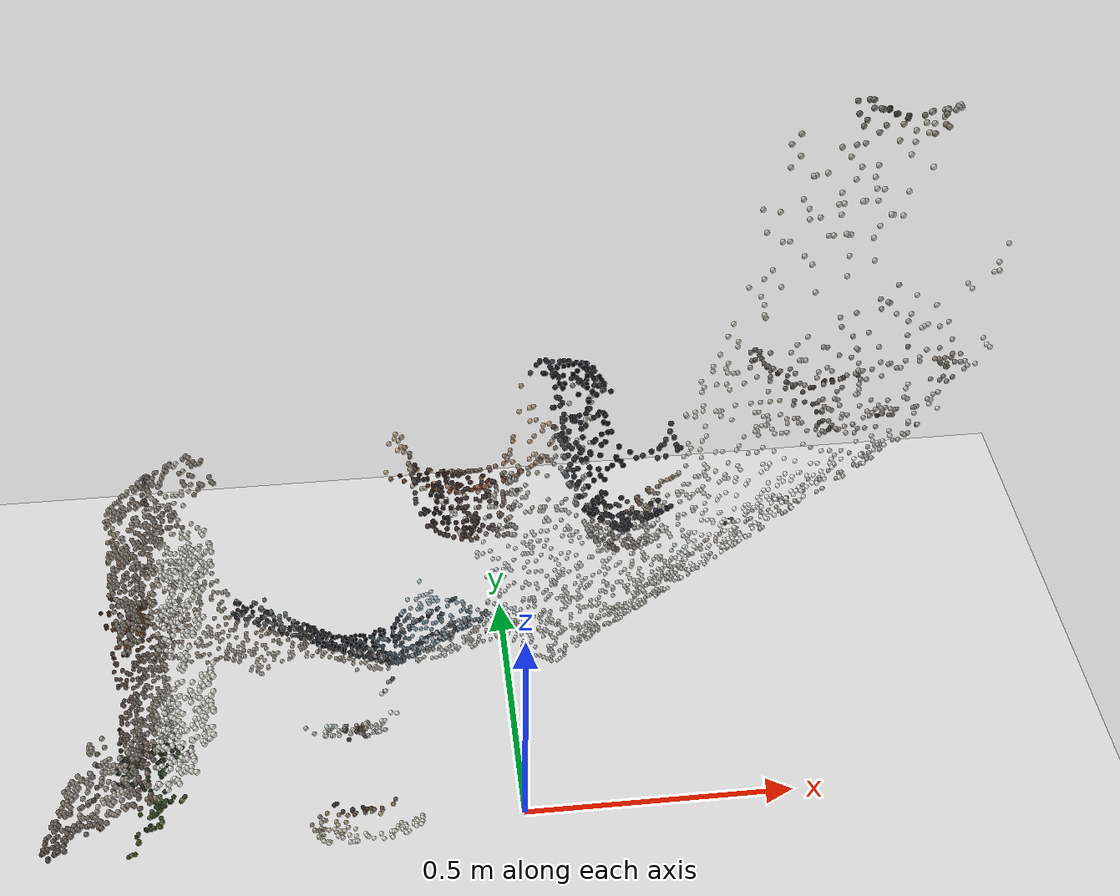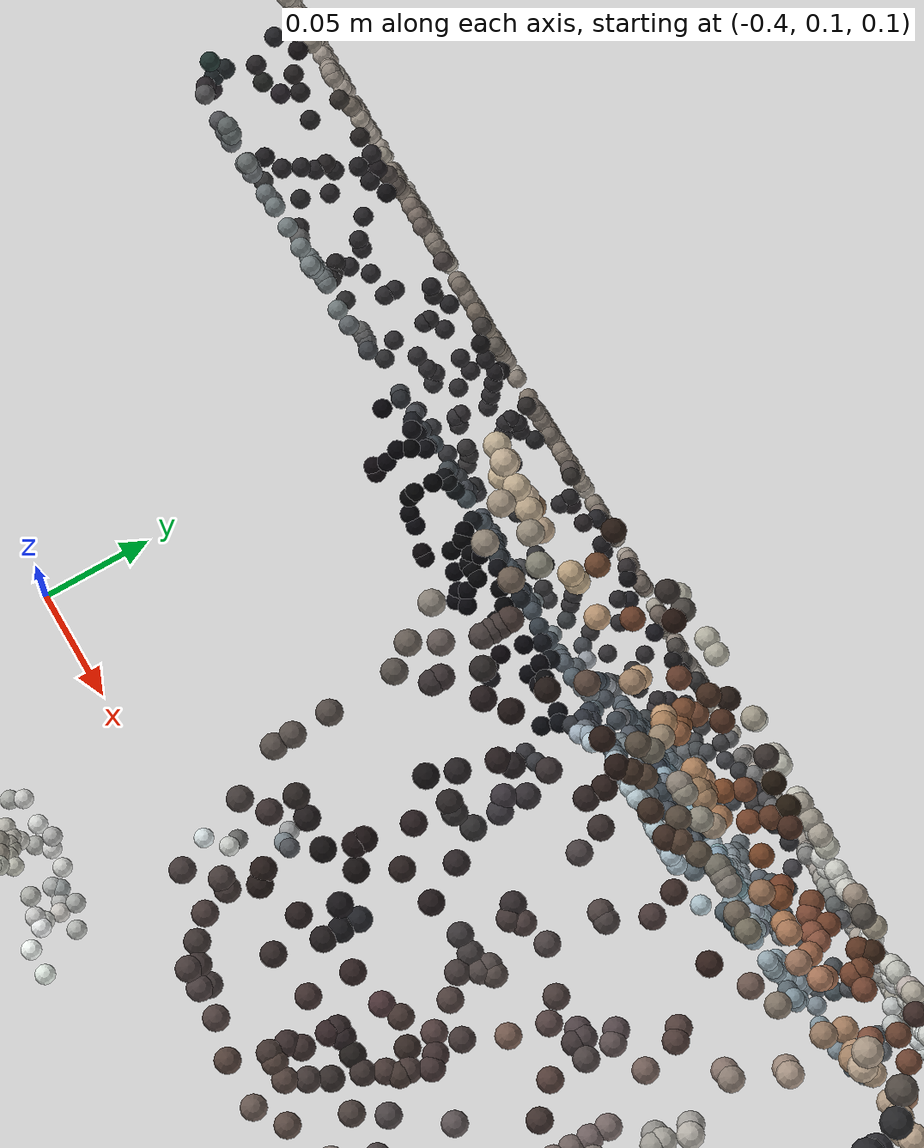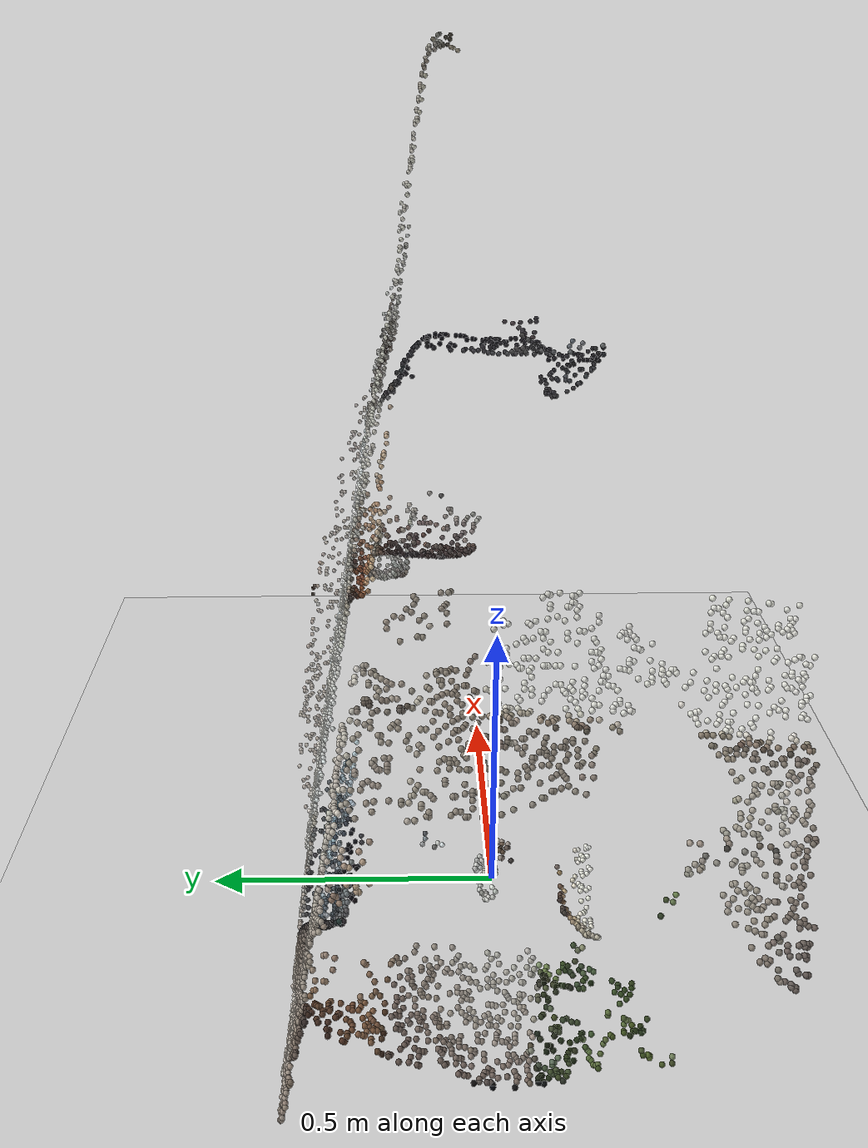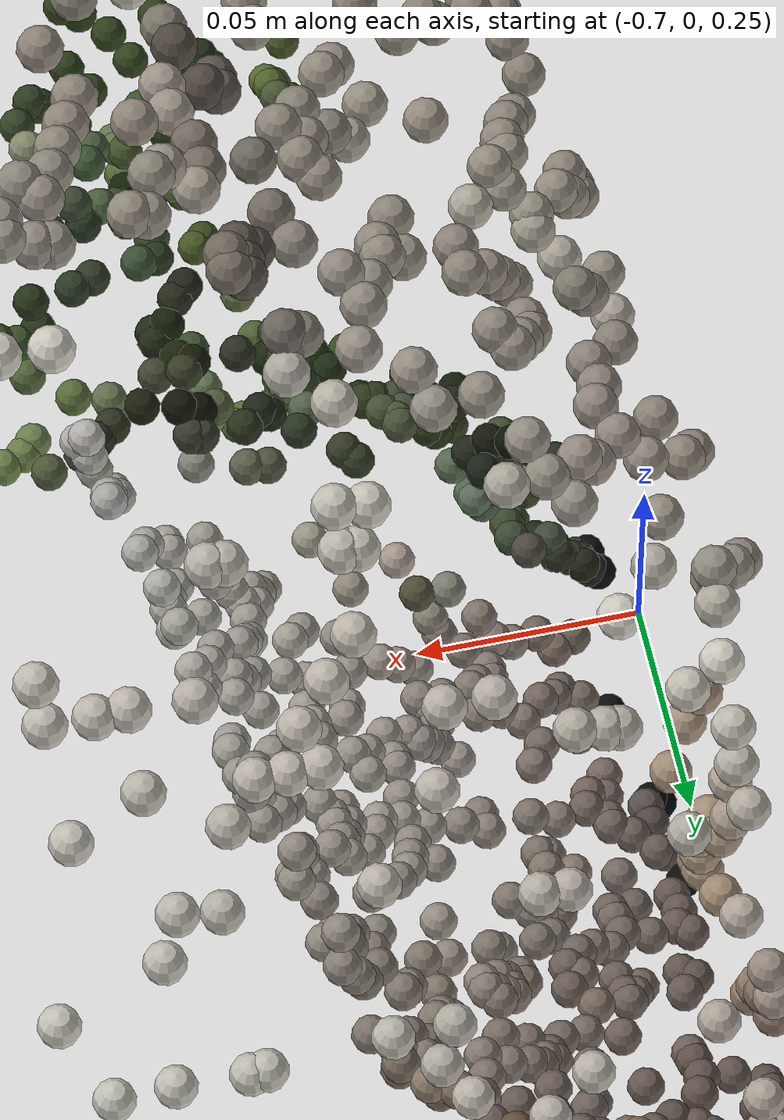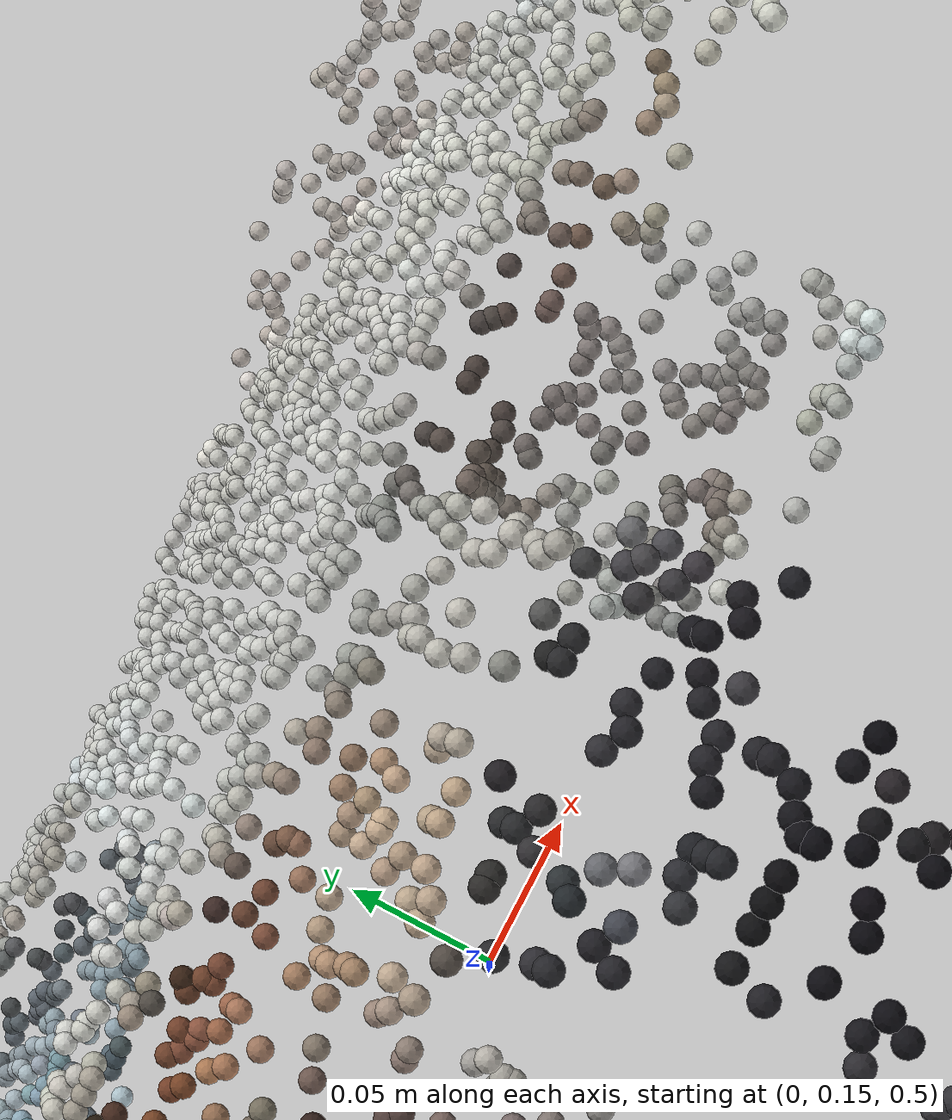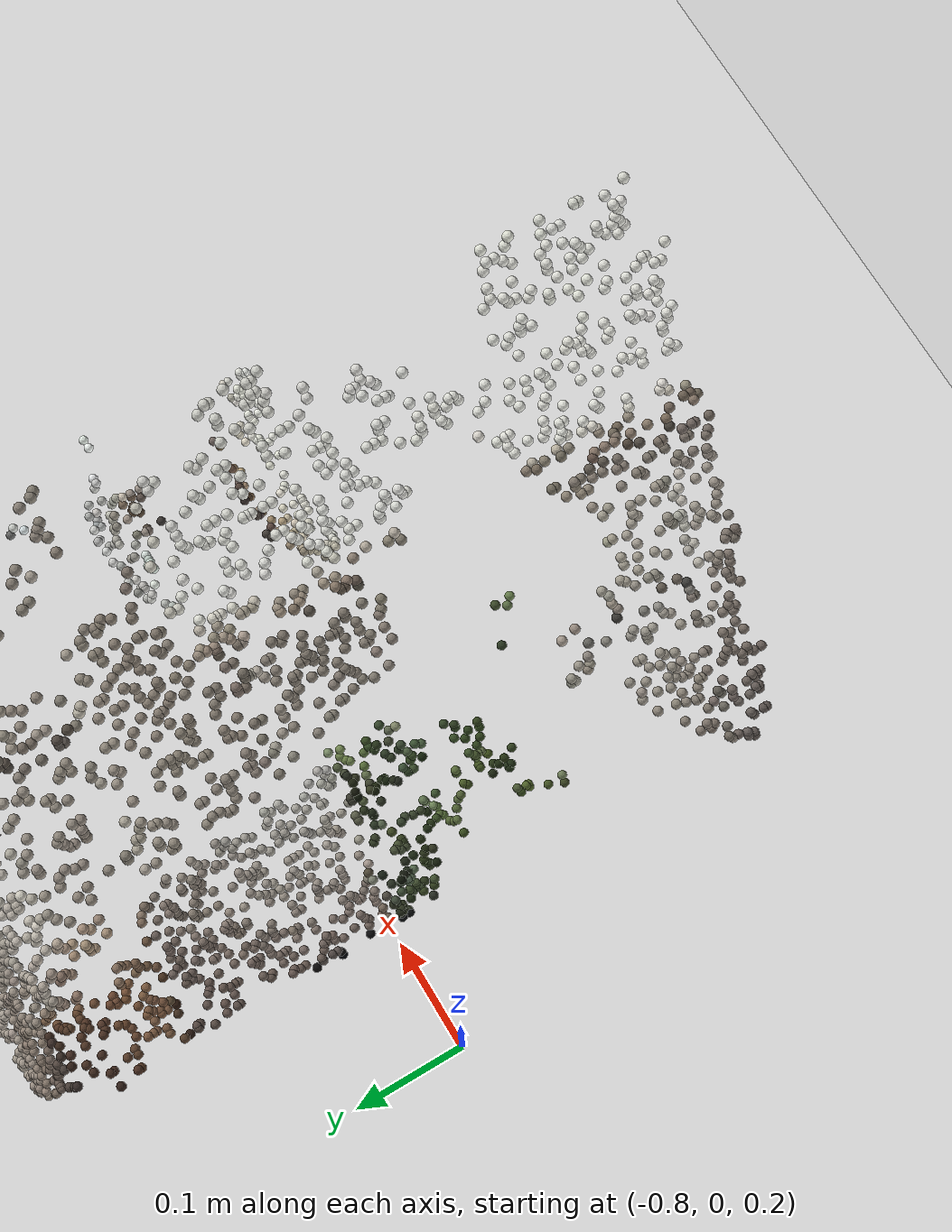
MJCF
<mujoco model="sparse_pointcloud">
  <option timestep="0.01" gravity="0 0 -9.81"/>
  <asset>
    <texture name="grid" type="2d" builtin="checker" rgb1="0.85 0.85 0.85" rgb2="0.7 0.7 0.7" width="512" height="512"/>
    <material name="grid" texture="grid" texrepeat="4 4" reflectance="0.1"/>
  </asset>
  <worldbody>
    <light pos="1 1 3" dir="0 0 -1" diffuse="1 1 1"/>
    <geom name="floor" type="plane" size="4 4 0.1" material="grid" rgba="0.9 0.9 0.9 1"/>
    <camera name="main_cam" pos="-0.187 -2.361 1.991" quat="0.9239 0.3827 0 0"/>
    <geom name="pt_0" type="sphere" size="0.0040" pos="0.3980 0.2675 0.4396" rgba="0.992 1.000 0.988 1" />
    <geom name="pt_1" type="sphere" size="0.0040" pos="0.1382 0.2648 0.4634" rgba="0.753 0.757 0.733 1" />
    <geom name="pt_2" type="sphere" size="0.0040" pos="0.3029 0.2831 0.3518" rgba="0.851 0.871 0.855 1" />
    <geom name="pt_3" type="sphere" size="0.0040" pos="-0.5945 0.0038 0.3230" rgba="0.655 0.643 0.608 1" />
    <geom name="pt_4" type="sphere" size="0.0040" pos="-0.2268 0.2828 0.1418" rgba="0.333 0.373 0.408 1" />
    <geom name="pt_5" type="sphere" size="0.0040" pos="0.3103 0.2961 0.2798" rgba="0.906 0.945 0.941 1" />
    <geom name="pt_6" type="sphere" size="0.0040" pos="-0.6813 0.0479 0.2577" rgba="0.447 0.396 0.365 1" />
    <geom name="pt_7" type="sphere" size="0.0040" pos="-0.6157 0.1470 0.3561" rgba="0.478 0.431 0.396 1" />
    <geom name="pt_8" type="sphere" size="0.0040" pos="-0.2171 0.2340 0.2540" rgba="0.039 0.043 0.063 1" />
    <geom name="pt_9" type="sphere" size="0.0040" pos="-0.5978 -0.1145 0.3080" rgba="0.216 0.302 0.149 1" />
    <geom name="pt_10" type="sphere" size="0.0040" pos="-0.6556 -0.1697 0.2433" rgba="0.271 0.333 0.145 1" />
    <geom name="pt_11" type="sphere" size="0.0040" pos="-0.0137 0.2156 0.6530" rgba="0.506 0.318 0.239 1" />
    <geom name="pt_12" type="sphere" size="0.0040" pos="0.3018 0.2077 0.7974" rgba="0.824 0.831 0.780 1" />
    <geom name="pt_13" type="sphere" size="0.0040" pos="0.1672 -0.1227 0.9163" rgba="0.224 0.235 0.255 1" />
    <geom name="pt_14" type="sphere" size="0.0040" pos="-0.5978 -0.2916 0.6245" rgba="0.498 0.482 0.439 1" />
    <geom name="pt_15" type="sphere" size="0.0040" pos="0.3936 0.1257 1.2813" rgba="0.718 0.710 0.659 1" />
    <geom name="pt_16" type="sphere" size="0.0040" pos="-0.4827 0.1014 0.8013" rgba="0.525 0.494 0.451 1" />
    <geom name="pt_17" type="sphere" size="0.0040" pos="-0.1243 0.2470 0.5884" rgba="0.776 0.776 0.749 1" />
    <geom name="pt_18" type="sphere" size="0.0040" pos="-0.5971 0.2910 0.2963" rgba="0.604 0.553 0.518 1" />
    <geom name="pt_19" type="sphere" size="0.0040" pos="0.6038 0.2517 0.6098" rgba="0.702 0.667 0.647 1" />
    <geom name="pt_20" type="sphere" size="0.0040" pos="-0.1355 0.1350 0.7170" rgba="0.094 0.082 0.086 1" />
    <geom name="pt_21" type="sphere" size="0.0040" pos="-0.5692 -0.0635 0.6904" rgba="0.388 0.337 0.298 1" />
    <geom name="pt_22" type="sphere" size="0.0040" pos="0.1446 -0.1607 0.9513" rgba="0.157 0.157 0.161 1" />
    <geom name="pt_23" type="sphere" size="0.0040" pos="-0.4223 0.3038 0.2139" rgba="0.525 0.486 0.447 1" />
    <geom name="pt_24" type="sphere" size="0.0040" pos="-0.6932 0.0715 0.2578" rgba="0.047 0.039 0.039 1" />
    <geom name="pt_25" type="sphere" size="0.0040" pos="-0.1266 0.1259 0.7099" rgba="0.165 0.122 0.129 1" />
    <geom name="pt_26" type="sphere" size="0.0040" pos="-0.6619 0.2894 0.3029" rgba="0.467 0.412 0.369 1" />
    <geom name="pt_27" type="sphere" size="0.0040" pos="-0.3307 0.2887 0.1866" rgba="0.184 0.176 0.188 1" />
    <geom name="pt_28" type="sphere" size="0.0040" pos="0.5306 0.2326 0.6510" rgba="0.800 0.824 0.796 1" />
    <geom name="pt_29" type="sphere" size="0.0040" pos="0.5015 0.1716 0.8684" rgba="0.506 0.467 0.443 1" />
    <geom name="pt_30" type="sphere" size="0.0040" pos="-0.1063 0.3249 0.1005" rgba="0.773 0.769 0.749 1" />
    <geom name="pt_31" type="sphere" size="0.0040" pos="0.1098 -0.1682 0.9628" rgba="0.173 0.169 0.188 1" />
    <geom name="pt_32" type="sphere" size="0.0040" pos="-0.3731 0.2728 0.2247" rgba="0.180 0.173 0.184 1" />
    <geom name="pt_33" type="sphere" size="0.0040" pos="-0.1326 0.1437 0.7153" rgba="0.153 0.133 0.141 1" />
    <geom name="pt_34" type="sphere" size="0.0040" pos="-0.4931 0.1443 0.8085" rgba="0.541 0.502 0.463 1" />
    <geom name="pt_35" type="sphere" size="0.0040" pos="-0.6938 0.2820 0.3429" rgba="0.290 0.247 0.224 1" />
    <geom name="pt_36" type="sphere" size="0.0040" pos="-0.5789 0.3209 0.1305" rgba="0.643 0.604 0.557 1" />
    <geom name="pt_37" type="sphere" size="0.0040" pos="-0.7111 -0.2806 0.5010" rgba="0.510 0.471 0.443 1" />
    <geom name="pt_38" type="sphere" size="0.0040" pos="-0.3148 0.3289 0.0717" rgba="0.675 0.639 0.600 1" />
    <geom name="pt_39" type="sphere" size="0.0040" pos="-0.1573 0.2365 0.3569" rgba="0.729 0.804 0.831 1" />
    <geom name="pt_40" type="sphere" size="0.0040" pos="-0.3069 0.2553 0.2344" rgba="0.075 0.090 0.106 1" />
    <geom name="pt_41" type="sphere" size="0.0040" pos="-0.5826 0.2090 0.7256" rgba="0.514 0.478 0.443 1" />
    <geom name="pt_42" type="sphere" size="0.0040" pos="-0.6994 -0.2170 0.5254" rgba="0.596 0.573 0.529 1" />
    <geom name="pt_43" type="sphere" size="0.0040" pos="-0.7002 -0.2552 0.5282" rgba="0.576 0.545 0.502 1" />
    <geom name="pt_44" type="sphere" size="0.0040" pos="0.1404 0.2616 0.4836" rgba="0.733 0.733 0.702 1" />
    <geom name="pt_45" type="sphere" size="0.0040" pos="-0.6124 0.0412 0.6631" rgba="0.471 0.439 0.396 1" />
    <geom name="pt_46" type="sphere" size="0.0040" pos="0.1946 0.2845 0.3422" rgba="0.875 0.894 0.871 1" />
    <geom name="pt_47" type="sphere" size="0.0040" pos="-0.5316 -0.0003 0.7223" rgba="0.875 0.878 0.847 1" />
    <geom name="pt_48" type="sphere" size="0.0040" pos="0.0118 0.2349 0.6446" rgba="0.592 0.529 0.486 1" />
    <geom name="pt_49" type="sphere" size="0.0040" pos="-0.2481 0.2294 0.2306" rgba="0.102 0.098 0.114 1" />
    <geom name="pt_50" type="sphere" size="0.0040" pos="-0.5670 0.0527 0.7077" rgba="0.604 0.553 0.494 1" />
    <geom name="pt_51" type="sphere" size="0.0040" pos="-0.6511 0.0646 0.2833" rgba="0.545 0.506 0.471 1" />
    <geom name="pt_52" type="sphere" size="0.0040" pos="-0.2754 0.0480 0.2460" rgba="0.722 0.722 0.714 1" />
    <geom name="pt_53" type="sphere" size="0.0040" pos="-0.1662 0.3163 0.1288" rgba="0.302 0.298 0.310 1" />
    <geom name="pt_54" type="sphere" size="0.0040" pos="0.0650 0.2968 0.2669" rgba="0.769 0.773 0.753 1" />
    <geom name="pt_55" type="sphere" size="0.0040" pos="-0.5225 -0.0945 0.7211" rgba="0.882 0.886 0.863 1" />
    <geom name="pt_56" type="sphere" size="0.0040" pos="0.5284 0.2115 0.7192" rgba="0.639 0.612 0.588 1" />
    <geom name="pt_57" type="sphere" size="0.0040" pos="-0.4613 0.3140 0.1585" rgba="0.667 0.635 0.592 1" />
    <geom name="pt_58" type="sphere" size="0.0040" pos="-0.2014 0.3220 0.0959" rgba="0.388 0.392 0.400 1" />
    <geom name="pt_59" type="sphere" size="0.0040" pos="-0.6246 0.2748 0.3891" rgba="0.624 0.576 0.525 1" />
    <geom name="pt_60" type="sphere" size="0.0040" pos="-0.4938 0.3316 0.0628" rgba="0.761 0.745 0.702 1" />
    <geom name="pt_61" type="sphere" size="0.0040" pos="-0.5718 0.2594 0.4885" rgba="0.761 0.753 0.706 1" />
    <geom name="pt_62" type="sphere" size="0.0040" pos="0.6175 0.1854 0.8348" rgba="0.804 0.808 0.812 1" />
    <geom name="pt_63" type="sphere" size="0.0040" pos="0.0396 -0.1084 0.9940" rgba="0.365 0.396 0.431 1" />
    <geom name="pt_64" type="sphere" size="0.0040" pos="-0.2534 0.3273 0.0753" rgba="0.569 0.529 0.494 1" />
    <geom name="pt_65" type="sphere" size="0.0040" pos="0.2460 0.3168 0.1775" rgba="0.776 0.745 0.718 1" />
    <geom name="pt_66" type="sphere" size="0.0040" pos="-0.1831 0.2673 0.2366" rgba="0.227 0.263 0.314 1" />
    <geom name="pt_67" type="sphere" size="0.0040" pos="-0.3167 0.3268 0.0851" rgba="0.655 0.624 0.573 1" />
    <geom name="pt_68" type="sphere" size="0.0040" pos="-0.1888 -0.1409 0.2144" rgba="0.945 0.957 0.933 1" />
    <geom name="pt_69" type="sphere" size="0.0040" pos="-0.6014 0.1369 0.6909" rgba="0.588 0.553 0.506 1" />
    <geom name="pt_70" type="sphere" size="0.0040" pos="-0.5699 -0.2874 0.6529" rgba="0.329 0.302 0.271 1" />
    <geom name="pt_71" type="sphere" size="0.0040" pos="-0.1669 0.1549 0.7700" rgba="0.553 0.522 0.482 1" />
    <geom name="pt_72" type="sphere" size="0.0040" pos="-0.0000 0.3083 0.1972" rgba="0.847 0.863 0.859 1" />
    <geom name="pt_73" type="sphere" size="0.0040" pos="0.3931 0.2077 0.7965" rgba="0.757 0.745 0.710 1" />
    <geom name="pt_74" type="sphere" size="0.0040" pos="-0.5620 -0.2850 0.6562" rgba="0.541 0.478 0.420 1" />
    <geom name="pt_75" type="sphere" size="0.0040" pos="-0.4652 -0.2957 0.7684" rgba="0.898 0.902 0.871 1" />
    <geom name="pt_76" type="sphere" size="0.0040" pos="-0.5887 0.2422 0.5971" rgba="0.745 0.718 0.678 1" />
    <geom name="pt_77" type="sphere" size="0.0040" pos="-0.6175 0.2546 0.5223" rgba="0.733 0.706 0.667 1" />
    <geom name="pt_78" type="sphere" size="0.0040" pos="-0.6159 -0.2859 0.6057" rgba="0.604 0.580 0.533 1" />
    <geom name="pt_79" type="sphere" size="0.0040" pos="0.6172 0.1879 0.8229" rgba="0.776 0.773 0.780 1" />
    <geom name="pt_80" type="sphere" size="0.0040" pos="-0.1572 0.2189 0.6590" rgba="0.427 0.251 0.165 1" />
    <geom name="pt_81" type="sphere" size="0.0040" pos="-0.4208 0.2687 0.2699" rgba="0.161 0.153 0.165 1" />
    <geom name="pt_82" type="sphere" size="0.0040" pos="0.0401 0.2741 0.4050" rgba="0.831 0.835 0.816 1" />
    <geom name="pt_83" type="sphere" size="0.0040" pos="-0.6439 0.1329 0.3160" rgba="0.475 0.424 0.388 1" />
    <geom name="pt_84" type="sphere" size="0.0040" pos="0.1965 0.1660 0.5273" rgba="0.549 0.529 0.514 1" />
    <geom name="pt_85" type="sphere" size="0.0040" pos="-0.6477 -0.2621 0.5767" rgba="0.392 0.361 0.318 1" />
    <geom name="pt_86" type="sphere" size="0.0040" pos="-0.5720 0.0410 0.7037" rgba="0.376 0.341 0.294 1" />
    <geom name="pt_87" type="sphere" size="0.0040" pos="-0.3837 0.3151 0.1504" rgba="0.580 0.541 0.502 1" />
    <geom name="pt_88" type="sphere" size="0.0040" pos="-0.1295 0.2938 0.1575" rgba="0.361 0.400 0.424 1" />
    <geom name="pt_89" type="sphere" size="0.0040" pos="0.1324 0.2202 0.5643" rgba="0.439 0.408 0.373 1" />
    <geom name="pt_90" type="sphere" size="0.0040" pos="0.1854 0.1794 0.5253" rgba="0.580 0.557 0.533 1" />
    <geom name="pt_91" type="sphere" size="0.0040" pos="-0.1744 0.3057 0.1166" rgba="0.286 0.302 0.325 1" />
    <geom name="pt_92" type="sphere" size="0.0040" pos="0.6214 0.2244 0.6952" rgba="0.788 0.820 0.816 1" />
    <geom name="pt_93" type="sphere" size="0.0040" pos="0.5068 0.1777 0.8641" rgba="0.251 0.192 0.173 1" />
    <geom name="pt_94" type="sphere" size="0.0040" pos="-0.2423 0.0289 0.2726" rgba="0.816 0.820 0.800 1" />
    <geom name="pt_95" type="sphere" size="0.0040" pos="-0.3465 -0.0961 0.2017" rgba="0.608 0.541 0.447 1" />
    <geom name="pt_96" type="sphere" size="0.0040" pos="0.3153 0.2563 0.5110" rgba="0.824 0.827 0.804 1" />
    <geom name="pt_97" type="sphere" size="0.0040" pos="-0.4671 0.3051 0.2070" rgba="0.627 0.596 0.545 1" />
    <geom name="pt_98" type="sphere" size="0.0040" pos="-0.3373 0.0215 0.2867" rgba="0.878 0.929 0.886 1" />
    <geom name="pt_99" type="sphere" size="0.0040" pos="-0.1539 0.1476 0.7381" rgba="0.227 0.196 0.200 1" />
    <geom name="pt_100" type="sphere" size="0.0040" pos="-0.6933 0.0480 0.2508" rgba="0.008 0.016 0.035 1" />
    <geom name="pt_101" type="sphere" size="0.0040" pos="-0.4881 0.3177 0.1387" rgba="0.675 0.643 0.600 1" />
    <geom name="pt_102" type="sphere" size="0.0040" pos="0.5906 0.2475 0.5941" rgba="0.702 0.675 0.651 1" />
    <geom name="pt_103" type="sphere" size="0.0040" pos="0.5948 0.2265 0.6843" rgba="0.773 0.804 0.792 1" />
    <geom name="pt_104" type="sphere" size="0.0040" pos="0.1568 0.1665 0.5361" rgba="0.506 0.490 0.467 1" />
    <geom name="pt_105" type="sphere" size="0.0040" pos="0.2856 0.3027 0.2398" rgba="0.788 0.792 0.761 1" />
    <geom name="pt_106" type="sphere" size="0.0040" pos="-0.6815 0.2910 0.2957" rgba="0.404 0.349 0.314 1" />
    <geom name="pt_107" type="sphere" size="0.0040" pos="-0.6504 -0.0020 0.2728" rgba="0.329 0.302 0.235 1" />
    <geom name="pt_108" type="sphere" size="0.0040" pos="0.5366 0.1847 0.8211" rgba="0.733 0.733 0.718 1" />
    <geom name="pt_109" type="sphere" size="0.0040" pos="0.1194 0.2312 0.6337" rgba="0.663 0.667 0.635 1" />
    <geom name="pt_110" type="sphere" size="0.0040" pos="0.1672 0.2095 0.5315" rgba="0.471 0.439 0.427 1" />
    <geom name="pt_111" type="sphere" size="0.0040" pos="-0.6619 0.2923 0.2872" rgba="0.459 0.404 0.361 1" />
    <geom name="pt_112" type="sphere" size="0.0040" pos="-0.0895 0.2693 0.2345" rgba="0.553 0.631 0.675 1" />
    <geom name="pt_113" type="sphere" size="0.0040" pos="-0.5132 -0.1972 0.7185" rgba="0.898 0.902 0.871 1" />
    <geom name="pt_114" type="sphere" size="0.0040" pos="-0.6058 0.1721 0.6974" rgba="0.565 0.533 0.490 1" />
    <geom name="pt_115" type="sphere" size="0.0040" pos="-0.4920 0.1288 0.8024" rgba="0.533 0.502 0.459 1" />
    <geom name="pt_116" type="sphere" size="0.0040" pos="0.1441 0.1670 0.5447" rgba="0.565 0.557 0.529 1" />
    <geom name="pt_117" type="sphere" size="0.0040" pos="-0.5716 -0.0634 0.6879" rgba="0.322 0.306 0.263 1" />
    <geom name="pt_118" type="sphere" size="0.0040" pos="-0.5313 -0.1216 0.6905" rgba="0.890 0.886 0.863 1" />
    <geom name="pt_119" type="sphere" size="0.0040" pos="-0.5589 -0.0204 0.3181" rgba="0.498 0.569 0.420 1" />
    <geom name="pt_120" type="sphere" size="0.0040" pos="0.2584 0.3491 0.1949" rgba="0.753 0.725 0.702 1" />
    <geom name="pt_121" type="sphere" size="0.0040" pos="0.4579 0.0680 1.4161" rgba="0.220 0.204 0.173 1" />
    <geom name="pt_122" type="sphere" size="0.0040" pos="-0.5873 -0.0709 0.6667" rgba="0.506 0.478 0.424 1" />
    <geom name="pt_123" type="sphere" size="0.0040" pos="0.3644 0.2595 0.4891" rgba="0.992 1.000 0.984 1" />
    <geom name="pt_124" type="sphere" size="0.0040" pos="-0.6044 0.0822 0.3417" rgba="0.576 0.549 0.514 1" />
    <geom name="pt_125" type="sphere" size="0.0040" pos="0.0857 -0.1181 0.9426" rgba="0.110 0.110 0.118 1" />
    <geom name="pt_126" type="sphere" size="0.0040" pos="-0.6839 0.1052 0.2805" rgba="0.404 0.345 0.310 1" />
    <geom name="pt_127" type="sphere" size="0.0040" pos="-0.0048 0.3179 0.1399" rgba="0.820 0.827 0.808 1" />
    <geom name="pt_128" type="sphere" size="0.0040" pos="-0.3285 0.0363 0.2389" rgba="0.714 0.706 0.686 1" />
    <geom name="pt_129" type="sphere" size="0.0040" pos="-0.5467 0.2686 0.4251" rgba="0.694 0.671 0.631 1" />
    <geom name="pt_130" type="sphere" size="0.0040" pos="-0.2430 0.3304 0.0558" rgba="0.694 0.659 0.624 1" />
    <geom name="pt_131" type="sphere" size="0.0040" pos="-0.5464 0.0793 0.7370" rgba="0.502 0.463 0.416 1" />
    <geom name="pt_132" type="sphere" size="0.0040" pos="-0.1923 0.2502 0.2744" rgba="0.384 0.435 0.471 1" />
    <geom name="pt_133" type="sphere" size="0.0040" pos="-0.1310 0.2485 0.3045" rgba="0.380 0.435 0.467 1" />
    <geom name="pt_134" type="sphere" size="0.0040" pos="-0.1689 0.3322 0.0538" rgba="0.733 0.718 0.686 1" />
    <geom name="pt_135" type="sphere" size="0.0040" pos="-0.5713 0.0264 0.7003" rgba="0.459 0.420 0.376 1" />
    <geom name="pt_136" type="sphere" size="0.0040" pos="-0.5905 -0.0374 0.3172" rgba="0.392 0.447 0.298 1" />
    <geom name="pt_137" type="sphere" size="0.0040" pos="0.1938 0.1633 0.5272" rgba="0.545 0.514 0.502 1" />
    <geom name="pt_138" type="sphere" size="0.0040" pos="-0.3004 -0.1309 0.1626" rgba="0.906 0.906 0.863 1" />
    <geom name="pt_139" type="sphere" size="0.0040" pos="-0.6618 0.0741 0.2789" rgba="0.518 0.471 0.420 1" />
    <geom name="pt_140" type="sphere" size="0.0040" pos="-0.2988 -0.0903 0.1864" rgba="0.573 0.510 0.439 1" />
    <geom name="pt_141" type="sphere" size="0.0040" pos="-0.5940 0.1699 0.7104" rgba="0.573 0.541 0.490 1" />
    <geom name="pt_142" type="sphere" size="0.0040" pos="-0.2221 0.2897 0.1116" rgba="0.365 0.420 0.455 1" />
    <geom name="pt_143" type="sphere" size="0.0040" pos="-0.6517 0.1302 0.3093" rgba="0.463 0.412 0.376 1" />
    <geom name="pt_144" type="sphere" size="0.0040" pos="0.1139 0.2564 0.5129" rgba="0.745 0.749 0.725 1" />
    <geom name="pt_145" type="sphere" size="0.0040" pos="0.2045 0.2297 0.5470" rgba="0.427 0.337 0.298 1" />
    <geom name="pt_146" type="sphere" size="0.0040" pos="0.2242 0.2082 0.5507" rgba="0.588 0.580 0.569 1" />
    <geom name="pt_147" type="sphere" size="0.0040" pos="-0.4955 0.2973 0.2523" rgba="0.604 0.565 0.525 1" />
    <geom name="pt_148" type="sphere" size="0.0040" pos="0.1050 0.0822 0.9864" rgba="0.125 0.102 0.118 1" />
    <geom name="pt_149" type="sphere" size="0.0040" pos="-0.5727 -0.2175 0.6658" rgba="0.451 0.424 0.369 1" />
    <geom name="pt_150" type="sphere" size="0.0040" pos="-0.4804 -0.0079 0.7878" rgba="0.824 0.827 0.796 1" />
    <geom name="pt_151" type="sphere" size="0.0040" pos="0.1725 0.2122 0.5310" rgba="0.494 0.463 0.451 1" />
    <geom name="pt_152" type="sphere" size="0.0040" pos="-0.6532 -0.0365 0.2982" rgba="0.251 0.290 0.192 1" />
    <geom name="pt_153" type="sphere" size="0.0040" pos="-0.4603 -0.0239 0.8146" rgba="0.820 0.820 0.788 1" />
    <geom name="pt_154" type="sphere" size="0.0040" pos="0.4655 0.2627 0.4689" rgba="0.988 0.996 0.984 1" />
    <geom name="pt_155" type="sphere" size="0.0040" pos="0.5081 0.1456 1.1164" rgba="0.769 0.757 0.729 1" />
    <geom name="pt_156" type="sphere" size="0.0040" pos="-0.5635 0.2825 0.3465" rgba="0.580 0.549 0.506 1" />
    <geom name="pt_157" type="sphere" size="0.0040" pos="-0.6165 0.1016 0.6684" rgba="0.541 0.510 0.459 1" />
    <geom name="pt_158" type="sphere" size="0.0040" pos="-0.6864 0.1393 0.2962" rgba="0.396 0.337 0.310 1" />
    <geom name="pt_159" type="sphere" size="0.0040" pos="-0.6631 0.0125 0.2599" rgba="0.533 0.486 0.455 1" />
    <geom name="pt_160" type="sphere" size="0.0040" pos="0.4051 0.2831 0.3732" rgba="0.824 0.820 0.800 1" />
    <geom name="pt_161" type="sphere" size="0.0040" pos="0.6720 0.2115 0.7627" rgba="0.808 0.816 0.812 1" />
    <geom name="pt_162" type="sphere" size="0.0040" pos="-0.5307 -0.2026 0.6871" rgba="0.906 0.906 0.875 1" />
    <geom name="pt_163" type="sphere" size="0.0040" pos="0.1677 0.3197 0.1367" rgba="0.816 0.816 0.784 1" />
    <geom name="pt_164" type="sphere" size="0.0040" pos="0.3156 0.2202 0.7176" rgba="0.835 0.835 0.796 1" />
    <geom name="pt_165" type="sphere" size="0.0040" pos="0.0493 0.3108 0.1828" rgba="0.820 0.824 0.804 1" />
    <geom name="pt_166" type="sphere" size="0.0040" pos="-0.6077 -0.0303 0.6550" rgba="0.506 0.475 0.431 1" />
    <geom name="pt_167" type="sphere" size="0.0040" pos="-0.0971 0.1986 0.7011" rgba="0.569 0.541 0.486 1" />
    <geom name="pt_168" type="sphere" size="0.0040" pos="-0.0112 0.1474 0.7337" rgba="0.655 0.643 0.624 1" />
    <geom name="pt_169" type="sphere" size="0.0040" pos="-0.6266 -0.0818 0.2248" rgba="0.329 0.416 0.216 1" />
    <geom name="pt_170" type="sphere" size="0.0040" pos="-0.6445 0.3099 0.1924" rgba="0.584 0.537 0.490 1" />
    <geom name="pt_171" type="sphere" size="0.0040" pos="-0.0781 0.3224 0.1120" rgba="0.780 0.784 0.761 1" />
    <geom name="pt_172" type="sphere" size="0.0040" pos="-0.5282 0.2107 0.7511" rgba="0.812 0.796 0.769 1" />
    <geom name="pt_173" type="sphere" size="0.0040" pos="0.4386 0.1321 1.2467" rgba="0.753 0.737 0.702 1" />
    <geom name="pt_174" type="sphere" size="0.0040" pos="-0.4731 0.3292 0.0741" rgba="0.776 0.753 0.714 1" />
    <geom name="pt_175" type="sphere" size="0.0040" pos="-0.6243 0.0555 0.6527" rgba="0.525 0.486 0.447 1" />
    <geom name="pt_176" type="sphere" size="0.0040" pos="0.1711 -0.1021 0.8925" rgba="0.239 0.243 0.259 1" />
    <geom name="pt_177" type="sphere" size="0.0040" pos="-0.5083 0.3179 0.1398" rgba="0.667 0.627 0.588 1" />
    <geom name="pt_178" type="sphere" size="0.0040" pos="0.5883 0.1972 0.7749" rgba="0.698 0.675 0.659 1" />
    <geom name="pt_179" type="sphere" size="0.0040" pos="0.1363 0.1699 0.5481" rgba="0.573 0.580 0.541 1" />
    <geom name="pt_180" type="sphere" size="0.0040" pos="-0.6118 0.0988 0.6730" rgba="0.533 0.502 0.451 1" />
    <geom name="pt_181" type="sphere" size="0.0040" pos="-0.1887 -0.1361 0.2125" rgba="0.929 0.933 0.906 1" />
    <geom name="pt_182" type="sphere" size="0.0040" pos="-0.1652 0.2646 0.2544" rgba="0.239 0.278 0.314 1" />
    <geom name="pt_183" type="sphere" size="0.0040" pos="0.6092 0.2665 0.6183" rgba="0.706 0.682 0.671 1" />
    <geom name="pt_184" type="sphere" size="0.0040" pos="0.0862 0.3321 0.0528" rgba="0.816 0.812 0.792 1" />
    <geom name="pt_185" type="sphere" size="0.0040" pos="-0.6040 0.2133 0.7024" rgba="0.604 0.580 0.533 1" />
    <geom name="pt_186" type="sphere" size="0.0040" pos="-0.5812 0.2675 0.4397" rgba="0.678 0.655 0.608 1" />
    <geom name="pt_187" type="sphere" size="0.0040" pos="-0.5662 -0.2515 0.6624" rgba="0.408 0.337 0.294 1" />
    <geom name="pt_188" type="sphere" size="0.0040" pos="0.4786 0.1728 0.8924" rgba="0.651 0.647 0.627 1" />
    <geom name="pt_189" type="sphere" size="0.0040" pos="0.1994 0.1580 0.5289" rgba="0.561 0.541 0.518 1" />
    <geom name="pt_190" type="sphere" size="0.0040" pos="0.0156 0.2195 0.6679" rgba="0.580 0.427 0.341 1" />
    <geom name="pt_191" type="sphere" size="0.0040" pos="-0.6703 0.0338 0.2603" rgba="0.471 0.420 0.388 1" />
    <geom name="pt_192" type="sphere" size="0.0040" pos="-0.0708 0.1723 0.7004" rgba="0.290 0.224 0.220 1" />
    <geom name="pt_193" type="sphere" size="0.0040" pos="0.4595 0.2853 0.4363" rgba="0.722 0.694 0.671 1" />
    <geom name="pt_194" type="sphere" size="0.0040" pos="0.4795 0.1291 1.2710" rgba="0.757 0.745 0.710 1" />
    <geom name="pt_195" type="sphere" size="0.0040" pos="0.0464 0.2161 0.7016" rgba="0.561 0.451 0.365 1" />
    <geom name="pt_196" type="sphere" size="0.0040" pos="-0.5033 -0.1511 0.7293" rgba="0.890 0.890 0.859 1" />
    <geom name="pt_197" type="sphere" size="0.0040" pos="-0.2283 0.3262 0.0817" rgba="0.420 0.404 0.388 1" />
    <geom name="pt_198" type="sphere" size="0.0040" pos="-0.5855 0.3209 0.1306" rgba="0.643 0.604 0.557 1" />
    <geom name="pt_199" type="sphere" size="0.0040" pos="0.4076 0.2881 0.3733" rgba="0.725 0.690 0.663 1" />
    <geom name="pt_200" type="sphere" size="0.0040" pos="-0.5399 -0.0817 0.7042" rgba="0.882 0.886 0.855 1" />
    <geom name="pt_201" type="sphere" size="0.0040" pos="0.4840 0.2508 0.5395" rgba="0.996 0.996 0.988 1" />
    <geom name="pt_202" type="sphere" size="0.0040" pos="0.0192 0.3191 0.1333" rgba="0.820 0.827 0.808 1" />
    <geom name="pt_203" type="sphere" size="0.0040" pos="-0.6221 0.0271 0.6434" rgba="0.608 0.576 0.533 1" />
    <geom name="pt_204" type="sphere" size="0.0040" pos="0.2640 0.3053 0.2248" rgba="0.808 0.812 0.784 1" />
    <geom name="pt_205" type="sphere" size="0.0040" pos="0.1410 0.2899 0.3066" rgba="0.808 0.812 0.788 1" />
    <geom name="pt_206" type="sphere" size="0.0040" pos="0.1228 0.1495 0.5794" rgba="0.553 0.565 0.553 1" />
    <geom name="pt_207" type="sphere" size="0.0040" pos="-0.1052 0.3103 0.1791" rgba="0.588 0.592 0.573 1" />
    <geom name="pt_208" type="sphere" size="0.0040" pos="0.2906 0.3129 0.2295" rgba="0.706 0.675 0.635 1" />
    <geom name="pt_209" type="sphere" size="0.0040" pos="-0.6302 0.2838 0.3369" rgba="0.604 0.557 0.510 1" />
    <geom name="pt_210" type="sphere" size="0.0040" pos="-0.4541 -0.2478 0.7940" rgba="0.890 0.898 0.855 1" />
    <geom name="pt_211" type="sphere" size="0.0040" pos="0.3326 0.2097 0.7812" rgba="0.808 0.808 0.769 1" />
    <geom name="pt_212" type="sphere" size="0.0040" pos="-0.0458 0.2409 0.6147" rgba="0.612 0.576 0.506 1" />
    <geom name="pt_213" type="sphere" size="0.0040" pos="0.5547 0.2362 0.6252" rgba="0.973 0.992 0.996 1" />
    <geom name="pt_214" type="sphere" size="0.0040" pos="-0.5303 -0.2487 0.6850" rgba="0.906 0.910 0.878 1" />
    <geom name="pt_215" type="sphere" size="0.0040" pos="-0.6889 -0.0111 0.2590" rgba="0.184 0.216 0.137 1" />
    <geom name="pt_216" type="sphere" size="0.0040" pos="0.5946 0.1973 0.7758" rgba="0.690 0.659 0.647 1" />
    <geom name="pt_217" type="sphere" size="0.0040" pos="0.0935 0.1404 0.9621" rgba="0.141 0.137 0.157 1" />
    <geom name="pt_218" type="sphere" size="0.0040" pos="-0.5911 -0.1196 0.3104" rgba="0.180 0.255 0.129 1" />
    <geom name="pt_219" type="sphere" size="0.0040" pos="0.5106 0.2101 0.7423" rgba="0.565 0.533 0.502 1" />
    <geom name="pt_220" type="sphere" size="0.0040" pos="0.0944 -0.0616 0.9761" rgba="0.114 0.110 0.129 1" />
    <geom name="pt_221" type="sphere" size="0.0040" pos="0.0516 0.0136 0.9717" rgba="0.259 0.263 0.278 1" />
    <geom name="pt_222" type="sphere" size="0.0040" pos="-0.6053 -0.0476 0.3267" rgba="0.086 0.133 0.051 1" />
    <geom name="pt_223" type="sphere" size="0.0040" pos="-0.6395 0.2732 0.3969" rgba="0.580 0.545 0.494 1" />
    <geom name="pt_224" type="sphere" size="0.0040" pos="-0.1118 0.0994 0.7008" rgba="0.141 0.145 0.165 1" />
    <geom name="pt_225" type="sphere" size="0.0040" pos="0.4799 0.1260 1.2921" rgba="0.725 0.710 0.675 1" />
    <geom name="pt_226" type="sphere" size="0.0040" pos="0.6218 0.2565 0.6313" rgba="0.725 0.690 0.686 1" />
    <geom name="pt_227" type="sphere" size="0.0040" pos="-0.6060 0.1555 0.3760" rgba="0.498 0.459 0.424 1" />
    <geom name="pt_228" type="sphere" size="0.0040" pos="0.4842 0.2944 0.4701" rgba="0.729 0.690 0.675 1" />
    <geom name="pt_229" type="sphere" size="0.0040" pos="-0.6872 -0.2932 0.5300" rgba="0.478 0.439 0.400 1" />
    <geom name="pt_230" type="sphere" size="0.0040" pos="-0.2433 0.0264 0.2835" rgba="0.827 0.827 0.820 1" />
    <geom name="pt_231" type="sphere" size="0.0040" pos="-0.0443 0.1229 0.7058" rgba="0.337 0.251 0.231 1" />
    <geom name="pt_232" type="sphere" size="0.0040" pos="0.1002 -0.1230 0.9205" rgba="0.184 0.188 0.204 1" />
    <geom name="pt_233" type="sphere" size="0.0040" pos="-0.5492 0.3070 0.2041" rgba="0.651 0.627 0.580 1" />
    <geom name="pt_234" type="sphere" size="0.0040" pos="0.1817 0.2995 0.2509" rgba="0.812 0.808 0.788 1" />
    <geom name="pt_235" type="sphere" size="0.0040" pos="0.5950 0.2480 0.5993" rgba="0.698 0.667 0.643 1" />
    <geom name="pt_236" type="sphere" size="0.0040" pos="-0.6362 -0.2247 0.5862" rgba="0.608 0.604 0.557 1" />
    <geom name="pt_237" type="sphere" size="0.0040" pos="0.0980 -0.0454 0.9799" rgba="0.110 0.106 0.125 1" />
    <geom name="pt_238" type="sphere" size="0.0040" pos="-0.7114 -0.2393 0.5110" rgba="0.557 0.533 0.478 1" />
    <geom name="pt_239" type="sphere" size="0.0040" pos="-0.5782 -0.0525 0.3265" rgba="0.149 0.216 0.102 1" />
    <geom name="pt_240" type="sphere" size="0.0040" pos="-0.0168 0.3120 0.1754" rgba="0.816 0.824 0.812 1" />
    <geom name="pt_241" type="sphere" size="0.0040" pos="-0.6601 0.2003 0.3379" rgba="0.498 0.369 0.259 1" />
    <geom name="pt_242" type="sphere" size="0.0040" pos="0.5690 0.2508 0.5686" rgba="0.725 0.714 0.667 1" />
    <geom name="pt_243" type="sphere" size="0.0040" pos="0.1598 -0.1189 0.9069" rgba="0.278 0.286 0.306 1" />
    <geom name="pt_244" type="sphere" size="0.0040" pos="0.0238 0.3059 0.2123" rgba="0.835 0.843 0.824 1" />
    <geom name="pt_245" type="sphere" size="0.0040" pos="0.2843 0.3210 0.2214" rgba="0.698 0.682 0.659 1" />
    <geom name="pt_246" type="sphere" size="0.0040" pos="-0.5631 0.3135 0.1703" rgba="0.663 0.631 0.588 1" />
    <geom name="pt_247" type="sphere" size="0.0040" pos="-0.6762 -0.2773 0.5492" rgba="0.486 0.459 0.420 1" />
    <geom name="pt_248" type="sphere" size="0.0040" pos="0.1354 0.1691 0.8826" rgba="0.306 0.302 0.322 1" />
    <geom name="pt_249" type="sphere" size="0.0040" pos="-0.6869 -0.2132 0.5386" rgba="0.592 0.573 0.529 1" />
    <geom name="pt_250" type="sphere" size="0.0040" pos="-0.2519 0.2585 0.2210" rgba="0.271 0.310 0.345 1" />
    <geom name="pt_251" type="sphere" size="0.0040" pos="0.5207 0.1195 1.3297" rgba="0.718 0.710 0.671 1" />
    <geom name="pt_252" type="sphere" size="0.0040" pos="0.1350 0.3180 0.1404" rgba="0.816 0.816 0.784 1" />
    <geom name="pt_253" type="sphere" size="0.0040" pos="-0.6501 0.2676 0.3458" rgba="0.329 0.212 0.145 1" />
    <geom name="pt_254" type="sphere" size="0.0040" pos="0.1223 0.2927 0.2905" rgba="0.827 0.831 0.812 1" />
    <geom name="pt_255" type="sphere" size="0.0040" pos="-0.2613 0.3285 0.0698" rgba="0.608 0.576 0.525 1" />
    <geom name="pt_256" type="sphere" size="0.0040" pos="-0.2376 0.2768 0.1640" rgba="0.267 0.306 0.341 1" />
    <geom name="pt_257" type="sphere" size="0.0040" pos="0.4376 0.1977 0.8337" rgba="0.380 0.349 0.341 1" />
    <geom name="pt_258" type="sphere" size="0.0040" pos="-0.3396 0.3198 0.1235" rgba="0.592 0.553 0.506 1" />
    <geom name="pt_259" type="sphere" size="0.0040" pos="-0.0340 0.2232 0.6408" rgba="0.463 0.271 0.184 1" />
    <geom name="pt_260" type="sphere" size="0.0040" pos="-0.6753 -0.0182 0.2612" rgba="0.239 0.302 0.208 1" />
    <geom name="pt_261" type="sphere" size="0.0040" pos="-0.6008 0.2495 0.5545" rgba="0.706 0.690 0.647 1" />
    <geom name="pt_262" type="sphere" size="0.0040" pos="-0.4797 0.3259 0.0930" rgba="0.745 0.718 0.678 1" />
    <geom name="pt_263" type="sphere" size="0.0040" pos="-0.5447 0.1121 0.7436" rgba="0.533 0.502 0.451 1" />
    <geom name="pt_264" type="sphere" size="0.0040" pos="-0.1463 0.2411 0.3274" rgba="0.659 0.737 0.773 1" />
    <geom name="pt_265" type="sphere" size="0.0040" pos="-0.2844 0.0119 0.2871" rgba="0.373 0.302 0.231 1" />
    <geom name="pt_266" type="sphere" size="0.0040" pos="-0.6227 0.1440 0.3453" rgba="0.443 0.404 0.365 1" />
    <geom name="pt_267" type="sphere" size="0.0040" pos="0.1636 0.3220 0.1234" rgba="0.808 0.808 0.776 1" />
    <geom name="pt_268" type="sphere" size="0.0040" pos="-0.2212 -0.1286 0.1843" rgba="0.941 0.945 0.898 1" />
    <geom name="pt_269" type="sphere" size="0.0040" pos="0.5170 0.2473 0.5604" rgba="0.992 0.992 0.992 1" />
    <geom name="pt_270" type="sphere" size="0.0040" pos="-0.5631 0.2386 0.6213" rgba="0.729 0.702 0.663 1" />
    <geom name="pt_271" type="sphere" size="0.0040" pos="-0.6197 -0.3238 0.5985" rgba="0.600 0.569 0.525 1" />
    <geom name="pt_272" type="sphere" size="0.0040" pos="0.0990 0.2873 0.3248" rgba="0.855 0.859 0.839 1" />
    <geom name="pt_273" type="sphere" size="0.0040" pos="-0.1052 0.2367 0.6317" rgba="0.235 0.200 0.188 1" />
    <geom name="pt_274" type="sphere" size="0.0040" pos="-0.4768 0.1417 0.8214" rgba="0.537 0.506 0.463 1" />
    <geom name="pt_275" type="sphere" size="0.0040" pos="-0.5413 -0.0988 0.6966" rgba="0.882 0.886 0.863 1" />
    <geom name="pt_276" type="sphere" size="0.0040" pos="0.1340 0.2056 0.5524" rgba="0.533 0.494 0.455 1" />
    <geom name="pt_277" type="sphere" size="0.0040" pos="0.1700 0.2150 0.5323" rgba="0.463 0.431 0.420 1" />
    <geom name="pt_278" type="sphere" size="0.0040" pos="-0.6108 -0.1260 0.2764" rgba="0.271 0.337 0.173 1" />
    <geom name="pt_279" type="sphere" size="0.0040" pos="-0.6156 -0.2941 0.6044" rgba="0.671 0.671 0.627 1" />
    <geom name="pt_280" type="sphere" size="0.0040" pos="-0.4459 0.3211 0.1174" rgba="0.698 0.671 0.631 1" />
    <geom name="pt_281" type="sphere" size="0.0040" pos="-0.3441 0.2654 0.2009" rgba="0.208 0.208 0.224 1" />
    <geom name="pt_282" type="sphere" size="0.0040" pos="-0.2877 0.3083 0.1500" rgba="0.137 0.129 0.141 1" />
    <geom name="pt_283" type="sphere" size="0.0040" pos="-0.1352 0.2766 0.1987" rgba="0.620 0.663 0.710 1" />
    <geom name="pt_284" type="sphere" size="0.0040" pos="0.2517 0.3013 0.2467" rgba="0.886 0.890 0.859 1" />
    <geom name="pt_285" type="sphere" size="0.0040" pos="-0.3301 0.0215 0.2870" rgba="0.792 0.851 0.812 1" />
    <geom name="pt_286" type="sphere" size="0.0040" pos="-0.1373 0.3324 0.0549" rgba="0.808 0.816 0.804 1" />
    <geom name="pt_287" type="sphere" size="0.0040" pos="-0.1282 0.2205 0.6432" rgba="0.475 0.294 0.188 1" />
    <geom name="pt_288" type="sphere" size="0.0040" pos="-0.5148 0.0378 0.7431" rgba="0.867 0.867 0.835 1" />
    <geom name="pt_289" type="sphere" size="0.0040" pos="0.4640 0.2185 0.7344" rgba="0.682 0.671 0.635 1" />
    <geom name="pt_290" type="sphere" size="0.0040" pos="-0.5244 -0.3066 0.6846" rgba="0.906 0.906 0.875 1" />
    <geom name="pt_291" type="sphere" size="0.0040" pos="-0.0708 0.0847 0.6955" rgba="0.290 0.227 0.216 1" />
    <geom name="pt_292" type="sphere" size="0.0040" pos="0.1109 0.2663 0.4526" rgba="0.831 0.839 0.820 1" />
    <geom name="pt_293" type="sphere" size="0.0040" pos="-0.5141 0.2848 0.3251" rgba="0.576 0.545 0.502 1" />
    <geom name="pt_294" type="sphere" size="0.0040" pos="0.4574 0.2610 0.4783" rgba="0.992 1.000 0.988 1" />
    <geom name="pt_295" type="sphere" size="0.0040" pos="-0.6936 -0.2722 0.5336" rgba="0.537 0.498 0.463 1" />
    <geom name="pt_296" type="sphere" size="0.0040" pos="-0.5789 -0.3227 0.6419" rgba="0.486 0.451 0.412 1" />
    <geom name="pt_297" type="sphere" size="0.0040" pos="-0.1834 0.1868 0.8040" rgba="0.776 0.698 0.596 1" />
    <geom name="pt_298" type="sphere" size="0.0040" pos="0.5653 0.2615 0.5654" rgba="0.706 0.671 0.659 1" />
    <geom name="pt_299" type="sphere" size="0.0040" pos="-0.4805 0.1076 0.8064" rgba="0.537 0.502 0.463 1" />
    <geom name="pt_300" type="sphere" size="0.0040" pos="-0.4900 0.1012 0.7905" rgba="0.522 0.482 0.439 1" />
    <geom name="pt_301" type="sphere" size="0.0040" pos="0.6720 0.1733 0.9030" rgba="0.565 0.537 0.506 1" />
    <geom name="pt_302" type="sphere" size="0.0040" pos="0.4117 0.3040 0.3795" rgba="0.729 0.710 0.686 1" />
    <geom name="pt_303" type="sphere" size="0.0040" pos="-0.5118 -0.0365 0.7432" rgba="0.859 0.863 0.831 1" />
    <geom name="pt_304" type="sphere" size="0.0040" pos="-0.5091 0.1742 0.7952" rgba="0.569 0.529 0.482 1" />
    <geom name="pt_305" type="sphere" size="0.0040" pos="-0.3719 -0.1168 0.2026" rgba="0.580 0.557 0.494 1" />
    <geom name="pt_306" type="sphere" size="0.0040" pos="-0.2718 -0.0860 0.1901" rgba="0.341 0.271 0.235 1" />
    <geom name="pt_307" type="sphere" size="0.0040" pos="-0.2036 0.2962 0.0963" rgba="0.478 0.529 0.561 1" />
    <geom name="pt_308" type="sphere" size="0.0040" pos="-0.3201 0.3278 0.0785" rgba="0.659 0.627 0.580 1" />
    <geom name="pt_309" type="sphere" size="0.0040" pos="-0.5656 0.0674 0.7149" rgba="0.518 0.478 0.431 1" />
    <geom name="pt_310" type="sphere" size="0.0040" pos="0.1318 0.1483 0.9143" rgba="0.122 0.114 0.133 1" />
    <geom name="pt_311" type="sphere" size="0.0040" pos="0.5406 0.2750 0.5373" rgba="0.714 0.686 0.663 1" />
    <geom name="pt_312" type="sphere" size="0.0040" pos="0.6483 0.1638 0.9769" rgba="0.729 0.725 0.710 1" />
    <geom name="pt_313" type="sphere" size="0.0040" pos="-0.6361 0.1963 0.6656" rgba="0.573 0.533 0.494 1" />
    <geom name="pt_314" type="sphere" size="0.0040" pos="-0.5721 -0.3445 0.6365" rgba="0.431 0.392 0.353 1" />
    <geom name="pt_315" type="sphere" size="0.0040" pos="-0.5308 0.0914 0.7490" rgba="0.514 0.475 0.427 1" />
    <geom name="pt_316" type="sphere" size="0.0040" pos="-0.0340 0.2261 0.6411" rgba="0.443 0.263 0.173 1" />
    <geom name="pt_317" type="sphere" size="0.0040" pos="-0.4858 -0.2421 0.7479" rgba="0.898 0.902 0.871 1" />
    <geom name="pt_318" type="sphere" size="0.0040" pos="0.0805 0.2530 0.5338" rgba="0.745 0.749 0.725 1" />
    <geom name="pt_319" type="sphere" size="0.0040" pos="-0.1765 0.2946 0.1154" rgba="0.416 0.459 0.478 1" />
    <geom name="pt_320" type="sphere" size="0.0040" pos="0.4416 0.1438 1.1666" rgba="0.757 0.745 0.710 1" />
    <geom name="pt_321" type="sphere" size="0.0040" pos="-0.3078 0.3041 0.1675" rgba="0.157 0.137 0.149 1" />
    <geom name="pt_322" type="sphere" size="0.0040" pos="-0.6121 0.0895 0.3339" rgba="0.596 0.561 0.525 1" />
    <geom name="pt_323" type="sphere" size="0.0040" pos="-0.7370 -0.2709 0.4729" rgba="0.427 0.412 0.376 1" />
    <geom name="pt_324" type="sphere" size="0.0040" pos="-0.0942 0.2039 0.6924" rgba="0.608 0.478 0.357 1" />
    <geom name="pt_325" type="sphere" size="0.0040" pos="-0.5669 -0.0578 0.6931" rgba="0.553 0.482 0.427 1" />
    <geom name="pt_326" type="sphere" size="0.0040" pos="0.0247 0.2740 0.4046" rgba="0.808 0.812 0.792 1" />
    <geom name="pt_327" type="sphere" size="0.0040" pos="-0.6411 -0.0663 0.2738" rgba="0.141 0.200 0.082 1" />
    <geom name="pt_328" type="sphere" size="0.0040" pos="0.4481 0.2098 0.7832" rgba="0.600 0.580 0.557 1" />
    <geom name="pt_329" type="sphere" size="0.0040" pos="-0.6782 -0.2251 0.5468" rgba="0.608 0.584 0.537 1" />
    <geom name="pt_330" type="sphere" size="0.0040" pos="-0.6134 0.1219 0.3477" rgba="0.533 0.494 0.455 1" />
    <geom name="pt_331" type="sphere" size="0.0040" pos="-0.7183 -0.2748 0.4982" rgba="0.443 0.427 0.392 1" />
    <geom name="pt_332" type="sphere" size="0.0040" pos="-0.6193 0.0286 0.2982" rgba="0.631 0.608 0.573 1" />
    <geom name="pt_333" type="sphere" size="0.0040" pos="-0.5118 -0.0216 0.7433" rgba="0.859 0.863 0.831 1" />
    <geom name="pt_334" type="sphere" size="0.0040" pos="-0.2833 0.2389 0.2328" rgba="0.027 0.024 0.043 1" />
    <geom name="pt_335" type="sphere" size="0.0040" pos="-0.6311 -0.0686 0.2721" rgba="0.110 0.161 0.063 1" />
    <geom name="pt_336" type="sphere" size="0.0040" pos="-0.4746 0.3348 0.0442" rgba="0.761 0.745 0.706 1" />
    <geom name="pt_337" type="sphere" size="0.0040" pos="0.3236 0.2097 0.7820" rgba="0.816 0.824 0.780 1" />
    <geom name="pt_338" type="sphere" size="0.0040" pos="-0.0140 0.3190 0.1327" rgba="0.820 0.827 0.808 1" />
    <geom name="pt_339" type="sphere" size="0.0040" pos="0.2227 0.1640 0.5403" rgba="0.604 0.600 0.584 1" />
    <geom name="pt_340" type="sphere" size="0.0040" pos="-0.5949 0.2751 0.3918" rgba="0.620 0.588 0.545 1" />
    <geom name="pt_341" type="sphere" size="0.0040" pos="0.4317 0.1785 0.8802" rgba="0.557 0.553 0.533 1" />
    <geom name="pt_342" type="sphere" size="0.0040" pos="-0.5915 -0.0680 0.3398" rgba="0.153 0.212 0.122 1" />
    <geom name="pt_343" type="sphere" size="0.0040" pos="-0.4440 0.3051 0.2069" rgba="0.565 0.525 0.478 1" />
    <geom name="pt_344" type="sphere" size="0.0040" pos="-0.1544 0.2724 0.2212" rgba="0.573 0.682 0.741 1" />
    <geom name="pt_345" type="sphere" size="0.0040" pos="-0.0402 0.3167 0.1465" rgba="0.745 0.761 0.733 1" />
    <geom name="pt_346" type="sphere" size="0.0040" pos="-0.4398 0.2416 0.3082" rgba="0.396 0.412 0.420 1" />
    <geom name="pt_347" type="sphere" size="0.0040" pos="-0.4645 -0.3251 0.7644" rgba="0.902 0.902 0.871 1" />
    <geom name="pt_348" type="sphere" size="0.0040" pos="-0.6188 -0.2579 0.6060" rgba="0.651 0.624 0.580 1" />
    <geom name="pt_349" type="sphere" size="0.0040" pos="-0.5367 -0.2702 0.6733" rgba="0.910 0.914 0.882 1" />
    <geom name="pt_350" type="sphere" size="0.0040" pos="0.0614 -0.0581 0.9718" rgba="0.173 0.173 0.180 1" />
    <geom name="pt_351" type="sphere" size="0.0040" pos="0.6145 0.2054 0.7613" rgba="0.588 0.557 0.537 1" />
    <geom name="pt_352" type="sphere" size="0.0040" pos="-0.6382 -0.0887 0.2247" rgba="0.341 0.408 0.220 1" />
    <geom name="pt_353" type="sphere" size="0.0040" pos="-0.6174 0.1773 0.6846" rgba="0.565 0.533 0.490 1" />
    <geom name="pt_354" type="sphere" size="0.0040" pos="-0.5808 -0.0066 0.3464" rgba="0.675 0.667 0.635 1" />
    <geom name="pt_355" type="sphere" size="0.0040" pos="0.4431 0.3197 0.4230" rgba="0.757 0.702 0.643 1" />
    <geom name="pt_356" type="sphere" size="0.0040" pos="-0.1206 0.3313 0.0608" rgba="0.804 0.816 0.808 1" />
    <geom name="pt_357" type="sphere" size="0.0040" pos="-0.6281 0.1590 0.3471" rgba="0.463 0.412 0.376 1" />
    <geom name="pt_358" type="sphere" size="0.0040" pos="-0.5679 -0.0173 0.6978" rgba="0.498 0.443 0.380 1" />
    <geom name="pt_359" type="sphere" size="0.0040" pos="-0.5229 -0.2671 0.6921" rgba="0.910 0.914 0.882 1" />
    <geom name="pt_360" type="sphere" size="0.0040" pos="-0.6567 0.1399 0.3098" rgba="0.471 0.416 0.380 1" />
    <geom name="pt_361" type="sphere" size="0.0040" pos="-0.5510 0.2824 0.3460" rgba="0.596 0.565 0.522 1" />
    <geom name="pt_362" type="sphere" size="0.0040" pos="0.1888 0.2122 0.5311" rgba="0.518 0.486 0.475 1" />
    <geom name="pt_363" type="sphere" size="0.0040" pos="-0.6454 0.2965 0.2641" rgba="0.494 0.439 0.392 1" />
    <geom name="pt_364" type="sphere" size="0.0040" pos="0.0875 0.2006 0.8301" rgba="0.737 0.729 0.694 1" />
    <geom name="pt_365" type="sphere" size="0.0040" pos="-0.1734 0.3246 0.0983" rgba="0.706 0.682 0.639 1" />
    <geom name="pt_366" type="sphere" size="0.0040" pos="0.2458 0.3190 0.1764" rgba="0.706 0.671 0.643 1" />
    <geom name="pt_367" type="sphere" size="0.0040" pos="-0.1988 0.2411 0.3027" rgba="0.408 0.435 0.475 1" />
    <geom name="pt_368" type="sphere" size="0.0040" pos="0.3101 0.3355 0.2561" rgba="0.741 0.718 0.682 1" />
    <geom name="pt_369" type="sphere" size="0.0040" pos="-0.4979 0.0167 0.7658" rgba="0.839 0.843 0.812 1" />
    <geom name="pt_370" type="sphere" size="0.0040" pos="-0.5822 0.2883 0.3135" rgba="0.592 0.561 0.518 1" />
    <geom name="pt_371" type="sphere" size="0.0040" pos="0.5260 0.2419 0.5930" rgba="0.996 0.992 0.980 1" />
    <geom name="pt_372" type="sphere" size="0.0040" pos="0.0917 0.0429 0.9841" rgba="0.051 0.047 0.067 1" />
    <geom name="pt_373" type="sphere" size="0.0040" pos="-0.6404 0.1182 0.3126" rgba="0.525 0.475 0.439 1" />
    <geom name="pt_374" type="sphere" size="0.0040" pos="-0.6649 0.2076 0.3375" rgba="0.420 0.286 0.188 1" />
    <geom name="pt_375" type="sphere" size="0.0040" pos="-0.5065 -0.2731 0.7140" rgba="0.906 0.906 0.875 1" />
    <geom name="pt_376" type="sphere" size="0.0040" pos="0.3965 0.1909 0.8774" rgba="0.447 0.431 0.408 1" />
    <geom name="pt_377" type="sphere" size="0.0040" pos="0.2393 0.2944 0.2850" rgba="0.843 0.851 0.808 1" />
    <geom name="pt_378" type="sphere" size="0.0040" pos="0.4354 0.1706 0.9132" rgba="0.698 0.694 0.678 1" />
    <geom name="pt_379" type="sphere" size="0.0040" pos="-0.6049 0.1249 0.3625" rgba="0.549 0.518 0.475 1" />
    <geom name="pt_380" type="sphere" size="0.0040" pos="-0.4710 0.2365 0.3303" rgba="0.333 0.337 0.353 1" />
    <geom name="pt_381" type="sphere" size="0.0040" pos="-0.6123 0.1133 0.6751" rgba="0.549 0.518 0.467 1" />
    <geom name="pt_382" type="sphere" size="0.0040" pos="-0.4213 0.2386 0.3273" rgba="0.463 0.502 0.510 1" />
    <geom name="pt_383" type="sphere" size="0.0040" pos="-0.5753 0.1976 0.7330" rgba="0.353 0.318 0.282 1" />
    <geom name="pt_384" type="sphere" size="0.0040" pos="-0.2483 0.3071 0.1114" rgba="0.184 0.173 0.184 1" />
    <geom name="pt_385" type="sphere" size="0.0040" pos="-0.3134 0.2646 0.1938" rgba="0.302 0.341 0.376 1" />
    <geom name="pt_386" type="sphere" size="0.0040" pos="0.2752 0.3217 0.2105" rgba="0.710 0.682 0.651 1" />
    <geom name="pt_387" type="sphere" size="0.0040" pos="-0.4765 0.0255 0.7824" rgba="0.827 0.831 0.800 1" />
    <geom name="pt_388" type="sphere" size="0.0040" pos="-0.4668 -0.3334 0.7601" rgba="0.902 0.898 0.871 1" />
    <geom name="pt_389" type="sphere" size="0.0040" pos="0.0505 0.1529 0.9512" rgba="0.141 0.161 0.176 1" />
    <geom name="pt_390" type="sphere" size="0.0040" pos="-0.5157 0.1583 0.7811" rgba="0.549 0.514 0.463 1" />
    <geom name="pt_391" type="sphere" size="0.0040" pos="-0.1119 0.3101 0.1776" rgba="0.467 0.475 0.463 1" />
    <geom name="pt_392" type="sphere" size="0.0040" pos="-0.5536 -0.2794 0.6572" rgba="0.443 0.396 0.333 1" />
    <geom name="pt_393" type="sphere" size="0.0040" pos="-0.0355 0.1142 0.7093" rgba="0.259 0.200 0.188 1" />
    <geom name="pt_394" type="sphere" size="0.0040" pos="0.2444 0.2546 0.5222" rgba="0.757 0.765 0.714 1" />
    <geom name="pt_395" type="sphere" size="0.0040" pos="-0.4318 0.3256 0.0910" rgba="0.749 0.722 0.682 1" />
    <geom name="pt_396" type="sphere" size="0.0040" pos="-0.5352 -0.2018 0.6805" rgba="0.906 0.906 0.875 1" />
    <geom name="pt_397" type="sphere" size="0.0040" pos="-0.2821 0.0119 0.2875" rgba="0.227 0.176 0.129 1" />
    <geom name="pt_398" type="sphere" size="0.0040" pos="-0.0367 0.2125 0.6505" rgba="0.678 0.478 0.365 1" />
    <geom name="pt_399" type="sphere" size="0.0040" pos="0.5692 0.2591 0.5694" rgba="0.706 0.678 0.655 1" />
    <geom name="pt_400" type="sphere" size="0.0040" pos="0.0097 0.1731 0.8990" rgba="0.682 0.612 0.537 1" />
    <geom name="pt_401" type="sphere" size="0.0040" pos="-0.0053 0.3021 0.2357" rgba="0.863 0.886 0.886 1" />
    <geom name="pt_402" type="sphere" size="0.0040" pos="0.0845 0.2915 0.2999" rgba="0.827 0.831 0.812 1" />
    <geom name="pt_403" type="sphere" size="0.0040" pos="-0.5850 -0.0371 0.6828" rgba="0.490 0.459 0.416 1" />
    <geom name="pt_404" type="sphere" size="0.0040" pos="-0.2436 0.3295 0.0626" rgba="0.671 0.635 0.596 1" />
    <geom name="pt_405" type="sphere" size="0.0040" pos="0.4364 0.1633 0.9659" rgba="0.714 0.710 0.694 1" />
    <geom name="pt_406" type="sphere" size="0.0040" pos="0.0385 0.2915 0.2996" rgba="0.776 0.780 0.761 1" />
    <geom name="pt_407" type="sphere" size="0.0040" pos="-0.4568 0.3140 0.1582" rgba="0.663 0.631 0.584 1" />
    <geom name="pt_408" type="sphere" size="0.0040" pos="-0.6801 0.0550 0.2611" rgba="0.420 0.369 0.337 1" />
    <geom name="pt_409" type="sphere" size="0.0040" pos="-0.6357 0.3125 0.1787" rgba="0.612 0.565 0.518 1" />
    <geom name="pt_410" type="sphere" size="0.0040" pos="-0.6731 0.2226 0.3400" rgba="0.365 0.239 0.153 1" />
    <geom name="pt_411" type="sphere" size="0.0040" pos="0.3394 0.1939 0.8755" rgba="0.757 0.757 0.702 1" />
    <geom name="pt_412" type="sphere" size="0.0040" pos="-0.5173 -0.3109 0.6935" rgba="0.906 0.906 0.875 1" />
    <geom name="pt_413" type="sphere" size="0.0040" pos="-0.5800 0.2091 0.7273" rgba="0.431 0.404 0.373 1" />
    <geom name="pt_414" type="sphere" size="0.0040" pos="0.1052 0.1462 0.9444" rgba="0.133 0.129 0.149 1" />
    <geom name="pt_415" type="sphere" size="0.0040" pos="0.5584 0.0907 1.4017" rgba="0.690 0.690 0.655 1" />
    <geom name="pt_416" type="sphere" size="0.0040" pos="-0.6704 -0.0541 0.2682" rgba="0.082 0.125 0.051 1" />
    <geom name="pt_417" type="sphere" size="0.0040" pos="-0.6602 -0.0568 0.2738" rgba="0.184 0.204 0.122 1" />
    <geom name="pt_418" type="sphere" size="0.0040" pos="0.1060 0.3032 0.2262" rgba="0.827 0.831 0.812 1" />
    <geom name="pt_419" type="sphere" size="0.0040" pos="0.2822 0.2200 0.6744" rgba="0.808 0.800 0.749 1" />
    <geom name="pt_420" type="sphere" size="0.0040" pos="0.0514 0.2514 0.5459" rgba="0.757 0.761 0.737 1" />
    <geom name="pt_421" type="sphere" size="0.0040" pos="-0.6786 -0.2280 0.5480" rgba="0.612 0.588 0.541 1" />
    <geom name="pt_422" type="sphere" size="0.0040" pos="-0.5952 0.1995 0.7158" rgba="0.584 0.553 0.510 1" />
    <geom name="pt_423" type="sphere" size="0.0040" pos="0.1209 -0.1310 0.8982" rgba="0.208 0.192 0.208 1" />
    <geom name="pt_424" type="sphere" size="0.0040" pos="-0.5821 0.2993 0.2493" rgba="0.616 0.569 0.522 1" />
    <geom name="pt_425" type="sphere" size="0.0040" pos="-0.4131 0.2518 0.2667" rgba="0.173 0.165 0.169 1" />
    <geom name="pt_426" type="sphere" size="0.0040" pos="-0.0571 0.2409 0.6144" rgba="0.616 0.557 0.498 1" />
    <geom name="pt_427" type="sphere" size="0.0040" pos="-0.6987 -0.2449 0.5324" rgba="0.584 0.561 0.514 1" />
    <geom name="pt_428" type="sphere" size="0.0040" pos="0.0472 0.2995 0.2509" rgba="0.776 0.780 0.761 1" />
    <geom name="pt_429" type="sphere" size="0.0040" pos="-0.7337 -0.2587 0.4793" rgba="0.478 0.439 0.400 1" />
    <geom name="pt_430" type="sphere" size="0.0040" pos="0.3295 0.2097 0.7813" rgba="0.816 0.816 0.776 1" />
    <geom name="pt_431" type="sphere" size="0.0040" pos="0.2314 0.3320 0.1590" rgba="0.710 0.686 0.663 1" />
    <geom name="pt_432" type="sphere" size="0.0040" pos="-0.2412 0.3171 0.1056" rgba="0.106 0.098 0.106 1" />
    <geom name="pt_433" type="sphere" size="0.0040" pos="-0.1490 0.2634 0.2643" rgba="0.161 0.200 0.235 1" />
    <geom name="pt_434" type="sphere" size="0.0040" pos="-0.5999 0.0874 0.6843" rgba="0.514 0.482 0.431 1" />
    <geom name="pt_435" type="sphere" size="0.0040" pos="-0.5618 -0.0434 0.6966" rgba="0.627 0.580 0.510 1" />
    <geom name="pt_436" type="sphere" size="0.0040" pos="0.0898 0.2185 0.7345" rgba="0.729 0.718 0.690 1" />
    <geom name="pt_437" type="sphere" size="0.0040" pos="0.4610 0.2164 0.7470" rgba="0.667 0.659 0.627 1" />
    <geom name="pt_438" type="sphere" size="0.0040" pos="-0.6229 -0.1080 0.2603" rgba="0.282 0.349 0.145 1" />
    <geom name="pt_439" type="sphere" size="0.0040" pos="0.1263 0.1455 0.9253" rgba="0.102 0.094 0.114 1" />
    <geom name="pt_440" type="sphere" size="0.0040" pos="-0.5653 -0.0086 0.6995" rgba="0.624 0.565 0.494 1" />
    <geom name="pt_441" type="sphere" size="0.0040" pos="0.6173 0.2159 0.7402" rgba="0.482 0.447 0.424 1" />
    <geom name="pt_442" type="sphere" size="0.0040" pos="0.1710 -0.1264 0.9232" rgba="0.176 0.180 0.196 1" />
    <geom name="pt_443" type="sphere" size="0.0040" pos="0.3389 0.3047 0.2900" rgba="0.714 0.678 0.651 1" />
    <geom name="pt_444" type="sphere" size="0.0040" pos="0.0621 0.0953 0.9847" rgba="0.055 0.051 0.071 1" />
    <geom name="pt_445" type="sphere" size="0.0040" pos="0.0766 -0.1447 0.9526" rgba="0.082 0.078 0.094 1" />
    <geom name="pt_446" type="sphere" size="0.0040" pos="-0.6383 0.2611 0.4788" rgba="0.702 0.671 0.620 1" />
    <geom name="pt_447" type="sphere" size="0.0040" pos="-0.3603 0.2972 0.2164" rgba="0.114 0.106 0.118 1" />
    <geom name="pt_448" type="sphere" size="0.0040" pos="-0.2316 0.3046 0.0947" rgba="0.196 0.184 0.196 1" />
    <geom name="pt_449" type="sphere" size="0.0040" pos="0.1810 0.2858 0.3330" rgba="0.851 0.847 0.827 1" />
    <geom name="pt_450" type="sphere" size="0.0040" pos="0.3597 0.1986 0.8481" rgba="0.765 0.757 0.710 1" />
    <geom name="pt_451" type="sphere" size="0.0040" pos="0.5634 0.2245 0.6966" rgba="0.678 0.663 0.639 1" />
    <geom name="pt_452" type="sphere" size="0.0040" pos="-0.3601 0.2994 0.2154" rgba="0.090 0.082 0.090 1" />
    <geom name="pt_453" type="sphere" size="0.0040" pos="-0.1753 0.3258 0.0922" rgba="0.706 0.675 0.639 1" />
    <geom name="pt_454" type="sphere" size="0.0040" pos="0.1659 0.1489 0.5678" rgba="0.647 0.620 0.576 1" />
    <geom name="pt_455" type="sphere" size="0.0040" pos="-0.0744 0.2551 0.5271" rgba="0.820 0.824 0.796 1" />
    <geom name="pt_456" type="sphere" size="0.0040" pos="-0.2296 -0.1210 0.1760" rgba="0.933 0.929 0.890 1" />
    <geom name="pt_457" type="sphere" size="0.0040" pos="-0.6594 0.0172 0.2634" rgba="0.502 0.463 0.427 1" />
    <geom name="pt_458" type="sphere" size="0.0040" pos="0.5586 0.1487 1.0122" rgba="0.710 0.718 0.698 1" />
    <geom name="pt_459" type="sphere" size="0.0040" pos="-0.4469 0.2692 0.2946" rgba="0.153 0.137 0.141 1" />
    <geom name="pt_460" type="sphere" size="0.0040" pos="-0.5506 0.2491 0.5506" rgba="0.773 0.765 0.718 1" />
    <geom name="pt_461" type="sphere" size="0.0040" pos="0.5025 0.2753 0.4886" rgba="0.714 0.686 0.659 1" />
    <geom name="pt_462" type="sphere" size="0.0040" pos="0.2663 0.3271 0.2003" rgba="0.718 0.690 0.659 1" />
    <geom name="pt_463" type="sphere" size="0.0040" pos="-0.1000 0.0906 0.6972" rgba="0.196 0.141 0.141 1" />
    <geom name="pt_464" type="sphere" size="0.0040" pos="0.1202 0.3131 0.1670" rgba="0.827 0.831 0.804 1" />
    <geom name="pt_465" type="sphere" size="0.0040" pos="0.1358 0.3006 0.2414" rgba="0.812 0.816 0.796 1" />
    <geom name="pt_466" type="sphere" size="0.0040" pos="-0.5947 0.3124 0.1782" rgba="0.667 0.616 0.580 1" />
    <geom name="pt_467" type="sphere" size="0.0040" pos="-0.7181 -0.3052 0.4889" rgba="0.412 0.376 0.349 1" />
    <geom name="pt_468" type="sphere" size="0.0040" pos="-0.0502 0.1785 0.7067" rgba="0.208 0.133 0.114 1" />
    <geom name="pt_469" type="sphere" size="0.0040" pos="-0.6131 -0.1269 0.3108" rgba="0.192 0.267 0.118 1" />
    <geom name="pt_470" type="sphere" size="0.0040" pos="-0.0825 0.2760 0.2124" rgba="0.522 0.576 0.612 1" />
    <geom name="pt_471" type="sphere" size="0.0040" pos="0.5813 0.1434 1.0498" rgba="0.788 0.804 0.804 1" />
    <geom name="pt_472" type="sphere" size="0.0040" pos="-0.4822 -0.2952 0.7446" rgba="0.902 0.910 0.867 1" />
    <geom name="pt_473" type="sphere" size="0.0040" pos="0.1662 0.2695 0.4341" rgba="0.784 0.780 0.761 1" />
    <geom name="pt_474" type="sphere" size="0.0040" pos="0.1936 0.3212 0.1326" rgba="0.812 0.812 0.780 1" />
    <geom name="pt_475" type="sphere" size="0.0040" pos="-0.2167 -0.1355 0.1852" rgba="0.941 0.949 0.914 1" />
    <geom name="pt_476" type="sphere" size="0.0040" pos="0.2050 0.1635 0.5302" rgba="0.529 0.518 0.498 1" />
    <geom name="pt_477" type="sphere" size="0.0040" pos="-0.4899 -0.1295 0.7548" rgba="0.871 0.875 0.851 1" />
    <geom name="pt_478" type="sphere" size="0.0040" pos="0.0278 0.2646 0.4616" rgba="0.824 0.827 0.808 1" />
    <geom name="pt_479" type="sphere" size="0.0040" pos="0.6812 0.1785 0.8810" rgba="0.533 0.522 0.498 1" />
    <geom name="pt_480" type="sphere" size="0.0040" pos="-0.1168 0.3282 0.0806" rgba="0.776 0.780 0.773 1" />
    <geom name="pt_481" type="sphere" size="0.0040" pos="0.4476 0.2075 0.7946" rgba="0.482 0.478 0.451 1" />
    <geom name="pt_482" type="sphere" size="0.0040" pos="-0.6418 0.1579 0.6422" rgba="0.518 0.494 0.447 1" />
    <geom name="pt_483" type="sphere" size="0.0040" pos="-0.6548 0.1917 0.6372" rgba="0.561 0.522 0.475 1" />
    <geom name="pt_484" type="sphere" size="0.0040" pos="-0.6885 0.2073 0.3339" rgba="0.471 0.345 0.247 1" />
    <geom name="pt_485" type="sphere" size="0.0040" pos="0.0749 -0.0094 0.9782" rgba="0.149 0.145 0.165 1" />
    <geom name="pt_486" type="sphere" size="0.0040" pos="-0.5635 0.0322 0.7051" rgba="0.631 0.580 0.518 1" />
    <geom name="pt_487" type="sphere" size="0.0040" pos="0.5625 0.2807 0.5653" rgba="0.698 0.678 0.663 1" />
    <geom name="pt_488" type="sphere" size="0.0040" pos="-0.6405 0.2641 0.4573" rgba="0.686 0.647 0.600 1" />
    <geom name="pt_489" type="sphere" size="0.0040" pos="0.4865 0.2680 0.4689" rgba="0.733 0.722 0.690 1" />
    <geom name="pt_490" type="sphere" size="0.0040" pos="0.2230 0.2859 0.3341" rgba="0.835 0.843 0.800 1" />
    <geom name="pt_491" type="sphere" size="0.0040" pos="-0.5823 -0.0740 0.6702" rgba="0.502 0.478 0.412 1" />
    <geom name="pt_492" type="sphere" size="0.0040" pos="-0.2030 0.2675 0.2188" rgba="0.325 0.353 0.392 1" />
    <geom name="pt_493" type="sphere" size="0.0040" pos="-0.2714 -0.0903 0.1863" rgba="0.686 0.580 0.471 1" />
    <geom name="pt_494" type="sphere" size="0.0040" pos="0.4463 0.2185 0.7348" rgba="0.745 0.729 0.686 1" />
    <geom name="pt_495" type="sphere" size="0.0040" pos="-0.1387 0.1765 0.7238" rgba="0.141 0.102 0.090 1" />
    <geom name="pt_496" type="sphere" size="0.0040" pos="-0.1206 0.0848 0.7055" rgba="0.161 0.122 0.122 1" />
    <geom name="pt_497" type="sphere" size="0.0040" pos="-0.3836 0.3174 0.1367" rgba="0.635 0.596 0.561 1" />
    <geom name="pt_498" type="sphere" size="0.0040" pos="0.3887 0.2508 0.5393" rgba="0.980 0.996 0.996 1" />
    <geom name="pt_499" type="sphere" size="0.0040" pos="0.0303 0.3133 0.1687" rgba="0.824 0.827 0.808 1" />
    <geom name="pt_500" type="sphere" size="0.0040" pos="0.3600 0.2914 0.3188" rgba="0.855 0.839 0.820 1" />
    <geom name="pt_501" type="sphere" size="0.0040" pos="0.0502 0.2679 0.4428" rgba="0.839 0.847 0.827 1" />
    <geom name="pt_502" type="sphere" size="0.0040" pos="-0.6119 0.1017 0.6733" rgba="0.537 0.506 0.455 1" />
    <geom name="pt_503" type="sphere" size="0.0040" pos="0.1046 0.2941 0.2827" rgba="0.824 0.827 0.808 1" />
    <geom name="pt_504" type="sphere" size="0.0040" pos="-0.2347 0.2619 0.2101" rgba="0.471 0.506 0.541 1" />
    <geom name="pt_505" type="sphere" size="0.0040" pos="-0.1075 0.2469 0.5872" rgba="0.757 0.753 0.706 1" />
    <geom name="pt_506" type="sphere" size="0.0040" pos="-0.0766 0.1605 0.6982" rgba="0.290 0.255 0.251 1" />
    <geom name="pt_507" type="sphere" size="0.0040" pos="0.0314 0.2694 0.4325" rgba="0.831 0.835 0.816 1" />
    <geom name="pt_508" type="sphere" size="0.0040" pos="-0.6121 -0.2533 0.6133" rgba="0.647 0.624 0.576 1" />
    <geom name="pt_509" type="sphere" size="0.0040" pos="-0.5926 -0.0109 0.6774" rgba="0.494 0.463 0.420 1" />
    <geom name="pt_510" type="sphere" size="0.0040" pos="-0.5952 -0.3059 0.6257" rgba="0.745 0.718 0.678 1" />
    <geom name="pt_511" type="sphere" size="0.0040" pos="-0.4445 0.3222 0.1107" rgba="0.714 0.686 0.647 1" />
    <geom name="pt_512" type="sphere" size="0.0040" pos="-0.6173 -0.0043 0.6471" rgba="0.522 0.494 0.455 1" />
    <geom name="pt_513" type="sphere" size="0.0040" pos="-0.1866 -0.1364 0.2151" rgba="0.925 0.929 0.898 1" />
    <geom name="pt_514" type="sphere" size="0.0040" pos="-0.5787 0.3045 0.2195" rgba="0.675 0.639 0.596 1" />
    <geom name="pt_515" type="sphere" size="0.0040" pos="-0.3289 0.2664 0.1903" rgba="0.216 0.227 0.251 1" />
    <geom name="pt_516" type="sphere" size="0.0040" pos="-0.5351 0.3229 0.1149" rgba="0.651 0.612 0.573 1" />
    <geom name="pt_517" type="sphere" size="0.0040" pos="-0.5308 -0.2055 0.6877" rgba="0.906 0.906 0.875 1" />
    <geom name="pt_518" type="sphere" size="0.0040" pos="0.1385 0.1941 0.5430" rgba="0.624 0.627 0.608 1" />
    <geom name="pt_519" type="sphere" size="0.0040" pos="-0.6626 -0.0469 0.2660" rgba="0.161 0.216 0.086 1" />
    <geom name="pt_520" type="sphere" size="0.0040" pos="-0.5073 0.0020 0.7514" rgba="0.851 0.855 0.824 1" />
    <geom name="pt_521" type="sphere" size="0.0040" pos="0.1139 0.3326 0.0560" rgba="0.820 0.820 0.788 1" />
    <geom name="pt_522" type="sphere" size="0.0040" pos="-0.4907 -0.2384 0.7420" rgba="0.898 0.902 0.871 1" />
    <geom name="pt_523" type="sphere" size="0.0040" pos="-0.5615 -0.0521 0.6952" rgba="0.624 0.580 0.510 1" />
    <geom name="pt_524" type="sphere" size="0.0040" pos="-0.6814 -0.2417 0.5482" rgba="0.616 0.592 0.545 1" />
    <geom name="pt_525" type="sphere" size="0.0040" pos="0.3011 0.2493 0.5521" rgba="0.796 0.796 0.761 1" />
    <geom name="pt_526" type="sphere" size="0.0040" pos="-0.1081 0.3292 0.0740" rgba="0.796 0.812 0.816 1" />
    <geom name="pt_527" type="sphere" size="0.0040" pos="-0.4685 -0.2449 0.7703" rgba="0.898 0.898 0.867 1" />
    <geom name="pt_528" type="sphere" size="0.0040" pos="-0.4091 0.2465 0.2851" rgba="0.420 0.451 0.459 1" />
    <geom name="pt_529" type="sphere" size="0.0040" pos="-0.4681 -0.2716 0.7679" rgba="0.898 0.898 0.867 1" />
    <geom name="pt_530" type="sphere" size="0.0040" pos="-0.5306 0.1003 0.7477" rgba="0.522 0.486 0.427 1" />
    <geom name="pt_531" type="sphere" size="0.0040" pos="0.1170 -0.0125 0.9717" rgba="0.075 0.067 0.086 1" />
    <geom name="pt_532" type="sphere" size="0.0040" pos="-0.6649 0.1571 0.3130" rgba="0.412 0.357 0.329 1" />
    <geom name="pt_533" type="sphere" size="0.0040" pos="-0.4496 0.2861 0.2956" rgba="0.149 0.133 0.129 1" />
    <geom name="pt_534" type="sphere" size="0.0040" pos="-0.0932 0.3270 0.0867" rgba="0.792 0.800 0.776 1" />
    <geom name="pt_535" type="sphere" size="0.0040" pos="-0.6491 -0.1435 0.2608" rgba="0.294 0.349 0.204 1" />
    <geom name="pt_536" type="sphere" size="0.0040" pos="-0.4924 -0.0465 0.7691" rgba="0.839 0.843 0.812 1" />
    <geom name="pt_537" type="sphere" size="0.0040" pos="-0.6299 0.0120 0.2846" rgba="0.584 0.557 0.518 1" />
    <geom name="pt_538" type="sphere" size="0.0040" pos="-0.0159 0.2968 0.2662" rgba="0.839 0.855 0.851 1" />
    <geom name="pt_539" type="sphere" size="0.0040" pos="-0.0970 0.2062 0.6846" rgba="0.647 0.467 0.329 1" />
    <geom name="pt_540" type="sphere" size="0.0040" pos="-0.6308 0.1774 0.3657" rgba="0.404 0.314 0.235 1" />
    <geom name="pt_541" type="sphere" size="0.0040" pos="-0.6294 0.0385 0.6382" rgba="0.498 0.490 0.439 1" />
    <geom name="pt_542" type="sphere" size="0.0040" pos="-0.1088 0.3216 0.1206" rgba="0.678 0.659 0.627 1" />
    <geom name="pt_543" type="sphere" size="0.0040" pos="0.5368 0.1774 0.8590" rgba="0.522 0.525 0.506 1" />
    <geom name="pt_544" type="sphere" size="0.0040" pos="-0.5860 0.2826 0.3473" rgba="0.616 0.584 0.541 1" />
    <geom name="pt_545" type="sphere" size="0.0040" pos="0.5596 0.1699 0.8989" rgba="0.702 0.694 0.694 1" />
    <geom name="pt_546" type="sphere" size="0.0040" pos="0.0613 0.1960 0.7550" rgba="0.702 0.631 0.549 1" />
    <geom name="pt_547" type="sphere" size="0.0040" pos="0.0424 -0.1045 0.9848" rgba="0.396 0.416 0.439 1" />
    <geom name="pt_548" type="sphere" size="0.0040" pos="0.2334 0.3078 0.2093" rgba="0.902 0.914 0.886 1" />
    <geom name="pt_549" type="sphere" size="0.0040" pos="0.2222 0.2998 0.2534" rgba="0.847 0.847 0.816 1" />
    <geom name="pt_550" type="sphere" size="0.0040" pos="-0.4982 -0.3264 0.7173" rgba="0.906 0.906 0.875 1" />
    <geom name="pt_551" type="sphere" size="0.0040" pos="-0.5146 -0.0008 0.7421" rgba="0.863 0.867 0.835 1" />
    <geom name="pt_552" type="sphere" size="0.0040" pos="0.2223 0.2971 0.2688" rgba="0.835 0.835 0.804 1" />
    <geom name="pt_553" type="sphere" size="0.0040" pos="-0.1248 0.3167 0.1463" rgba="0.659 0.631 0.600 1" />
    <geom name="pt_554" type="sphere" size="0.0040" pos="-0.6573 -0.0020 0.2721" rgba="0.494 0.510 0.447 1" />
    <geom name="pt_555" type="sphere" size="0.0040" pos="-0.5881 0.2595 0.4902" rgba="0.753 0.737 0.694 1" />
    <geom name="pt_556" type="sphere" size="0.0040" pos="-0.6253 0.1338 0.3371" rgba="0.525 0.486 0.439 1" />
    <geom name="pt_557" type="sphere" size="0.0040" pos="-0.0236 0.0586 0.7147" rgba="0.439 0.396 0.392 1" />
    <geom name="pt_558" type="sphere" size="0.0040" pos="0.3249 0.2474 0.5621" rgba="0.835 0.839 0.808 1" />
    <geom name="pt_559" type="sphere" size="0.0040" pos="-0.5938 0.0876 0.3679" rgba="0.608 0.596 0.569 1" />
    <geom name="pt_560" type="sphere" size="0.0040" pos="-0.5055 0.3079 0.1941" rgba="0.671 0.631 0.592 1" />
    <geom name="pt_561" type="sphere" size="0.0040" pos="0.1762 0.2886 0.3156" rgba="0.855 0.855 0.824 1" />
    <geom name="pt_562" type="sphere" size="0.0040" pos="0.2364 0.2547 0.5226" rgba="0.753 0.761 0.710 1" />
    <geom name="pt_563" type="sphere" size="0.0040" pos="-0.6059 0.0498 0.6725" rgba="0.514 0.475 0.427 1" />
    <geom name="pt_564" type="sphere" size="0.0040" pos="-0.3070 0.0315 0.2546" rgba="0.631 0.616 0.573 1" />
    <geom name="pt_565" type="sphere" size="0.0040" pos="-0.6821 -0.0344 0.2528" rgba="0.224 0.278 0.137 1" />
    <geom name="pt_566" type="sphere" size="0.0040" pos="0.1147 0.2198 0.7123" rgba="0.725 0.725 0.686 1" />
    <geom name="pt_567" type="sphere" size="0.0040" pos="-0.6007 0.1136 0.6880" rgba="0.541 0.510 0.459 1" />
    <geom name="pt_568" type="sphere" size="0.0040" pos="0.4647 0.2419 0.5935" rgba="1.000 1.000 0.992 1" />
    <geom name="pt_569" type="sphere" size="0.0040" pos="-0.0295 0.0850 0.7134" rgba="0.420 0.373 0.349 1" />
    <geom name="pt_570" type="sphere" size="0.0040" pos="-0.5873 0.0585 0.6929" rgba="0.494 0.463 0.420 1" />
    <geom name="pt_571" type="sphere" size="0.0040" pos="-0.6098 0.1658 0.3811" rgba="0.471 0.416 0.365 1" />
    <geom name="pt_572" type="sphere" size="0.0040" pos="-0.0022 0.2694 0.4330" rgba="0.855 0.875 0.867 1" />
    <geom name="pt_573" type="sphere" size="0.0040" pos="-0.6030 -0.2631 0.6227" rgba="0.647 0.624 0.576 1" />
    <geom name="pt_574" type="sphere" size="0.0040" pos="-0.3036 0.0191 0.2868" rgba="0.482 0.478 0.420 1" />
    <geom name="pt_575" type="sphere" size="0.0040" pos="0.2510 0.2438 0.5834" rgba="0.553 0.514 0.471 1" />
    <geom name="pt_576" type="sphere" size="0.0040" pos="-0.1513 0.2894 0.1411" rgba="0.541 0.588 0.616 1" />
    <geom name="pt_577" type="sphere" size="0.0040" pos="-0.6243 -0.3175 0.5944" rgba="0.612 0.584 0.537 1" />
    <geom name="pt_578" type="sphere" size="0.0040" pos="-0.5731 -0.2676 0.6546" rgba="0.463 0.431 0.396 1" />
    <geom name="pt_579" type="sphere" size="0.0040" pos="-0.4998 -0.0161 0.7598" rgba="0.843 0.847 0.816 1" />
    <geom name="pt_580" type="sphere" size="0.0040" pos="-0.0694 0.3223 0.1115" rgba="0.780 0.784 0.761 1" />
    <geom name="pt_581" type="sphere" size="0.0040" pos="-0.7011 -0.2851 0.5125" rgba="0.490 0.455 0.420 1" />
    <geom name="pt_582" type="sphere" size="0.0040" pos="-0.6920 -0.2239 0.5373" rgba="0.600 0.576 0.529 1" />
    <geom name="pt_583" type="sphere" size="0.0040" pos="-0.6616 -0.3139 0.5562" rgba="0.478 0.439 0.404 1" />
    <geom name="pt_584" type="sphere" size="0.0040" pos="-0.0883 0.0789 0.6961" rgba="0.208 0.161 0.165 1" />
    <geom name="pt_585" type="sphere" size="0.0040" pos="-0.4329 0.2926 0.2707" rgba="0.337 0.302 0.282 1" />
    <geom name="pt_586" type="sphere" size="0.0040" pos="0.6954 0.1577 1.0716" rgba="0.780 0.780 0.749 1" />
    <geom name="pt_587" type="sphere" size="0.0040" pos="0.4264 0.0985 1.4111" rgba="0.447 0.427 0.373 1" />
    <geom name="pt_588" type="sphere" size="0.0040" pos="-0.1744 0.2642 0.2504" rgba="0.447 0.494 0.541 1" />
    <geom name="pt_589" type="sphere" size="0.0040" pos="-0.6394 -0.2554 0.5878" rgba="0.584 0.569 0.522 1" />
    <geom name="pt_590" type="sphere" size="0.0040" pos="-0.0777 0.2600 0.2764" rgba="0.380 0.431 0.459 1" />
    <geom name="pt_591" type="sphere" size="0.0040" pos="-0.6048 0.3174 0.1510" rgba="0.635 0.596 0.549 1" />
    <geom name="pt_592" type="sphere" size="0.0040" pos="-0.6208 -0.0211 0.6381" rgba="0.506 0.478 0.439 1" />
    <geom name="pt_593" type="sphere" size="0.0040" pos="-0.0689 0.2533 0.5373" rgba="0.820 0.820 0.788 1" />
    <geom name="pt_594" type="sphere" size="0.0040" pos="-0.2749 0.3208 0.1154" rgba="0.435 0.396 0.365 1" />
    <geom name="pt_595" type="sphere" size="0.0040" pos="-0.5948 0.0788 0.6875" rgba="0.514 0.475 0.427 1" />
    <geom name="pt_596" type="sphere" size="0.0040" pos="0.1505 -0.0917 0.8756" rgba="0.239 0.216 0.231 1" />
    <geom name="pt_597" type="sphere" size="0.0040" pos="-0.0218 0.2629 0.4708" rgba="0.878 0.902 0.894 1" />
    <geom name="pt_598" type="sphere" size="0.0040" pos="-0.5908 0.0256 0.3372" rgba="0.675 0.663 0.627 1" />
    <geom name="pt_599" type="sphere" size="0.0040" pos="0.6709 0.1841 0.8677" rgba="0.482 0.471 0.435 1" />
    <geom name="pt_600" type="sphere" size="0.0040" pos="0.4831 0.1576 0.9860" rgba="0.608 0.608 0.576 1" />
    <geom name="pt_601" type="sphere" size="0.0040" pos="-0.2417 0.0977 0.2650" rgba="0.871 0.910 0.918 1" />
    <geom name="pt_602" type="sphere" size="0.0040" pos="0.0984 0.0560 0.9866" rgba="0.067 0.063 0.082 1" />
    <geom name="pt_603" type="sphere" size="0.0040" pos="-0.3484 0.3087 0.1834" rgba="0.463 0.424 0.396 1" />
    <geom name="pt_604" type="sphere" size="0.0040" pos="0.1863 0.2529 0.5328" rgba="0.533 0.514 0.490 1" />
    <geom name="pt_605" type="sphere" size="0.0040" pos="-0.1177 0.0965 0.7036" rgba="0.102 0.090 0.102 1" />
    <geom name="pt_606" type="sphere" size="0.0040" pos="0.2928 0.2439 0.5839" rgba="0.773 0.773 0.725 1" />
    <geom name="pt_607" type="sphere" size="0.0040" pos="-0.1749 0.2167 0.6682" rgba="0.427 0.271 0.176 1" />
    <geom name="pt_608" type="sphere" size="0.0040" pos="-0.4856 0.3052 0.2073" rgba="0.639 0.600 0.553 1" />
    <geom name="pt_609" type="sphere" size="0.0040" pos="-0.1060 0.1902 0.7068" rgba="0.322 0.251 0.200 1" />
    <geom name="pt_610" type="sphere" size="0.0040" pos="0.2931 0.2918 0.3020" rgba="0.804 0.812 0.792 1" />
    <geom name="pt_611" type="sphere" size="0.0040" pos="0.3984 0.1851 0.8871" rgba="0.525 0.506 0.482 1" />
    <geom name="pt_612" type="sphere" size="0.0040" pos="-0.2256 0.3316 0.0501" rgba="0.690 0.663 0.624 1" />
    <geom name="pt_613" type="sphere" size="0.0040" pos="-0.5885 0.0964 0.6986" rgba="0.522 0.482 0.435 1" />
    <geom name="pt_614" type="sphere" size="0.0040" pos="0.4649 0.2073 0.7903" rgba="0.373 0.365 0.337 1" />
    <geom name="pt_615" type="sphere" size="0.0040" pos="0.1814 0.2941 0.2827" rgba="0.824 0.820 0.800 1" />
    <geom name="pt_616" type="sphere" size="0.0040" pos="-0.0483 0.2201 0.6370" rgba="0.561 0.345 0.259 1" />
    <geom name="pt_617" type="sphere" size="0.0040" pos="-0.7497 -0.2890 0.4550" rgba="0.373 0.337 0.314 1" />
    <geom name="pt_618" type="sphere" size="0.0040" pos="-0.5223 -0.1003 0.7199" rgba="0.882 0.886 0.859 1" />
    <geom name="pt_619" type="sphere" size="0.0040" pos="0.5307 0.2143 0.7166" rgba="0.600 0.565 0.541 1" />
    <geom name="pt_620" type="sphere" size="0.0040" pos="-0.6263 0.0891 0.3142" rgba="0.561 0.525 0.490 1" />
    <geom name="pt_621" type="sphere" size="0.0040" pos="-0.3286 0.3198 0.1235" rgba="0.565 0.525 0.478 1" />
    <geom name="pt_622" type="sphere" size="0.0040" pos="-0.6225 0.3020 0.2345" rgba="0.576 0.510 0.459 1" />
    <geom name="pt_623" type="sphere" size="0.0040" pos="-0.6751 -0.3039 0.5455" rgba="0.486 0.447 0.412 1" />
    <geom name="pt_624" type="sphere" size="0.0040" pos="-0.6733 0.1999 0.3326" rgba="0.447 0.325 0.239 1" />
    <geom name="pt_625" type="sphere" size="0.0040" pos="0.4542 0.1196 1.3323" rgba="0.624 0.600 0.553 1" />
    <geom name="pt_626" type="sphere" size="0.0040" pos="-0.5455 -0.0554 0.7031" rgba="0.882 0.890 0.847 1" />
    <geom name="pt_627" type="sphere" size="0.0040" pos="-0.5714 0.3110 0.1842" rgba="0.678 0.647 0.604 1" />
    <geom name="pt_628" type="sphere" size="0.0040" pos="-0.4882 -0.2387 0.7449" rgba="0.898 0.902 0.871 1" />
    <geom name="pt_629" type="sphere" size="0.0040" pos="-0.5729 -0.0259 0.6941" rgba="0.341 0.314 0.278 1" />
    <geom name="pt_630" type="sphere" size="0.0040" pos="-0.5325 0.0438 0.7266" rgba="0.871 0.875 0.843 1" />
    <geom name="pt_631" type="sphere" size="0.0040" pos="0.5173 0.1162 1.3497" rgba="0.675 0.663 0.620 1" />
    <geom name="pt_632" type="sphere" size="0.0040" pos="-0.4007 0.2371 0.3368" rgba="0.490 0.529 0.537 1" />
    <geom name="pt_633" type="sphere" size="0.0040" pos="-0.1845 0.3301 0.0664" rgba="0.682 0.651 0.616 1" />
    <geom name="pt_634" type="sphere" size="0.0040" pos="-0.3685 -0.1229 0.1954" rgba="0.682 0.659 0.604 1" />
    <geom name="pt_635" type="sphere" size="0.0040" pos="0.2332 0.1813 0.5564" rgba="0.725 0.729 0.710 1" />
    <geom name="pt_636" type="sphere" size="0.0040" pos="-0.5494 0.0912 0.7372" rgba="0.518 0.478 0.431 1" />
    <geom name="pt_637" type="sphere" size="0.0040" pos="-0.1705 0.2542 0.2673" rgba="0.396 0.439 0.467 1" />
    <geom name="pt_638" type="sphere" size="0.0040" pos="-0.6636 0.0243 0.2615" rgba="0.502 0.451 0.420 1" />
    <geom name="pt_639" type="sphere" size="0.0040" pos="0.3703 0.1437 1.1612" rgba="0.745 0.745 0.698 1" />
    <geom name="pt_640" type="sphere" size="0.0040" pos="-0.5574 0.0970 0.7329" rgba="0.522 0.482 0.435 1" />
    <geom name="pt_641" type="sphere" size="0.0040" pos="-0.0354 0.1583 0.7125" rgba="0.325 0.247 0.231 1" />
    <geom name="pt_642" type="sphere" size="0.0040" pos="-0.7228 -0.2611 0.4957" rgba="0.502 0.471 0.427 1" />
    <geom name="pt_643" type="sphere" size="0.0040" pos="-0.7426 -0.2697 0.4654" rgba="0.443 0.416 0.373 1" />
    <geom name="pt_644" type="sphere" size="0.0040" pos="-0.5529 -0.2062 0.6680" rgba="0.541 0.494 0.435 1" />
    <geom name="pt_645" type="sphere" size="0.0040" pos="0.0095 0.2444 0.5898" rgba="0.753 0.753 0.718 1" />
    <geom name="pt_646" type="sphere" size="0.0040" pos="0.1170 0.3006 0.2417" rgba="0.827 0.831 0.812 1" />
    <geom name="pt_647" type="sphere" size="0.0040" pos="-0.6980 -0.2581 0.5301" rgba="0.576 0.545 0.502 1" />
    <geom name="pt_648" type="sphere" size="0.0040" pos="-0.5641 -0.3130 0.6527" rgba="0.498 0.435 0.365 1" />
    <geom name="pt_649" type="sphere" size="0.0040" pos="-0.1232 0.2824 0.1729" rgba="0.569 0.639 0.667 1" />
    <geom name="pt_650" type="sphere" size="0.0040" pos="0.1992 0.1714 0.5272" rgba="0.545 0.533 0.514 1" />
    <geom name="pt_651" type="sphere" size="0.0040" pos="-0.3559 0.3185 0.1295" rgba="0.631 0.600 0.557 1" />
    <geom name="pt_652" type="sphere" size="0.0040" pos="-0.6256 0.1363 0.3380" rgba="0.525 0.486 0.439 1" />
    <geom name="pt_653" type="sphere" size="0.0040" pos="-0.6759 -0.0251 0.2555" rgba="0.235 0.294 0.165 1" />
    <geom name="pt_654" type="sphere" size="0.0040" pos="-0.6899 0.0550 0.2550" rgba="0.322 0.286 0.271 1" />
    <geom name="pt_655" type="sphere" size="0.0040" pos="0.6260 0.2263 0.6817" rgba="0.827 0.859 0.867 1" />
    <geom name="pt_656" type="sphere" size="0.0040" pos="-0.4163 0.3051 0.2066" rgba="0.525 0.486 0.447 1" />
    <geom name="pt_657" type="sphere" size="0.0040" pos="-0.0754 0.2662 0.2479" rgba="0.545 0.624 0.659 1" />
    <geom name="pt_658" type="sphere" size="0.0040" pos="-0.1994 0.2601 0.2356" rgba="0.459 0.502 0.525 1" />
    <geom name="pt_659" type="sphere" size="0.0040" pos="-0.6086 -0.3006 0.6105" rgba="0.773 0.753 0.714 1" />
    <geom name="pt_660" type="sphere" size="0.0040" pos="0.0886 0.2530 0.5334" rgba="0.737 0.741 0.718 1" />
    <geom name="pt_661" type="sphere" size="0.0040" pos="0.1146 0.3315 0.0619" rgba="0.816 0.816 0.784 1" />
    <geom name="pt_662" type="sphere" size="0.0040" pos="-0.6568 0.3106 0.1809" rgba="0.565 0.518 0.463 1" />
    <geom name="pt_663" type="sphere" size="0.0040" pos="-0.6445 0.0264 0.2772" rgba="0.553 0.518 0.482 1" />
    <geom name="pt_664" type="sphere" size="0.0040" pos="-0.6319 0.0671 0.2997" rgba="0.616 0.592 0.545 1" />
    <geom name="pt_665" type="sphere" size="0.0040" pos="-0.0144 0.1383 0.7271" rgba="0.596 0.588 0.569 1" />
    <geom name="pt_666" type="sphere" size="0.0040" pos="0.0044 0.3168 0.1468" rgba="0.831 0.839 0.820 1" />
    <geom name="pt_667" type="sphere" size="0.0040" pos="0.1057 0.2757 0.3963" rgba="0.855 0.851 0.835 1" />
    <geom name="pt_668" type="sphere" size="0.0040" pos="-0.3542 0.2753 0.2070" rgba="0.192 0.184 0.196 1" />
    <geom name="pt_669" type="sphere" size="0.0040" pos="-0.6264 0.2938 0.2806" rgba="0.553 0.506 0.451 1" />
    <geom name="pt_670" type="sphere" size="0.0040" pos="-0.0802 0.3092 0.1869" rgba="0.675 0.659 0.616 1" />
    <geom name="pt_671" type="sphere" size="0.0040" pos="-0.7236 -0.3038 0.4809" rgba="0.400 0.365 0.345 1" />
    <geom name="pt_672" type="sphere" size="0.0040" pos="-0.5735 0.0732 0.7107" rgba="0.506 0.471 0.412 1" />
    <geom name="pt_673" type="sphere" size="0.0040" pos="-0.1201 0.3192 0.1340" rgba="0.678 0.643 0.608 1" />
    <geom name="pt_674" type="sphere" size="0.0040" pos="-0.6413 -0.3278 0.5735" rgba="0.455 0.427 0.388 1" />
    <geom name="pt_675" type="sphere" size="0.0040" pos="0.3302 0.1940 0.8766" rgba="0.776 0.784 0.729 1" />
    <geom name="pt_676" type="sphere" size="0.0040" pos="0.1999 -0.0160 0.9824" rgba="0.231 0.204 0.220 1" />
    <geom name="pt_677" type="sphere" size="0.0040" pos="0.0335 -0.0299 1.0056" rgba="0.282 0.278 0.271 1" />
    <geom name="pt_678" type="sphere" size="0.0040" pos="-0.0384 0.1611 0.7111" rgba="0.337 0.259 0.243 1" />
    <geom name="pt_679" type="sphere" size="0.0040" pos="-0.2373 0.3295 0.0629" rgba="0.690 0.663 0.624 1" />
    <geom name="pt_680" type="sphere" size="0.0040" pos="0.2009 0.2830 0.3512" rgba="0.878 0.882 0.859 1" />
    <geom name="pt_681" type="sphere" size="0.0040" pos="-0.6608 0.2385 0.5228" rgba="0.518 0.439 0.384 1" />
    <geom name="pt_682" type="sphere" size="0.0040" pos="0.4559 0.2344 0.6383" rgba="0.980 0.996 0.992 1" />
    <geom name="pt_683" type="sphere" size="0.0040" pos="0.7044 0.1896 0.8548" rgba="0.643 0.647 0.651 1" />
    <geom name="pt_684" type="sphere" size="0.0040" pos="0.2448 0.2511 0.5427" rgba="0.690 0.682 0.635 1" />
    <geom name="pt_685" type="sphere" size="0.0040" pos="0.1938 0.1877 0.5275" rgba="0.576 0.557 0.549 1" />
    <geom name="pt_686" type="sphere" size="0.0040" pos="-0.4095 0.3221 0.1099" rgba="0.812 0.784 0.753 1" />
    <geom name="pt_687" type="sphere" size="0.0040" pos="-0.6314 0.0755 0.6465" rgba="0.533 0.502 0.459 1" />
    <geom name="pt_688" type="sphere" size="0.0040" pos="0.2050 0.1608 0.5304" rgba="0.541 0.522 0.506 1" />
    <geom name="pt_689" type="sphere" size="0.0040" pos="0.1615 0.1932 0.5292" rgba="0.459 0.451 0.431 1" />
    <geom name="pt_690" type="sphere" size="0.0040" pos="0.4322 0.1706 0.9136" rgba="0.690 0.686 0.671 1" />
    <geom name="pt_691" type="sphere" size="0.0040" pos="-0.4781 -0.2520 0.7559" rgba="0.902 0.902 0.871 1" />
    <geom name="pt_692" type="sphere" size="0.0040" pos="-0.2074 0.3037 0.0886" rgba="0.416 0.435 0.451 1" />
    <geom name="pt_693" type="sphere" size="0.0040" pos="-0.5958 0.0675 0.3467" rgba="0.631 0.620 0.584 1" />
    <geom name="pt_694" type="sphere" size="0.0040" pos="0.4390 0.1228 1.3102" rgba="0.671 0.651 0.608 1" />
    <geom name="pt_695" type="sphere" size="0.0040" pos="0.4784 0.2543 0.5182" rgba="0.992 0.996 0.988 1" />
    <geom name="pt_696" type="sphere" size="0.0040" pos="-0.5946 -0.0223 0.6738" rgba="0.494 0.463 0.420 1" />
    <geom name="pt_697" type="sphere" size="0.0040" pos="-0.4047 0.2533 0.2592" rgba="0.180 0.176 0.180 1" />
    <geom name="pt_698" type="sphere" size="0.0040" pos="-0.5528 0.1268 0.7395" rgba="0.573 0.541 0.490 1" />
    <geom name="pt_699" type="sphere" size="0.0040" pos="0.2945 0.3397 0.2373" rgba="0.745 0.718 0.686 1" />
    <geom name="pt_700" type="sphere" size="0.0040" pos="-0.5262 -0.2353 0.6939" rgba="0.906 0.906 0.875 1" />
    <geom name="pt_701" type="sphere" size="0.0040" pos="0.1882 0.1822 0.5259" rgba="0.553 0.533 0.518 1" />
    <geom name="pt_702" type="sphere" size="0.0040" pos="-0.3461 0.2521 0.2474" rgba="0.067 0.067 0.086 1" />
    <geom name="pt_703" type="sphere" size="0.0040" pos="0.2262 0.1861 0.5456" rgba="0.675 0.675 0.667 1" />
    <geom name="pt_704" type="sphere" size="0.0040" pos="-0.5155 -0.0892 0.7309" rgba="0.878 0.882 0.859 1" />
    <geom name="pt_705" type="sphere" size="0.0040" pos="-0.4179 0.3244 0.0971" rgba="0.820 0.796 0.769 1" />
    <geom name="pt_706" type="sphere" size="0.0040" pos="-0.6559 0.2629 0.3486" rgba="0.337 0.235 0.161 1" />
    <geom name="pt_707" type="sphere" size="0.0040" pos="-0.4616 0.2707 0.3077" rgba="0.145 0.137 0.141 1" />
    <geom name="pt_708" type="sphere" size="0.0040" pos="-0.6093 -0.1321 0.3147" rgba="0.188 0.259 0.110 1" />
    <geom name="pt_709" type="sphere" size="0.0040" pos="0.3855 0.2381 0.6150" rgba="0.871 0.894 0.878 1" />
    <geom name="pt_710" type="sphere" size="0.0040" pos="-0.1803 0.2853 0.1442" rgba="0.643 0.702 0.729 1" />
    <geom name="pt_711" type="sphere" size="0.0040" pos="0.2325 0.2124 0.5707" rgba="0.627 0.608 0.533 1" />
    <geom name="pt_712" type="sphere" size="0.0040" pos="-0.1972 0.3301 0.0662" rgba="0.698 0.659 0.631 1" />
    <geom name="pt_713" type="sphere" size="0.0040" pos="-0.6656 0.2508 0.4816" rgba="0.584 0.529 0.478 1" />
    <geom name="pt_714" type="sphere" size="0.0040" pos="-0.5905 0.2243 0.6942" rgba="0.792 0.776 0.729 1" />
    <geom name="pt_715" type="sphere" size="0.0040" pos="0.0982 0.1791 0.8924" rgba="0.157 0.157 0.165 1" />
    <geom name="pt_716" type="sphere" size="0.0040" pos="0.2870 0.2193 0.7044" rgba="0.839 0.839 0.792 1" />
    <geom name="pt_717" type="sphere" size="0.0040" pos="-0.5473 0.0409 0.7121" rgba="0.886 0.890 0.851 1" />
    <geom name="pt_718" type="sphere" size="0.0040" pos="-0.2751 0.2493 0.2434" rgba="0.016 0.016 0.024 1" />
    <geom name="pt_719" type="sphere" size="0.0040" pos="-0.6662 0.0981 0.2855" rgba="0.475 0.424 0.392 1" />
    <geom name="pt_720" type="sphere" size="0.0040" pos="0.0736 -0.1514 0.9566" rgba="0.071 0.067 0.086 1" />
    <geom name="pt_721" type="sphere" size="0.0040" pos="0.6917 0.1947 0.8343" rgba="0.486 0.486 0.482 1" />
    <geom name="pt_722" type="sphere" size="0.0040" pos="-0.5695 0.1622 0.7340" rgba="0.631 0.592 0.549 1" />
    <geom name="pt_723" type="sphere" size="0.0040" pos="0.3969 0.2891 0.3604" rgba="0.710 0.686 0.651 1" />
    <geom name="pt_724" type="sphere" size="0.0040" pos="-0.2145 0.2751 0.1866" rgba="0.255 0.294 0.329 1" />
    <geom name="pt_725" type="sphere" size="0.0040" pos="-0.2913 0.2585 0.2209" rgba="0.184 0.212 0.235 1" />
    <geom name="pt_726" type="sphere" size="0.0040" pos="-0.4851 0.2606 0.3270" rgba="0.157 0.145 0.153 1" />
    <geom name="pt_727" type="sphere" size="0.0040" pos="-0.3104 0.0290 0.2630" rgba="0.616 0.604 0.573 1" />
    <geom name="pt_728" type="sphere" size="0.0040" pos="-0.5816 0.2328 0.6540" rgba="0.757 0.729 0.690 1" />
    <geom name="pt_729" type="sphere" size="0.0040" pos="-0.3711 0.3035 0.2121" rgba="0.400 0.373 0.341 1" />
    <geom name="pt_730" type="sphere" size="0.0040" pos="-0.5697 0.1681 0.7349" rgba="0.627 0.592 0.545 1" />
    <geom name="pt_731" type="sphere" size="0.0040" pos="-0.6053 0.0502 0.3270" rgba="0.627 0.612 0.576 1" />
    <geom name="pt_732" type="sphere" size="0.0040" pos="-0.3624 0.2810 0.2156" rgba="0.176 0.169 0.180 1" />
    <geom name="pt_733" type="sphere" size="0.0040" pos="-0.6852 0.2201 0.3393" rgba="0.388 0.263 0.180 1" />
    <geom name="pt_734" type="sphere" size="0.0040" pos="-0.1988 0.2823 0.1551" rgba="0.404 0.467 0.498 1" />
    <geom name="pt_735" type="sphere" size="0.0040" pos="-0.2150 -0.1408 0.1923" rgba="0.957 0.953 0.922 1" />
    <geom name="pt_736" type="sphere" size="0.0040" pos="0.4888 0.2115 0.7631" rgba="0.255 0.255 0.239 1" />
    <geom name="pt_737" type="sphere" size="0.0040" pos="-0.6020 -0.3160 0.6186" rgba="0.639 0.608 0.565 1" />
    <geom name="pt_738" type="sphere" size="0.0040" pos="-0.1317 0.2958 0.1558" rgba="0.298 0.333 0.353 1" />
    <geom name="pt_739" type="sphere" size="0.0040" pos="-0.2385 -0.1367 0.1743" rgba="0.929 0.933 0.898 1" />
    <geom name="pt_740" type="sphere" size="0.0040" pos="-0.1320 0.3272 0.0876" rgba="0.733 0.729 0.710 1" />
    <geom name="pt_741" type="sphere" size="0.0040" pos="-0.5886 0.0324 0.6856" rgba="0.435 0.408 0.365 1" />
    <geom name="pt_742" type="sphere" size="0.0040" pos="-0.3872 0.2528 0.2541" rgba="0.353 0.357 0.365 1" />
    <geom name="pt_743" type="sphere" size="0.0040" pos="-0.0580 0.3167 0.1465" rgba="0.718 0.722 0.694 1" />
    <geom name="pt_744" type="sphere" size="0.0040" pos="0.1291 0.2967 0.2654" rgba="0.804 0.808 0.788 1" />
    <geom name="pt_745" type="sphere" size="0.0040" pos="-0.4810 -0.1534 0.7549" rgba="0.878 0.882 0.859 1" />
    <geom name="pt_746" type="sphere" size="0.0040" pos="-0.6255 -0.2430 0.5993" rgba="0.647 0.627 0.573 1" />
    <geom name="pt_747" type="sphere" size="0.0040" pos="-0.5107 -0.2952 0.7052" rgba="0.910 0.910 0.878 1" />
    <geom name="pt_748" type="sphere" size="0.0040" pos="-0.6780 0.0740 0.2696" rgba="0.475 0.424 0.400 1" />
    <geom name="pt_749" type="sphere" size="0.0040" pos="-0.6480 0.2640 0.4562" rgba="0.671 0.631 0.584 1" />
    <geom name="pt_750" type="sphere" size="0.0040" pos="-0.0002 0.2020 0.7093" rgba="0.710 0.612 0.510 1" />
    <geom name="pt_751" type="sphere" size="0.0040" pos="-0.2207 0.1239 0.2709" rgba="0.325 0.337 0.357 1" />
    <geom name="pt_752" type="sphere" size="0.0040" pos="0.3142 0.2303 0.6590" rgba="0.835 0.835 0.800 1" />
    <geom name="pt_753" type="sphere" size="0.0040" pos="0.0907 0.1582 0.9215" rgba="0.145 0.141 0.161 1" />
    <geom name="pt_754" type="sphere" size="0.0040" pos="-0.1302 0.2793 0.1838" rgba="0.663 0.729 0.761 1" />
    <geom name="pt_755" type="sphere" size="0.0040" pos="-0.6753 0.1821 0.3230" rgba="0.176 0.102 0.059 1" />
    <geom name="pt_756" type="sphere" size="0.0040" pos="-0.5729 0.1978 0.7357" rgba="0.451 0.420 0.376 1" />
    <geom name="pt_757" type="sphere" size="0.0040" pos="-0.5191 -0.3360 0.6874" rgba="0.906 0.906 0.875 1" />
    <geom name="pt_758" type="sphere" size="0.0040" pos="-0.0112 0.1385 0.7338" rgba="0.675 0.663 0.631 1" />
    <geom name="pt_759" type="sphere" size="0.0040" pos="-0.6052 -0.2655 0.6198" rgba="0.647 0.624 0.576 1" />
    <geom name="pt_760" type="sphere" size="0.0040" pos="0.1684 -0.0480 0.9624" rgba="0.165 0.141 0.153 1" />
    <geom name="pt_761" type="sphere" size="0.0040" pos="0.2120 0.3329 0.1368" rgba="0.737 0.710 0.678 1" />
    <geom name="pt_762" type="sphere" size="0.0040" pos="-0.4759 -0.2436 0.7603" rgba="0.898 0.898 0.867 1" />
    <geom name="pt_763" type="sphere" size="0.0040" pos="0.3457 0.1939 0.8751" rgba="0.741 0.733 0.682 1" />
    <geom name="pt_764" type="sphere" size="0.0040" pos="0.6466 0.2112 0.7580" rgba="0.569 0.553 0.529 1" />
    <geom name="pt_765" type="sphere" size="0.0040" pos="0.3714 0.2285 0.6719" rgba="0.835 0.831 0.812 1" />
    <geom name="pt_766" type="sphere" size="0.0040" pos="-0.6440 0.0951 0.6281" rgba="0.545 0.514 0.471 1" />
    <geom name="pt_767" type="sphere" size="0.0040" pos="0.1096 0.2859 0.3334" rgba="0.851 0.855 0.831 1" />
    <geom name="pt_768" type="sphere" size="0.0040" pos="0.0433 0.2351 0.6467" rgba="0.718 0.690 0.639 1" />
    <geom name="pt_769" type="sphere" size="0.0040" pos="-0.5325 0.2131 0.7422" rgba="0.796 0.780 0.737 1" />
    <geom name="pt_770" type="sphere" size="0.0040" pos="-0.6210 0.3210 0.1313" rgba="0.635 0.596 0.549 1" />
    <geom name="pt_771" type="sphere" size="0.0040" pos="0.4389 0.0909 1.4169" rgba="0.439 0.439 0.408 1" />
    <geom name="pt_772" type="sphere" size="0.0040" pos="-0.4678 -0.0266 0.8035" rgba="0.824 0.827 0.796 1" />
    <geom name="pt_773" type="sphere" size="0.0040" pos="0.0005 0.2581 0.5022" rgba="0.827 0.863 0.855 1" />
    <geom name="pt_774" type="sphere" size="0.0040" pos="-0.6766 0.2866 0.3193" rgba="0.373 0.322 0.286 1" />
    <geom name="pt_775" type="sphere" size="0.0040" pos="0.1943 0.3150 0.1650" rgba="0.820 0.824 0.792 1" />
    <geom name="pt_776" type="sphere" size="0.0040" pos="-0.6526 0.2503 0.3459" rgba="0.376 0.263 0.180 1" />
    <geom name="pt_777" type="sphere" size="0.0040" pos="-0.5365 -0.0002 0.7170" rgba="0.875 0.878 0.855 1" />
    <geom name="pt_778" type="sphere" size="0.0040" pos="-0.6320 0.2112 0.6725" rgba="0.592 0.553 0.510 1" />
    <geom name="pt_779" type="sphere" size="0.0040" pos="-0.5494 0.0322 0.7080" rgba="0.863 0.851 0.804 1" />
    <geom name="pt_780" type="sphere" size="0.0040" pos="-0.6487 -0.1543 0.2517" rgba="0.345 0.424 0.184 1" />
    <geom name="pt_781" type="sphere" size="0.0040" pos="0.4307 0.3097 0.4049" rgba="0.718 0.706 0.678 1" />
    <geom name="pt_782" type="sphere" size="0.0040" pos="-0.4312 0.3127 0.1649" rgba="0.627 0.584 0.537 1" />
    <geom name="pt_783" type="sphere" size="0.0040" pos="0.3361 0.2546 0.5213" rgba="0.882 0.906 0.898 1" />
    <geom name="pt_784" type="sphere" size="0.0040" pos="0.5053 0.2247 0.6982" rgba="0.702 0.686 0.651 1" />
    <geom name="pt_785" type="sphere" size="0.0040" pos="-0.6508 0.2311 0.6328" rgba="0.831 0.808 0.761 1" />
    <geom name="pt_786" type="sphere" size="0.0040" pos="-0.0425 0.2708 0.2473" rgba="0.447 0.518 0.557 1" />
    <geom name="pt_787" type="sphere" size="0.0040" pos="-0.4871 0.2859 0.3132" rgba="0.533 0.502 0.459 1" />
    <geom name="pt_788" type="sphere" size="0.0040" pos="0.1461 0.1937 0.5376" rgba="0.659 0.663 0.627 1" />
    <geom name="pt_789" type="sphere" size="0.0040" pos="0.6530 0.2159 0.7403" rgba="0.749 0.757 0.753 1" />
    <geom name="pt_790" type="sphere" size="0.0040" pos="-0.3361 -0.1121 0.1768" rgba="0.886 0.851 0.761 1" />
    <geom name="pt_791" type="sphere" size="0.0040" pos="-0.1496 0.2557 0.2810" rgba="0.271 0.314 0.349 1" />
    <geom name="pt_792" type="sphere" size="0.0040" pos="-0.4580 0.2349 0.3395" rgba="0.400 0.420 0.435 1" />
    <geom name="pt_793" type="sphere" size="0.0040" pos="-0.5875 0.0377 0.3627" rgba="0.698 0.694 0.663 1" />
    <geom name="pt_794" type="sphere" size="0.0040" pos="0.1601 -0.0854 0.8768" rgba="0.216 0.208 0.220 1" />
    <geom name="pt_795" type="sphere" size="0.0040" pos="-0.5985 -0.2638 0.6279" rgba="0.643 0.620 0.573 1" />
    <geom name="pt_796" type="sphere" size="0.0040" pos="0.1054 0.2968 0.2663" rgba="0.824 0.827 0.808 1" />
    <geom name="pt_797" type="sphere" size="0.0040" pos="-0.3609 0.2608 0.2206" rgba="0.235 0.231 0.247 1" />
    <geom name="pt_798" type="sphere" size="0.0040" pos="-0.0771 0.2552 0.5279" rgba="0.816 0.820 0.788 1" />
    <geom name="pt_799" type="sphere" size="0.0040" pos="-0.6663 -0.2437 0.5634" rgba="0.627 0.612 0.569 1" />
    <geom name="pt_800" type="sphere" size="0.0040" pos="-0.3121 -0.1201 0.1660" rgba="0.925 0.925 0.859 1" />
    <geom name="pt_801" type="sphere" size="0.0040" pos="0.3890 0.1883 0.8876" rgba="0.416 0.400 0.373 1" />
    <geom name="pt_802" type="sphere" size="0.0040" pos="-0.5464 0.1869 0.7522" rgba="0.565 0.541 0.486 1" />
    <geom name="pt_803" type="sphere" size="0.0040" pos="-0.6735 0.0884 0.2780" rgba="0.467 0.416 0.384 1" />
    <geom name="pt_804" type="sphere" size="0.0040" pos="-0.5999 -0.0533 0.6586" rgba="0.522 0.490 0.447 1" />
    <geom name="pt_805" type="sphere" size="0.0040" pos="-0.5219 -0.2188 0.7022" rgba="0.902 0.906 0.875 1" />
    <geom name="pt_806" type="sphere" size="0.0040" pos="0.0274 0.2815 0.3597" rgba="0.831 0.839 0.820 1" />
    <geom name="pt_807" type="sphere" size="0.0040" pos="-0.3290 0.0339 0.2423" rgba="0.776 0.765 0.749 1" />
    <geom name="pt_808" type="sphere" size="0.0040" pos="0.2232 0.2512 0.5439" rgba="0.631 0.620 0.584 1" />
    <geom name="pt_809" type="sphere" size="0.0040" pos="-0.4724 -0.2971 0.7577" rgba="0.898 0.902 0.871 1" />
    <geom name="pt_810" type="sphere" size="0.0040" pos="0.4788 0.2069 0.7848" rgba="0.322 0.294 0.278 1" />
    <geom name="pt_811" type="sphere" size="0.0040" pos="0.6635 0.2523 0.6810" rgba="0.714 0.682 0.671 1" />
    <geom name="pt_812" type="sphere" size="0.0040" pos="0.0672 0.1796 0.9033" rgba="0.141 0.129 0.145 1" />
    <geom name="pt_813" type="sphere" size="0.0040" pos="-0.5947 0.2722 0.4109" rgba="0.643 0.612 0.569 1" />
    <geom name="pt_814" type="sphere" size="0.0040" pos="-0.0609 0.3257 0.0917" rgba="0.737 0.741 0.722 1" />
    <geom name="pt_815" type="sphere" size="0.0040" pos="0.2121 0.3551 0.1376" rgba="0.745 0.718 0.690 1" />
    <geom name="pt_816" type="sphere" size="0.0040" pos="-0.0796 0.1254 0.6949" rgba="0.337 0.294 0.278 1" />
    <geom name="pt_817" type="sphere" size="0.0040" pos="-0.4904 0.1505 0.8111" rgba="0.541 0.510 0.467 1" />
    <geom name="pt_818" type="sphere" size="0.0040" pos="-0.2158 0.2578 0.2353" rgba="0.353 0.408 0.439 1" />
    <geom name="pt_819" type="sphere" size="0.0040" pos="-0.5253 0.3157 0.1544" rgba="0.667 0.635 0.592 1" />
    <geom name="pt_820" type="sphere" size="0.0040" pos="-0.2535 -0.0905 0.1891" rgba="0.631 0.529 0.412 1" />
    <geom name="pt_821" type="sphere" size="0.0040" pos="-0.5051 0.0288 0.7559" rgba="0.847 0.847 0.827 1" />
    <geom name="pt_822" type="sphere" size="0.0040" pos="-0.5363 -0.0149 0.7160" rgba="0.878 0.882 0.859 1" />
    <geom name="pt_823" type="sphere" size="0.0040" pos="0.1751 0.2067 0.5297" rgba="0.518 0.486 0.475 1" />
    <geom name="pt_824" type="sphere" size="0.0040" pos="-0.6802 0.0932 0.2766" rgba="0.443 0.392 0.361 1" />
    <geom name="pt_825" type="sphere" size="0.0040" pos="-0.3919 0.3089 0.1853" rgba="0.522 0.482 0.435 1" />
    <geom name="pt_826" type="sphere" size="0.0040" pos="0.0683 0.1344 0.9771" rgba="0.173 0.176 0.196 1" />
    <geom name="pt_827" type="sphere" size="0.0040" pos="-0.6273 0.0334 0.2921" rgba="0.616 0.588 0.549 1" />
    <geom name="pt_828" type="sphere" size="0.0040" pos="-0.2540 0.0289 0.2693" rgba="0.710 0.714 0.690 1" />
    <geom name="pt_829" type="sphere" size="0.0040" pos="-0.1056 0.2085 0.6753" rgba="0.698 0.522 0.373 1" />
    <geom name="pt_830" type="sphere" size="0.0040" pos="-0.7038 0.2466 0.3589" rgba="0.255 0.165 0.122 1" />
    <geom name="pt_831" type="sphere" size="0.0040" pos="0.6599 0.1570 1.0538" rgba="0.765 0.761 0.741 1" />
    <geom name="pt_832" type="sphere" size="0.0040" pos="0.3095 0.2263 0.6815" rgba="0.851 0.851 0.812 1" />
    <geom name="pt_833" type="sphere" size="0.0040" pos="-0.5872 0.2737 0.4016" rgba="0.647 0.616 0.573 1" />
    <geom name="pt_834" type="sphere" size="0.0040" pos="-0.6268 0.2200 0.6752" rgba="0.596 0.569 0.529 1" />
    <geom name="pt_835" type="sphere" size="0.0040" pos="-0.4595 -0.3321 0.7708" rgba="0.902 0.902 0.871 1" />
    <geom name="pt_836" type="sphere" size="0.0040" pos="-0.6265 0.0527 0.6496" rgba="0.525 0.486 0.447 1" />
    <geom name="pt_837" type="sphere" size="0.0040" pos="-0.7189 -0.2977 0.4916" rgba="0.424 0.388 0.361 1" />
    <geom name="pt_838" type="sphere" size="0.0040" pos="-0.6355 0.0555 0.6397" rgba="0.529 0.490 0.451 1" />
    <geom name="pt_839" type="sphere" size="0.0040" pos="-0.5495 -0.1826 0.4150" rgba="0.243 0.298 0.169 1" />
    <geom name="pt_840" type="sphere" size="0.0040" pos="0.0311 0.2095 0.6893" rgba="0.686 0.580 0.490 1" />
    <geom name="pt_841" type="sphere" size="0.0040" pos="-0.2094 0.3100 0.0874" rgba="0.286 0.294 0.306 1" />
    <geom name="pt_842" type="sphere" size="0.0040" pos="0.0453 -0.0159 0.9760" rgba="0.298 0.298 0.298 1" />
    <geom name="pt_843" type="sphere" size="0.0040" pos="-0.6777 -0.0344 0.2538" rgba="0.235 0.290 0.184 1" />
    <geom name="pt_844" type="sphere" size="0.0040" pos="-0.5737 -0.3287 0.6439" rgba="0.447 0.404 0.380 1" />
    <geom name="pt_845" type="sphere" size="0.0040" pos="0.0833 0.2844 0.3421" rgba="0.851 0.855 0.835 1" />
    <geom name="pt_846" type="sphere" size="0.0040" pos="-0.5606 0.1089 0.7337" rgba="0.533 0.494 0.447 1" />
    <geom name="pt_847" type="sphere" size="0.0040" pos="-0.6188 0.1621 0.3586" rgba="0.451 0.404 0.369 1" />
    <geom name="pt_848" type="sphere" size="0.0040" pos="-0.6018 0.0038 0.6672" rgba="0.514 0.482 0.439 1" />
    <geom name="pt_849" type="sphere" size="0.0040" pos="0.4900 0.2419 0.5939" rgba="0.996 0.996 0.996 1" />
    <geom name="pt_850" type="sphere" size="0.0040" pos="-0.5944 0.0585 0.6857" rgba="0.498 0.467 0.424 1" />
    <geom name="pt_851" type="sphere" size="0.0040" pos="0.4123 0.2610 0.4780" rgba="0.992 1.000 0.988 1" />
    <geom name="pt_852" type="sphere" size="0.0040" pos="-0.0114 0.0438 0.7263" rgba="0.525 0.529 0.510 1" />
    <geom name="pt_853" type="sphere" size="0.0040" pos="-0.3195 -0.1138 0.1711" rgba="0.859 0.816 0.745 1" />
    <geom name="pt_854" type="sphere" size="0.0040" pos="-0.2796 0.0095 0.2874" rgba="0.314 0.275 0.235 1" />
    <geom name="pt_855" type="sphere" size="0.0040" pos="-0.5925 -0.3313 0.6261" rgba="0.588 0.553 0.518 1" />
    <geom name="pt_856" type="sphere" size="0.0040" pos="-0.6350 0.1297 0.6493" rgba="0.573 0.541 0.490 1" />
    <geom name="pt_857" type="sphere" size="0.0040" pos="-0.3064 0.0119 0.2903" rgba="0.608 0.569 0.533 1" />
    <geom name="pt_858" type="sphere" size="0.0040" pos="-0.6371 0.1438 0.6462" rgba="0.600 0.576 0.522 1" />
    <geom name="pt_859" type="sphere" size="0.0040" pos="0.1947 0.2982 0.2593" rgba="0.816 0.816 0.784 1" />
    <geom name="pt_860" type="sphere" size="0.0040" pos="0.5521 0.2093 0.7307" rgba="0.620 0.588 0.565 1" />
    <geom name="pt_861" type="sphere" size="0.0040" pos="-0.6574 -0.3147 0.5608" rgba="0.482 0.443 0.408 1" />
    <geom name="pt_862" type="sphere" size="0.0040" pos="-0.4800 0.0013 0.7852" rgba="0.835 0.835 0.804 1" />
    <geom name="pt_863" type="sphere" size="0.0040" pos="-0.5277 -0.0825 0.7170" rgba="0.878 0.882 0.859 1" />
    <geom name="pt_864" type="sphere" size="0.0040" pos="0.3768 0.2889 0.3384" rgba="0.827 0.816 0.788 1" />
    <geom name="pt_865" type="sphere" size="0.0040" pos="-0.2847 -0.1175 0.1630" rgba="0.941 0.922 0.867 1" />
    <geom name="pt_866" type="sphere" size="0.0040" pos="-0.1118 0.0935 0.7010" rgba="0.106 0.102 0.114 1" />
    <geom name="pt_867" type="sphere" size="0.0040" pos="-0.3988 0.3089 0.1852" rgba="0.541 0.502 0.455 1" />
    <geom name="pt_868" type="sphere" size="0.0040" pos="-0.0716 0.3246 0.0984" rgba="0.780 0.792 0.765 1" />
    <geom name="pt_869" type="sphere" size="0.0040" pos="0.2402 0.2563 0.5119" rgba="0.769 0.776 0.725 1" />
    <geom name="pt_870" type="sphere" size="0.0040" pos="0.1084 0.2401 0.6050" rgba="0.576 0.584 0.565 1" />
    <geom name="pt_871" type="sphere" size="0.0040" pos="-0.0174 0.2927 0.2904" rgba="0.875 0.882 0.878 1" />
    <geom name="pt_872" type="sphere" size="0.0040" pos="-0.6704 -0.2376 0.5581" rgba="0.616 0.600 0.553 1" />
    <geom name="pt_873" type="sphere" size="0.0040" pos="-0.1297 0.2669 0.2537" rgba="0.435 0.569 0.608 1" />
    <geom name="pt_874" type="sphere" size="0.0040" pos="-0.4793 0.1385 0.8183" rgba="0.529 0.498 0.455 1" />
    <geom name="pt_875" type="sphere" size="0.0040" pos="-0.5897 0.2494 0.5540" rgba="0.741 0.733 0.686 1" />
    <geom name="pt_876" type="sphere" size="0.0040" pos="0.0497 0.3046 0.2197" rgba="0.796 0.800 0.780 1" />
    <geom name="pt_877" type="sphere" size="0.0040" pos="-0.6623 0.0574 0.2726" rgba="0.498 0.459 0.424 1" />
    <geom name="pt_878" type="sphere" size="0.0040" pos="0.3027 0.2099 0.7840" rgba="0.824 0.831 0.780 1" />
    <geom name="pt_879" type="sphere" size="0.0040" pos="-0.1089 0.1726 0.7065" rgba="0.188 0.145 0.141 1" />
    <geom name="pt_880" type="sphere" size="0.0040" pos="0.4661 0.1438 1.1663" rgba="0.769 0.753 0.718 1" />
    <geom name="pt_881" type="sphere" size="0.0040" pos="-0.5174 -0.2138 0.7094" rgba="0.902 0.906 0.875 1" />
    <geom name="pt_882" type="sphere" size="0.0040" pos="-0.5231 -0.1858 0.6932" rgba="0.875 0.859 0.824 1" />
    <geom name="pt_883" type="sphere" size="0.0040" pos="-0.5393 0.0174 0.7160" rgba="0.882 0.886 0.863 1" />
    <geom name="pt_884" type="sphere" size="0.0040" pos="0.4024 0.2643 0.4585" rgba="0.992 1.000 0.988 1" />
    <geom name="pt_885" type="sphere" size="0.0040" pos="-0.6366 -0.3311 0.5765" rgba="0.463 0.420 0.384 1" />
    <geom name="pt_886" type="sphere" size="0.0040" pos="0.0364 -0.0395 0.9973" rgba="0.314 0.318 0.318 1" />
    <geom name="pt_887" type="sphere" size="0.0040" pos="-0.5377 -0.2305 0.6787" rgba="0.906 0.906 0.875 1" />
    <geom name="pt_888" type="sphere" size="0.0040" pos="-0.6310 0.0793 0.3053" rgba="0.569 0.541 0.502 1" />
    <geom name="pt_889" type="sphere" size="0.0040" pos="0.4747 0.1128 1.3626" rgba="0.525 0.494 0.451 1" />
    <geom name="pt_890" type="sphere" size="0.0040" pos="-0.5504 -0.0581 0.6982" rgba="0.812 0.808 0.753 1" />
    <geom name="pt_891" type="sphere" size="0.0040" pos="-0.5064 -0.2760 0.7138" rgba="0.906 0.906 0.875 1" />
    <geom name="pt_892" type="sphere" size="0.0040" pos="-0.0917 0.2741 0.2160" rgba="0.545 0.616 0.651 1" />
    <geom name="pt_893" type="sphere" size="0.0040" pos="-0.2135 0.2703 0.2034" rgba="0.435 0.439 0.459 1" />
    <geom name="pt_894" type="sphere" size="0.0040" pos="0.1199 -0.1143 0.8863" rgba="0.235 0.231 0.243 1" />
    <geom name="pt_895" type="sphere" size="0.0040" pos="-0.0021 0.2215 0.6558" rgba="0.443 0.275 0.200 1" />
    <geom name="pt_896" type="sphere" size="0.0040" pos="0.5087 0.2491 0.5500" rgba="0.992 0.996 0.988 1" />
    <geom name="pt_897" type="sphere" size="0.0040" pos="-0.3921 0.2529 0.2548" rgba="0.400 0.404 0.400 1" />
    <geom name="pt_898" type="sphere" size="0.0040" pos="-0.4120 0.2434 0.3019" rgba="0.463 0.502 0.510 1" />
    <geom name="pt_899" type="sphere" size="0.0040" pos="-0.5206 0.2179 0.7265" rgba="0.741 0.714 0.675 1" />
    <geom name="pt_900" type="sphere" size="0.0040" pos="-0.3869 0.2650 0.2374" rgba="0.176 0.169 0.180 1" />
    <geom name="pt_901" type="sphere" size="0.0040" pos="0.2187 0.2984 0.2609" rgba="0.835 0.835 0.804 1" />
    <geom name="pt_902" type="sphere" size="0.0040" pos="-0.5909 -0.3125 0.6316" rgba="0.573 0.537 0.502 1" />
    <geom name="pt_903" type="sphere" size="0.0040" pos="-0.0539 0.3202 0.1258" rgba="0.753 0.757 0.737 1" />
    <geom name="pt_904" type="sphere" size="0.0040" pos="-0.5289 -0.3142 0.6780" rgba="0.902 0.902 0.871 1" />
    <geom name="pt_905" type="sphere" size="0.0040" pos="0.0604 0.1498 0.9540" rgba="0.420 0.427 0.447 1" />
    <geom name="pt_906" type="sphere" size="0.0040" pos="0.0750 0.1312 0.9793" rgba="0.145 0.149 0.165 1" />
    <geom name="pt_907" type="sphere" size="0.0040" pos="0.3036 0.2597 0.4914" rgba="0.820 0.824 0.800 1" />
    <geom name="pt_908" type="sphere" size="0.0040" pos="0.3268 0.2456 0.5726" rgba="0.827 0.831 0.800 1" />
    <geom name="pt_909" type="sphere" size="0.0040" pos="-0.0569 0.2720 0.4089" rgba="0.843 0.859 0.851 1" />
    <geom name="pt_910" type="sphere" size="0.0040" pos="0.5295 0.2089 0.7236" rgba="0.702 0.678 0.663 1" />
    <geom name="pt_911" type="sphere" size="0.0040" pos="-0.1290 0.3179 0.1397" rgba="0.663 0.639 0.616 1" />
    <geom name="pt_912" type="sphere" size="0.0040" pos="-0.5311 -0.0503 0.7196" rgba="0.878 0.882 0.851 1" />
    <geom name="pt_913" type="sphere" size="0.0040" pos="-0.4697 -0.0598 0.7968" rgba="0.835 0.835 0.804 1" />
    <geom name="pt_914" type="sphere" size="0.0040" pos="0.3050 0.2678 0.4423" rgba="0.808 0.812 0.788 1" />
    <geom name="pt_915" type="sphere" size="0.0040" pos="-0.6441 0.1157 0.3083" rgba="0.486 0.439 0.396 1" />
    <geom name="pt_916" type="sphere" size="0.0040" pos="-0.5103 -0.2179 0.7189" rgba="0.902 0.906 0.875 1" />
    <geom name="pt_917" type="sphere" size="0.0040" pos="-0.1363 0.2697 0.2377" rgba="0.514 0.627 0.678 1" />
    <geom name="pt_918" type="sphere" size="0.0040" pos="-0.0883 0.1400 0.6958" rgba="0.294 0.239 0.235 1" />
    <geom name="pt_919" type="sphere" size="0.0040" pos="0.3647 0.1521 1.1057" rgba="0.761 0.761 0.714 1" />
    <geom name="pt_920" type="sphere" size="0.0040" pos="0.4816 0.1863 0.8499" rgba="0.204 0.157 0.157 1" />
    <geom name="pt_921" type="sphere" size="0.0040" pos="-0.6759 -0.0392 0.2554" rgba="0.176 0.220 0.114 1" />
    <geom name="pt_922" type="sphere" size="0.0040" pos="-0.1136 0.3167 0.1466" rgba="0.678 0.643 0.612 1" />
    <geom name="pt_923" type="sphere" size="0.0040" pos="0.0929 0.2756 0.3960" rgba="0.855 0.851 0.835 1" />
    <geom name="pt_924" type="sphere" size="0.0040" pos="0.1751 0.2648 0.4640" rgba="0.784 0.784 0.753 1" />
    <geom name="pt_925" type="sphere" size="0.0040" pos="-0.2802 -0.1243 0.1630" rgba="0.890 0.898 0.847 1" />
    <geom name="pt_926" type="sphere" size="0.0040" pos="-0.5500 -0.2320 0.6676" rgba="0.757 0.725 0.655 1" />
    <geom name="pt_927" type="sphere" size="0.0040" pos="0.3285 0.2363 0.6270" rgba="0.835 0.839 0.808 1" />
    <geom name="pt_928" type="sphere" size="0.0040" pos="-0.3027 0.2630 0.2003" rgba="0.290 0.325 0.361 1" />
    <geom name="pt_929" type="sphere" size="0.0040" pos="-0.5854 0.1913 0.7251" rgba="0.537 0.506 0.467 1" />
    <geom name="pt_930" type="sphere" size="0.0040" pos="-0.0146 0.0350 0.7209" rgba="0.647 0.651 0.635 1" />
    <geom name="pt_931" type="sphere" size="0.0040" pos="-0.4992 0.3178 0.1389" rgba="0.675 0.635 0.596 1" />
    <geom name="pt_932" type="sphere" size="0.0040" pos="-0.5425 -0.3227 0.6590" rgba="0.902 0.886 0.859 1" />
    <geom name="pt_933" type="sphere" size="0.0040" pos="-0.3429 0.3099 0.1766" rgba="0.475 0.435 0.400 1" />
    <geom name="pt_934" type="sphere" size="0.0040" pos="-0.2301 -0.0853 0.2100" rgba="0.459 0.412 0.388 1" />
    <geom name="pt_935" type="sphere" size="0.0040" pos="0.1320 0.2993 0.2493" rgba="0.824 0.827 0.808 1" />
    <geom name="pt_936" type="sphere" size="0.0040" pos="-0.3389 0.2520 0.2465" rgba="0.055 0.055 0.075 1" />
    <geom name="pt_937" type="sphere" size="0.0040" pos="-0.5620 -0.0260 0.6977" rgba="0.631 0.580 0.514 1" />
    <geom name="pt_938" type="sphere" size="0.0040" pos="-0.7055 -0.2645 0.5185" rgba="0.549 0.518 0.467 1" />
    <geom name="pt_939" type="sphere" size="0.0040" pos="-0.6087 0.2882 0.3124" rgba="0.604 0.557 0.510 1" />
    <geom name="pt_940" type="sphere" size="0.0040" pos="-0.5960 -0.0728 0.3383" rgba="0.302 0.376 0.251 1" />
    <geom name="pt_941" type="sphere" size="0.0040" pos="-0.1802 0.2426 0.3176" rgba="0.659 0.729 0.769 1" />
    <geom name="pt_942" type="sphere" size="0.0040" pos="-0.5862 0.0149 0.6882" rgba="0.525 0.494 0.451 1" />
    <geom name="pt_943" type="sphere" size="0.0040" pos="-0.5793 0.0352 0.6964" rgba="0.463 0.424 0.384 1" />
    <geom name="pt_944" type="sphere" size="0.0040" pos="0.1221 0.1629 0.5716" rgba="0.592 0.608 0.588 1" />
    <geom name="pt_945" type="sphere" size="0.0040" pos="0.4125 0.1258 1.2847" rgba="0.718 0.702 0.659 1" />
    <geom name="pt_946" type="sphere" size="0.0040" pos="0.5400 0.2559 0.5351" rgba="0.749 0.729 0.694 1" />
    <geom name="pt_947" type="sphere" size="0.0040" pos="-0.1355 0.0703 0.7146" rgba="0.255 0.212 0.204 1" />
    <geom name="pt_948" type="sphere" size="0.0040" pos="0.1107 0.0233 0.9741" rgba="0.086 0.075 0.082 1" />
    <geom name="pt_949" type="sphere" size="0.0040" pos="-0.0733 0.2917 0.2092" rgba="0.306 0.318 0.337 1" />
    <geom name="pt_950" type="sphere" size="0.0040" pos="0.0128 0.3246 0.0985" rgba="0.812 0.816 0.796 1" />
    <geom name="pt_951" type="sphere" size="0.0040" pos="0.3635 0.1914 0.8868" rgba="0.643 0.639 0.600 1" />
    <geom name="pt_952" type="sphere" size="0.0040" pos="-0.4556 -0.2890 0.7847" rgba="0.894 0.898 0.875 1" />
    <geom name="pt_953" type="sphere" size="0.0040" pos="-0.6101 -0.0245 0.6533" rgba="0.506 0.471 0.435 1" />
    <geom name="pt_954" type="sphere" size="0.0040" pos="-0.6149 0.2208 0.6863" rgba="0.690 0.675 0.627 1" />
    <geom name="pt_955" type="sphere" size="0.0040" pos="-0.5167 -0.3365 0.6902" rgba="0.906 0.906 0.875 1" />
    <geom name="pt_956" type="sphere" size="0.0040" pos="-0.1075 0.2836 0.1825" rgba="0.467 0.506 0.529 1" />
    <geom name="pt_957" type="sphere" size="0.0040" pos="-0.1207 0.1522 0.7085" rgba="0.239 0.212 0.239 1" />
    <geom name="pt_958" type="sphere" size="0.0040" pos="-0.2713 -0.1288 0.1639" rgba="0.925 0.925 0.886 1" />
    <geom name="pt_959" type="sphere" size="0.0040" pos="0.4081 0.3350 0.3856" rgba="0.165 0.118 0.098 1" />
    <geom name="pt_960" type="sphere" size="0.0040" pos="0.6890 0.2136 0.7501" rgba="0.839 0.859 0.867 1" />
    <geom name="pt_961" type="sphere" size="0.0040" pos="-0.6339 -0.0438 0.2985" rgba="0.208 0.263 0.173 1" />
    <geom name="pt_962" type="sphere" size="0.0040" pos="-0.0672 0.3223 0.1115" rgba="0.761 0.765 0.745 1" />
    <geom name="pt_963" type="sphere" size="0.0040" pos="-0.5447 0.1091 0.7435" rgba="0.525 0.494 0.443 1" />
    <geom name="pt_964" type="sphere" size="0.0040" pos="-0.1181 0.3167 0.1466" rgba="0.667 0.635 0.596 1" />
    <geom name="pt_965" type="sphere" size="0.0040" pos="-0.1291 0.3313 0.0610" rgba="0.796 0.808 0.780 1" />
    <geom name="pt_966" type="sphere" size="0.0040" pos="-0.4879 -0.3514 0.7258" rgba="0.898 0.898 0.867 1" />
    <geom name="pt_967" type="sphere" size="0.0040" pos="-0.4286 0.2997 0.2354" rgba="0.498 0.447 0.412 1" />
    <geom name="pt_968" type="sphere" size="0.0040" pos="-0.4694 -0.3270 0.7577" rgba="0.902 0.902 0.871 1" />
    <geom name="pt_969" type="sphere" size="0.0040" pos="0.0235 0.1711 0.9251" rgba="0.333 0.302 0.275 1" />
    <geom name="pt_970" type="sphere" size="0.0040" pos="-0.2052 0.2397 0.2880" rgba="0.204 0.216 0.239 1" />
    <geom name="pt_971" type="sphere" size="0.0040" pos="-0.5345 0.3217 0.1213" rgba="0.655 0.616 0.576 1" />
    <geom name="pt_972" type="sphere" size="0.0040" pos="0.3657 0.3065 0.3226" rgba="0.745 0.725 0.702 1" />
    <geom name="pt_973" type="sphere" size="0.0040" pos="-0.6130 0.0584 0.6655" rgba="0.522 0.482 0.435 1" />
    <geom name="pt_974" type="sphere" size="0.0040" pos="0.1685 0.1351 0.6408" rgba="0.725 0.729 0.710 1" />
    <geom name="pt_975" type="sphere" size="0.0040" pos="-0.0142 0.1918 0.7341" rgba="0.608 0.494 0.400 1" />
    <geom name="pt_976" type="sphere" size="0.0040" pos="-0.6855 -0.2519 0.5434" rgba="0.596 0.573 0.525 1" />
    <geom name="pt_977" type="sphere" size="0.0040" pos="-0.3006 0.2467 0.2409" rgba="0.020 0.020 0.027 1" />
    <geom name="pt_978" type="sphere" size="0.0040" pos="0.1667 0.3033 0.2272" rgba="0.816 0.812 0.784 1" />
    <geom name="pt_979" type="sphere" size="0.0040" pos="-0.7082 -0.2457 0.5187" rgba="0.569 0.537 0.486 1" />
    <geom name="pt_980" type="sphere" size="0.0040" pos="-0.6381 0.1904 0.6620" rgba="0.565 0.525 0.486 1" />
    <geom name="pt_981" type="sphere" size="0.0040" pos="-0.3658 -0.1227 0.1928" rgba="0.678 0.655 0.600 1" />
    <geom name="pt_982" type="sphere" size="0.0040" pos="0.1372 0.2196 0.5572" rgba="0.373 0.337 0.306 1" />
    <geom name="pt_983" type="sphere" size="0.0040" pos="-0.6447 -0.2951 0.5758" rgba="0.737 0.718 0.675 1" />
    <geom name="pt_984" type="sphere" size="0.0040" pos="-0.5808 0.0004 0.6903" rgba="0.490 0.459 0.416 1" />
    <geom name="pt_985" type="sphere" size="0.0040" pos="-0.7056 -0.2619 0.5188" rgba="0.545 0.514 0.463 1" />
    <geom name="pt_986" type="sphere" size="0.0040" pos="-0.5791 -0.3029 0.6428" rgba="0.490 0.459 0.416 1" />
    <geom name="pt_987" type="sphere" size="0.0040" pos="-0.0112 0.0793 0.7351" rgba="0.537 0.522 0.502 1" />
    <geom name="pt_988" type="sphere" size="0.0040" pos="0.0845 0.3381 0.0156" rgba="0.773 0.769 0.749 1" />
    <geom name="pt_989" type="sphere" size="0.0040" pos="0.0989 -0.0796 0.9466" rgba="0.090 0.086 0.106 1" />
    <geom name="pt_990" type="sphere" size="0.0040" pos="-0.3061 0.3174 0.1366" rgba="0.486 0.439 0.404 1" />
    <geom name="pt_991" type="sphere" size="0.0040" pos="-0.5744 -0.2369 0.6605" rgba="0.494 0.463 0.416 1" />
    <geom name="pt_992" type="sphere" size="0.0040" pos="0.0981 0.1214 0.9817" rgba="0.102 0.098 0.118 1" />
    <geom name="pt_993" type="sphere" size="0.0040" pos="0.0898 0.2816 0.3598" rgba="0.851 0.855 0.835 1" />
    <geom name="pt_994" type="sphere" size="0.0040" pos="-0.6579 0.0266 0.2662" rgba="0.518 0.478 0.443 1" />
    <geom name="pt_995" type="sphere" size="0.0040" pos="-0.6532 -0.0895 0.2356" rgba="0.224 0.298 0.118 1" />
    <geom name="pt_996" type="sphere" size="0.0040" pos="-0.5542 0.0060 0.7026" rgba="0.643 0.616 0.549 1" />
    <geom name="pt_997" type="sphere" size="0.0040" pos="-0.2628 0.3026 0.1252" rgba="0.180 0.173 0.184 1" />
    <geom name="pt_998" type="sphere" size="0.0040" pos="-0.6296 0.0842 0.3087" rgba="0.596 0.569 0.529 1" />
    <geom name="pt_999" type="sphere" size="0.0040" pos="0.3387 0.2008 0.8345" rgba="0.792 0.792 0.745 1" />
    <geom name="pt_1000" type="sphere" size="0.0040" pos="-0.3031 0.2492 0.2420" rgba="0.020 0.016 0.031 1" />
    <geom name="pt_1001" type="sphere" size="0.0040" pos="-0.4334 0.3064 0.1999" rgba="0.557 0.518 0.471 1" />
    <geom name="pt_1002" type="sphere" size="0.0040" pos="0.6457 0.2363 0.6615" rgba="0.686 0.675 0.647 1" />
    <geom name="pt_1003" type="sphere" size="0.0040" pos="-0.5950 -0.0806 0.3439" rgba="0.243 0.337 0.208 1" />
    <geom name="pt_1004" type="sphere" size="0.0040" pos="0.0450 0.1889 0.7866" rgba="0.733 0.651 0.545 1" />
    <geom name="pt_1005" type="sphere" size="0.0040" pos="-0.2411 0.3261 0.0811" rgba="0.514 0.486 0.459 1" />
    <geom name="pt_1006" type="sphere" size="0.0040" pos="0.2232 0.1969 0.5442" rgba="0.631 0.635 0.620 1" />
    <geom name="pt_1007" type="sphere" size="0.0040" pos="0.5428 0.2399 0.6031" rgba="0.996 0.996 0.996 1" />
    <geom name="pt_1008" type="sphere" size="0.0040" pos="0.1258 -0.0857 0.8805" rgba="0.188 0.184 0.208 1" />
    <geom name="pt_1009" type="sphere" size="0.0040" pos="-0.6741 0.2880 0.3111" rgba="0.404 0.349 0.314 1" />
    <geom name="pt_1010" type="sphere" size="0.0040" pos="0.4370 0.2950 0.4095" rgba="0.718 0.690 0.675 1" />
    <geom name="pt_1011" type="sphere" size="0.0040" pos="-0.1342 0.2836 0.1647" rgba="0.631 0.694 0.729 1" />
    <geom name="pt_1012" type="sphere" size="0.0040" pos="0.0485 0.3021 0.2352" rgba="0.796 0.800 0.780 1" />
    <geom name="pt_1013" type="sphere" size="0.0040" pos="0.2826 0.3470 0.2246" rgba="0.733 0.706 0.686 1" />
    <geom name="pt_1014" type="sphere" size="0.0040" pos="-0.4671 -0.3187 0.7619" rgba="0.894 0.894 0.863 1" />
    <geom name="pt_1015" type="sphere" size="0.0040" pos="-0.5879 -0.0110 0.6827" rgba="0.494 0.463 0.420 1" />
    <geom name="pt_1016" type="sphere" size="0.0040" pos="-0.3415 0.0266 0.2651" rgba="0.918 0.945 0.910 1" />
    <geom name="pt_1017" type="sphere" size="0.0040" pos="-0.6897 0.0503 0.2544" rgba="0.357 0.322 0.306 1" />
    <geom name="pt_1018" type="sphere" size="0.0040" pos="0.3778 0.1963 0.8618" rgba="0.714 0.702 0.667 1" />
    <geom name="pt_1019" type="sphere" size="0.0040" pos="0.4825 0.2701 0.4637" rgba="0.710 0.690 0.667 1" />
    <geom name="pt_1020" type="sphere" size="0.0040" pos="-0.3243 0.3278 0.0784" rgba="0.671 0.639 0.588 1" />
    <geom name="pt_1021" type="sphere" size="0.0040" pos="-0.6177 0.0721 0.3184" rgba="0.596 0.569 0.529 1" />
    <geom name="pt_1022" type="sphere" size="0.0040" pos="0.6177 0.2618 0.6273" rgba="0.714 0.694 0.678 1" />
    <geom name="pt_1023" type="sphere" size="0.0040" pos="-0.6740 0.2850 0.3267" rgba="0.376 0.325 0.290 1" />
    <geom name="pt_1024" type="sphere" size="0.0040" pos="0.6089 0.2411 0.6173" rgba="0.733 0.714 0.690 1" />
    <geom name="pt_1025" type="sphere" size="0.0040" pos="-0.5243 -0.3152 0.6841" rgba="0.906 0.906 0.875 1" />
    <geom name="pt_1026" type="sphere" size="0.0040" pos="-0.4988 0.1655 0.8060" rgba="0.561 0.522 0.475 1" />
    <geom name="pt_1027" type="sphere" size="0.0040" pos="0.0648 0.1676 0.9179" rgba="0.169 0.165 0.173 1" />
    <geom name="pt_1028" type="sphere" size="0.0040" pos="-0.0737 0.0934 0.6947" rgba="0.220 0.169 0.153 1" />
    <geom name="pt_1029" type="sphere" size="0.0040" pos="0.3829 0.2691 0.4304" rgba="0.992 1.000 0.988 1" />
    <geom name="pt_1030" type="sphere" size="0.0040" pos="-0.5086 0.2947 0.2684" rgba="0.616 0.576 0.537 1" />
    <geom name="pt_1031" type="sphere" size="0.0040" pos="-0.6402 0.2799 0.3458" rgba="0.569 0.522 0.467 1" />
    <geom name="pt_1032" type="sphere" size="0.0040" pos="0.0881 0.2227 0.7119" rgba="0.675 0.663 0.635 1" />
    <geom name="pt_1033" type="sphere" size="0.0040" pos="-0.2799 0.2892 0.1398" rgba="0.200 0.192 0.204 1" />
    <geom name="pt_1034" type="sphere" size="0.0040" pos="-0.5547 0.2780 0.3723" rgba="0.647 0.616 0.573 1" />
    <geom name="pt_1035" type="sphere" size="0.0040" pos="-0.3212 0.2346 0.2365" rgba="0.027 0.024 0.039 1" />
    <geom name="pt_1036" type="sphere" size="0.0040" pos="0.0250 0.1843 0.8135" rgba="0.757 0.675 0.573 1" />
    <geom name="pt_1037" type="sphere" size="0.0040" pos="-0.4829 -0.0017 0.7841" rgba="0.835 0.831 0.804 1" />
    <geom name="pt_1038" type="sphere" size="0.0040" pos="0.1380 -0.0823 0.8766" rgba="0.180 0.180 0.188 1" />
    <geom name="pt_1039" type="sphere" size="0.0040" pos="-0.5144 -0.2431 0.7090" rgba="0.902 0.906 0.875 1" />
    <geom name="pt_1040" type="sphere" size="0.0040" pos="-0.3255 0.3210 0.1170" rgba="0.580 0.541 0.494 1" />
    <geom name="pt_1041" type="sphere" size="0.0040" pos="0.2946 0.3421 0.2381" rgba="0.749 0.722 0.690 1" />
    <geom name="pt_1042" type="sphere" size="0.0040" pos="0.0680 -0.0647 0.9729" rgba="0.145 0.145 0.153 1" />
    <geom name="pt_1043" type="sphere" size="0.0040" pos="0.6498 0.2112 0.7587" rgba="0.608 0.596 0.569 1" />
    <geom name="pt_1044" type="sphere" size="0.0040" pos="0.0426 0.2266 0.6855" rgba="0.573 0.490 0.435 1" />
    <geom name="pt_1045" type="sphere" size="0.0040" pos="-0.4977 0.1348 0.7997" rgba="0.522 0.490 0.447 1" />
    <geom name="pt_1046" type="sphere" size="0.0040" pos="-0.0997 0.2485 0.3281" rgba="0.290 0.345 0.353 1" />
    <geom name="pt_1047" type="sphere" size="0.0040" pos="0.1232 0.2235 0.6442" rgba="0.718 0.718 0.678 1" />
    <geom name="pt_1048" type="sphere" size="0.0040" pos="0.1453 0.2940 0.2817" rgba="0.820 0.824 0.800 1" />
    <geom name="pt_1049" type="sphere" size="0.0040" pos="-0.4947 -0.0583 0.7647" rgba="0.851 0.855 0.824 1" />
    <geom name="pt_1050" type="sphere" size="0.0040" pos="0.1756 0.2981 0.2583" rgba="0.812 0.808 0.788 1" />
    <geom name="pt_1051" type="sphere" size="0.0040" pos="-0.0473 0.1462 0.7052" rgba="0.345 0.290 0.302 1" />
    <geom name="pt_1052" type="sphere" size="0.0040" pos="0.0753 0.3132 0.1678" rgba="0.835 0.839 0.816 1" />
    <geom name="pt_1053" type="sphere" size="0.0040" pos="-0.0455 0.3235 0.1049" rgba="0.773 0.784 0.765 1" />
    <geom name="pt_1054" type="sphere" size="0.0040" pos="0.3373 0.3436 0.2937" rgba="0.757 0.710 0.678 1" />
    <geom name="pt_1055" type="sphere" size="0.0040" pos="-0.2015 0.3179 0.0968" rgba="0.251 0.251 0.259 1" />
    <geom name="pt_1056" type="sphere" size="0.0040" pos="0.4479 0.2862 0.4218" rgba="0.725 0.698 0.675 1" />
    <geom name="pt_1057" type="sphere" size="0.0040" pos="-0.6450 -0.3036 0.5770" rgba="0.616 0.584 0.541 1" />
    <geom name="pt_1058" type="sphere" size="0.0040" pos="-0.2672 -0.0882 0.1889" rgba="0.518 0.451 0.420 1" />
    <geom name="pt_1059" type="sphere" size="0.0040" pos="0.2436 0.2802 0.3694" rgba="0.851 0.855 0.824 1" />
    <geom name="pt_1060" type="sphere" size="0.0040" pos="-0.6739 0.1102 0.2870" rgba="0.447 0.396 0.365 1" />
    <geom name="pt_1061" type="sphere" size="0.0040" pos="-0.5505 0.1567 0.7428" rgba="0.565 0.525 0.478 1" />
    <geom name="pt_1062" type="sphere" size="0.0040" pos="0.3522 0.2140 0.7562" rgba="0.808 0.808 0.769 1" />
    <geom name="pt_1063" type="sphere" size="0.0040" pos="-0.5101 -0.1501 0.7178" rgba="0.894 0.898 0.867 1" />
    <geom name="pt_1064" type="sphere" size="0.0040" pos="-0.0531 0.1930 0.7054" rgba="0.475 0.447 0.380 1" />
    <geom name="pt_1065" type="sphere" size="0.0040" pos="0.0814 -0.0551 0.9769" rgba="0.137 0.137 0.145 1" />
    <geom name="pt_1066" type="sphere" size="0.0040" pos="0.0702 0.3007 0.2428" rgba="0.780 0.784 0.765 1" />
    <geom name="pt_1067" type="sphere" size="0.0040" pos="0.1236 0.1927 0.8549" rgba="0.682 0.671 0.635 1" />
    <geom name="pt_1068" type="sphere" size="0.0040" pos="0.0086 0.2772 0.3871" rgba="0.804 0.812 0.792 1" />
    <geom name="pt_1069" type="sphere" size="0.0040" pos="-0.6507 0.0598 0.2819" rgba="0.533 0.494 0.459 1" />
    <geom name="pt_1070" type="sphere" size="0.0040" pos="-0.2957 0.0457 0.2388" rgba="0.835 0.835 0.824 1" />
    <geom name="pt_1071" type="sphere" size="0.0040" pos="0.0598 0.2370 0.6360" rgba="0.694 0.698 0.675 1" />
    <geom name="pt_1072" type="sphere" size="0.0040" pos="-0.4595 0.3077 0.1928" rgba="0.627 0.588 0.541 1" />
    <geom name="pt_1073" type="sphere" size="0.0040" pos="-0.5725 -0.0620 0.3630" rgba="0.220 0.286 0.180 1" />
    <geom name="pt_1074" type="sphere" size="0.0040" pos="0.4034 0.2436 0.5814" rgba="0.965 0.984 0.992 1" />
    <geom name="pt_1075" type="sphere" size="0.0040" pos="-0.6417 0.2731 0.3514" rgba="0.475 0.365 0.271 1" />
    <geom name="pt_1076" type="sphere" size="0.0040" pos="-0.6152 0.0527 0.6628" rgba="0.518 0.478 0.431 1" />
    <geom name="pt_1077" type="sphere" size="0.0040" pos="-0.4504 -0.3413 0.7904" rgba="0.875 0.878 0.839 1" />
    <geom name="pt_1078" type="sphere" size="0.0040" pos="-0.1729 0.2723 0.2200" rgba="0.573 0.698 0.749 1" />
    <geom name="pt_1079" type="sphere" size="0.0040" pos="0.4427 0.1195 1.3307" rgba="0.624 0.600 0.553 1" />
    <geom name="pt_1080" type="sphere" size="0.0040" pos="-0.0649 0.1372 0.6978" rgba="0.298 0.243 0.235 1" />
    <geom name="pt_1081" type="sphere" size="0.0040" pos="0.4346 0.3103 0.4099" rgba="0.722 0.702 0.678 1" />
    <geom name="pt_1082" type="sphere" size="0.0040" pos="0.0704 0.2955 0.2750" rgba="0.780 0.784 0.765 1" />
    <geom name="pt_1083" type="sphere" size="0.0040" pos="-0.6582 -0.1811 0.2595" rgba="0.439 0.498 0.349 1" />
    <geom name="pt_1084" type="sphere" size="0.0040" pos="0.1216 0.2045 0.7942" rgba="0.773 0.761 0.725 1" />
    <geom name="pt_1085" type="sphere" size="0.0040" pos="-0.0335 0.2708 0.4223" rgba="0.839 0.859 0.839 1" />
    <geom name="pt_1086" type="sphere" size="0.0040" pos="-0.6699 0.1126 0.2897" rgba="0.427 0.376 0.345 1" />
    <geom name="pt_1087" type="sphere" size="0.0040" pos="-0.5746 -0.2313 0.6615" rgba="0.525 0.490 0.447 1" />
    <geom name="pt_1088" type="sphere" size="0.0040" pos="0.1942 0.2041 0.5304" rgba="0.553 0.533 0.518 1" />
    <geom name="pt_1089" type="sphere" size="0.0040" pos="0.2315 0.3343 0.1595" rgba="0.722 0.694 0.667 1" />
    <geom name="pt_1090" type="sphere" size="0.0040" pos="0.0978 0.3166 0.1457" rgba="0.769 0.769 0.737 1" />
    <geom name="pt_1091" type="sphere" size="0.0040" pos="0.0681 -0.0517 0.9735" rgba="0.157 0.157 0.165 1" />
    <geom name="pt_1092" type="sphere" size="0.0040" pos="-0.4296 0.2865 0.2791" rgba="0.078 0.071 0.082 1" />
    <geom name="pt_1093" type="sphere" size="0.0040" pos="-0.5916 -0.0601 0.3307" rgba="0.188 0.235 0.149 1" />
    <geom name="pt_1094" type="sphere" size="0.0040" pos="-0.6357 -0.0022 0.2797" rgba="0.584 0.545 0.502 1" />
    <geom name="pt_1095" type="sphere" size="0.0040" pos="-0.5285 -0.3341 0.6759" rgba="0.898 0.898 0.867 1" />
    <geom name="pt_1096" type="sphere" size="0.0040" pos="-0.5627 -0.2712 0.6597" rgba="0.541 0.478 0.420 1" />
    <geom name="pt_1097" type="sphere" size="0.0040" pos="-0.5695 -0.0549 0.6919" rgba="0.373 0.325 0.278 1" />
    <geom name="pt_1098" type="sphere" size="0.0040" pos="0.4895 0.1960 0.8044" rgba="0.557 0.518 0.498 1" />
    <geom name="pt_1099" type="sphere" size="0.0040" pos="0.4098 0.1848 0.8809" rgba="0.498 0.467 0.447 1" />
    <geom name="pt_1100" type="sphere" size="0.0040" pos="-0.5578 0.2895 0.3035" rgba="0.604 0.573 0.529 1" />
    <geom name="pt_1101" type="sphere" size="0.0040" pos="-0.6818 -0.0226 0.2517" rgba="0.118 0.165 0.075 1" />
    <geom name="pt_1102" type="sphere" size="0.0040" pos="-0.5742 -0.0449 0.3205" rgba="0.322 0.404 0.216 1" />
    <geom name="pt_1103" type="sphere" size="0.0040" pos="-0.5568 -0.2740 0.6591" rgba="0.443 0.408 0.349 1" />
    <geom name="pt_1104" type="sphere" size="0.0040" pos="0.1623 0.1530 0.5369" rgba="0.471 0.431 0.400 1" />
    <geom name="pt_1105" type="sphere" size="0.0040" pos="0.2144 0.2445 0.5595" rgba="0.510 0.475 0.443 1" />
    <geom name="pt_1106" type="sphere" size="0.0040" pos="-0.4998 -0.1226 0.7430" rgba="0.878 0.882 0.859 1" />
    <geom name="pt_1107" type="sphere" size="0.0040" pos="0.1713 0.3420 0.0865" rgba="0.722 0.686 0.659 1" />
    <geom name="pt_1108" type="sphere" size="0.0040" pos="-0.3174 0.3093 0.1718" rgba="0.188 0.173 0.161 1" />
    <geom name="pt_1109" type="sphere" size="0.0040" pos="-0.6692 -0.0278 0.2644" rgba="0.369 0.439 0.357 1" />
    <geom name="pt_1110" type="sphere" size="0.0040" pos="-0.5358 -0.0617 0.7133" rgba="0.882 0.886 0.859 1" />
    <geom name="pt_1111" type="sphere" size="0.0040" pos="0.0543 0.2942 0.2832" rgba="0.765 0.769 0.749 1" />
    <geom name="pt_1112" type="sphere" size="0.0040" pos="0.1928 0.2293 0.5411" rgba="0.424 0.349 0.325 1" />
    <geom name="pt_1113" type="sphere" size="0.0040" pos="-0.7370 -0.3062 0.4644" rgba="0.357 0.322 0.302 1" />
    <geom name="pt_1114" type="sphere" size="0.0040" pos="0.0361 0.3312 0.0605" rgba="0.812 0.816 0.796 1" />
    <geom name="pt_1115" type="sphere" size="0.0040" pos="-0.5694 0.0410 0.7052" rgba="0.463 0.404 0.361 1" />
    <geom name="pt_1116" type="sphere" size="0.0040" pos="0.2906 0.2343 0.6378" rgba="0.753 0.753 0.706 1" />
    <geom name="pt_1117" type="sphere" size="0.0040" pos="0.0651 0.3365 0.0296" rgba="0.780 0.776 0.757 1" />
    <geom name="pt_1118" type="sphere" size="0.0040" pos="0.1686 0.3478 0.0830" rgba="0.741 0.706 0.678 1" />
    <geom name="pt_1119" type="sphere" size="0.0040" pos="-0.0282 0.2234 0.6433" rgba="0.471 0.282 0.204 1" />
    <geom name="pt_1120" type="sphere" size="0.0040" pos="-0.5880 0.0266 0.6831" rgba="0.655 0.639 0.592 1" />
    <geom name="pt_1121" type="sphere" size="0.0040" pos="0.3490 0.2967 0.3028" rgba="0.765 0.745 0.722 1" />
    <geom name="pt_1122" type="sphere" size="0.0040" pos="0.2229 0.1831 0.5419" rgba="0.667 0.671 0.647 1" />
    <geom name="pt_1123" type="sphere" size="0.0040" pos="-0.1331 0.2546 0.2936" rgba="0.298 0.341 0.365 1" />
    <geom name="pt_1124" type="sphere" size="0.0040" pos="-0.4382 0.2658 0.2864" rgba="0.157 0.145 0.157 1" />
    <geom name="pt_1125" type="sphere" size="0.0040" pos="-0.5404 -0.2946 0.6629" rgba="0.906 0.906 0.875 1" />
    <geom name="pt_1126" type="sphere" size="0.0040" pos="-0.6075 -0.2596 0.6179" rgba="0.647 0.624 0.576 1" />
    <geom name="pt_1127" type="sphere" size="0.0040" pos="0.1064 0.3412 0.0096" rgba="0.914 0.906 0.871 1" />
    <geom name="pt_1128" type="sphere" size="0.0040" pos="0.2080 0.2943 0.2839" rgba="0.827 0.827 0.788 1" />
    <geom name="pt_1129" type="sphere" size="0.0040" pos="0.2183 0.2630 0.4721" rgba="0.812 0.812 0.769 1" />
    <geom name="pt_1130" type="sphere" size="0.0040" pos="-0.6065 0.2896 0.3043" rgba="0.596 0.549 0.502 1" />
    <geom name="pt_1131" type="sphere" size="0.0040" pos="-0.6160 -0.0383 0.6417" rgba="0.506 0.482 0.439 1" />
    <geom name="pt_1132" type="sphere" size="0.0040" pos="0.3128 0.3216 0.2575" rgba="0.749 0.722 0.698 1" />
    <geom name="pt_1133" type="sphere" size="0.0040" pos="-0.1236 0.1376 0.7090" rgba="0.192 0.180 0.184 1" />
    <geom name="pt_1134" type="sphere" size="0.0040" pos="0.1014 0.2955 0.2746" rgba="0.804 0.808 0.788 1" />
    <geom name="pt_1135" type="sphere" size="0.0040" pos="0.0534 0.1559 0.9435" rgba="0.180 0.200 0.212 1" />
    <geom name="pt_1136" type="sphere" size="0.0040" pos="-0.6047 0.2925 0.2888" rgba="0.596 0.549 0.502 1" />
    <geom name="pt_1137" type="sphere" size="0.0040" pos="0.2233 0.2831 0.3517" rgba="0.839 0.843 0.812 1" />
    <geom name="pt_1138" type="sphere" size="0.0040" pos="-0.5221 -0.3013 0.6878" rgba="0.910 0.910 0.878 1" />
    <geom name="pt_1139" type="sphere" size="0.0040" pos="-0.0913 0.0585 0.7000" rgba="0.275 0.220 0.204 1" />
    <geom name="pt_1140" type="sphere" size="0.0040" pos="0.1045 0.1790 0.8912" rgba="0.157 0.157 0.165 1" />
    <geom name="pt_1141" type="sphere" size="0.0040" pos="0.3778 0.2770 0.3857" rgba="0.992 1.000 0.988 1" />
    <geom name="pt_1142" type="sphere" size="0.0040" pos="0.3953 0.2183 0.7325" rgba="0.796 0.784 0.749 1" />
    <geom name="pt_1143" type="sphere" size="0.0040" pos="-0.5712 -0.2568 0.6591" rgba="0.380 0.353 0.314 1" />
    <geom name="pt_1144" type="sphere" size="0.0040" pos="-0.1671 0.2856 0.1464" rgba="0.671 0.753 0.773 1" />
    <geom name="pt_1145" type="sphere" size="0.0040" pos="-0.5337 -0.0414 0.7175" rgba="0.878 0.882 0.855 1" />
    <geom name="pt_1146" type="sphere" size="0.0040" pos="-0.2363 -0.1254 0.1747" rgba="0.933 0.945 0.894 1" />
    <geom name="pt_1147" type="sphere" size="0.0040" pos="-0.5492 0.0263 0.7068" rgba="0.859 0.847 0.804 1" />
    <geom name="pt_1148" type="sphere" size="0.0040" pos="0.0801 0.3083 0.1970" rgba="0.769 0.773 0.749 1" />
    <geom name="pt_1149" type="sphere" size="0.0040" pos="0.5164 0.2326 0.6516" rgba="0.890 0.929 0.922 1" />
    <geom name="pt_1150" type="sphere" size="0.0040" pos="-0.3332 0.3221 0.1100" rgba="0.624 0.584 0.537 1" />
    <geom name="pt_1151" type="sphere" size="0.0040" pos="-0.7151 -0.2546 0.5055" rgba="0.533 0.502 0.459 1" />
    <geom name="pt_1152" type="sphere" size="0.0040" pos="0.5337 0.1692 0.8844" rgba="0.631 0.612 0.600 1" />
    <geom name="pt_1153" type="sphere" size="0.0040" pos="-0.3250 0.2474 0.2476" rgba="0.016 0.016 0.024 1" />
    <geom name="pt_1154" type="sphere" size="0.0040" pos="0.1593 0.1664 0.5342" rgba="0.486 0.467 0.443 1" />
    <geom name="pt_1155" type="sphere" size="0.0040" pos="-0.5946 -0.3337 0.6232" rgba="0.620 0.584 0.545 1" />
    <geom name="pt_1156" type="sphere" size="0.0040" pos="0.0850 0.2074 0.7931" rgba="0.769 0.761 0.725 1" />
    <geom name="pt_1157" type="sphere" size="0.0040" pos="-0.3264 0.2537 0.2409" rgba="0.055 0.063 0.075 1" />
    <geom name="pt_1158" type="sphere" size="0.0040" pos="-0.6446 0.1964 0.3527" rgba="0.475 0.384 0.290 1" />
    <geom name="pt_1159" type="sphere" size="0.0040" pos="-0.6892 0.2124 0.3360" rgba="0.475 0.341 0.243 1" />
    <geom name="pt_1160" type="sphere" size="0.0040" pos="-0.1385 0.0703 0.7170" rgba="0.282 0.239 0.231 1" />
    <geom name="pt_1161" type="sphere" size="0.0040" pos="-0.6556 0.2116 0.5235" rgba="0.651 0.565 0.475 1" />
    <geom name="pt_1162" type="sphere" size="0.0040" pos="-0.5150 0.3180 0.1401" rgba="0.663 0.624 0.584 1" />
    <geom name="pt_1163" type="sphere" size="0.0040" pos="-0.3051 0.3279 0.0790" rgba="0.647 0.608 0.565 1" />
    <geom name="pt_1164" type="sphere" size="0.0040" pos="0.1198 -0.1521 0.9249" rgba="0.176 0.169 0.180 1" />
    <geom name="pt_1165" type="sphere" size="0.0040" pos="-0.7229 -0.2837 0.4871" rgba="0.427 0.384 0.365 1" />
    <geom name="pt_1166" type="sphere" size="0.0040" pos="-0.6425 0.3161 0.1572" rgba="0.565 0.510 0.467 1" />
    <geom name="pt_1167" type="sphere" size="0.0040" pos="-0.5005 -0.2310 0.7302" rgba="0.902 0.906 0.875 1" />
    <geom name="pt_1168" type="sphere" size="0.0040" pos="-0.2381 0.2407 0.2504" rgba="0.027 0.027 0.047 1" />
    <geom name="pt_1169" type="sphere" size="0.0040" pos="-0.5915 0.1670 0.7124" rgba="0.573 0.541 0.490 1" />
    <geom name="pt_1170" type="sphere" size="0.0040" pos="-0.1252 0.2990 0.1630" rgba="0.278 0.294 0.298 1" />
    <geom name="pt_1171" type="sphere" size="0.0040" pos="-0.2982 0.3309 0.0584" rgba="0.714 0.686 0.647 1" />
    <geom name="pt_1172" type="sphere" size="0.0040" pos="0.0483 -0.0092 0.9714" rgba="0.282 0.286 0.294 1" />
    <geom name="pt_1173" type="sphere" size="0.0040" pos="0.3236 0.2382 0.6156" rgba="0.820 0.824 0.792 1" />
    <geom name="pt_1174" type="sphere" size="0.0040" pos="-0.6476 0.2683 0.3986" rgba="0.580 0.518 0.455 1" />
    <geom name="pt_1175" type="sphere" size="0.0040" pos="-0.5855 0.2266 0.6851" rgba="0.757 0.737 0.690 1" />
    <geom name="pt_1176" type="sphere" size="0.0040" pos="-0.5899 0.2752 0.3919" rgba="0.620 0.588 0.545 1" />
    <geom name="pt_1177" type="sphere" size="0.0040" pos="-0.5968 -0.2419 0.6328" rgba="0.647 0.627 0.573 1" />
    <geom name="pt_1178" type="sphere" size="0.0040" pos="-0.5263 -0.0358 0.7253" rgba="0.871 0.875 0.843 1" />
    <geom name="pt_1179" type="sphere" size="0.0040" pos="-0.1225 0.2150 0.6451" rgba="0.584 0.384 0.255 1" />
    <geom name="pt_1180" type="sphere" size="0.0040" pos="-0.6264 0.1262 0.3321" rgba="0.514 0.475 0.427 1" />
    <geom name="pt_1181" type="sphere" size="0.0040" pos="-0.1082 0.2695 0.2361" rgba="0.459 0.490 0.537 1" />
    <geom name="pt_1182" type="sphere" size="0.0040" pos="0.2169 0.2471 0.5578" rgba="0.541 0.506 0.471 1" />
    <geom name="pt_1183" type="sphere" size="0.0040" pos="-0.1149 0.0498 0.7140" rgba="0.302 0.255 0.255 1" />
    <geom name="pt_1184" type="sphere" size="0.0040" pos="-0.6046 -0.0133 0.3243" rgba="0.525 0.518 0.471 1" />
    <geom name="pt_1185" type="sphere" size="0.0040" pos="-0.0848 0.2925 0.1985" rgba="0.286 0.306 0.322 1" />
    <geom name="pt_1186" type="sphere" size="0.0040" pos="-0.4969 -0.2836 0.7262" rgba="0.902 0.910 0.867 1" />
    <geom name="pt_1187" type="sphere" size="0.0040" pos="-0.6554 0.2089 0.5228" rgba="0.647 0.565 0.471 1" />
    <geom name="pt_1188" type="sphere" size="0.0040" pos="0.4700 0.1654 0.9406" rgba="0.604 0.604 0.576 1" />
    <geom name="pt_1189" type="sphere" size="0.0040" pos="-0.5482 0.3044 0.2182" rgba="0.690 0.659 0.616 1" />
    <geom name="pt_1190" type="sphere" size="0.0040" pos="-0.4523 -0.2306 0.8026" rgba="0.906 0.914 0.867 1" />
    <geom name="pt_1191" type="sphere" size="0.0040" pos="0.0549 0.0168 0.9728" rgba="0.224 0.227 0.243 1" />
    <geom name="pt_1192" type="sphere" size="0.0040" pos="0.6167 0.2082 0.7585" rgba="0.333 0.298 0.278 1" />
    <geom name="pt_1193" type="sphere" size="0.0040" pos="0.1590 0.3337 0.0755" rgba="0.922 0.902 0.871 1" />
    <geom name="pt_1194" type="sphere" size="0.0040" pos="-0.6455 0.0407 0.2806" rgba="0.537 0.502 0.467 1" />
    <geom name="pt_1195" type="sphere" size="0.0040" pos="-0.1636 0.1784 0.7607" rgba="0.435 0.376 0.325 1" />
    <geom name="pt_1196" type="sphere" size="0.0040" pos="0.0343 0.1844 0.8154" rgba="0.769 0.667 0.565 1" />
    <geom name="pt_1197" type="sphere" size="0.0040" pos="-0.5518 0.2853 0.3289" rgba="0.627 0.596 0.553 1" />
    <geom name="pt_1198" type="sphere" size="0.0040" pos="-0.1513 0.2300 0.6547" rgba="0.145 0.082 0.059 1" />
    <geom name="pt_1199" type="sphere" size="0.0040" pos="-0.4740 0.0315 0.7853" rgba="0.827 0.827 0.808 1" />
    <geom name="pt_1200" type="sphere" size="0.0040" pos="0.4895 0.2526 0.5292" rgba="0.996 0.996 0.988 1" />
    <geom name="pt_1201" type="sphere" size="0.0040" pos="0.3105 0.2222 0.7050" rgba="0.839 0.839 0.800 1" />
    <geom name="pt_1202" type="sphere" size="0.0040" pos="-0.6004 -0.0354 0.3268" rgba="0.255 0.275 0.192 1" />
    <geom name="pt_1203" type="sphere" size="0.0040" pos="-0.4987 -0.0816 0.7536" rgba="0.867 0.871 0.839 1" />
    <geom name="pt_1204" type="sphere" size="0.0040" pos="-0.1636 0.1874 0.7601" rgba="0.537 0.529 0.471 1" />
    <geom name="pt_1205" type="sphere" size="0.0040" pos="-0.6704 0.1519 0.3069" rgba="0.376 0.318 0.290 1" />
    <geom name="pt_1206" type="sphere" size="0.0040" pos="-0.3441 0.2951 0.2005" rgba="0.153 0.145 0.157 1" />
    <geom name="pt_1207" type="sphere" size="0.0040" pos="0.0829 -0.1541 0.9491" rgba="0.118 0.118 0.125 1" />
    <geom name="pt_1208" type="sphere" size="0.0040" pos="-0.7017 0.1892 0.3211" rgba="0.333 0.239 0.165 1" />
    <geom name="pt_1209" type="sphere" size="0.0040" pos="0.5493 0.1723 0.8836" rgba="0.616 0.620 0.600 1" />
    <geom name="pt_1210" type="sphere" size="0.0040" pos="0.1219 0.2454 0.5702" rgba="0.451 0.447 0.427 1" />
    <geom name="pt_1211" type="sphere" size="0.0040" pos="0.0921 0.3364 0.0292" rgba="0.776 0.773 0.753 1" />
    <geom name="pt_1212" type="sphere" size="0.0040" pos="0.2460 0.3091 0.2026" rgba="0.875 0.886 0.859 1" />
    <geom name="pt_1213" type="sphere" size="0.0040" pos="0.5640 0.2018 0.7523" rgba="0.729 0.710 0.694 1" />
    <geom name="pt_1214" type="sphere" size="0.0040" pos="-0.3332 -0.1162 0.1725" rgba="0.792 0.753 0.690 1" />
    <geom name="pt_1215" type="sphere" size="0.0040" pos="0.0881 -0.0389 0.9799" rgba="0.114 0.106 0.125 1" />
    <geom name="pt_1216" type="sphere" size="0.0040" pos="0.4120 0.2593 0.4879" rgba="0.992 1.000 0.988 1" />
    <geom name="pt_1217" type="sphere" size="0.0040" pos="-0.2904 0.3246 0.0987" rgba="0.569 0.522 0.482 1" />
    <geom name="pt_1218" type="sphere" size="0.0040" pos="-0.3306 -0.1227 0.1698" rgba="0.910 0.918 0.863 1" />
    <geom name="pt_1219" type="sphere" size="0.0040" pos="-0.0781 0.3202 0.1258" rgba="0.753 0.757 0.733 1" />
    <geom name="pt_1220" type="sphere" size="0.0040" pos="0.3106 0.3429 0.2583" rgba="0.749 0.714 0.686 1" />
    <geom name="pt_1221" type="sphere" size="0.0040" pos="0.2732 0.3450 0.2122" rgba="0.722 0.702 0.675 1" />
    <geom name="pt_1222" type="sphere" size="0.0040" pos="-0.6702 0.1151 0.2907" rgba="0.443 0.388 0.357 1" />
    <geom name="pt_1223" type="sphere" size="0.0040" pos="-0.5306 0.3228 0.1144" rgba="0.663 0.627 0.584 1" />
    <geom name="pt_1224" type="sphere" size="0.0040" pos="0.1449 0.2247 0.5523" rgba="0.298 0.263 0.239 1" />
    <geom name="pt_1225" type="sphere" size="0.0040" pos="-0.2564 0.3325 0.0428" rgba="0.718 0.682 0.655 1" />
    <geom name="pt_1226" type="sphere" size="0.0040" pos="0.3211 0.2846 0.3435" rgba="0.988 0.996 0.988 1" />
    <geom name="pt_1227" type="sphere" size="0.0040" pos="-0.6558 0.2233 0.5344" rgba="0.647 0.553 0.459 1" />
    <geom name="pt_1228" type="sphere" size="0.0040" pos="-0.6334 -0.0945 0.2398" rgba="0.329 0.400 0.212 1" />
    <geom name="pt_1229" type="sphere" size="0.0040" pos="-0.4333 0.2997 0.2354" rgba="0.506 0.455 0.420 1" />
    <geom name="pt_1230" type="sphere" size="0.0040" pos="-0.2827 -0.0902 0.1850" rgba="0.545 0.435 0.322 1" />
    <geom name="pt_1231" type="sphere" size="0.0040" pos="-0.7443 -0.2771 0.4626" rgba="0.416 0.376 0.353 1" />
    <geom name="pt_1232" type="sphere" size="0.0040" pos="0.5365 0.2800 0.5326" rgba="0.718 0.690 0.667 1" />
    <geom name="pt_1233" type="sphere" size="0.0040" pos="-0.5893 0.2869 0.3218" rgba="0.600 0.569 0.525 1" />
    <geom name="pt_1234" type="sphere" size="0.0040" pos="-0.6738 0.2049 0.3341" rgba="0.463 0.329 0.224 1" />
    <geom name="pt_1235" type="sphere" size="0.0040" pos="-0.7161 -0.3108 0.4911" rgba="0.400 0.365 0.341 1" />
    <geom name="pt_1236" type="sphere" size="0.0040" pos="0.0749 -0.0257 0.9777" rgba="0.137 0.133 0.153 1" />
    <geom name="pt_1237" type="sphere" size="0.0040" pos="0.3711 0.3352 0.3352" rgba="0.757 0.714 0.678 1" />
    <geom name="pt_1238" type="sphere" size="0.0040" pos="-0.3000 0.2415 0.2357" rgba="0.016 0.020 0.027 1" />
    <geom name="pt_1239" type="sphere" size="0.0040" pos="-0.6466 0.1809 0.3424" rgba="0.396 0.298 0.224 1" />
    <geom name="pt_1240" type="sphere" size="0.0040" pos="-0.1001 0.1724 0.7025" rgba="0.224 0.180 0.176 1" />
    <geom name="pt_1241" type="sphere" size="0.0040" pos="-0.6267 0.1825 0.6746" rgba="0.569 0.529 0.490 1" />
    <geom name="pt_1242" type="sphere" size="0.0040" pos="-0.5999 -0.0750 0.3342" rgba="0.212 0.290 0.145 1" />
    <geom name="pt_1243" type="sphere" size="0.0040" pos="0.6199 0.1556 1.0178" rgba="0.784 0.780 0.765 1" />
    <geom name="pt_1244" type="sphere" size="0.0040" pos="-0.6096 0.1017 0.6760" rgba="0.537 0.506 0.455 1" />
    <geom name="pt_1245" type="sphere" size="0.0040" pos="-0.5197 0.2863 0.3171" rgba="0.612 0.580 0.537 1" />
    <geom name="pt_1246" type="sphere" size="0.0040" pos="-0.7032 -0.3062 0.5105" rgba="0.443 0.404 0.369 1" />
    <geom name="pt_1247" type="sphere" size="0.0040" pos="-0.6403 0.3126 0.1791" rgba="0.604 0.557 0.510 1" />
    <geom name="pt_1248" type="sphere" size="0.0040" pos="-0.6478 0.1131 0.3044" rgba="0.471 0.424 0.376 1" />
    <geom name="pt_1249" type="sphere" size="0.0040" pos="-0.1420 0.2381 0.3477" rgba="0.702 0.773 0.812 1" />
    <geom name="pt_1250" type="sphere" size="0.0040" pos="-0.5462 -0.2631 0.6633" rgba="0.882 0.867 0.824 1" />
    <geom name="pt_1251" type="sphere" size="0.0040" pos="0.0259 0.2928 0.2911" rgba="0.761 0.769 0.757 1" />
    <geom name="pt_1252" type="sphere" size="0.0040" pos="-0.5041 0.1745 0.8013" rgba="0.569 0.529 0.482 1" />
    <geom name="pt_1253" type="sphere" size="0.0040" pos="0.3535 0.3367 0.3118" rgba="0.773 0.729 0.690 1" />
    <geom name="pt_1254" type="sphere" size="0.0040" pos="-0.5993 -0.3273 0.6191" rgba="0.631 0.600 0.557 1" />
    <geom name="pt_1255" type="sphere" size="0.0040" pos="0.5668 0.1057 1.3880" rgba="0.702 0.686 0.643 1" />
    <geom name="pt_1256" type="sphere" size="0.0040" pos="0.1407 0.1385 0.9069" rgba="0.122 0.122 0.141 1" />
    <geom name="pt_1257" type="sphere" size="0.0040" pos="-0.2136 0.3162 0.0858" rgba="0.290 0.290 0.298 1" />
    <geom name="pt_1258" type="sphere" size="0.0040" pos="0.3163 0.1986 0.8495" rgba="0.804 0.812 0.761 1" />
    <geom name="pt_1259" type="sphere" size="0.0040" pos="0.1417 0.1644 0.5475" rgba="0.525 0.514 0.494 1" />
    <geom name="pt_1260" type="sphere" size="0.0040" pos="0.4863 0.1321 1.2500" rgba="0.769 0.757 0.729 1" />
    <geom name="pt_1261" type="sphere" size="0.0040" pos="0.4945 0.2664 0.4788" rgba="0.729 0.714 0.675 1" />
    <geom name="pt_1262" type="sphere" size="0.0040" pos="-0.6707 -0.3072 0.5491" rgba="0.482 0.443 0.408 1" />
    <geom name="pt_1263" type="sphere" size="0.0040" pos="-0.6608 0.2506 0.3486" rgba="0.325 0.220 0.153 1" />
    <geom name="pt_1264" type="sphere" size="0.0040" pos="0.1013 0.2547 0.5227" rgba="0.737 0.741 0.718 1" />
    <geom name="pt_1265" type="sphere" size="0.0040" pos="-0.0076 0.1751 0.7547" rgba="0.678 0.600 0.537 1" />
    <geom name="pt_1266" type="sphere" size="0.0040" pos="-0.6185 0.0166 0.2950" rgba="0.659 0.631 0.592 1" />
    <geom name="pt_1267" type="sphere" size="0.0040" pos="-0.0942 0.1226 0.6961" rgba="0.243 0.224 0.231 1" />
    <geom name="pt_1268" type="sphere" size="0.0040" pos="-0.6364 0.0954 0.6434" rgba="0.545 0.514 0.471 1" />
    <geom name="pt_1269" type="sphere" size="0.0040" pos="0.0517 0.0201 0.9727" rgba="0.263 0.259 0.278 1" />
    <geom name="pt_1270" type="sphere" size="0.0040" pos="0.1490 0.1748 0.5388" rgba="0.596 0.600 0.573 1" />
    <geom name="pt_1271" type="sphere" size="0.0040" pos="0.2120 0.3373 0.1366" rgba="0.737 0.710 0.678 1" />
    <geom name="pt_1272" type="sphere" size="0.0040" pos="0.5287 0.1019 1.3873" rgba="0.663 0.647 0.604 1" />
    <geom name="pt_1273" type="sphere" size="0.0040" pos="-0.6621 -0.3005 0.5581" rgba="0.545 0.506 0.467 1" />
    <geom name="pt_1274" type="sphere" size="0.0040" pos="-0.6237 0.3098 0.1918" rgba="0.616 0.569 0.522 1" />
    <geom name="pt_1275" type="sphere" size="0.0040" pos="-0.5121 -0.2406 0.7126" rgba="0.902 0.906 0.875 1" />
    <geom name="pt_1276" type="sphere" size="0.0040" pos="-0.5134 0.3191 0.1333" rgba="0.659 0.620 0.580 1" />
    <geom name="pt_1277" type="sphere" size="0.0040" pos="-0.1945 0.1915 0.7794" rgba="0.773 0.706 0.600 1" />
    <geom name="pt_1278" type="sphere" size="0.0040" pos="-0.2707 0.0142 0.2945" rgba="0.831 0.792 0.733 1" />
    <geom name="pt_1279" type="sphere" size="0.0040" pos="-0.4890 0.2712 0.3343" rgba="0.137 0.137 0.153 1" />
    <geom name="pt_1280" type="sphere" size="0.0040" pos="0.2755 0.2831 0.3517" rgba="0.792 0.796 0.765 1" />
    <geom name="pt_1281" type="sphere" size="0.0040" pos="-0.2829 0.2338 0.2286" rgba="0.035 0.031 0.051 1" />
    <geom name="pt_1282" type="sphere" size="0.0040" pos="0.1318 0.1567 0.5581" rgba="0.506 0.490 0.486 1" />
    <geom name="pt_1283" type="sphere" size="0.0040" pos="-0.6171 -0.0841 0.2565" rgba="0.239 0.333 0.184 1" />
    <geom name="pt_1284" type="sphere" size="0.0040" pos="0.3701 0.1193 1.3188" rgba="0.675 0.667 0.608 1" />
    <geom name="pt_1285" type="sphere" size="0.0040" pos="-0.6752 -0.0197 0.2991" rgba="0.051 0.075 0.027 1" />
    <geom name="pt_1286" type="sphere" size="0.0040" pos="0.0156 0.2426 0.6016" rgba="0.753 0.749 0.710 1" />
    <geom name="pt_1287" type="sphere" size="0.0040" pos="0.1775 -0.0769 0.8929" rgba="0.169 0.161 0.173 1" />
    <geom name="pt_1288" type="sphere" size="0.0040" pos="0.1576 0.2267 0.5428" rgba="0.298 0.255 0.239 1" />
    <geom name="pt_1289" type="sphere" size="0.0040" pos="-0.6529 0.2037 0.5646" rgba="0.667 0.580 0.494 1" />
    <geom name="pt_1290" type="sphere" size="0.0040" pos="-0.6440 0.2559 0.3771" rgba="0.553 0.463 0.380 1" />
    <geom name="pt_1291" type="sphere" size="0.0040" pos="0.1013 -0.0258 0.9810" rgba="0.118 0.110 0.129 1" />
    <geom name="pt_1292" type="sphere" size="0.0040" pos="0.4669 0.1754 0.8823" rgba="0.698 0.702 0.682 1" />
    <geom name="pt_1293" type="sphere" size="0.0040" pos="0.1474 0.3070 0.2037" rgba="0.816 0.816 0.784 1" />
    <geom name="pt_1294" type="sphere" size="0.0040" pos="0.5033 0.2562 0.5105" rgba="0.988 1.000 0.988 1" />
    <geom name="pt_1295" type="sphere" size="0.0040" pos="-0.6967 -0.2398 0.5348" rgba="0.596 0.573 0.525 1" />
    <geom name="pt_1296" type="sphere" size="0.0040" pos="-0.5074 -0.1102 0.7356" rgba="0.878 0.882 0.851 1" />
    <geom name="pt_1297" type="sphere" size="0.0040" pos="0.1044 -0.0388 0.9786" rgba="0.102 0.094 0.114 1" />
    <geom name="pt_1298" type="sphere" size="0.0040" pos="0.1940 0.3100 0.1930" rgba="0.831 0.831 0.800 1" />
    <geom name="pt_1299" type="sphere" size="0.0040" pos="-0.1992 0.3048 0.0956" rgba="0.380 0.400 0.416 1" />
    <geom name="pt_1300" type="sphere" size="0.0040" pos="-0.2887 0.2442 0.2391" rgba="0.024 0.024 0.031 1" />
    <geom name="pt_1301" type="sphere" size="0.0040" pos="-0.0176 0.0380 0.7176" rgba="0.671 0.675 0.651 1" />
    <geom name="pt_1302" type="sphere" size="0.0040" pos="-0.5310 0.2458 0.5750" rgba="0.788 0.780 0.733 1" />
    <geom name="pt_1303" type="sphere" size="0.0040" pos="0.1284 0.3308 0.0705" rgba="0.812 0.812 0.780 1" />
    <geom name="pt_1304" type="sphere" size="0.0040" pos="-0.6126 0.0747 0.3266" rgba="0.612 0.584 0.545 1" />
    <geom name="pt_1305" type="sphere" size="0.0040" pos="0.4454 0.1380 1.2057" rgba="0.757 0.745 0.710 1" />
    <geom name="pt_1306" type="sphere" size="0.0040" pos="0.1848 0.3099 0.1922" rgba="0.824 0.824 0.792 1" />
    <geom name="pt_1307" type="sphere" size="0.0040" pos="-0.6197 0.1733 0.3802" rgba="0.502 0.424 0.357 1" />
    <geom name="pt_1308" type="sphere" size="0.0040" pos="-0.2081 0.2945 0.0993" rgba="0.388 0.443 0.482 1" />
    <geom name="pt_1309" type="sphere" size="0.0040" pos="-0.5891 0.2992 0.2492" rgba="0.612 0.565 0.518 1" />
    <geom name="pt_1310" type="sphere" size="0.0040" pos="0.3453 0.1408 1.1813" rgba="0.722 0.725 0.678 1" />
    <geom name="pt_1311" type="sphere" size="0.0040" pos="0.4309 0.2143 0.7598" rgba="0.765 0.749 0.706 1" />
    <geom name="pt_1312" type="sphere" size="0.0040" pos="0.1574 0.3244 0.1105" rgba="0.808 0.808 0.776 1" />
    <geom name="pt_1313" type="sphere" size="0.0040" pos="-0.0854 0.1899 0.7025" rgba="0.337 0.255 0.200 1" />
    <geom name="pt_1314" type="sphere" size="0.0040" pos="-0.5817 -0.0601 0.6808" rgba="0.498 0.471 0.427 1" />
    <geom name="pt_1315" type="sphere" size="0.0040" pos="0.6718 0.2043 0.7908" rgba="0.718 0.722 0.702 1" />
    <geom name="pt_1316" type="sphere" size="0.0040" pos="0.2783 0.2381 0.6144" rgba="0.710 0.710 0.667 1" />
    <geom name="pt_1317" type="sphere" size="0.0040" pos="0.2030 0.1428 0.6206" rgba="0.714 0.722 0.675 1" />
    <geom name="pt_1318" type="sphere" size="0.0040" pos="-0.5814 -0.2331 0.6531" rgba="0.569 0.533 0.467 1" />
    <geom name="pt_1319" type="sphere" size="0.0040" pos="-0.0735 0.3131 0.1671" rgba="0.694 0.678 0.643 1" />
    <geom name="pt_1320" type="sphere" size="0.0040" pos="0.1253 0.2844 0.3416" rgba="0.855 0.859 0.835 1" />
    <geom name="pt_1321" type="sphere" size="0.0040" pos="-0.5112 -0.2780 0.7076" rgba="0.906 0.906 0.875 1" />
    <geom name="pt_1322" type="sphere" size="0.0040" pos="-0.1494 0.3260 0.0937" rgba="0.710 0.678 0.639 1" />
    <geom name="pt_1323" type="sphere" size="0.0040" pos="0.3260 0.3217 0.2746" rgba="0.745 0.718 0.686 1" />
    <geom name="pt_1324" type="sphere" size="0.0040" pos="0.4122 0.2724 0.4124" rgba="0.992 1.000 0.996 1" />
    <geom name="pt_1325" type="sphere" size="0.0040" pos="0.0498 0.2079 0.7096" rgba="0.714 0.584 0.471 1" />
    <geom name="pt_1326" type="sphere" size="0.0040" pos="-0.1392 0.2395 0.3367" rgba="0.698 0.769 0.816 1" />
    <geom name="pt_1327" type="sphere" size="0.0040" pos="0.2684 0.2757 0.3963" rgba="0.816 0.820 0.788 1" />
    <geom name="pt_1328" type="sphere" size="0.0040" pos="0.5694 0.2482 0.5701" rgba="0.784 0.773 0.745 1" />
    <geom name="pt_1329" type="sphere" size="0.0040" pos="0.2484 0.2647 0.4622" rgba="0.808 0.808 0.769 1" />
    <geom name="pt_1330" type="sphere" size="0.0040" pos="-0.5362 0.1270 0.7458" rgba="0.639 0.608 0.557 1" />
    <geom name="pt_1331" type="sphere" size="0.0040" pos="-0.2724 0.0457 0.2401" rgba="0.851 0.851 0.843 1" />
    <geom name="pt_1332" type="sphere" size="0.0040" pos="-0.6472 0.2674 0.3445" rgba="0.420 0.294 0.204 1" />
    <geom name="pt_1333" type="sphere" size="0.0040" pos="0.2261 0.2202 0.5641" rgba="0.600 0.553 0.490 1" />
    <geom name="pt_1334" type="sphere" size="0.0040" pos="-0.0971 0.2538 0.3086" rgba="0.588 0.671 0.714 1" />
    <geom name="pt_1335" type="sphere" size="0.0040" pos="-0.5225 -0.2813 0.6902" rgba="0.906 0.910 0.878 1" />
    <geom name="pt_1336" type="sphere" size="0.0040" pos="-0.4577 0.0956 0.8176" rgba="0.518 0.494 0.447 1" />
    <geom name="pt_1337" type="sphere" size="0.0040" pos="0.0581 -0.0060 0.9715" rgba="0.204 0.200 0.220 1" />
    <geom name="pt_1338" type="sphere" size="0.0040" pos="-0.4751 -0.2878 0.7555" rgba="0.898 0.902 0.871 1" />
    <geom name="pt_1339" type="sphere" size="0.0040" pos="-0.2676 0.2943 0.1288" rgba="0.200 0.192 0.204 1" />
    <geom name="pt_1340" type="sphere" size="0.0040" pos="0.3074 0.2511 0.5418" rgba="0.824 0.827 0.796 1" />
    <geom name="pt_1341" type="sphere" size="0.0040" pos="-0.5892 0.1140 0.7019" rgba="0.541 0.502 0.455 1" />
    <geom name="pt_1342" type="sphere" size="0.0040" pos="-0.5410 0.1901 0.7553" rgba="0.561 0.537 0.490 1" />
    <geom name="pt_1343" type="sphere" size="0.0040" pos="-0.2352 0.3295 0.0630" rgba="0.702 0.675 0.635 1" />
    <geom name="pt_1344" type="sphere" size="0.0040" pos="-0.5502 -0.2905 0.6547" rgba="0.584 0.549 0.490 1" />
    <geom name="pt_1345" type="sphere" size="0.0040" pos="-0.6060 0.1809 0.6986" rgba="0.573 0.545 0.498 1" />
    <geom name="pt_1346" type="sphere" size="0.0040" pos="-0.6163 0.1142 0.3401" rgba="0.541 0.510 0.467 1" />
    <geom name="pt_1347" type="sphere" size="0.0040" pos="-0.6661 -0.0079 0.3090" rgba="0.102 0.137 0.094 1" />
    <geom name="pt_1348" type="sphere" size="0.0040" pos="-0.6278 0.1693 0.3547" rgba="0.412 0.365 0.341 1" />
    <geom name="pt_1349" type="sphere" size="0.0040" pos="-0.7166 -0.3032 0.4928" rgba="0.416 0.380 0.353 1" />
    <geom name="pt_1350" type="sphere" size="0.0040" pos="0.2095 0.2548 0.5239" rgba="0.710 0.706 0.675 1" />
    <geom name="pt_1351" type="sphere" size="0.0040" pos="0.1153 0.3031 0.2259" rgba="0.820 0.824 0.804 1" />
    <geom name="pt_1352" type="sphere" size="0.0040" pos="0.3980 0.1349 1.2211" rgba="0.757 0.749 0.702 1" />
    <geom name="pt_1353" type="sphere" size="0.0040" pos="-0.0546 0.2752 0.2248" rgba="0.396 0.431 0.459 1" />
    <geom name="pt_1354" type="sphere" size="0.0040" pos="0.3899 0.1854 0.8924" rgba="0.447 0.427 0.404 1" />
    <geom name="pt_1355" type="sphere" size="0.0040" pos="-0.5578 0.1957 0.7495" rgba="0.580 0.549 0.498 1" />
    <geom name="pt_1356" type="sphere" size="0.0040" pos="0.0296 0.1799 0.8481" rgba="0.745 0.655 0.561 1" />
    <geom name="pt_1357" type="sphere" size="0.0040" pos="-0.1371 0.3227 0.1138" rgba="0.678 0.643 0.616 1" />
    <geom name="pt_1358" type="sphere" size="0.0040" pos="-0.2147 -0.1268 0.1887" rgba="0.937 0.945 0.902 1" />
    <geom name="pt_1359" type="sphere" size="0.0040" pos="0.4167 0.1683 0.9324" rgba="0.694 0.690 0.671 1" />
    <geom name="pt_1360" type="sphere" size="0.0040" pos="0.4075 0.2906 0.3729" rgba="0.714 0.678 0.651 1" />
    <geom name="pt_1361" type="sphere" size="0.0040" pos="-0.6037 -0.0162 0.6628" rgba="0.506 0.475 0.431 1" />
    <geom name="pt_1362" type="sphere" size="0.0040" pos="-0.2363 0.3273 0.0753" rgba="0.580 0.557 0.529 1" />
    <geom name="pt_1363" type="sphere" size="0.0040" pos="-0.1340 0.3138 0.1569" rgba="0.518 0.518 0.510 1" />
    <geom name="pt_1364" type="sphere" size="0.0040" pos="0.6282 0.1708 0.9172" rgba="0.741 0.722 0.718 1" />
    <geom name="pt_1365" type="sphere" size="0.0040" pos="0.1079 0.1116 0.9813" rgba="0.075 0.071 0.090 1" />
    <geom name="pt_1366" type="sphere" size="0.0040" pos="0.4003 0.1986 0.8489" rgba="0.608 0.596 0.569 1" />
    <geom name="pt_1367" type="sphere" size="0.0040" pos="-0.1683 0.3115 0.1263" rgba="0.255 0.247 0.255 1" />
    <geom name="pt_1368" type="sphere" size="0.0040" pos="0.4836 0.2013 0.7923" rgba="0.514 0.478 0.451 1" />
    <geom name="pt_1369" type="sphere" size="0.0040" pos="0.2056 0.2887 0.3167" rgba="0.835 0.835 0.796 1" />
    <geom name="pt_1370" type="sphere" size="0.0040" pos="-0.6556 0.1954 0.3392" rgba="0.490 0.357 0.251 1" />
    <geom name="pt_1371" type="sphere" size="0.0040" pos="-0.1368 0.2237 0.6468" rgba="0.400 0.243 0.176 1" />
    <geom name="pt_1372" type="sphere" size="0.0040" pos="-0.6439 0.1578 0.6394" rgba="0.529 0.506 0.459 1" />
    <geom name="pt_1373" type="sphere" size="0.0040" pos="0.1269 0.1597 0.5638" rgba="0.529 0.533 0.514 1" />
    <geom name="pt_1374" type="sphere" size="0.0040" pos="-0.6102 0.2346 0.6412" rgba="0.733 0.706 0.667 1" />
    <geom name="pt_1375" type="sphere" size="0.0040" pos="0.0423 -0.0324 0.9824" rgba="0.322 0.314 0.318 1" />
    <geom name="pt_1376" type="sphere" size="0.0040" pos="-0.5933 -0.0509 0.6676" rgba="0.502 0.471 0.427 1" />
    <geom name="pt_1377" type="sphere" size="0.0040" pos="-0.6469 0.0336 0.2771" rgba="0.537 0.502 0.467 1" />
    <geom name="pt_1378" type="sphere" size="0.0040" pos="-0.6255 -0.1452 0.2774" rgba="0.153 0.208 0.078 1" />
    <geom name="pt_1379" type="sphere" size="0.0040" pos="-0.1532 0.3282 0.0806" rgba="0.702 0.675 0.635 1" />
    <geom name="pt_1380" type="sphere" size="0.0040" pos="-0.5176 0.2988 0.2458" rgba="0.639 0.600 0.561 1" />
    <geom name="pt_1381" type="sphere" size="0.0040" pos="-0.5123 0.3027 0.2232" rgba="0.667 0.627 0.588 1" />
    <geom name="pt_1382" type="sphere" size="0.0040" pos="0.2190 0.2902 0.3087" rgba="0.835 0.843 0.800 1" />
    <geom name="pt_1383" type="sphere" size="0.0040" pos="-0.3786 0.2711 0.2294" rgba="0.180 0.173 0.184 1" />
    <geom name="pt_1384" type="sphere" size="0.0040" pos="0.1018 0.0888 0.9880" rgba="0.125 0.114 0.125 1" />
    <geom name="pt_1385" type="sphere" size="0.0040" pos="-0.1728 0.3332 0.0471" rgba="0.741 0.722 0.682 1" />
    <geom name="pt_1386" type="sphere" size="0.0040" pos="-0.1361 0.2930 0.1516" rgba="0.357 0.392 0.427 1" />
    <geom name="pt_1387" type="sphere" size="0.0040" pos="-0.1094 0.2479 0.3226" rgba="0.310 0.365 0.396 1" />
    <geom name="pt_1388" type="sphere" size="0.0040" pos="-0.6576 0.2535 0.5108" rgba="0.686 0.647 0.600 1" />
    <geom name="pt_1389" type="sphere" size="0.0040" pos="-0.6473 0.1262 0.6300" rgba="0.561 0.529 0.478 1" />
    <geom name="pt_1390" type="sphere" size="0.0040" pos="-0.7481 -0.2842 0.4580" rgba="0.400 0.369 0.349 1" />
    <geom name="pt_1391" type="sphere" size="0.0040" pos="-0.5115 -0.2549 0.7096" rgba="0.902 0.906 0.871 1" />
    <geom name="pt_1392" type="sphere" size="0.0040" pos="-0.6337 0.0754 0.6440" rgba="0.533 0.502 0.459 1" />
    <geom name="pt_1393" type="sphere" size="0.0040" pos="0.1225 0.1548 0.5757" rgba="0.549 0.553 0.541 1" />
    <geom name="pt_1394" type="sphere" size="0.0040" pos="0.2400 0.2787 0.3783" rgba="0.824 0.827 0.796 1" />
    <geom name="pt_1395" type="sphere" size="0.0040" pos="0.5167 0.2910 0.5105" rgba="0.722 0.694 0.667 1" />
    <geom name="pt_1396" type="sphere" size="0.0040" pos="-0.6703 0.0981 0.2830" rgba="0.471 0.420 0.388 1" />
    <geom name="pt_1397" type="sphere" size="0.0040" pos="0.4968 0.1321 1.2483" rgba="0.776 0.765 0.729 1" />
    <geom name="pt_1398" type="sphere" size="0.0040" pos="0.0628 0.2564 0.5128" rgba="0.773 0.776 0.753 1" />
    <geom name="pt_1399" type="sphere" size="0.0040" pos="-0.6021 0.0816 0.6811" rgba="0.514 0.482 0.431 1" />
    <geom name="pt_1400" type="sphere" size="0.0040" pos="-0.0235 0.1173 0.7172" rgba="0.459 0.404 0.392 1" />
    <geom name="pt_1401" type="sphere" size="0.0040" pos="-0.7167 -0.2727 0.5020" rgba="0.373 0.357 0.322 1" />
    <geom name="pt_1402" type="sphere" size="0.0040" pos="-0.1781 0.2505 0.2768" rgba="0.639 0.710 0.745 1" />
    <geom name="pt_1403" type="sphere" size="0.0040" pos="-0.5067 0.1312 0.7816" rgba="0.533 0.510 0.463 1" />
    <geom name="pt_1404" type="sphere" size="0.0040" pos="-0.4400 0.2320 0.3626" rgba="0.439 0.463 0.475 1" />
    <geom name="pt_1405" type="sphere" size="0.0040" pos="-0.2786 0.0410 0.2323" rgba="0.690 0.694 0.675 1" />
    <geom name="pt_1406" type="sphere" size="0.0040" pos="0.4633 0.1887 0.8379" rgba="0.302 0.263 0.239 1" />
    <geom name="pt_1407" type="sphere" size="0.0040" pos="-0.6381 0.0754 0.6389" rgba="0.537 0.506 0.463 1" />
    <geom name="pt_1408" type="sphere" size="0.0040" pos="0.2971 0.1984 0.8457" rgba="0.808 0.816 0.765 1" />
    <geom name="pt_1409" type="sphere" size="0.0040" pos="0.0833 0.3223 0.1113" rgba="0.804 0.808 0.776 1" />
    <geom name="pt_1410" type="sphere" size="0.0040" pos="0.1670 0.2013 0.5302" rgba="0.514 0.482 0.471 1" />
    <geom name="pt_1411" type="sphere" size="0.0040" pos="-0.5004 -0.3345 0.7130" rgba="0.906 0.902 0.875 1" />
    <geom name="pt_1412" type="sphere" size="0.0040" pos="-0.4785 0.3165 0.1452" rgba="0.671 0.639 0.596 1" />
    <geom name="pt_1413" type="sphere" size="0.0040" pos="-0.2265 0.0186 0.3161" rgba="0.969 0.992 0.976 1" />
    <geom name="pt_1414" type="sphere" size="0.0040" pos="0.4647 0.2968 0.4462" rgba="0.722 0.694 0.671 1" />
    <geom name="pt_1415" type="sphere" size="0.0040" pos="-0.6152 -0.1267 0.2582" rgba="0.267 0.341 0.133 1" />
    <geom name="pt_1416" type="sphere" size="0.0040" pos="-0.5301 -0.1965 0.6843" rgba="0.902 0.910 0.871 1" />
    <geom name="pt_1417" type="sphere" size="0.0040" pos="0.4556 0.0908 1.4030" rgba="0.455 0.447 0.424 1" />
    <geom name="pt_1418" type="sphere" size="0.0040" pos="0.5171 0.1619 0.9347" rgba="0.647 0.643 0.627 1" />
    <geom name="pt_1419" type="sphere" size="0.0040" pos="0.5443 0.1462 1.0359" rgba="0.627 0.624 0.604 1" />
    <geom name="pt_1420" type="sphere" size="0.0040" pos="-0.5630 0.1865 0.7457" rgba="0.565 0.541 0.486 1" />
    <geom name="pt_1421" type="sphere" size="0.0040" pos="0.3676 0.1831 0.9096" rgba="0.384 0.353 0.329 1" />
    <geom name="pt_1422" type="sphere" size="0.0040" pos="0.5368 0.1799 0.8465" rgba="0.659 0.663 0.639 1" />
    <geom name="pt_1423" type="sphere" size="0.0040" pos="0.3860 0.2786 0.3775" rgba="0.996 1.000 0.980 1" />
    <geom name="pt_1424" type="sphere" size="0.0040" pos="0.0585 0.2844 0.3421" rgba="0.835 0.843 0.824 1" />
    <geom name="pt_1425" type="sphere" size="0.0040" pos="-0.6421 0.2668 0.3612" rgba="0.541 0.431 0.337 1" />
    <geom name="pt_1426" type="sphere" size="0.0040" pos="-0.5740 -0.3204 0.6456" rgba="0.455 0.412 0.388 1" />
    <geom name="pt_1427" type="sphere" size="0.0040" pos="-0.6890 0.0835 0.2666" rgba="0.404 0.349 0.318 1" />
    <geom name="pt_1428" type="sphere" size="0.0040" pos="-0.2602 0.0387 0.2353" rgba="0.714 0.725 0.718 1" />
    <geom name="pt_1429" type="sphere" size="0.0040" pos="-0.0715 0.3212 0.1185" rgba="0.776 0.780 0.761 1" />
    <geom name="pt_1430" type="sphere" size="0.0040" pos="0.4045 0.2184 0.7338" rgba="0.792 0.780 0.745 1" />
    <geom name="pt_1431" type="sphere" size="0.0040" pos="-0.6543 0.2253 0.3431" rgba="0.412 0.271 0.184 1" />
    <geom name="pt_1432" type="sphere" size="0.0040" pos="-0.5036 -0.2966 0.7146" rgba="0.906 0.906 0.875 1" />
    <geom name="pt_1433" type="sphere" size="0.0040" pos="0.2170 0.2306 0.5581" rgba="0.447 0.357 0.302 1" />
    <geom name="pt_1434" type="sphere" size="0.0040" pos="-0.2276 0.2639 0.2075" rgba="0.463 0.498 0.525 1" />
    <geom name="pt_1435" type="sphere" size="0.0040" pos="0.1337 0.1700 0.5499" rgba="0.580 0.592 0.549 1" />
    <geom name="pt_1436" type="sphere" size="0.0040" pos="-0.3305 0.2704 0.1855" rgba="0.165 0.165 0.173 1" />
    <geom name="pt_1437" type="sphere" size="0.0040" pos="-0.4010 0.2690 0.2516" rgba="0.169 0.161 0.173 1" />
    <geom name="pt_1438" type="sphere" size="0.0040" pos="-0.1446 0.0615 0.7252" rgba="0.271 0.231 0.227 1" />
    <geom name="pt_1439" type="sphere" size="0.0040" pos="0.5433 0.2381 0.6147" rgba="0.976 0.984 0.992 1" />
    <geom name="pt_1440" type="sphere" size="0.0040" pos="-0.2002 0.2783 0.1763" rgba="0.302 0.373 0.388 1" />
    <geom name="pt_1441" type="sphere" size="0.0040" pos="-0.0236 0.0439 0.7140" rgba="0.525 0.498 0.478 1" />
    <geom name="pt_1442" type="sphere" size="0.0040" pos="-0.3221 0.2616 0.2077" rgba="0.267 0.310 0.333 1" />
    <geom name="pt_1443" type="sphere" size="0.0040" pos="0.0279 0.3008 0.2430" rgba="0.831 0.839 0.827 1" />
    <geom name="pt_1444" type="sphere" size="0.0040" pos="0.5224 0.0906 1.3938" rgba="0.588 0.576 0.541 1" />
    <geom name="pt_1445" type="sphere" size="0.0040" pos="-0.6303 0.3085 0.1986" rgba="0.608 0.561 0.514 1" />
    <geom name="pt_1446" type="sphere" size="0.0040" pos="-0.3040 -0.0862 0.1918" rgba="0.298 0.263 0.235 1" />
    <geom name="pt_1447" type="sphere" size="0.0040" pos="-0.6178 0.0502 0.3100" rgba="0.604 0.576 0.537 1" />
    <geom name="pt_1448" type="sphere" size="0.0040" pos="0.0581 -0.0385 0.9703" rgba="0.196 0.192 0.212 1" />
    <geom name="pt_1449" type="sphere" size="0.0040" pos="-0.5744 0.2868 0.3212" rgba="0.600 0.569 0.525 1" />
    <geom name="pt_1450" type="sphere" size="0.0040" pos="-0.5952 0.0955 0.3830" rgba="0.588 0.561 0.529 1" />
    <geom name="pt_1451" type="sphere" size="0.0040" pos="-0.0157 0.3168 0.1468" rgba="0.824 0.827 0.808 1" />
    <geom name="pt_1452" type="sphere" size="0.0040" pos="-0.6422 -0.1931 0.5769" rgba="0.612 0.561 0.514 1" />
    <geom name="pt_1453" type="sphere" size="0.0040" pos="0.5039 0.2438 0.5832" rgba="0.996 0.996 0.988 1" />
    <geom name="pt_1454" type="sphere" size="0.0040" pos="0.0913 0.3007 0.2427" rgba="0.816 0.820 0.800 1" />
    <geom name="pt_1455" type="sphere" size="0.0040" pos="-0.6068 0.0815 0.6764" rgba="0.518 0.486 0.435 1" />
    <geom name="pt_1456" type="sphere" size="0.0040" pos="-0.3132 0.3199 0.1239" rgba="0.545 0.506 0.459 1" />
    <geom name="pt_1457" type="sphere" size="0.0040" pos="0.4140 0.2560 0.5080" rgba="0.992 1.000 0.992 1" />
    <geom name="pt_1458" type="sphere" size="0.0040" pos="-0.6361 -0.2912 0.5858" rgba="0.659 0.643 0.608 1" />
    <geom name="pt_1459" type="sphere" size="0.0040" pos="0.3937 0.2707 0.4210" rgba="0.992 1.000 0.988 1" />
    <geom name="pt_1460" type="sphere" size="0.0040" pos="-0.6530 0.2653 0.3474" rgba="0.314 0.204 0.133 1" />
    <geom name="pt_1461" type="sphere" size="0.0040" pos="-0.4927 -0.0165 0.7707" rgba="0.835 0.839 0.808 1" />
    <geom name="pt_1462" type="sphere" size="0.0040" pos="-0.6792 -0.0465 0.2585" rgba="0.259 0.325 0.192 1" />
    <geom name="pt_1463" type="sphere" size="0.0040" pos="-0.3413 0.3256 0.0913" rgba="0.667 0.635 0.592 1" />
    <geom name="pt_1464" type="sphere" size="0.0040" pos="-0.6665 -0.0491 0.2634" rgba="0.149 0.200 0.098 1" />
    <geom name="pt_1465" type="sphere" size="0.0040" pos="-0.0882 0.2340 0.6341" rgba="0.149 0.106 0.059 1" />
    <geom name="pt_1466" type="sphere" size="0.0040" pos="0.1216 0.3179 0.1397" rgba="0.812 0.816 0.784 1" />
    <geom name="pt_1467" type="sphere" size="0.0040" pos="-0.4515 0.3025 0.2212" rgba="0.569 0.529 0.482 1" />
    <geom name="pt_1468" type="sphere" size="0.0040" pos="0.4974 0.1128 1.3629" rgba="0.600 0.561 0.514 1" />
    <geom name="pt_1469" type="sphere" size="0.0040" pos="-0.6246 -0.3038 0.5954" rgba="0.655 0.620 0.584 1" />
    <geom name="pt_1470" type="sphere" size="0.0040" pos="-0.0942 0.1401 0.6972" rgba="0.200 0.169 0.176 1" />
    <geom name="pt_1471" type="sphere" size="0.0040" pos="0.0595 0.3179 0.1397" rgba="0.824 0.827 0.808 1" />
    <geom name="pt_1472" type="sphere" size="0.0040" pos="-0.5317 0.3095 0.1892" rgba="0.678 0.647 0.604 1" />
    <geom name="pt_1473" type="sphere" size="0.0040" pos="-0.6775 0.1948 0.3302" rgba="0.447 0.314 0.216 1" />
    <geom name="pt_1474" type="sphere" size="0.0040" pos="-0.3912 0.3186 0.1298" rgba="0.678 0.643 0.608 1" />
    <geom name="pt_1475" type="sphere" size="0.0040" pos="-0.2210 0.2942 0.0970" rgba="0.396 0.435 0.467 1" />
    <geom name="pt_1476" type="sphere" size="0.0040" pos="-0.0303 0.2498 0.5577" rgba="0.776 0.776 0.737 1" />
    <geom name="pt_1477" type="sphere" size="0.0040" pos="-0.0204 0.3071 0.2047" rgba="0.847 0.863 0.847 1" />
    <geom name="pt_1478" type="sphere" size="0.0040" pos="-0.1230 0.2880 0.1642" rgba="0.365 0.392 0.424 1" />
    <geom name="pt_1479" type="sphere" size="0.0040" pos="-0.1492 0.3271 0.0874" rgba="0.702 0.675 0.639 1" />
    <geom name="pt_1480" type="sphere" size="0.0040" pos="-0.6763 0.2690 0.3588" rgba="0.271 0.180 0.141 1" />
    <geom name="pt_1481" type="sphere" size="0.0040" pos="0.2938 0.2846 0.3433" rgba="0.812 0.816 0.784 1" />
    <geom name="pt_1482" type="sphere" size="0.0040" pos="0.1390 -0.0447 0.9611" rgba="0.125 0.129 0.145 1" />
    <geom name="pt_1483" type="sphere" size="0.0040" pos="-0.2662 0.3336 0.0370" rgba="0.729 0.698 0.663 1" />
    <geom name="pt_1484" type="sphere" size="0.0040" pos="0.1787 -0.0482 0.9673" rgba="0.212 0.196 0.216 1" />
    <geom name="pt_1485" type="sphere" size="0.0040" pos="-0.1007 0.2953 0.1853" rgba="0.286 0.290 0.302 1" />
    <geom name="pt_1486" type="sphere" size="0.0040" pos="0.1621 0.2152 0.5346" rgba="0.451 0.420 0.408 1" />
    <geom name="pt_1487" type="sphere" size="0.0040" pos="-0.5652 0.2896 0.3040" rgba="0.600 0.569 0.525 1" />
    <geom name="pt_1488" type="sphere" size="0.0040" pos="0.4007 0.3361 0.3759" rgba="0.196 0.169 0.145 1" />
    <geom name="pt_1489" type="sphere" size="0.0040" pos="-0.5634 -0.2544 0.6631" rgba="0.545 0.475 0.416 1" />
    <geom name="pt_1490" type="sphere" size="0.0040" pos="-0.1427 0.2882 0.1489" rgba="0.529 0.573 0.596 1" />
    <geom name="pt_1491" type="sphere" size="0.0040" pos="-0.1118 0.0877 0.7015" rgba="0.145 0.122 0.125 1" />
    <geom name="pt_1492" type="sphere" size="0.0040" pos="0.5497 0.1408 1.0730" rgba="0.659 0.659 0.627 1" />
    <geom name="pt_1493" type="sphere" size="0.0040" pos="-0.6091 0.1347 0.3595" rgba="0.490 0.451 0.412 1" />
    <geom name="pt_1494" type="sphere" size="0.0040" pos="-0.5704 0.0615 0.7097" rgba="0.518 0.482 0.427 1" />
    <geom name="pt_1495" type="sphere" size="0.0040" pos="0.2429 0.3207 0.1728" rgba="0.690 0.663 0.631 1" />
    <geom name="pt_1496" type="sphere" size="0.0040" pos="-0.6644 0.1976 0.3355" rgba="0.459 0.333 0.247 1" />
    <geom name="pt_1497" type="sphere" size="0.0040" pos="-0.4866 -0.3087 0.7356" rgba="0.902 0.906 0.875 1" />
    <geom name="pt_1498" type="sphere" size="0.0040" pos="-0.6451 0.0837 0.6213" rgba="0.541 0.510 0.467 1" />
    <geom name="pt_1499" type="sphere" size="0.0040" pos="-0.6204 0.2120 0.6849" rgba="0.596 0.565 0.522 1" />
    <geom name="pt_1500" type="sphere" size="0.0040" pos="-0.1710 0.3258 0.0926" rgba="0.702 0.678 0.639 1" />
    <geom name="pt_1501" type="sphere" size="0.0040" pos="-0.6538 -0.0318 0.3003" rgba="0.275 0.314 0.220 1" />
    <geom name="pt_1502" type="sphere" size="0.0040" pos="-0.5552 -0.0695 0.6931" rgba="0.569 0.518 0.463 1" />
    <geom name="pt_1503" type="sphere" size="0.0040" pos="0.0012 0.2444 0.5903" rgba="0.753 0.745 0.710 1" />
    <geom name="pt_1504" type="sphere" size="0.0040" pos="-0.4121 0.3114 0.1714" rgba="0.580 0.541 0.494 1" />
    <geom name="pt_1505" type="sphere" size="0.0040" pos="0.3549 0.2627 0.4691" rgba="0.984 1.000 0.996 1" />
    <geom name="pt_1506" type="sphere" size="0.0040" pos="-0.4845 -0.0618 0.7759" rgba="0.843 0.847 0.816 1" />
    <geom name="pt_1507" type="sphere" size="0.0040" pos="0.0262 0.2531 0.5345" rgba="0.780 0.784 0.765 1" />
    <geom name="pt_1508" type="sphere" size="0.0040" pos="-0.4148 0.3232 0.1034" rgba="0.820 0.792 0.761 1" />
    <geom name="pt_1509" type="sphere" size="0.0040" pos="-0.4702 -0.2888 0.7624" rgba="0.898 0.902 0.871 1" />
    <geom name="pt_1510" type="sphere" size="0.0040" pos="0.0751 0.1279 0.9812" rgba="0.145 0.149 0.165 1" />
    <geom name="pt_1511" type="sphere" size="0.0040" pos="0.5254 0.1663 0.8891" rgba="0.678 0.667 0.647 1" />
    <geom name="pt_1512" type="sphere" size="0.0040" pos="0.3636 0.1861 0.9052" rgba="0.482 0.467 0.443 1" />
    <geom name="pt_1513" type="sphere" size="0.0040" pos="-0.6313 0.3149 0.1645" rgba="0.608 0.561 0.514 1" />
    <geom name="pt_1514" type="sphere" size="0.0040" pos="-0.0145 0.0527 0.7223" rgba="0.533 0.529 0.502 1" />
    <geom name="pt_1515" type="sphere" size="0.0040" pos="-0.0498 0.2878 0.2327" rgba="0.345 0.376 0.396 1" />
    <geom name="pt_1516" type="sphere" size="0.0040" pos="0.0893 0.3373 0.0225" rgba="0.765 0.761 0.741 1" />
    <geom name="pt_1517" type="sphere" size="0.0040" pos="-0.2781 0.2614 0.2061" rgba="0.278 0.318 0.353 1" />
    <geom name="pt_1518" type="sphere" size="0.0040" pos="-0.4510 -0.3025 0.7941" rgba="0.867 0.875 0.835 1" />
    <geom name="pt_1519" type="sphere" size="0.0040" pos="-0.6149 -0.3272 0.6017" rgba="0.604 0.573 0.529 1" />
    <geom name="pt_1520" type="sphere" size="0.0040" pos="0.5173 0.0527 1.3874" rgba="0.541 0.514 0.447 1" />
    <geom name="pt_1521" type="sphere" size="0.0040" pos="0.5879 0.1597 0.9589" rgba="0.624 0.627 0.608 1" />
    <geom name="pt_1522" type="sphere" size="0.0040" pos="-0.4067 0.2465 0.2850" rgba="0.431 0.463 0.471 1" />
    <geom name="pt_1523" type="sphere" size="0.0040" pos="-0.6309 -0.2220 0.5870" rgba="0.639 0.624 0.573 1" />
    <geom name="pt_1524" type="sphere" size="0.0040" pos="-0.2840 0.0457 0.2391" rgba="0.871 0.878 0.867 1" />
    <geom name="pt_1525" type="sphere" size="0.0040" pos="-0.1207 0.1669 0.7102" rgba="0.224 0.188 0.192 1" />
    <geom name="pt_1526" type="sphere" size="0.0040" pos="-0.5738 0.0849 0.7119" rgba="0.514 0.475 0.427 1" />
    <geom name="pt_1527" type="sphere" size="0.0040" pos="-0.1784 0.2840 0.1509" rgba="0.667 0.714 0.745 1" />
    <geom name="pt_1528" type="sphere" size="0.0040" pos="-0.7034 -0.2702 0.5207" rgba="0.506 0.467 0.431 1" />
    <geom name="pt_1529" type="sphere" size="0.0040" pos="-0.4837 0.2930 0.2743" rgba="0.569 0.529 0.490 1" />
    <geom name="pt_1530" type="sphere" size="0.0040" pos="-0.6682 -0.2378 0.5601" rgba="0.616 0.600 0.553 1" />
    <geom name="pt_1531" type="sphere" size="0.0040" pos="-0.6564 0.2203 0.3421" rgba="0.424 0.286 0.200 1" />
    <geom name="pt_1532" type="sphere" size="0.0040" pos="0.2023 0.3139 0.1729" rgba="0.824 0.824 0.792 1" />
    <geom name="pt_1533" type="sphere" size="0.0040" pos="-0.1130 0.2487 0.5767" rgba="0.796 0.780 0.733 1" />
    <geom name="pt_1534" type="sphere" size="0.0040" pos="0.1784 -0.1303 0.9326" rgba="0.098 0.102 0.118 1" />
    <geom name="pt_1535" type="sphere" size="0.0040" pos="-0.7177 0.2471 0.3635" rgba="0.192 0.125 0.098 1" />
    <geom name="pt_1536" type="sphere" size="0.0040" pos="-0.6914 -0.3087 0.5257" rgba="0.463 0.424 0.388 1" />
    <geom name="pt_1537" type="sphere" size="0.0040" pos="-0.5417 0.0145 0.7134" rgba="0.886 0.882 0.863 1" />
    <geom name="pt_1538" type="sphere" size="0.0040" pos="0.0892 0.3343 0.0411" rgba="0.788 0.784 0.765 1" />
    <geom name="pt_1539" type="sphere" size="0.0040" pos="-0.4503 0.2384 0.3251" rgba="0.380 0.400 0.412 1" />
    <geom name="pt_1540" type="sphere" size="0.0040" pos="0.0650 0.0102 0.9765" rgba="0.153 0.149 0.169 1" />
    <geom name="pt_1541" type="sphere" size="0.0040" pos="0.0167 0.3133 0.1687" rgba="0.827 0.835 0.816 1" />
    <geom name="pt_1542" type="sphere" size="0.0040" pos="0.0015 0.3190 0.1327" rgba="0.835 0.843 0.824 1" />
    <geom name="pt_1543" type="sphere" size="0.0040" pos="0.7073 0.1870 0.8639" rgba="0.710 0.722 0.725 1" />
    <geom name="pt_1544" type="sphere" size="0.0040" pos="0.1264 0.3006 0.2416" rgba="0.831 0.835 0.816 1" />
    <geom name="pt_1545" type="sphere" size="0.0040" pos="-0.3543 0.2776 0.2075" rgba="0.192 0.176 0.188 1" />
    <geom name="pt_1546" type="sphere" size="0.0040" pos="-0.6787 0.0151 0.2495" rgba="0.439 0.388 0.357 1" />
    <geom name="pt_1547" type="sphere" size="0.0040" pos="0.2246 0.1483 0.5541" rgba="0.725 0.722 0.694 1" />
    <geom name="pt_1548" type="sphere" size="0.0040" pos="-0.6487 -0.0521 0.2753" rgba="0.137 0.180 0.078 1" />
    <geom name="pt_1549" type="sphere" size="0.0040" pos="-0.6136 -0.2862 0.6080" rgba="0.608 0.584 0.537 1" />
    <geom name="pt_1550" type="sphere" size="0.0040" pos="-0.6474 0.2502 0.3451" rgba="0.396 0.271 0.176 1" />
    <geom name="pt_1551" type="sphere" size="0.0040" pos="-0.6436 -0.0616 0.2741" rgba="0.122 0.176 0.078 1" />
    <geom name="pt_1552" type="sphere" size="0.0040" pos="-0.5269 -0.2947 0.6824" rgba="0.914 0.914 0.882 1" />
    <geom name="pt_1553" type="sphere" size="0.0040" pos="-0.2118 0.2667 0.2122" rgba="0.263 0.294 0.325 1" />
    <geom name="pt_1554" type="sphere" size="0.0040" pos="-0.2024 0.2782 0.1756" rgba="0.310 0.380 0.396 1" />
    <geom name="pt_1555" type="sphere" size="0.0040" pos="-0.0796 0.0643 0.6973" rgba="0.271 0.227 0.220 1" />
    <geom name="pt_1556" type="sphere" size="0.0040" pos="0.0907 0.1908 0.8757" rgba="0.553 0.557 0.529 1" />
    <geom name="pt_1557" type="sphere" size="0.0040" pos="-0.0937 0.3157 0.1544" rgba="0.678 0.651 0.608 1" />
    <geom name="pt_1558" type="sphere" size="0.0040" pos="-0.1426 0.2350 0.3673" rgba="0.729 0.808 0.835 1" />
    <geom name="pt_1559" type="sphere" size="0.0040" pos="-0.7477 -0.2893 0.4569" rgba="0.376 0.345 0.325 1" />
    <geom name="pt_1560" type="sphere" size="0.0040" pos="0.6490 0.2203 0.7182" rgba="0.800 0.820 0.831 1" />
    <geom name="pt_1561" type="sphere" size="0.0040" pos="-0.6327 0.0988 0.3112" rgba="0.604 0.573 0.529 1" />
    <geom name="pt_1562" type="sphere" size="0.0040" pos="0.1644 0.2617 0.4847" rgba="0.745 0.725 0.702 1" />
    <geom name="pt_1563" type="sphere" size="0.0040" pos="-0.1490 0.2934 0.1387" rgba="0.376 0.412 0.431 1" />
    <geom name="pt_1564" type="sphere" size="0.0040" pos="0.2311 0.3077 0.2092" rgba="0.890 0.902 0.875 1" />
    <geom name="pt_1565" type="sphere" size="0.0040" pos="0.1253 0.2432 0.5764" rgba="0.416 0.392 0.373 1" />
    <geom name="pt_1566" type="sphere" size="0.0040" pos="0.3901 0.3055 0.3525" rgba="0.745 0.718 0.690 1" />
    <geom name="pt_1567" type="sphere" size="0.0040" pos="-0.5693 -0.3126 0.6500" rgba="0.290 0.267 0.235 1" />
    <geom name="pt_1568" type="sphere" size="0.0040" pos="-0.6110 0.0212 0.6572" rgba="0.553 0.522 0.478 1" />
    <geom name="pt_1569" type="sphere" size="0.0040" pos="-0.3622 0.2541 0.2445" rgba="0.157 0.169 0.188 1" />
    <geom name="pt_1570" type="sphere" size="0.0040" pos="0.4743 0.1514 1.0865" rgba="0.773 0.761 0.733 1" />
    <geom name="pt_1571" type="sphere" size="0.0040" pos="-0.2705 0.0070 0.2921" rgba="0.635 0.596 0.561 1" />
    <geom name="pt_1572" type="sphere" size="0.0040" pos="0.5496 0.1920 0.7886" rgba="0.733 0.722 0.702 1" />
    <geom name="pt_1573" type="sphere" size="0.0040" pos="0.0674 0.2581 0.5023" rgba="0.800 0.804 0.780 1" />
    <geom name="pt_1574" type="sphere" size="0.0040" pos="0.3189 0.1763 0.9660" rgba="0.800 0.800 0.753 1" />
    <geom name="pt_1575" type="sphere" size="0.0040" pos="-0.2998 0.3117 0.1579" rgba="0.145 0.141 0.157 1" />
    <geom name="pt_1576" type="sphere" size="0.0040" pos="-0.5513 -0.2655 0.6603" rgba="0.584 0.545 0.482 1" />
    <geom name="pt_1577" type="sphere" size="0.0040" pos="0.0412 0.2710 0.4236" rgba="0.831 0.835 0.816 1" />
    <geom name="pt_1578" type="sphere" size="0.0040" pos="0.3738 0.2265 0.6838" rgba="0.827 0.824 0.804 1" />
    <geom name="pt_1579" type="sphere" size="0.0040" pos="-0.2784 0.2363 0.2307" rgba="0.027 0.024 0.043 1" />
    <geom name="pt_1580" type="sphere" size="0.0040" pos="0.0721 0.3190 0.1321" rgba="0.835 0.839 0.816 1" />
    <geom name="pt_1581" type="sphere" size="0.0040" pos="0.1882 0.2770 0.3860" rgba="0.871 0.878 0.859 1" />
    <geom name="pt_1582" type="sphere" size="0.0040" pos="-0.6434 0.1581 0.3314" rgba="0.420 0.369 0.337 1" />
    <geom name="pt_1583" type="sphere" size="0.0040" pos="-0.5435 0.3158 0.1556" rgba="0.663 0.631 0.588 1" />
    <geom name="pt_1584" type="sphere" size="0.0040" pos="-0.3957 0.2874 0.2484" rgba="0.137 0.129 0.141 1" />
    <geom name="pt_1585" type="sphere" size="0.0040" pos="0.1946 0.2151 0.5336" rgba="0.522 0.490 0.478 1" />
    <geom name="pt_1586" type="sphere" size="0.0040" pos="-0.5789 0.0966 0.7086" rgba="0.525 0.486 0.439 1" />
    <geom name="pt_1587" type="sphere" size="0.0040" pos="-0.4961 0.3117 0.1731" rgba="0.667 0.627 0.588 1" />
    <geom name="pt_1588" type="sphere" size="0.0040" pos="-0.6683 0.0574 0.2691" rgba="0.514 0.463 0.431 1" />
    <geom name="pt_1589" type="sphere" size="0.0040" pos="-0.3434 0.2307 0.2449" rgba="0.059 0.039 0.055 1" />
    <geom name="pt_1590" type="sphere" size="0.0040" pos="-0.0669 0.3167 0.1463" rgba="0.714 0.698 0.671 1" />
    <geom name="pt_1591" type="sphere" size="0.0040" pos="-0.5896 -0.0369 0.6771" rgba="0.490 0.459 0.416 1" />
    <geom name="pt_1592" type="sphere" size="0.0040" pos="-0.6827 -0.0091 0.2693" rgba="0.212 0.251 0.184 1" />
    <geom name="pt_1593" type="sphere" size="0.0040" pos="0.4944 0.2742 0.4785" rgba="0.706 0.678 0.647 1" />
    <geom name="pt_1594" type="sphere" size="0.0040" pos="0.4084 0.2077 0.7966" rgba="0.729 0.729 0.682 1" />
    <geom name="pt_1595" type="sphere" size="0.0040" pos="0.4669 0.1779 0.8682" rgba="0.698 0.690 0.671 1" />
    <geom name="pt_1596" type="sphere" size="0.0040" pos="0.1135 0.0234 0.9687" rgba="0.090 0.094 0.110 1" />
    <geom name="pt_1597" type="sphere" size="0.0040" pos="-0.2657 0.3286 0.0703" rgba="0.612 0.580 0.525 1" />
    <geom name="pt_1598" type="sphere" size="0.0040" pos="-0.6208 0.3059 0.2127" rgba="0.612 0.557 0.506 1" />
    <geom name="pt_1599" type="sphere" size="0.0040" pos="-0.5919 0.0527 0.6874" rgba="0.490 0.459 0.416 1" />
    <geom name="pt_1600" type="sphere" size="0.0040" pos="-0.0971 0.2039 0.6924" rgba="0.604 0.475 0.349 1" />
    <geom name="pt_1601" type="sphere" size="0.0040" pos="-0.4094 0.2675 0.2593" rgba="0.165 0.157 0.169 1" />
    <geom name="pt_1602" type="sphere" size="0.0040" pos="0.4787 0.2456 0.5719" rgba="0.984 1.000 0.996 1" />
    <geom name="pt_1603" type="sphere" size="0.0040" pos="0.4068 0.2305 0.6614" rgba="0.835 0.839 0.816 1" />
    <geom name="pt_1604" type="sphere" size="0.0040" pos="-0.6348 -0.2393 0.5917" rgba="0.647 0.624 0.573 1" />
    <geom name="pt_1605" type="sphere" size="0.0040" pos="-0.4138 0.3221 0.1099" rgba="0.816 0.788 0.757 1" />
    <geom name="pt_1606" type="sphere" size="0.0040" pos="-0.5347 0.3056 0.2104" rgba="0.663 0.624 0.584 1" />
    <geom name="pt_1607" type="sphere" size="0.0040" pos="-0.3506 0.2571 0.2295" rgba="0.235 0.255 0.278 1" />
    <geom name="pt_1608" type="sphere" size="0.0040" pos="-0.4915 -0.0822 0.7636" rgba="0.855 0.859 0.827 1" />
    <geom name="pt_1609" type="sphere" size="0.0040" pos="0.1766 0.3260 0.1074" rgba="0.792 0.792 0.757 1" />
    <geom name="pt_1610" type="sphere" size="0.0040" pos="-0.6510 0.2432 0.4017" rgba="0.529 0.443 0.384 1" />
    <geom name="pt_1611" type="sphere" size="0.0040" pos="0.0363 0.2844 0.3422" rgba="0.808 0.816 0.796 1" />
    <geom name="pt_1612" type="sphere" size="0.0040" pos="-0.1119 0.1845 0.7095" rgba="0.149 0.094 0.078 1" />
    <geom name="pt_1613" type="sphere" size="0.0040" pos="-0.5244 0.2791 0.3601" rgba="0.643 0.620 0.573 1" />
    <geom name="pt_1614" type="sphere" size="0.0040" pos="-0.6381 0.1332 0.3213" rgba="0.490 0.439 0.404 1" />
    <geom name="pt_1615" type="sphere" size="0.0040" pos="0.2360 0.2694 0.4333" rgba="0.839 0.839 0.800 1" />
    <geom name="pt_1616" type="sphere" size="0.0040" pos="-0.1090 0.3192 0.1339" rgba="0.690 0.655 0.620 1" />
    <geom name="pt_1617" type="sphere" size="0.0040" pos="-0.0175 0.0704 0.7225" rgba="0.678 0.647 0.620 1" />
    <geom name="pt_1618" type="sphere" size="0.0040" pos="-0.1230 0.2617 0.2708" rgba="0.404 0.443 0.475 1" />
    <geom name="pt_1619" type="sphere" size="0.0040" pos="-0.4956 -0.3414 0.7190" rgba="0.906 0.906 0.875 1" />
    <geom name="pt_1620" type="sphere" size="0.0040" pos="0.3489 0.2990 0.3021" rgba="0.737 0.718 0.694 1" />
    <geom name="pt_1621" type="sphere" size="0.0040" pos="0.3813 0.2437 0.5816" rgba="0.961 0.984 0.984 1" />
    <geom name="pt_1622" type="sphere" size="0.0040" pos="0.0377 0.2514 0.5459" rgba="0.773 0.776 0.753 1" />
    <geom name="pt_1623" type="sphere" size="0.0040" pos="-0.7260 -0.2733 0.4885" rgba="0.439 0.424 0.388 1" />
    <geom name="pt_1624" type="sphere" size="0.0040" pos="0.1537 0.1880 0.5324" rgba="0.675 0.682 0.647 1" />
    <geom name="pt_1625" type="sphere" size="0.0040" pos="-0.6121 -0.0358 0.6494" rgba="0.510 0.478 0.435 1" />
    <geom name="pt_1626" type="sphere" size="0.0040" pos="-0.4637 0.3246 0.0986" rgba="0.741 0.718 0.675 1" />
    <geom name="pt_1627" type="sphere" size="0.0040" pos="-0.1535 0.2892 0.1399" rgba="0.561 0.608 0.639 1" />
    <geom name="pt_1628" type="sphere" size="0.0040" pos="-0.6618 0.2566 0.4873" rgba="0.667 0.643 0.596 1" />
    <geom name="pt_1629" type="sphere" size="0.0040" pos="-0.6409 -0.2242 0.5825" rgba="0.643 0.604 0.549 1" />
    <geom name="pt_1630" type="sphere" size="0.0040" pos="-0.3781 0.3113 0.1706" rgba="0.529 0.490 0.451 1" />
    <geom name="pt_1631" type="sphere" size="0.0040" pos="-0.1192 0.2414 0.6210" rgba="0.651 0.624 0.557 1" />
    <geom name="pt_1632" type="sphere" size="0.0040" pos="0.0619 0.2710 0.4239" rgba="0.820 0.827 0.808 1" />
    <geom name="pt_1633" type="sphere" size="0.0040" pos="0.2252 0.3116 0.1880" rgba="0.890 0.890 0.871 1" />
    <geom name="pt_1634" type="sphere" size="0.0040" pos="-0.4772 -0.0441 0.7863" rgba="0.835 0.835 0.804 1" />
    <geom name="pt_1635" type="sphere" size="0.0040" pos="0.1048 0.2630 0.4719" rgba="0.808 0.812 0.788 1" />
    <geom name="pt_1636" type="sphere" size="0.0040" pos="-0.6899 0.0906 0.2696" rgba="0.408 0.349 0.322 1" />
    <geom name="pt_1637" type="sphere" size="0.0040" pos="-0.7040 -0.3184 0.5041" rgba="0.416 0.373 0.349 1" />
    <geom name="pt_1638" type="sphere" size="0.0040" pos="0.3120 0.2493 0.5520" rgba="0.831 0.835 0.800 1" />
    <geom name="pt_1639" type="sphere" size="0.0040" pos="0.7220 0.1931 0.8610" rgba="0.780 0.800 0.784 1" />
    <geom name="pt_1640" type="sphere" size="0.0040" pos="0.2952 0.2008 0.8335" rgba="0.812 0.820 0.769 1" />
    <geom name="pt_1641" type="sphere" size="0.0040" pos="0.1803 0.2648 0.4637" rgba="0.792 0.792 0.761 1" />
    <geom name="pt_1642" type="sphere" size="0.0040" pos="-0.3266 0.2398 0.2421" rgba="0.020 0.020 0.024 1" />
    <geom name="pt_1643" type="sphere" size="0.0040" pos="0.2742 0.2889 0.3179" rgba="0.820 0.824 0.792 1" />
    <geom name="pt_1644" type="sphere" size="0.0040" pos="-0.4893 -0.1381 0.7513" rgba="0.878 0.882 0.859 1" />
    <geom name="pt_1645" type="sphere" size="0.0040" pos="-0.6063 0.3020 0.2350" rgba="0.612 0.549 0.498 1" />
    <geom name="pt_1646" type="sphere" size="0.0040" pos="-0.1668 0.2870 0.1404" rgba="0.682 0.753 0.780 1" />
    <geom name="pt_1647" type="sphere" size="0.0040" pos="-0.3593 0.2590 0.2255" rgba="0.275 0.286 0.310 1" />
    <geom name="pt_1648" type="sphere" size="0.0040" pos="0.5155 0.2799 0.5062" rgba="0.718 0.690 0.667 1" />
    <geom name="pt_1649" type="sphere" size="0.0040" pos="0.1303 0.2511 0.5428" rgba="0.573 0.569 0.549 1" />
    <geom name="pt_1650" type="sphere" size="0.0040" pos="-0.1419 0.2416 0.6227" rgba="0.710 0.698 0.639 1" />
    <geom name="pt_1651" type="sphere" size="0.0040" pos="0.6156 0.1605 0.9771" rgba="0.776 0.773 0.753 1" />
    <geom name="pt_1652" type="sphere" size="0.0040" pos="-0.0522 0.2776 0.2255" rgba="0.388 0.416 0.451 1" />
    <geom name="pt_1653" type="sphere" size="0.0040" pos="0.1103 0.2475 0.5633" rgba="0.635 0.643 0.624 1" />
    <geom name="pt_1654" type="sphere" size="0.0040" pos="-0.4179 0.2565 0.2668" rgba="0.141 0.133 0.137 1" />
    <geom name="pt_1655" type="sphere" size="0.0040" pos="-0.5189 0.2906 0.2927" rgba="0.612 0.573 0.533 1" />
    <geom name="pt_1656" type="sphere" size="0.0040" pos="-0.6099 -0.0330 0.6522" rgba="0.510 0.478 0.435 1" />
    <geom name="pt_1657" type="sphere" size="0.0040" pos="-0.5072 -0.1160 0.7342" rgba="0.878 0.882 0.851 1" />
    <geom name="pt_1658" type="sphere" size="0.0040" pos="0.1198 -0.0922 0.8848" rgba="0.208 0.204 0.227 1" />
    <geom name="pt_1659" type="sphere" size="0.0040" pos="-0.5946 0.0725 0.3515" rgba="0.651 0.635 0.600 1" />
    <geom name="pt_1660" type="sphere" size="0.0040" pos="-0.5391 -0.0990 0.7000" rgba="0.882 0.886 0.863 1" />
    <geom name="pt_1661" type="sphere" size="0.0040" pos="-0.5001 0.0287 0.7616" rgba="0.843 0.843 0.824 1" />
    <geom name="pt_1662" type="sphere" size="0.0040" pos="-0.6182 -0.2772 0.6039" rgba="0.643 0.620 0.573 1" />
    <geom name="pt_1663" type="sphere" size="0.0040" pos="-0.2931 0.2671 0.1765" rgba="0.310 0.361 0.388 1" />
    <geom name="pt_1664" type="sphere" size="0.0040" pos="0.5737 0.2020 0.7551" rgba="0.651 0.627 0.604 1" />
    <geom name="pt_1665" type="sphere" size="0.0040" pos="-0.3371 0.3174 0.1366" rgba="0.553 0.506 0.459 1" />
    <geom name="pt_1666" type="sphere" size="0.0040" pos="-0.2042 0.2795 0.1680" rgba="0.345 0.412 0.435 1" />
    <geom name="pt_1667" type="sphere" size="0.0040" pos="-0.3454 -0.1145 0.1785" rgba="0.827 0.796 0.722 1" />
    <geom name="pt_1668" type="sphere" size="0.0040" pos="0.4970 0.2227 0.7117" rgba="0.624 0.612 0.584 1" />
    <geom name="pt_1669" type="sphere" size="0.0040" pos="-0.5957 0.1021 0.6915" rgba="0.529 0.490 0.443 1" />
    <geom name="pt_1670" type="sphere" size="0.0040" pos="-0.1622 0.2364 0.3562" rgba="0.725 0.800 0.827 1" />
    <geom name="pt_1671" type="sphere" size="0.0040" pos="-0.5539 0.1686 0.7448" rgba="0.573 0.533 0.486 1" />
    <geom name="pt_1672" type="sphere" size="0.0040" pos="-0.6204 0.2661 0.4508" rgba="0.675 0.643 0.600 1" />
    <geom name="pt_1673" type="sphere" size="0.0040" pos="-0.5909 0.2965 0.2645" rgba="0.612 0.565 0.518 1" />
    <geom name="pt_1674" type="sphere" size="0.0040" pos="-0.6439 0.2534 0.3766" rgba="0.529 0.447 0.365 1" />
    <geom name="pt_1675" type="sphere" size="0.0040" pos="-0.7179 -0.3077 0.4883" rgba="0.408 0.373 0.345 1" />
    <geom name="pt_1676" type="sphere" size="0.0040" pos="-0.6417 0.0407 0.2837" rgba="0.565 0.529 0.506 1" />
    <geom name="pt_1677" type="sphere" size="0.0040" pos="-0.0384 0.0468 0.7089" rgba="0.569 0.529 0.522 1" />
    <geom name="pt_1678" type="sphere" size="0.0040" pos="-0.6047 0.0649 0.3339" rgba="0.604 0.588 0.553 1" />
    <geom name="pt_1679" type="sphere" size="0.0040" pos="-0.6285 0.2910 0.2964" rgba="0.573 0.525 0.471 1" />
    <geom name="pt_1680" type="sphere" size="0.0040" pos="-0.5870 0.0527 0.6919" rgba="0.490 0.459 0.416 1" />
    <geom name="pt_1681" type="sphere" size="0.0040" pos="0.1093 0.2981 0.2581" rgba="0.820 0.824 0.804 1" />
    <geom name="pt_1682" type="sphere" size="0.0040" pos="0.0490 -0.1569 0.9840" rgba="0.412 0.424 0.424 1" />
    <geom name="pt_1683" type="sphere" size="0.0040" pos="-0.2321 0.3344 0.0299" rgba="0.714 0.678 0.643 1" />
    <geom name="pt_1684" type="sphere" size="0.0040" pos="0.0924 0.2859 0.3335" rgba="0.855 0.859 0.839 1" />
    <geom name="pt_1685" type="sphere" size="0.0040" pos="-0.4927 -0.0044 0.7707" rgba="0.831 0.835 0.804 1" />
    <geom name="pt_1686" type="sphere" size="0.0040" pos="0.1957 0.2294 0.5423" rgba="0.427 0.349 0.325 1" />
    <geom name="pt_1687" type="sphere" size="0.0040" pos="0.5131 0.2223 0.7055" rgba="0.557 0.541 0.514 1" />
    <geom name="pt_1688" type="sphere" size="0.0040" pos="-0.6633 0.2481 0.3485" rgba="0.333 0.227 0.157 1" />
    <geom name="pt_1689" type="sphere" size="0.0040" pos="0.0882 0.0265 0.9814" rgba="0.094 0.090 0.110 1" />
    <geom name="pt_1690" type="sphere" size="0.0040" pos="-0.6426 0.0551 0.2869" rgba="0.549 0.514 0.478 1" />
    <geom name="pt_1691" type="sphere" size="0.0040" pos="-0.5941 0.1197 0.6973" rgba="0.557 0.518 0.471 1" />
    <geom name="pt_1692" type="sphere" size="0.0040" pos="-0.5628 0.3196 0.1362" rgba="0.643 0.604 0.565 1" />
    <geom name="pt_1693" type="sphere" size="0.0040" pos="0.3162 0.3246 0.2623" rgba="0.741 0.714 0.682 1" />
    <geom name="pt_1694" type="sphere" size="0.0040" pos="-0.6644 -0.0468 0.2642" rgba="0.157 0.216 0.086 1" />
    <geom name="pt_1695" type="sphere" size="0.0040" pos="-0.4572 -0.3298 0.7755" rgba="0.894 0.894 0.863 1" />
    <geom name="pt_1696" type="sphere" size="0.0040" pos="-0.6765 0.2909 0.2954" rgba="0.416 0.361 0.325 1" />
    <geom name="pt_1697" type="sphere" size="0.0040" pos="0.1891 0.3211 0.1317" rgba="0.820 0.820 0.788 1" />
    <geom name="pt_1698" type="sphere" size="0.0040" pos="-0.6085 -0.0355 0.3296" rgba="0.075 0.106 0.027 1" />
    <geom name="pt_1699" type="sphere" size="0.0040" pos="-0.5810 0.0819 0.7046" rgba="0.514 0.475 0.427 1" />
    <geom name="pt_1700" type="sphere" size="0.0040" pos="-0.0756 0.2964 0.2100" rgba="0.298 0.298 0.310 1" />
    <geom name="pt_1701" type="sphere" size="0.0040" pos="-0.0883 0.1986 0.7007" rgba="0.580 0.561 0.506 1" />
    <geom name="pt_1702" type="sphere" size="0.0040" pos="-0.5971 -0.0136 0.6719" rgba="0.502 0.471 0.427 1" />
    <geom name="pt_1703" type="sphere" size="0.0040" pos="-0.2336 0.2589 0.2244" rgba="0.353 0.404 0.439 1" />
    <geom name="pt_1704" type="sphere" size="0.0040" pos="-0.7299 -0.2567 0.4839" rgba="0.498 0.459 0.420 1" />
    <geom name="pt_1705" type="sphere" size="0.0040" pos="0.2856 0.2875 0.3263" rgba="0.800 0.804 0.773 1" />
    <geom name="pt_1706" type="sphere" size="0.0040" pos="0.1945 0.1428 0.6207" rgba="0.694 0.706 0.647 1" />
    <geom name="pt_1707" type="sphere" size="0.0040" pos="0.5413 0.1463 1.0376" rgba="0.620 0.624 0.592 1" />
    <geom name="pt_1708" type="sphere" size="0.0040" pos="0.4237 0.1195 1.3283" rgba="0.631 0.616 0.573 1" />
    <geom name="pt_1709" type="sphere" size="0.0040" pos="-0.1645 0.2775 0.1878" rgba="0.600 0.702 0.737 1" />
    <geom name="pt_1710" type="sphere" size="0.0040" pos="-0.1000 0.0760 0.6990" rgba="0.259 0.196 0.192 1" />
    <geom name="pt_1711" type="sphere" size="0.0040" pos="-0.5479 0.2718 0.4078" rgba="0.694 0.667 0.627 1" />
    <geom name="pt_1712" type="sphere" size="0.0040" pos="0.3034 0.3294 0.2466" rgba="0.733 0.718 0.682 1" />
    <geom name="pt_1713" type="sphere" size="0.0040" pos="0.3366 0.2628 0.4698" rgba="0.973 0.992 0.988 1" />
    <geom name="pt_1714" type="sphere" size="0.0040" pos="-0.6259 0.0382 0.2957" rgba="0.604 0.576 0.537 1" />
    <geom name="pt_1715" type="sphere" size="0.0040" pos="0.5100 0.1644 0.9182" rgba="0.627 0.631 0.604 1" />
    <geom name="pt_1716" type="sphere" size="0.0040" pos="-0.6183 -0.0355 0.3295" rgba="0.165 0.192 0.129 1" />
    <geom name="pt_1717" type="sphere" size="0.0040" pos="-0.6684 0.3016 0.2317" rgba="0.475 0.424 0.365 1" />
    <geom name="pt_1718" type="sphere" size="0.0040" pos="-0.4687 0.3223 0.1116" rgba="0.694 0.671 0.624 1" />
    <geom name="pt_1719" type="sphere" size="0.0040" pos="-0.5385 -0.0470 0.7122" rgba="0.882 0.886 0.863 1" />
    <geom name="pt_1720" type="sphere" size="0.0040" pos="-0.1552 0.3186 0.1297" rgba="0.655 0.655 0.631 1" />
    <geom name="pt_1721" type="sphere" size="0.0040" pos="0.4536 0.3056 0.4338" rgba="0.722 0.702 0.678 1" />
    <geom name="pt_1722" type="sphere" size="0.0040" pos="0.0486 0.0592 0.9770" rgba="0.227 0.224 0.243 1" />
    <geom name="pt_1723" type="sphere" size="0.0040" pos="-0.6258 0.3085 0.1988" rgba="0.612 0.565 0.518 1" />
    <geom name="pt_1724" type="sphere" size="0.0040" pos="0.0670 0.3071 0.2043" rgba="0.776 0.780 0.757 1" />
    <geom name="pt_1725" type="sphere" size="0.0040" pos="-0.6700 0.2379 0.3461" rgba="0.302 0.200 0.141 1" />
    <geom name="pt_1726" type="sphere" size="0.0040" pos="-0.6406 0.1659 0.3388" rgba="0.427 0.369 0.341 1" />
    <geom name="pt_1727" type="sphere" size="0.0040" pos="0.1039 0.2786 0.3780" rgba="0.847 0.851 0.831 1" />
    <geom name="pt_1728" type="sphere" size="0.0040" pos="-0.3604 0.3209 0.1165" rgba="0.678 0.647 0.604 1" />
    <geom name="pt_1729" type="sphere" size="0.0040" pos="-0.6771 -0.3089 0.5427" rgba="0.478 0.439 0.404 1" />
    <geom name="pt_1730" type="sphere" size="0.0040" pos="0.2196 0.1693 0.5378" rgba="0.616 0.612 0.596 1" />
    <geom name="pt_1731" type="sphere" size="0.0040" pos="0.2195 0.2647 0.4623" rgba="0.820 0.820 0.788 1" />
    <geom name="pt_1732" type="sphere" size="0.0040" pos="-0.5841 0.1053 0.7052" rgba="0.533 0.494 0.447 1" />
    <geom name="pt_1733" type="sphere" size="0.0040" pos="-0.5106 -0.0925 0.7365" rgba="0.875 0.878 0.855 1" />
    <geom name="pt_1734" type="sphere" size="0.0040" pos="0.0788 0.3108 0.1823" rgba="0.820 0.824 0.800 1" />
    <geom name="pt_1735" type="sphere" size="0.0040" pos="0.1040 0.3346 0.0428" rgba="0.780 0.780 0.753 1" />
    <geom name="pt_1736" type="sphere" size="0.0040" pos="-0.6201 0.2563 0.5114" rgba="0.729 0.702 0.663 1" />
    <geom name="pt_1737" type="sphere" size="0.0040" pos="-0.5216 0.2727 0.3929" rgba="0.675 0.647 0.608 1" />
    <geom name="pt_1738" type="sphere" size="0.0040" pos="0.3434 0.2382 0.6159" rgba="0.839 0.843 0.812 1" />
    <geom name="pt_1739" type="sphere" size="0.0040" pos="0.1646 0.1609 0.5332" rgba="0.475 0.435 0.420 1" />
    <geom name="pt_1740" type="sphere" size="0.0040" pos="-0.3407 0.0363 0.2422" rgba="0.737 0.741 0.718 1" />
    <geom name="pt_1741" type="sphere" size="0.0040" pos="-0.1951 -0.1284 0.2045" rgba="0.925 0.933 0.878 1" />
    <geom name="pt_1742" type="sphere" size="0.0040" pos="-0.4571 -0.0636 0.8139" rgba="0.827 0.831 0.804 1" />
    <geom name="pt_1743" type="sphere" size="0.0040" pos="0.3691 0.2491 0.5499" rgba="0.992 1.000 0.988 1" />
    <geom name="pt_1744" type="sphere" size="0.0040" pos="-0.3575 0.2945 0.2132" rgba="0.141 0.133 0.145 1" />
    <geom name="pt_1745" type="sphere" size="0.0040" pos="-0.3346 0.2601 0.2151" rgba="0.259 0.290 0.310 1" />
    <geom name="pt_1746" type="sphere" size="0.0040" pos="0.5396 0.1823 0.8331" rgba="0.725 0.725 0.706 1" />
    <geom name="pt_1747" type="sphere" size="0.0040" pos="0.1610 0.2408 0.5492" rgba="0.294 0.251 0.231 1" />
    <geom name="pt_1748" type="sphere" size="0.0040" pos="0.5319 0.2577 0.5260" rgba="0.757 0.741 0.706 1" />
    <geom name="pt_1749" type="sphere" size="0.0040" pos="-0.6513 -0.3078 0.5693" rgba="0.545 0.506 0.467 1" />
    <geom name="pt_1750" type="sphere" size="0.0040" pos="-0.0590 0.1930 0.7043" rgba="0.451 0.404 0.349 1" />
    <geom name="pt_1751" type="sphere" size="0.0040" pos="0.0528 0.2679 0.4429" rgba="0.839 0.847 0.827 1" />
    <geom name="pt_1752" type="sphere" size="0.0040" pos="-0.4144 0.2434 0.3015" rgba="0.463 0.502 0.510 1" />
    <geom name="pt_1753" type="sphere" size="0.0040" pos="-0.5417 -0.2582 0.6693" rgba="0.910 0.914 0.882 1" />
    <geom name="pt_1754" type="sphere" size="0.0040" pos="-0.6515 0.2208 0.6467" rgba="0.588 0.565 0.518 1" />
    <geom name="pt_1755" type="sphere" size="0.0040" pos="-0.1319 0.3054 0.1608" rgba="0.255 0.247 0.267 1" />
    <geom name="pt_1756" type="sphere" size="0.0040" pos="-0.2682 0.0190 0.2934" rgba="0.682 0.678 0.624 1" />
    <geom name="pt_1757" type="sphere" size="0.0040" pos="0.3628 0.1749 0.9371" rgba="0.369 0.357 0.325 1" />
    <geom name="pt_1758" type="sphere" size="0.0040" pos="-0.5762 -0.2534 0.6557" rgba="0.529 0.494 0.451 1" />
    <geom name="pt_1759" type="sphere" size="0.0040" pos="-0.5817 -0.0229 0.3211" rgba="0.263 0.290 0.204 1" />
    <geom name="pt_1760" type="sphere" size="0.0040" pos="-0.6684 -0.0490 0.2618" rgba="0.216 0.267 0.153 1" />
    <geom name="pt_1761" type="sphere" size="0.0040" pos="-0.4806 0.3201 0.1251" rgba="0.671 0.639 0.596 1" />
    <geom name="pt_1762" type="sphere" size="0.0040" pos="-0.5017 -0.2798 0.7200" rgba="0.906 0.906 0.875 1" />
    <geom name="pt_1763" type="sphere" size="0.0040" pos="-0.6262 0.1737 0.6726" rgba="0.557 0.518 0.471 1" />
    <geom name="pt_1764" type="sphere" size="0.0040" pos="-0.5129 -0.1442 0.7169" rgba="0.890 0.898 0.859 1" />
    <geom name="pt_1765" type="sphere" size="0.0040" pos="-0.6251 -0.0068 0.6321" rgba="0.514 0.498 0.451 1" />
    <geom name="pt_1766" type="sphere" size="0.0040" pos="-0.4803 -0.2663 0.7506" rgba="0.898 0.906 0.863 1" />
    <geom name="pt_1767" type="sphere" size="0.0040" pos="0.2630 0.2903 0.3099" rgba="0.820 0.824 0.792 1" />
    <geom name="pt_1768" type="sphere" size="0.0040" pos="-0.3469 0.2503 0.2527" rgba="0.055 0.051 0.071 1" />
    <geom name="pt_1769" type="sphere" size="0.0040" pos="-0.3544 -0.1348 0.1777" rgba="0.859 0.859 0.808 1" />
    <geom name="pt_1770" type="sphere" size="0.0040" pos="-0.3116 0.2674 0.1795" rgba="0.302 0.333 0.361 1" />
    <geom name="pt_1771" type="sphere" size="0.0040" pos="0.1675 -0.0766 0.8878" rgba="0.165 0.157 0.169 1" />
    <geom name="pt_1772" type="sphere" size="0.0040" pos="0.1057 0.2663 0.4525" rgba="0.839 0.847 0.827 1" />
    <geom name="pt_1773" type="sphere" size="0.0040" pos="-0.6733 0.2818 0.3405" rgba="0.337 0.286 0.255 1" />
    <geom name="pt_1774" type="sphere" size="0.0040" pos="-0.1615 0.2306 0.4024" rgba="0.745 0.831 0.855 1" />
    <geom name="pt_1775" type="sphere" size="0.0040" pos="-0.6607 0.2447 0.5323" rgba="0.627 0.576 0.533 1" />
    <geom name="pt_1776" type="sphere" size="0.0040" pos="-0.6390 -0.0321 0.3076" rgba="0.247 0.286 0.141 1" />
    <geom name="pt_1777" type="sphere" size="0.0040" pos="-0.6523 0.1526 0.3198" rgba="0.443 0.396 0.373 1" />
    <geom name="pt_1778" type="sphere" size="0.0040" pos="0.2093 0.3545 0.1339" rgba="0.745 0.718 0.690 1" />
    <geom name="pt_1779" type="sphere" size="0.0040" pos="-0.4725 0.2944 0.2662" rgba="0.463 0.424 0.384 1" />
    <geom name="pt_1780" type="sphere" size="0.0040" pos="-0.2690 0.3326 0.0437" rgba="0.718 0.694 0.651 1" />
    <geom name="pt_1781" type="sphere" size="0.0040" pos="-0.6537 -0.1976 0.5680" rgba="0.408 0.404 0.380 1" />
    <geom name="pt_1782" type="sphere" size="0.0040" pos="-0.0732 0.2762 0.2145" rgba="0.506 0.557 0.592 1" />
    <geom name="pt_1783" type="sphere" size="0.0040" pos="-0.2592 0.3345 0.0304" rgba="0.737 0.702 0.667 1" />
    <geom name="pt_1784" type="sphere" size="0.0040" pos="-0.6389 0.0414 0.6192" rgba="0.494 0.467 0.420 1" />
    <geom name="pt_1785" type="sphere" size="0.0040" pos="-0.5953 0.0800 0.3542" rgba="0.627 0.612 0.576 1" />
    <geom name="pt_1786" type="sphere" size="0.0040" pos="-0.0591 0.1314 0.6995" rgba="0.341 0.271 0.267 1" />
    <geom name="pt_1787" type="sphere" size="0.0040" pos="0.1853 -0.0645 0.9678" rgba="0.231 0.216 0.235 1" />
    <geom name="pt_1788" type="sphere" size="0.0040" pos="-0.4498 0.2598 0.2968" rgba="0.153 0.145 0.157 1" />
    <geom name="pt_1789" type="sphere" size="0.0040" pos="-0.6350 -0.0744 0.2530" rgba="0.227 0.310 0.149 1" />
    <geom name="pt_1790" type="sphere" size="0.0040" pos="-0.3214 0.3109 0.1680" rgba="0.353 0.318 0.302 1" />
    <geom name="pt_1791" type="sphere" size="0.0040" pos="-0.3328 -0.1039 0.1858" rgba="0.741 0.682 0.553 1" />
    <geom name="pt_1792" type="sphere" size="0.0040" pos="0.2525 0.3502 0.1879" rgba="0.749 0.722 0.690 1" />
    <geom name="pt_1793" type="sphere" size="0.0040" pos="-0.5586 -0.3189 0.6539" rgba="0.467 0.412 0.361 1" />
    <geom name="pt_1794" type="sphere" size="0.0040" pos="-0.6894 -0.0156 0.2534" rgba="0.200 0.231 0.153 1" />
    <geom name="pt_1795" type="sphere" size="0.0040" pos="0.0271 0.3214 0.1194" rgba="0.820 0.824 0.804 1" />
    <geom name="pt_1796" type="sphere" size="0.0040" pos="-0.4760 -0.2377 0.7609" rgba="0.898 0.898 0.867 1" />
    <geom name="pt_1797" type="sphere" size="0.0040" pos="-0.1257 0.2107 0.6647" rgba="0.780 0.620 0.471 1" />
    <geom name="pt_1798" type="sphere" size="0.0040" pos="-0.4987 -0.0846 0.7532" rgba="0.867 0.871 0.839 1" />
    <geom name="pt_1799" type="sphere" size="0.0040" pos="0.5351 0.1161 1.3453" rgba="0.714 0.702 0.667 1" />
    <geom name="pt_1800" type="sphere" size="0.0040" pos="-0.1247 0.2699 0.2393" rgba="0.510 0.635 0.671 1" />
    <geom name="pt_1801" type="sphere" size="0.0040" pos="-0.6224 0.0185 0.6445" rgba="0.529 0.498 0.455 1" />
    <geom name="pt_1802" type="sphere" size="0.0040" pos="-0.0384 0.0585 0.7069" rgba="0.494 0.455 0.455 1" />
    <geom name="pt_1803" type="sphere" size="0.0040" pos="-0.5813 -0.2388 0.6527" rgba="0.565 0.529 0.471 1" />
    <geom name="pt_1804" type="sphere" size="0.0040" pos="0.2118 0.2873 0.3253" rgba="0.839 0.839 0.800 1" />
    <geom name="pt_1805" type="sphere" size="0.0040" pos="0.1693 0.1849 0.5262" rgba="0.475 0.443 0.435 1" />
    <geom name="pt_1806" type="sphere" size="0.0040" pos="-0.5518 -0.0810 0.6909" rgba="0.725 0.690 0.635 1" />
    <geom name="pt_1807" type="sphere" size="0.0040" pos="-0.1177 0.1170 0.7043" rgba="0.169 0.129 0.125 1" />
    <geom name="pt_1808" type="sphere" size="0.0040" pos="-0.4173 0.3064 0.1995" rgba="0.537 0.498 0.459 1" />
    <geom name="pt_1809" type="sphere" size="0.0040" pos="-0.3210 0.3267 0.0850" rgba="0.659 0.627 0.576 1" />
    <geom name="pt_1810" type="sphere" size="0.0040" pos="0.3705 0.1744 0.9262" rgba="0.388 0.384 0.353 1" />
    <geom name="pt_1811" type="sphere" size="0.0040" pos="-0.3829 0.3063 0.1991" rgba="0.494 0.455 0.404 1" />
    <geom name="pt_1812" type="sphere" size="0.0040" pos="-0.6529 0.0005 0.2654" rgba="0.518 0.506 0.447 1" />
    <geom name="pt_1813" type="sphere" size="0.0040" pos="0.0372 0.2678 0.4424" rgba="0.835 0.839 0.820 1" />
    <geom name="pt_1814" type="sphere" size="0.0040" pos="-0.6278 0.1070 0.6552" rgba="0.553 0.522 0.478 1" />
    <geom name="pt_1815" type="sphere" size="0.0040" pos="-0.0209 0.3201 0.1253" rgba="0.808 0.804 0.788 1" />
    <geom name="pt_1816" type="sphere" size="0.0040" pos="-0.5356 0.2747 0.3876" rgba="0.663 0.635 0.596 1" />
    <geom name="pt_1817" type="sphere" size="0.0040" pos="0.2766 0.2679 0.4432" rgba="0.831 0.835 0.804 1" />
    <geom name="pt_1818" type="sphere" size="0.0040" pos="-0.6375 0.1432 0.3279" rgba="0.514 0.463 0.427 1" />
    <geom name="pt_1819" type="sphere" size="0.0040" pos="-0.7102 0.2307 0.3480" rgba="0.298 0.188 0.133 1" />
    <geom name="pt_1820" type="sphere" size="0.0040" pos="-0.6201 0.1888 0.6834" rgba="0.569 0.537 0.494 1" />
    <geom name="pt_1821" type="sphere" size="0.0040" pos="-0.5670 0.2491 0.5502" rgba="0.765 0.757 0.710 1" />
    <geom name="pt_1822" type="sphere" size="0.0040" pos="-0.1246 0.3180 0.1401" rgba="0.663 0.631 0.600 1" />
    <geom name="pt_1823" type="sphere" size="0.0040" pos="0.3647 0.1126 1.3573" rgba="0.635 0.631 0.561 1" />
    <geom name="pt_1824" type="sphere" size="0.0040" pos="-0.0377 0.2732 0.2473" rgba="0.588 0.635 0.667 1" />
    <geom name="pt_1825" type="sphere" size="0.0040" pos="-0.5716 -0.2455 0.6608" rgba="0.380 0.353 0.314 1" />
    <geom name="pt_1826" type="sphere" size="0.0040" pos="-0.6148 0.0796 0.3257" rgba="0.616 0.588 0.549 1" />
    <geom name="pt_1827" type="sphere" size="0.0040" pos="-0.4985 0.3165 0.1453" rgba="0.671 0.631 0.592 1" />
    <geom name="pt_1828" type="sphere" size="0.0040" pos="-0.2405 -0.1228 0.1708" rgba="0.922 0.922 0.875 1" />
    <geom name="pt_1829" type="sphere" size="0.0040" pos="-0.2703 0.3059 0.1335" rgba="0.169 0.161 0.173 1" />
    <geom name="pt_1830" type="sphere" size="0.0040" pos="-0.7271 -0.2858 0.4836" rgba="0.420 0.392 0.369 1" />
    <geom name="pt_1831" type="sphere" size="0.0040" pos="0.3366 0.2284 0.6711" rgba="0.847 0.851 0.820 1" />
    <geom name="pt_1832" type="sphere" size="0.0040" pos="-0.5661 0.1355 0.7316" rgba="0.690 0.667 0.612 1" />
    <geom name="pt_1833" type="sphere" size="0.0040" pos="0.0810 0.3299 0.0652" rgba="0.835 0.831 0.812 1" />
    <geom name="pt_1834" type="sphere" size="0.0040" pos="-0.4774 -0.1246 0.7694" rgba="0.871 0.867 0.847 1" />
    <geom name="pt_1835" type="sphere" size="0.0040" pos="0.3464 0.3328 0.3021" rgba="0.737 0.718 0.686 1" />
    <geom name="pt_1836" type="sphere" size="0.0040" pos="-0.0295 0.0439 0.7120" rgba="0.510 0.475 0.459 1" />
    <geom name="pt_1837" type="sphere" size="0.0040" pos="0.2859 0.3501 0.2297" rgba="0.741 0.698 0.671 1" />
    <geom name="pt_1838" type="sphere" size="0.0040" pos="-0.6026 -0.0647 0.3260" rgba="0.239 0.318 0.212 1" />
    <geom name="pt_1839" type="sphere" size="0.0040" pos="-0.6126 -0.0603 0.6272" rgba="0.541 0.510 0.471 1" />
    <geom name="pt_1840" type="sphere" size="0.0040" pos="-0.3295 0.3186 0.1300" rgba="0.549 0.510 0.463 1" />
    <geom name="pt_1841" type="sphere" size="0.0040" pos="-0.2304 0.3262 0.0815" rgba="0.412 0.396 0.380 1" />
    <geom name="pt_1842" type="sphere" size="0.0040" pos="0.2310 0.3103 0.1950" rgba="0.898 0.910 0.882 1" />
    <geom name="pt_1843" type="sphere" size="0.0040" pos="-0.5744 -0.3008 0.6472" rgba="0.490 0.447 0.400 1" />
    <geom name="pt_1844" type="sphere" size="0.0040" pos="-0.6448 0.1404 0.3191" rgba="0.463 0.412 0.376 1" />
    <geom name="pt_1845" type="sphere" size="0.0040" pos="-0.1861 -0.1195 0.2074" rgba="0.843 0.824 0.776 1" />
    <geom name="pt_1846" type="sphere" size="0.0040" pos="-0.3792 0.3150 0.1501" rgba="0.573 0.533 0.494 1" />
    <geom name="pt_1847" type="sphere" size="0.0040" pos="-0.5972 0.0788 0.6851" rgba="0.514 0.475 0.427 1" />
    <geom name="pt_1848" type="sphere" size="0.0040" pos="0.0704 -0.1451 0.9579" rgba="0.082 0.075 0.094 1" />
    <geom name="pt_1849" type="sphere" size="0.0040" pos="0.4415 0.2626 0.4679" rgba="0.992 1.000 0.996 1" />
    <geom name="pt_1850" type="sphere" size="0.0040" pos="-0.4850 0.3201 0.1252" rgba="0.671 0.639 0.596 1" />
    <geom name="pt_1851" type="sphere" size="0.0040" pos="-0.5823 -0.0458 0.6835" rgba="0.486 0.455 0.412 1" />
    <geom name="pt_1852" type="sphere" size="0.0040" pos="-0.1742 0.1806 0.8025" rgba="0.663 0.600 0.522 1" />
    <geom name="pt_1853" type="sphere" size="0.0040" pos="0.1560 -0.1153 0.9001" rgba="0.302 0.314 0.341 1" />
    <geom name="pt_1854" type="sphere" size="0.0040" pos="0.1022 0.2630 0.4719" rgba="0.816 0.820 0.796 1" />
    <geom name="pt_1855" type="sphere" size="0.0040" pos="-0.6486 -0.0366 0.2991" rgba="0.180 0.224 0.110 1" />
    <geom name="pt_1856" type="sphere" size="0.0040" pos="-0.5687 0.0206 0.7018" rgba="0.678 0.620 0.569 1" />
    <geom name="pt_1857" type="sphere" size="0.0040" pos="-0.1636 0.2413 0.3292" rgba="0.702 0.769 0.812 1" />
    <geom name="pt_1858" type="sphere" size="0.0040" pos="-0.3660 0.2558 0.2387" rgba="0.239 0.255 0.271 1" />
    <geom name="pt_1859" type="sphere" size="0.0040" pos="-0.1118 0.1315 0.7027" rgba="0.180 0.149 0.157 1" />
    <geom name="pt_1860" type="sphere" size="0.0040" pos="0.5544 0.0869 1.4009" rgba="0.647 0.651 0.620 1" />
    <geom name="pt_1861" type="sphere" size="0.0040" pos="0.0792 0.2614 0.4820" rgba="0.816 0.820 0.796 1" />
    <geom name="pt_1862" type="sphere" size="0.0040" pos="0.4927 0.1804 0.8577" rgba="0.235 0.180 0.153 1" />
    <geom name="pt_1863" type="sphere" size="0.0040" pos="-0.5022 0.3013 0.2300" rgba="0.651 0.612 0.573 1" />
    <geom name="pt_1864" type="sphere" size="0.0040" pos="0.5420 0.0907 1.3965" rgba="0.639 0.639 0.608 1" />
    <geom name="pt_1865" type="sphere" size="0.0040" pos="-0.2306 0.2840 0.1340" rgba="0.345 0.384 0.420 1" />
    <geom name="pt_1866" type="sphere" size="0.0040" pos="-0.0683 0.2198 0.6332" rgba="0.463 0.255 0.161 1" />
    <geom name="pt_1867" type="sphere" size="0.0040" pos="0.1579 0.3208 0.1295" rgba="0.808 0.808 0.776 1" />
    <geom name="pt_1868" type="sphere" size="0.0040" pos="0.1222 -0.1449 0.9149" rgba="0.200 0.192 0.204 1" />
    <geom name="pt_1869" type="sphere" size="0.0040" pos="-0.5794 0.1588 0.7245" rgba="0.361 0.337 0.314 1" />
    <geom name="pt_1870" type="sphere" size="0.0040" pos="0.4747 0.3146 0.4640" rgba="0.741 0.710 0.663 1" />
    <geom name="pt_1871" type="sphere" size="0.0040" pos="-0.5308 0.0765 0.7492" rgba="0.502 0.463 0.420 1" />
    <geom name="pt_1872" type="sphere" size="0.0040" pos="0.1550 0.1506 0.5439" rgba="0.490 0.455 0.420 1" />
    <geom name="pt_1873" type="sphere" size="0.0040" pos="-0.5902 0.3034 0.2278" rgba="0.631 0.592 0.553 1" />
    <geom name="pt_1874" type="sphere" size="0.0040" pos="-0.5111 -0.1329 0.7230" rgba="0.886 0.890 0.859 1" />
    <geom name="pt_1875" type="sphere" size="0.0040" pos="0.3362 0.1789 0.9523" rgba="0.776 0.776 0.729 1" />
    <geom name="pt_1876" type="sphere" size="0.0040" pos="0.1242 0.2042 0.7896" rgba="0.769 0.757 0.722 1" />
    <geom name="pt_1877" type="sphere" size="0.0040" pos="-0.2788 0.0314 0.2569" rgba="0.694 0.682 0.639 1" />
    <geom name="pt_1878" type="sphere" size="0.0040" pos="0.0933 0.3166 0.1456" rgba="0.780 0.780 0.749 1" />
    <geom name="pt_1879" type="sphere" size="0.0040" pos="-0.6146 0.1708 0.3801" rgba="0.541 0.475 0.412 1" />
    <geom name="pt_1880" type="sphere" size="0.0040" pos="0.6852 0.1971 0.8236" rgba="0.557 0.553 0.545 1" />
    <geom name="pt_1881" type="sphere" size="0.0040" pos="0.1553 0.3058 0.2116" rgba="0.808 0.808 0.776 1" />
    <geom name="pt_1882" type="sphere" size="0.0040" pos="-0.1957 0.2715 0.2134" rgba="0.278 0.329 0.373 1" />
    <geom name="pt_1883" type="sphere" size="0.0040" pos="-0.0096 0.3191 0.1328" rgba="0.808 0.816 0.796 1" />
    <geom name="pt_1884" type="sphere" size="0.0040" pos="-0.0939 0.2891 0.1897" rgba="0.325 0.373 0.392 1" />
    <geom name="pt_1885" type="sphere" size="0.0040" pos="-0.6348 0.2836 0.3355" rgba="0.588 0.557 0.518 1" />
    <geom name="pt_1886" type="sphere" size="0.0040" pos="-0.5441 0.2764 0.3804" rgba="0.647 0.620 0.580 1" />
    <geom name="pt_1887" type="sphere" size="0.0040" pos="0.6976 0.1550 1.0912" rgba="0.773 0.773 0.733 1" />
    <geom name="pt_1888" type="sphere" size="0.0040" pos="-0.5350 0.2731 0.3963" rgba="0.675 0.647 0.608 1" />
    <geom name="pt_1889" type="sphere" size="0.0040" pos="-0.4767 -0.0863 0.7836" rgba="0.855 0.851 0.831 1" />
    <geom name="pt_1890" type="sphere" size="0.0040" pos="-0.5831 0.0731 0.7006" rgba="0.502 0.471 0.427 1" />
    <geom name="pt_1891" type="sphere" size="0.0040" pos="-0.5130 0.0527 0.7499" rgba="0.784 0.773 0.725 1" />
    <geom name="pt_1892" type="sphere" size="0.0040" pos="-0.7384 -0.2939 0.4688" rgba="0.388 0.361 0.337 1" />
    <geom name="pt_1893" type="sphere" size="0.0040" pos="0.0780 0.2901 0.3081" rgba="0.824 0.827 0.808 1" />
    <geom name="pt_1894" type="sphere" size="0.0040" pos="0.2930 0.2597 0.4915" rgba="0.816 0.820 0.788 1" />
    <geom name="pt_1895" type="sphere" size="0.0040" pos="-0.6669 0.0408 0.2646" rgba="0.494 0.443 0.412 1" />
    <geom name="pt_1896" type="sphere" size="0.0040" pos="-0.5393 0.3056 0.2105" rgba="0.667 0.627 0.588 1" />
    <geom name="pt_1897" type="sphere" size="0.0040" pos="0.4448 0.1128 1.3634" rgba="0.498 0.471 0.427 1" />
    <geom name="pt_1898" type="sphere" size="0.0040" pos="-0.3468 -0.1365 0.1725" rgba="0.886 0.894 0.851 1" />
    <geom name="pt_1899" type="sphere" size="0.0040" pos="-0.1428 0.3111 0.1534" rgba="0.180 0.180 0.192 1" />
    <geom name="pt_1900" type="sphere" size="0.0040" pos="0.1893 -0.0387 0.9745" rgba="0.282 0.275 0.282 1" />
    <geom name="pt_1901" type="sphere" size="0.0040" pos="-0.0080 0.1448 0.7422" rgba="0.733 0.714 0.682 1" />
    <geom name="pt_1902" type="sphere" size="0.0040" pos="0.0939 0.2477 0.5649" rgba="0.690 0.698 0.675 1" />
    <geom name="pt_1903" type="sphere" size="0.0040" pos="0.4820 0.2287 0.6747" rgba="0.847 0.875 0.839 1" />
    <geom name="pt_1904" type="sphere" size="0.0040" pos="-0.5319 -0.2767 0.6783" rgba="0.906 0.910 0.878 1" />
    <geom name="pt_1905" type="sphere" size="0.0040" pos="0.5957 0.1753 0.8798" rgba="0.722 0.718 0.702 1" />
    <geom name="pt_1906" type="sphere" size="0.0040" pos="-0.1452 0.2847 0.1565" rgba="0.671 0.725 0.753 1" />
    <geom name="pt_1907" type="sphere" size="0.0040" pos="0.0987 0.3224 0.1116" rgba="0.804 0.804 0.773 1" />
    <geom name="pt_1908" type="sphere" size="0.0040" pos="0.1094 0.2494 0.5532" rgba="0.678 0.682 0.659 1" />
    <geom name="pt_1909" type="sphere" size="0.0040" pos="-0.5251 0.2745 0.3857" rgba="0.667 0.639 0.600 1" />
    <geom name="pt_1910" type="sphere" size="0.0040" pos="-0.6558 0.2604 0.3484" rgba="0.341 0.239 0.161 1" />
    <geom name="pt_1911" type="sphere" size="0.0040" pos="0.2466 0.3150 0.1804" rgba="0.906 0.886 0.851 1" />
    <geom name="pt_1912" type="sphere" size="0.0040" pos="0.4306 0.2766 0.4045" rgba="0.835 0.824 0.800 1" />
    <geom name="pt_1913" type="sphere" size="0.0040" pos="-0.6356 0.2627 0.4687" rgba="0.694 0.663 0.612 1" />
    <geom name="pt_1914" type="sphere" size="0.0040" pos="-0.5831 -0.0398 0.3170" rgba="0.349 0.435 0.227 1" />
    <geom name="pt_1915" type="sphere" size="0.0040" pos="-0.0044 0.1125 0.7603" rgba="0.569 0.557 0.541 1" />
    <geom name="pt_1916" type="sphere" size="0.0040" pos="-0.0236 0.2427 0.6025" rgba="0.710 0.682 0.627 1" />
    <geom name="pt_1917" type="sphere" size="0.0040" pos="-0.6344 -0.1450 0.2754" rgba="0.122 0.184 0.082 1" />
    <geom name="pt_1918" type="sphere" size="0.0040" pos="-0.5640 0.0497 0.7075" rgba="0.651 0.604 0.533 1" />
    <geom name="pt_1919" type="sphere" size="0.0040" pos="0.5249 0.2472 0.5591" rgba="0.992 0.992 0.992 1" />
    <geom name="pt_1920" type="sphere" size="0.0040" pos="0.2233 0.3011 0.2458" rgba="0.851 0.851 0.820 1" />
    <geom name="pt_1921" type="sphere" size="0.0040" pos="0.2247 0.2646 0.4620" rgba="0.824 0.824 0.792 1" />
    <geom name="pt_1922" type="sphere" size="0.0040" pos="0.2260 0.3378 0.1535" rgba="0.725 0.698 0.667 1" />
    <geom name="pt_1923" type="sphere" size="0.0040" pos="0.0920 0.0691 0.9894" rgba="0.051 0.047 0.067 1" />
    <geom name="pt_1924" type="sphere" size="0.0040" pos="-0.6211 0.0413 0.6510" rgba="0.459 0.439 0.392 1" />
    <geom name="pt_1925" type="sphere" size="0.0040" pos="0.5172 0.2095 0.7334" rgba="0.475 0.455 0.420 1" />
    <geom name="pt_1926" type="sphere" size="0.0040" pos="-0.0150 0.2019 0.7074" rgba="0.659 0.506 0.388 1" />
    <geom name="pt_1927" type="sphere" size="0.0040" pos="0.1964 0.1795 0.5270" rgba="0.549 0.529 0.514 1" />
    <geom name="pt_1928" type="sphere" size="0.0040" pos="-0.7368 -0.2918 0.4723" rgba="0.396 0.369 0.345 1" />
    <geom name="pt_1929" type="sphere" size="0.0040" pos="0.1857 -0.0451 0.9717" rgba="0.294 0.278 0.302 1" />
    <geom name="pt_1930" type="sphere" size="0.0040" pos="0.0766 -0.1252 0.9524" rgba="0.086 0.082 0.102 1" />
    <geom name="pt_1931" type="sphere" size="0.0040" pos="0.1322 0.2173 0.5625" rgba="0.455 0.431 0.400 1" />
    <geom name="pt_1932" type="sphere" size="0.0040" pos="-0.6154 -0.2968 0.6038" rgba="0.741 0.737 0.694 1" />
    <geom name="pt_1933" type="sphere" size="0.0040" pos="0.1882 0.1633 0.5265" rgba="0.514 0.482 0.471 1" />
    <geom name="pt_1934" type="sphere" size="0.0040" pos="0.5175 0.2147 0.7229" rgba="0.322 0.306 0.290 1" />
    <geom name="pt_1935" type="sphere" size="0.0040" pos="0.6706 0.2360 0.6938" rgba="0.706 0.675 0.651 1" />
    <geom name="pt_1936" type="sphere" size="0.0040" pos="-0.5860 0.0935 0.7005" rgba="0.518 0.478 0.431 1" />
    <geom name="pt_1937" type="sphere" size="0.0040" pos="0.2775 0.3012 0.2463" rgba="0.788 0.792 0.761 1" />
    <geom name="pt_1938" type="sphere" size="0.0040" pos="-0.0507 0.2083 0.6719" rgba="0.678 0.482 0.353 1" />
    <geom name="pt_1939" type="sphere" size="0.0040" pos="-0.4317 0.2292 0.3869" rgba="0.431 0.455 0.455 1" />
    <geom name="pt_1940" type="sphere" size="0.0040" pos="-0.2515 0.3334 0.0360" rgba="0.698 0.663 0.631 1" />
    <geom name="pt_1941" type="sphere" size="0.0040" pos="-0.6336 -0.2969 0.5870" rgba="0.741 0.725 0.686 1" />
    <geom name="pt_1942" type="sphere" size="0.0040" pos="-0.6982 0.2597 0.3650" rgba="0.243 0.161 0.118 1" />
    <geom name="pt_1943" type="sphere" size="0.0040" pos="0.1708 0.2980 0.2579" rgba="0.812 0.808 0.788 1" />
    <geom name="pt_1944" type="sphere" size="0.0040" pos="0.1574 0.3183 0.1426" rgba="0.816 0.816 0.784 1" />
    <geom name="pt_1945" type="sphere" size="0.0040" pos="-0.1540 0.2352 0.6485" rgba="0.302 0.282 0.263 1" />
    <geom name="pt_1946" type="sphere" size="0.0040" pos="-0.6576 0.1276 0.3046" rgba="0.478 0.424 0.388 1" />
    <geom name="pt_1947" type="sphere" size="0.0040" pos="-0.5830 -0.3356 0.6346" rgba="0.482 0.447 0.412 1" />
    <geom name="pt_1948" type="sphere" size="0.0040" pos="0.2630 0.2711 0.4244" rgba="0.835 0.843 0.800 1" />
    <geom name="pt_1949" type="sphere" size="0.0040" pos="-0.0883 0.1225 0.6950" rgba="0.263 0.239 0.239 1" />
    <geom name="pt_1950" type="sphere" size="0.0040" pos="-0.6345 0.0503 0.2921" rgba="0.592 0.561 0.529 1" />
    <geom name="pt_1951" type="sphere" size="0.0040" pos="0.3166 0.3344 0.2643" rgba="0.729 0.725 0.706 1" />
    <geom name="pt_1952" type="sphere" size="0.0040" pos="-0.6805 0.2023 0.3320" rgba="0.467 0.345 0.251 1" />
    <geom name="pt_1953" type="sphere" size="0.0040" pos="-0.5949 -0.0050 0.6749" rgba="0.502 0.471 0.427 1" />
    <geom name="pt_1954" type="sphere" size="0.0040" pos="-0.5683 0.2367 0.6322" rgba="0.749 0.722 0.682 1" />
    <geom name="pt_1955" type="sphere" size="0.0040" pos="-0.5353 -0.0733 0.7110" rgba="0.882 0.886 0.859 1" />
    <geom name="pt_1956" type="sphere" size="0.0040" pos="0.0516 -0.0711 0.9712" rgba="0.247 0.247 0.263 1" />
    <geom name="pt_1957" type="sphere" size="0.0040" pos="-0.6542 0.0983 0.2933" rgba="0.486 0.447 0.412 1" />
    <geom name="pt_1958" type="sphere" size="0.0040" pos="-0.5988 -0.1270 0.3118" rgba="0.165 0.243 0.102 1" />
    <geom name="pt_1959" type="sphere" size="0.0040" pos="-0.5677 0.1057 0.7251" rgba="0.529 0.490 0.443 1" />
    <geom name="pt_1960" type="sphere" size="0.0040" pos="-0.1725 0.1932 0.7578" rgba="0.714 0.624 0.525 1" />
    <geom name="pt_1961" type="sphere" size="0.0040" pos="-0.5199 0.3238 0.1070" rgba="0.694 0.663 0.620 1" />
    <geom name="pt_1962" type="sphere" size="0.0040" pos="-0.2533 0.3145 0.1173" rgba="0.102 0.098 0.122 1" />
    <geom name="pt_1963" type="sphere" size="0.0040" pos="-0.4412 0.2806 0.2895" rgba="0.129 0.122 0.133 1" />
    <geom name="pt_1964" type="sphere" size="0.0040" pos="-0.1406 0.2866 0.1535" rgba="0.541 0.592 0.624 1" />
    <geom name="pt_1965" type="sphere" size="0.0040" pos="0.3399 0.3365 0.2944" rgba="0.710 0.694 0.663 1" />
    <geom name="pt_1966" type="sphere" size="0.0040" pos="-0.2406 -0.1320 0.1725" rgba="0.922 0.929 0.886 1" />
    <geom name="pt_1967" type="sphere" size="0.0040" pos="-0.4266 0.2742 0.2756" rgba="0.149 0.141 0.153 1" />
    <geom name="pt_1968" type="sphere" size="0.0040" pos="-0.4844 -0.0678 0.7752" rgba="0.843 0.847 0.816 1" />
    <geom name="pt_1969" type="sphere" size="0.0040" pos="-0.3821 0.2580 0.2369" rgba="0.184 0.184 0.192 1" />
    <geom name="pt_1970" type="sphere" size="0.0040" pos="0.4626 0.1438 1.1665" rgba="0.765 0.749 0.714 1" />
    <geom name="pt_1971" type="sphere" size="0.0040" pos="-0.6599 0.2427 0.5394" rgba="0.612 0.557 0.510 1" />
    <geom name="pt_1972" type="sphere" size="0.0040" pos="0.2092 0.3280 0.1335" rgba="0.741 0.710 0.675 1" />
    <geom name="pt_1973" type="sphere" size="0.0040" pos="-0.4610 -0.2491 0.7802" rgba="0.898 0.898 0.867 1" />
    <geom name="pt_1974" type="sphere" size="0.0040" pos="0.0436 0.2647 0.4623" rgba="0.816 0.820 0.800 1" />
    <geom name="pt_1975" type="sphere" size="0.0040" pos="-0.2743 0.2643 0.1913" rgba="0.314 0.365 0.396 1" />
    <geom name="pt_1976" type="sphere" size="0.0040" pos="-0.6339 0.2992 0.2492" rgba="0.533 0.478 0.427 1" />
    <geom name="pt_1977" type="sphere" size="0.0040" pos="0.0484 -0.1071 0.9735" rgba="0.349 0.365 0.376 1" />
    <geom name="pt_1978" type="sphere" size="0.0040" pos="-0.2108 0.2515 0.2643" rgba="0.216 0.247 0.290 1" />
    <geom name="pt_1979" type="sphere" size="0.0040" pos="0.4937 0.2617 0.4854" rgba="0.953 0.961 0.937 1" />
    <geom name="pt_1980" type="sphere" size="0.0040" pos="-0.6708 -0.0277 0.2619" rgba="0.306 0.380 0.278 1" />
    <geom name="pt_1981" type="sphere" size="0.0040" pos="-0.6830 -0.0067 0.2702" rgba="0.165 0.184 0.122 1" />
    <geom name="pt_1982" type="sphere" size="0.0040" pos="-0.0649 0.0702 0.6977" rgba="0.310 0.263 0.247 1" />
    <geom name="pt_1983" type="sphere" size="0.0040" pos="-0.5027 0.0437 0.7591" rgba="0.792 0.784 0.737 1" />
    <geom name="pt_1984" type="sphere" size="0.0040" pos="0.0851 0.3154 0.1529" rgba="0.824 0.827 0.796 1" />
    <geom name="pt_1985" type="sphere" size="0.0040" pos="-0.5563 -0.2122 0.6703" rgba="0.475 0.427 0.365 1" />
    <geom name="pt_1986" type="sphere" size="0.0040" pos="-0.0217 0.3021 0.2354" rgba="0.839 0.863 0.855 1" />
    <geom name="pt_1987" type="sphere" size="0.0040" pos="-0.5571 -0.3434 0.6465" rgba="0.447 0.412 0.353 1" />
    <geom name="pt_1988" type="sphere" size="0.0040" pos="0.0601 0.3120 0.1753" rgba="0.824 0.827 0.808 1" />
    <geom name="pt_1989" type="sphere" size="0.0040" pos="-0.2554 0.2927 0.1171" rgba="0.200 0.192 0.204 1" />
    <geom name="pt_1990" type="sphere" size="0.0040" pos="0.0550 0.0266 0.9742" rgba="0.216 0.212 0.231 1" />
    <geom name="pt_1991" type="sphere" size="0.0040" pos="-0.5084 0.3226 0.1130" rgba="0.671 0.631 0.592 1" />
    <geom name="pt_1992" type="sphere" size="0.0040" pos="-0.3528 0.3221 0.1098" rgba="0.675 0.643 0.600 1" />
    <geom name="pt_1993" type="sphere" size="0.0040" pos="0.4146 0.2593 0.4879" rgba="0.992 1.000 0.988 1" />
    <geom name="pt_1994" type="sphere" size="0.0040" pos="-0.6681 -0.1885 0.5600" rgba="0.573 0.537 0.486 1" />
    <geom name="pt_1995" type="sphere" size="0.0040" pos="-0.3064 0.0095 0.2899" rgba="0.467 0.420 0.392 1" />
    <geom name="pt_1996" type="sphere" size="0.0040" pos="0.1302 0.3019 0.2337" rgba="0.824 0.827 0.808 1" />
    <geom name="pt_1997" type="sphere" size="0.0040" pos="0.3336 0.2419 0.5940" rgba="0.827 0.831 0.800 1" />
    <geom name="pt_1998" type="sphere" size="0.0040" pos="-0.6803 0.0574 0.2618" rgba="0.435 0.384 0.357 1" />
    <geom name="pt_1999" type="sphere" size="0.0040" pos="0.5942 0.1924 0.7959" rgba="0.663 0.651 0.643 1" />
    <geom name="pt_2000" type="sphere" size="0.0040" pos="-0.1530 0.2681 0.2436" rgba="0.447 0.600 0.647 1" />
    <geom name="pt_2001" type="sphere" size="0.0040" pos="0.2343 0.2972 0.2692" rgba="0.859 0.863 0.824 1" />
    <geom name="pt_2002" type="sphere" size="0.0040" pos="-0.2995 0.2824 0.1553" rgba="0.196 0.196 0.204 1" />
    <geom name="pt_2003" type="sphere" size="0.0040" pos="-0.1415 0.3226 0.1135" rgba="0.698 0.663 0.635 1" />
    <geom name="pt_2004" type="sphere" size="0.0040" pos="-0.1029 0.3104 0.1795" rgba="0.612 0.620 0.600 1" />
    <geom name="pt_2005" type="sphere" size="0.0040" pos="-0.4880 0.2805 0.3295" rgba="0.467 0.459 0.435 1" />
    <geom name="pt_2006" type="sphere" size="0.0040" pos="0.0462 0.3179 0.1400" rgba="0.816 0.820 0.800 1" />
    <geom name="pt_2007" type="sphere" size="0.0040" pos="-0.6209 -0.0183 0.6385" rgba="0.510 0.482 0.443 1" />
    <geom name="pt_2008" type="sphere" size="0.0040" pos="0.1549 0.3032 0.2264" rgba="0.816 0.816 0.788 1" />
    <geom name="pt_2009" type="sphere" size="0.0040" pos="-0.6292 -0.2920 0.5914" rgba="0.659 0.647 0.612 1" />
    <geom name="pt_2010" type="sphere" size="0.0040" pos="-0.6030 0.0429 0.3276" rgba="0.639 0.624 0.588 1" />
    <geom name="pt_2011" type="sphere" size="0.0040" pos="-0.6278 -0.3300 0.5860" rgba="0.482 0.455 0.416 1" />
    <geom name="pt_2012" type="sphere" size="0.0040" pos="-0.4434 0.2877 0.2886" rgba="0.161 0.149 0.161 1" />
    <geom name="pt_2013" type="sphere" size="0.0040" pos="-0.0883 0.0585 0.6995" rgba="0.322 0.255 0.227 1" />
    <geom name="pt_2014" type="sphere" size="0.0040" pos="0.2373 0.1571 0.5660" rgba="0.694 0.698 0.671 1" />
    <geom name="pt_2015" type="sphere" size="0.0040" pos="-0.3435 0.2740 0.1966" rgba="0.204 0.196 0.200 1" />
    <geom name="pt_2016" type="sphere" size="0.0040" pos="-0.6358 0.1585 0.3393" rgba="0.416 0.365 0.333 1" />
    <geom name="pt_2017" type="sphere" size="0.0040" pos="0.2007 0.2942 0.2835" rgba="0.816 0.816 0.776 1" />
    <geom name="pt_2018" type="sphere" size="0.0040" pos="0.1109 0.1491 0.9346" rgba="0.110 0.102 0.122 1" />
    <geom name="pt_2019" type="sphere" size="0.0040" pos="-0.4633 -0.2696 0.7754" rgba="0.898 0.898 0.867 1" />
    <geom name="pt_2020" type="sphere" size="0.0040" pos="0.2292 0.3454 0.1588" rgba="0.733 0.706 0.675 1" />
    <geom name="pt_2021" type="sphere" size="0.0040" pos="0.2782 0.3246 0.2143" rgba="0.718 0.690 0.659 1" />
    <geom name="pt_2022" type="sphere" size="0.0040" pos="-0.5936 0.1610 0.7087" rgba="0.561 0.529 0.478 1" />
    <geom name="pt_2023" type="sphere" size="0.0040" pos="-0.4733 0.2645 0.3176" rgba="0.153 0.133 0.157 1" />
    <geom name="pt_2024" type="sphere" size="0.0040" pos="-0.7102 -0.2239 0.5161" rgba="0.573 0.541 0.494 1" />
    <geom name="pt_2025" type="sphere" size="0.0040" pos="-0.3728 0.0240 0.2831" rgba="0.729 0.757 0.729 1" />
    <geom name="pt_2026" type="sphere" size="0.0040" pos="0.0855 0.2141 0.7579" rgba="0.753 0.745 0.710 1" />
    <geom name="pt_2027" type="sphere" size="0.0040" pos="-0.5172 -0.2283 0.7082" rgba="0.906 0.910 0.878 1" />
    <geom name="pt_2028" type="sphere" size="0.0040" pos="0.0251 0.2092 0.6851" rgba="0.678 0.584 0.490 1" />
    <geom name="pt_2029" type="sphere" size="0.0040" pos="0.3340 0.1350 1.2248" rgba="0.714 0.714 0.667 1" />
    <geom name="pt_2030" type="sphere" size="0.0040" pos="-0.4200 0.3038 0.2138" rgba="0.522 0.482 0.443 1" />
    <geom name="pt_2031" type="sphere" size="0.0040" pos="-0.3075 0.0240 0.2789" rgba="0.682 0.686 0.655 1" />
    <geom name="pt_2032" type="sphere" size="0.0040" pos="-0.6376 0.0671 0.2946" rgba="0.596 0.565 0.522 1" />
    <geom name="pt_2033" type="sphere" size="0.0040" pos="-0.4598 -0.0574 0.8112" rgba="0.827 0.827 0.796 1" />
    <geom name="pt_2034" type="sphere" size="0.0040" pos="-0.6436 0.0407 0.2822" rgba="0.565 0.529 0.502 1" />
    <geom name="pt_2035" type="sphere" size="0.0040" pos="0.0954 0.0855 0.9904" rgba="0.051 0.047 0.067 1" />
    <geom name="pt_2036" type="sphere" size="0.0040" pos="0.4136 0.3276 0.3873" rgba="0.773 0.710 0.659 1" />
    <geom name="pt_2037" type="sphere" size="0.0040" pos="0.5158 0.2383 0.6173" rgba="0.992 0.996 0.984 1" />
    <geom name="pt_2038" type="sphere" size="0.0040" pos="-0.2873 0.0339 0.2475" rgba="0.757 0.749 0.714 1" />
    <geom name="pt_2039" type="sphere" size="0.0040" pos="-0.6117 0.0930 0.6724" rgba="0.529 0.498 0.447 1" />
    <geom name="pt_2040" type="sphere" size="0.0040" pos="-0.0306 0.3132 0.1679" rgba="0.843 0.863 0.859 1" />
    <geom name="pt_2041" type="sphere" size="0.0040" pos="-0.1147 0.2014 0.6999" rgba="0.616 0.541 0.447 1" />
    <geom name="pt_2042" type="sphere" size="0.0040" pos="-0.0323 0.3222 0.1108" rgba="0.812 0.851 0.859 1" />
    <geom name="pt_2043" type="sphere" size="0.0040" pos="-0.0384 0.1846 0.7121" rgba="0.439 0.353 0.318 1" />
    <geom name="pt_2044" type="sphere" size="0.0040" pos="0.1170 0.2256 0.6722" rgba="0.702 0.702 0.671 1" />
    <geom name="pt_2045" type="sphere" size="0.0040" pos="-0.0324 0.1466 0.7135" rgba="0.471 0.392 0.365 1" />
    <geom name="pt_2046" type="sphere" size="0.0040" pos="-0.0848 0.2742 0.2167" rgba="0.553 0.616 0.655 1" />
    <geom name="pt_2047" type="sphere" size="0.0040" pos="0.1032 -0.0739 0.9617" rgba="0.090 0.082 0.102 1" />
    <geom name="pt_2048" type="sphere" size="0.0040" pos="-0.5586 0.3071 0.2049" rgba="0.686 0.655 0.612 1" />
    <geom name="pt_2049" type="sphere" size="0.0040" pos="-0.5478 0.2637 0.4529" rgba="0.725 0.710 0.667 1" />
    <geom name="pt_2050" type="sphere" size="0.0040" pos="-0.6327 -0.2508 0.5945" rgba="0.651 0.627 0.573 1" />
    <geom name="pt_2051" type="sphere" size="0.0040" pos="-0.3078 0.2659 0.1859" rgba="0.314 0.349 0.384 1" />
    <geom name="pt_2052" type="sphere" size="0.0040" pos="-0.6633 0.0693 0.2761" rgba="0.486 0.447 0.412 1" />
    <geom name="pt_2053" type="sphere" size="0.0040" pos="-0.2459 0.2615 0.2064" rgba="0.345 0.384 0.420 1" />
    <geom name="pt_2054" type="sphere" size="0.0040" pos="-0.4849 0.2410 0.3262" rgba="0.173 0.153 0.173 1" />
    <geom name="pt_2055" type="sphere" size="0.0040" pos="-0.0204 0.1646 0.7222" rgba="0.553 0.478 0.443 1" />
    <geom name="pt_2056" type="sphere" size="0.0040" pos="-0.5338 0.1152 0.7492" rgba="0.549 0.518 0.467 1" />
    <geom name="pt_2057" type="sphere" size="0.0040" pos="0.4332 0.2362 0.6261" rgba="0.965 0.996 0.992 1" />
    <geom name="pt_2058" type="sphere" size="0.0040" pos="0.0396 0.3008 0.2430" rgba="0.835 0.839 0.820 1" />
    <geom name="pt_2059" type="sphere" size="0.0040" pos="0.0991 0.2994 0.2504" rgba="0.820 0.824 0.804 1" />
    <geom name="pt_2060" type="sphere" size="0.0040" pos="0.6212 0.2302 0.6570" rgba="0.855 0.890 0.894 1" />
    <geom name="pt_2061" type="sphere" size="0.0040" pos="-0.0403 0.2753 0.3485" rgba="0.765 0.784 0.776 1" />
    <geom name="pt_2062" type="sphere" size="0.0040" pos="-0.5727 0.2781 0.3736" rgba="0.635 0.604 0.561 1" />
    <geom name="pt_2063" type="sphere" size="0.0040" pos="0.1328 0.2260 0.5686" rgba="0.451 0.400 0.369 1" />
    <geom name="pt_2064" type="sphere" size="0.0040" pos="-0.5330 0.2601 0.4689" rgba="0.753 0.745 0.698 1" />
    <geom name="pt_2065" type="sphere" size="0.0040" pos="-0.2528 0.2317 0.2307" rgba="0.039 0.031 0.039 1" />
    <geom name="pt_2066" type="sphere" size="0.0040" pos="-0.5578 0.2795 0.3639" rgba="0.627 0.596 0.553 1" />
    <geom name="pt_2067" type="sphere" size="0.0040" pos="0.1117 -0.1313 0.9026" rgba="0.247 0.251 0.267 1" />
    <geom name="pt_2068" type="sphere" size="0.0040" pos="-0.5526 -0.0977 0.6805" rgba="0.557 0.529 0.463 1" />
    <geom name="pt_2069" type="sphere" size="0.0040" pos="0.0840 0.3212 0.1181" rgba="0.808 0.812 0.780 1" />
    <geom name="pt_2070" type="sphere" size="0.0040" pos="0.2139 0.2469 0.5560" rgba="0.518 0.482 0.447 1" />
    <geom name="pt_2071" type="sphere" size="0.0040" pos="-0.2926 0.2643 0.1917" rgba="0.306 0.349 0.384 1" />
    <geom name="pt_2072" type="sphere" size="0.0040" pos="0.1295 0.1725 0.8874" rgba="0.290 0.282 0.294 1" />
    <geom name="pt_2073" type="sphere" size="0.0040" pos="0.6536 0.2426 0.6683" rgba="0.698 0.671 0.647 1" />
    <geom name="pt_2074" type="sphere" size="0.0040" pos="-0.6855 0.2721 0.3644" rgba="0.196 0.129 0.094 1" />
    <geom name="pt_2075" type="sphere" size="0.0040" pos="-0.3498 -0.1044 0.1925" rgba="0.725 0.678 0.584 1" />
    <geom name="pt_2076" type="sphere" size="0.0040" pos="-0.2385 0.0264 0.2837" rgba="0.941 0.949 0.953 1" />
    <geom name="pt_2077" type="sphere" size="0.0040" pos="0.1381 0.1417 0.5931" rgba="0.812 0.816 0.784 1" />
    <geom name="pt_2078" type="sphere" size="0.0040" pos="-0.0369 0.2317 0.6406" rgba="0.231 0.141 0.086 1" />
    <geom name="pt_2079" type="sphere" size="0.0040" pos="0.3914 0.3261 0.3581" rgba="0.737 0.737 0.718 1" />
    <geom name="pt_2080" type="sphere" size="0.0040" pos="0.4207 0.1523 1.1108" rgba="0.761 0.749 0.714 1" />
    <geom name="pt_2081" type="sphere" size="0.0040" pos="0.2522 0.3431 0.1863" rgba="0.737 0.710 0.678 1" />
    <geom name="pt_2082" type="sphere" size="0.0040" pos="-0.0532 0.1373 0.7019" rgba="0.325 0.271 0.282 1" />
    <geom name="pt_2083" type="sphere" size="0.0040" pos="-0.0678 0.1957 0.7020" rgba="0.518 0.490 0.455 1" />
    <geom name="pt_2084" type="sphere" size="0.0040" pos="-0.6939 0.1390 0.2893" rgba="0.365 0.314 0.286 1" />
    <geom name="pt_2085" type="sphere" size="0.0040" pos="-0.6034 -0.0820 0.3289" rgba="0.078 0.133 0.043 1" />
    <geom name="pt_2086" type="sphere" size="0.0040" pos="0.3329 0.2991 0.2843" rgba="0.804 0.796 0.757 1" />
    <geom name="pt_2087" type="sphere" size="0.0040" pos="0.6593 0.2346 0.6769" rgba="0.702 0.675 0.643 1" />
    <geom name="pt_2088" type="sphere" size="0.0040" pos="-0.2292 -0.1139 0.1716" rgba="0.922 0.894 0.824 1" />
    <geom name="pt_2089" type="sphere" size="0.0040" pos="-0.5882 0.0295 0.6841" rgba="0.525 0.510 0.463 1" />
    <geom name="pt_2090" type="sphere" size="0.0040" pos="0.4417 0.1706 0.9128" rgba="0.714 0.710 0.694 1" />
    <geom name="pt_2091" type="sphere" size="0.0040" pos="-0.3038 0.0095 0.2887" rgba="0.337 0.290 0.247 1" />
    <geom name="pt_2092" type="sphere" size="0.0040" pos="0.5805 0.1513 0.9938" rgba="0.686 0.686 0.682 1" />
    <geom name="pt_2093" type="sphere" size="0.0040" pos="-0.4756 -0.2554 0.7589" rgba="0.898 0.898 0.867 1" />
    <geom name="pt_2094" type="sphere" size="0.0040" pos="-0.5308 0.3181 0.1411" rgba="0.667 0.627 0.588 1" />
    <geom name="pt_2095" type="sphere" size="0.0040" pos="0.0075 0.1795 0.8403" rgba="0.765 0.678 0.584 1" />
    <geom name="pt_2096" type="sphere" size="0.0040" pos="-0.4526 0.2527 0.2986" rgba="0.153 0.145 0.157 1" />
    <geom name="pt_2097" type="sphere" size="0.0040" pos="-0.5611 -0.0301 0.3169" rgba="0.455 0.533 0.325 1" />
    <geom name="pt_2098" type="sphere" size="0.0040" pos="0.1112 0.2457 0.5735" rgba="0.588 0.596 0.576 1" />
    <geom name="pt_2099" type="sphere" size="0.0040" pos="0.2782 0.3154 0.2144" rgba="0.710 0.682 0.651 1" />
    <geom name="pt_2100" type="sphere" size="0.0040" pos="0.1947 0.2631 0.4730" rgba="0.796 0.784 0.765 1" />
    <geom name="pt_2101" type="sphere" size="0.0040" pos="-0.5653 0.2674 0.4385" rgba="0.694 0.678 0.635 1" />
    <geom name="pt_2102" type="sphere" size="0.0040" pos="0.6237 0.1758 0.8897" rgba="0.675 0.671 0.651 1" />
    <geom name="pt_2103" type="sphere" size="0.0040" pos="-0.6407 0.1207 0.3134" rgba="0.502 0.451 0.416 1" />
    <geom name="pt_2104" type="sphere" size="0.0040" pos="-0.1185 0.3128 0.1651" rgba="0.612 0.616 0.592 1" />
    <geom name="pt_2105" type="sphere" size="0.0040" pos="-0.1970 -0.1209 0.1980" rgba="0.698 0.690 0.635 1" />
    <geom name="pt_2106" type="sphere" size="0.0040" pos="0.4233 0.1658 0.9493" rgba="0.714 0.718 0.690 1" />
    <geom name="pt_2107" type="sphere" size="0.0040" pos="0.0981 0.2844 0.3422" rgba="0.855 0.859 0.839 1" />
    <geom name="pt_2108" type="sphere" size="0.0040" pos="0.2252 0.2169 0.5579" rgba="0.541 0.502 0.459 1" />
    <geom name="pt_2109" type="sphere" size="0.0040" pos="-0.5954 0.0901 0.3643" rgba="0.584 0.569 0.541 1" />
    <geom name="pt_2110" type="sphere" size="0.0040" pos="-0.2804 0.2701 0.1648" rgba="0.486 0.529 0.545 1" />
    <geom name="pt_2111" type="sphere" size="0.0040" pos="-0.5210 -0.0654 0.7288" rgba="0.875 0.878 0.855 1" />
    <geom name="pt_2112" type="sphere" size="0.0040" pos="0.5474 0.1590 0.9400" rgba="0.694 0.706 0.678 1" />
    <geom name="pt_2113" type="sphere" size="0.0040" pos="-0.1701 0.2604 0.2588" rgba="0.239 0.278 0.310 1" />
    <geom name="pt_2114" type="sphere" size="0.0040" pos="0.4018 0.1379 1.2013" rgba="0.757 0.745 0.710 1" />
    <geom name="pt_2115" type="sphere" size="0.0040" pos="-0.4298 0.3077 0.1928" rgba="0.561 0.522 0.475 1" />
    <geom name="pt_2116" type="sphere" size="0.0040" pos="-0.6551 0.2965 0.2646" rgba="0.471 0.416 0.369 1" />
    <geom name="pt_2117" type="sphere" size="0.0040" pos="-0.5456 -0.0408 0.7033" rgba="0.882 0.890 0.851 1" />
    <geom name="pt_2118" type="sphere" size="0.0040" pos="0.0648 -0.0321 0.9738" rgba="0.161 0.157 0.176 1" />
    <geom name="pt_2119" type="sphere" size="0.0040" pos="-0.6340 0.0273 0.6223" rgba="0.537 0.522 0.478 1" />
    <geom name="pt_2120" type="sphere" size="0.0040" pos="-0.4660 0.2364 0.3297" rgba="0.345 0.361 0.373 1" />
    <geom name="pt_2121" type="sphere" size="0.0040" pos="-0.5934 0.0122 0.6810" rgba="0.522 0.490 0.447 1" />
    <geom name="pt_2122" type="sphere" size="0.0040" pos="0.0319 0.3257 0.0920" rgba="0.816 0.820 0.800 1" />
    <geom name="pt_2123" type="sphere" size="0.0040" pos="-0.1228 0.3141 0.1587" rgba="0.647 0.635 0.608 1" />
    <geom name="pt_2124" type="sphere" size="0.0040" pos="-0.4364 0.2910 0.2770" rgba="0.298 0.267 0.255 1" />
    <geom name="pt_2125" type="sphere" size="0.0040" pos="-0.0205 0.0703 0.7197" rgba="0.624 0.588 0.569 1" />
    <geom name="pt_2126" type="sphere" size="0.0040" pos="-0.0165 0.3201 0.1254" rgba="0.816 0.816 0.796 1" />
    <geom name="pt_2127" type="sphere" size="0.0040" pos="-0.3571 0.3198 0.1231" rgba="0.667 0.635 0.592 1" />
    <geom name="pt_2128" type="sphere" size="0.0040" pos="-0.5286 -0.0474 0.7222" rgba="0.878 0.882 0.851 1" />
    <geom name="pt_2129" type="sphere" size="0.0040" pos="0.5959 0.2106 0.7488" rgba="0.255 0.204 0.192 1" />
    <geom name="pt_2130" type="sphere" size="0.0040" pos="-0.2766 0.2600 0.2135" rgba="0.263 0.294 0.337 1" />
    <geom name="pt_2131" type="sphere" size="0.0040" pos="0.5317 0.1319 1.2422" rgba="0.796 0.784 0.757 1" />
    <geom name="pt_2132" type="sphere" size="0.0040" pos="0.6845 0.1732 0.9020" rgba="0.612 0.608 0.592 1" />
    <geom name="pt_2133" type="sphere" size="0.0040" pos="0.1668 0.1931 0.5280" rgba="0.510 0.490 0.475 1" />
    <geom name="pt_2134" type="sphere" size="0.0040" pos="-0.5792 0.2147 0.7237" rgba="0.690 0.675 0.639 1" />
    <geom name="pt_2135" type="sphere" size="0.0040" pos="0.3186 0.2693 0.4322" rgba="0.882 0.918 0.914 1" />
    <geom name="pt_2136" type="sphere" size="0.0040" pos="-0.5486 -0.2656 0.6610" rgba="0.796 0.765 0.718 1" />
    <geom name="pt_2137" type="sphere" size="0.0040" pos="0.5345 0.1967 0.7657" rgba="0.678 0.663 0.651 1" />
    <geom name="pt_2138" type="sphere" size="0.0040" pos="-0.2926 0.2388 0.2321" rgba="0.024 0.020 0.039 1" />
    <geom name="pt_2139" type="sphere" size="0.0040" pos="0.1676 -0.1262 0.9210" rgba="0.188 0.196 0.212 1" />
    <geom name="pt_2140" type="sphere" size="0.0040" pos="0.1984 0.2710 0.4234" rgba="0.863 0.867 0.843 1" />
    <geom name="pt_2141" type="sphere" size="0.0040" pos="-0.6609 -0.0386 0.2918" rgba="0.118 0.165 0.086 1" />
    <geom name="pt_2142" type="sphere" size="0.0040" pos="-0.5269 0.0084 0.7283" rgba="0.867 0.871 0.839 1" />
    <geom name="pt_2143" type="sphere" size="0.0040" pos="-0.2169 -0.1267 0.1875" rgba="0.937 0.941 0.902 1" />
    <geom name="pt_2144" type="sphere" size="0.0040" pos="0.0882 0.0233 0.9813" rgba="0.102 0.098 0.118 1" />
    <geom name="pt_2145" type="sphere" size="0.0040" pos="-0.0624 0.3167 0.1463" rgba="0.714 0.710 0.686 1" />
    <geom name="pt_2146" type="sphere" size="0.0040" pos="-0.0466 0.2726 0.4147" rgba="0.867 0.871 0.871 1" />
    <geom name="pt_2147" type="sphere" size="0.0040" pos="-0.6192 0.3099 0.1919" rgba="0.620 0.573 0.525 1" />
    <geom name="pt_2148" type="sphere" size="0.0040" pos="-0.2978 0.3289 0.0721" rgba="0.663 0.627 0.588 1" />
    <geom name="pt_2149" type="sphere" size="0.0040" pos="0.5770 0.2360 0.6238" rgba="0.961 0.988 0.988 1" />
    <geom name="pt_2150" type="sphere" size="0.0040" pos="0.0518 0.0429 0.9756" rgba="0.255 0.251 0.271 1" />
    <geom name="pt_2151" type="sphere" size="0.0040" pos="-0.4571 -0.3357 0.7747" rgba="0.902 0.898 0.878 1" />
    <geom name="pt_2152" type="sphere" size="0.0040" pos="-0.0912 0.1371 0.6963" rgba="0.263 0.216 0.212 1" />
    <geom name="pt_2153" type="sphere" size="0.0040" pos="-0.1075 0.3086 0.1829" rgba="0.373 0.392 0.392 1" />
    <geom name="pt_2154" type="sphere" size="0.0040" pos="-0.5313 -0.1081 0.7052" rgba="0.886 0.890 0.867 1" />
    <geom name="pt_2155" type="sphere" size="0.0040" pos="-0.0454 0.2149 0.6433" rgba="0.624 0.408 0.290 1" />
    <geom name="pt_2156" type="sphere" size="0.0040" pos="-0.6275 -0.2677 0.5960" rgba="0.647 0.624 0.576 1" />
    <geom name="pt_2157" type="sphere" size="0.0040" pos="0.2020 0.1688 0.5283" rgba="0.541 0.529 0.510 1" />
    <geom name="pt_2158" type="sphere" size="0.0040" pos="0.0329 0.2001 0.7250" rgba="0.808 0.702 0.588 1" />
    <geom name="pt_2159" type="sphere" size="0.0040" pos="-0.3202 -0.0909 0.1938" rgba="0.373 0.294 0.263 1" />
    <geom name="pt_2160" type="sphere" size="0.0040" pos="0.3922 0.2305 0.6606" rgba="0.835 0.839 0.808 1" />
    <geom name="pt_2161" type="sphere" size="0.0040" pos="0.0642 -0.1455 0.9633" rgba="0.106 0.098 0.118 1" />
    <geom name="pt_2162" type="sphere" size="0.0040" pos="-0.6514 0.1980 0.6465" rgba="0.569 0.529 0.482 1" />
    <geom name="pt_2163" type="sphere" size="0.0040" pos="-0.3012 0.3246 0.0986" rgba="0.612 0.569 0.522 1" />
    <geom name="pt_2164" type="sphere" size="0.0040" pos="-0.5954 -0.2947 0.6265" rgba="0.514 0.506 0.459 1" />
    <geom name="pt_2165" type="sphere" size="0.0040" pos="-0.6443 0.2112 0.3517" rgba="0.533 0.439 0.357 1" />
    <geom name="pt_2166" type="sphere" size="0.0040" pos="0.3808 0.1437 1.1610" rgba="0.753 0.753 0.714 1" />
    <geom name="pt_2167" type="sphere" size="0.0040" pos="-0.6377 -0.0177 0.3116" rgba="0.204 0.239 0.149 1" />
    <geom name="pt_2168" type="sphere" size="0.0040" pos="0.6971 0.1785 0.8815" rgba="0.702 0.729 0.737 1" />
    <geom name="pt_2169" type="sphere" size="0.0040" pos="-0.1177 0.1581 0.7081" rgba="0.212 0.192 0.208 1" />
    <geom name="pt_2170" type="sphere" size="0.0040" pos="-0.0934 0.2520 0.5526" rgba="0.808 0.792 0.757 1" />
    <geom name="pt_2171" type="sphere" size="0.0040" pos="-0.4320 0.3011 0.2283" rgba="0.518 0.482 0.443 1" />
    <geom name="pt_2172" type="sphere" size="0.0040" pos="-0.3337 0.3008 0.1920" rgba="0.137 0.137 0.145 1" />
    <geom name="pt_2173" type="sphere" size="0.0040" pos="-0.5596 -0.0115 0.7003" rgba="0.573 0.537 0.482 1" />
    <geom name="pt_2174" type="sphere" size="0.0040" pos="-0.1266 0.1377 0.7109" rgba="0.176 0.153 0.153 1" />
    <geom name="pt_2175" type="sphere" size="0.0040" pos="-0.6717 0.1848 0.3273" rgba="0.357 0.286 0.204 1" />
    <geom name="pt_2176" type="sphere" size="0.0040" pos="0.3778 0.2076 0.7959" rgba="0.808 0.796 0.761 1" />
    <geom name="pt_2177" type="sphere" size="0.0040" pos="0.0554 0.0821 0.9816" rgba="0.094 0.090 0.110 1" />
    <geom name="pt_2178" type="sphere" size="0.0040" pos="-0.6693 0.2938 0.2799" rgba="0.443 0.388 0.353 1" />
    <geom name="pt_2179" type="sphere" size="0.0040" pos="-0.0112 0.0823 0.7358" rgba="0.522 0.502 0.490 1" />
    <geom name="pt_2180" type="sphere" size="0.0040" pos="-0.3461 0.3040 0.1988" rgba="0.176 0.161 0.157 1" />
    <geom name="pt_2181" type="sphere" size="0.0040" pos="0.2289 0.3384 0.1571" rgba="0.725 0.698 0.667 1" />
    <geom name="pt_2182" type="sphere" size="0.0040" pos="0.1426 0.2583 0.5043" rgba="0.710 0.706 0.678 1" />
    <geom name="pt_2183" type="sphere" size="0.0040" pos="0.4729 0.2559 0.5075" rgba="0.992 1.000 0.988 1" />
    <geom name="pt_2184" type="sphere" size="0.0040" pos="-0.1355 0.0820 0.7139" rgba="0.157 0.114 0.106 1" />
    <geom name="pt_2185" type="sphere" size="0.0040" pos="0.4274 0.2005 0.8293" rgba="0.416 0.416 0.384 1" />
    <geom name="pt_2186" type="sphere" size="0.0040" pos="-0.6452 0.2814 0.3376" rgba="0.545 0.494 0.447 1" />
    <geom name="pt_2187" type="sphere" size="0.0040" pos="0.1385 0.1805 0.5427" rgba="0.729 0.725 0.706 1" />
    <geom name="pt_2188" type="sphere" size="0.0040" pos="0.2497 0.3078 0.2099" rgba="0.859 0.871 0.839 1" />
    <geom name="pt_2189" type="sphere" size="0.0040" pos="-0.2612 0.3252 0.0888" rgba="0.537 0.498 0.459 1" />
    <geom name="pt_2190" type="sphere" size="0.0040" pos="-0.5171 0.0022 0.7395" rgba="0.863 0.867 0.835 1" />
    <geom name="pt_2191" type="sphere" size="0.0040" pos="0.0458 0.1866 0.8006" rgba="0.761 0.659 0.545 1" />
    <geom name="pt_2192" type="sphere" size="0.0040" pos="0.1999 -0.0684 0.9823" rgba="0.216 0.204 0.224 1" />
    <geom name="pt_2193" type="sphere" size="0.0040" pos="-0.6578 -0.2533 0.5731" rgba="0.580 0.569 0.541 1" />
    <geom name="pt_2194" type="sphere" size="0.0040" pos="-0.5119 -0.0157 0.7436" rgba="0.859 0.863 0.831 1" />
    <geom name="pt_2195" type="sphere" size="0.0040" pos="-0.3298 -0.1079 0.1805" rgba="0.725 0.686 0.576 1" />
    <geom name="pt_2196" type="sphere" size="0.0040" pos="0.3538 0.2438 0.5830" rgba="0.839 0.863 0.843 1" />
    <geom name="pt_2197" type="sphere" size="0.0040" pos="0.7347 0.1858 0.9000" rgba="0.780 0.796 0.776 1" />
    <geom name="pt_2198" type="sphere" size="0.0040" pos="-0.5145 0.0141 0.7419" rgba="0.859 0.863 0.831 1" />
    <geom name="pt_2199" type="sphere" size="0.0040" pos="-0.6156 0.0894 0.3287" rgba="0.604 0.569 0.533 1" />
    <geom name="pt_2200" type="sphere" size="0.0040" pos="-0.5244 -0.1059 0.7152" rgba="0.886 0.890 0.859 1" />
    <geom name="pt_2201" type="sphere" size="0.0040" pos="-0.0642 0.3093 0.1881" rgba="0.663 0.647 0.600 1" />
    <geom name="pt_2202" type="sphere" size="0.0040" pos="0.0597 0.2290 0.6795" rgba="0.592 0.561 0.522 1" />
    <geom name="pt_2203" type="sphere" size="0.0040" pos="-0.1600 0.1180 0.7418" rgba="0.337 0.302 0.282 1" />
    <geom name="pt_2204" type="sphere" size="0.0040" pos="0.0016 0.2426 0.6020" rgba="0.745 0.733 0.686 1" />
    <geom name="pt_2205" type="sphere" size="0.0040" pos="0.0888 0.2581 0.5020" rgba="0.769 0.773 0.749 1" />
    <geom name="pt_2206" type="sphere" size="0.0040" pos="-0.2695 0.2554 0.2346" rgba="0.106 0.122 0.145 1" />
    <geom name="pt_2207" type="sphere" size="0.0040" pos="-0.1472 0.2862 0.1508" rgba="0.635 0.682 0.710 1" />
    <geom name="pt_2208" type="sphere" size="0.0040" pos="-0.2472 0.2520 0.2470" rgba="0.078 0.086 0.110 1" />
    <geom name="pt_2209" type="sphere" size="0.0040" pos="-0.6705 0.0032 0.2534" rgba="0.525 0.471 0.435 1" />
    <geom name="pt_2210" type="sphere" size="0.0040" pos="0.5502 0.2066 0.7346" rgba="0.686 0.667 0.647 1" />
    <geom name="pt_2211" type="sphere" size="0.0040" pos="0.4996 0.1522 1.0158" rgba="0.655 0.643 0.616 1" />
    <geom name="pt_2212" type="sphere" size="0.0040" pos="-0.0298 0.3083 0.1971" rgba="0.878 0.910 0.906 1" />
    <geom name="pt_2213" type="sphere" size="0.0040" pos="-0.5395 0.2490 0.5498" rgba="0.769 0.776 0.725 1" />
    <geom name="pt_2214" type="sphere" size="0.0040" pos="0.1232 0.2230 0.6760" rgba="0.737 0.737 0.698 1" />
    <geom name="pt_2215" type="sphere" size="0.0040" pos="-0.1097 0.2853 0.1780" rgba="0.349 0.388 0.412 1" />
    <geom name="pt_2216" type="sphere" size="0.0040" pos="-0.6207 -0.2435 0.6025" rgba="0.651 0.627 0.573 1" />
    <geom name="pt_2217" type="sphere" size="0.0040" pos="-0.0825 0.0585 0.6987" rgba="0.337 0.271 0.247 1" />
    <geom name="pt_2218" type="sphere" size="0.0040" pos="-0.4354 0.2824 0.2845" rgba="0.133 0.125 0.137 1" />
    <geom name="pt_2219" type="sphere" size="0.0040" pos="-0.4033 0.3089 0.1852" rgba="0.549 0.510 0.463 1" />
    <geom name="pt_2220" type="sphere" size="0.0040" pos="-0.1059 0.1198 0.6997" rgba="0.145 0.110 0.114 1" />
    <geom name="pt_2221" type="sphere" size="0.0040" pos="-0.6039 0.0090 0.3125" rgba="0.635 0.620 0.580 1" />
    <geom name="pt_2222" type="sphere" size="0.0040" pos="0.0485 0.2786 0.3776" rgba="0.831 0.839 0.820 1" />
    <geom name="pt_2223" type="sphere" size="0.0040" pos="-0.6169 -0.0741 0.2477" rgba="0.416 0.498 0.325 1" />
    <geom name="pt_2224" type="sphere" size="0.0040" pos="-0.6771 0.1898 0.3288" rgba="0.463 0.337 0.243 1" />
    <geom name="pt_2225" type="sphere" size="0.0040" pos="0.0402 0.2995 0.2509" rgba="0.820 0.824 0.804 1" />
    <geom name="pt_2226" type="sphere" size="0.0040" pos="-0.5297 -0.1192 0.6972" rgba="0.886 0.886 0.867 1" />
    <geom name="pt_2227" type="sphere" size="0.0040" pos="0.2928 0.2786 0.3777" rgba="0.800 0.804 0.776 1" />
    <geom name="pt_2228" type="sphere" size="0.0040" pos="-0.5894 0.0085 0.3317" rgba="0.667 0.655 0.624 1" />
    <geom name="pt_2229" type="sphere" size="0.0040" pos="-0.6322 -0.2365 0.5922" rgba="0.647 0.624 0.569 1" />
    <geom name="pt_2230" type="sphere" size="0.0040" pos="-0.4363 0.3199 0.1240" rgba="0.722 0.698 0.651 1" />
    <geom name="pt_2231" type="sphere" size="0.0040" pos="-0.7005 0.1638 0.3024" rgba="0.345 0.294 0.263 1" />
    <geom name="pt_2232" type="sphere" size="0.0040" pos="0.2319 0.2385 0.5858" rgba="0.522 0.459 0.408 1" />
    <geom name="pt_2233" type="sphere" size="0.0040" pos="-0.2943 0.2615 0.2067" rgba="0.271 0.306 0.341 1" />
    <geom name="pt_2234" type="sphere" size="0.0040" pos="-0.6438 0.2419 0.5940" rgba="0.710 0.686 0.639 1" />
    <geom name="pt_2235" type="sphere" size="0.0040" pos="-0.2287 0.3249 0.0867" rgba="0.294 0.282 0.282 1" />
    <geom name="pt_2236" type="sphere" size="0.0040" pos="-0.6494 0.0431 0.2776" rgba="0.616 0.576 0.541 1" />
    <geom name="pt_2237" type="sphere" size="0.0040" pos="-0.5003 -0.3403 0.7125" rgba="0.906 0.906 0.875 1" />
    <geom name="pt_2238" type="sphere" size="0.0040" pos="-0.4349 0.2369 0.3346" rgba="0.439 0.471 0.482 1" />
    <geom name="pt_2239" type="sphere" size="0.0040" pos="0.0948 0.0069 0.9821" rgba="0.141 0.137 0.157 1" />
    <geom name="pt_2240" type="sphere" size="0.0040" pos="-0.5955 -0.2892 0.6272" rgba="0.608 0.584 0.537 1" />
    <geom name="pt_2241" type="sphere" size="0.0040" pos="0.1792 0.3415 0.0960" rgba="0.722 0.686 0.663 1" />
    <geom name="pt_2242" type="sphere" size="0.0040" pos="-0.6671 0.1421 0.3041" rgba="0.408 0.357 0.322 1" />
    <geom name="pt_2243" type="sphere" size="0.0040" pos="-0.7049 -0.3109 0.5071" rgba="0.431 0.392 0.361 1" />
    <geom name="pt_2244" type="sphere" size="0.0040" pos="-0.5697 -0.0520 0.6925" rgba="0.369 0.325 0.278 1" />
    <geom name="pt_2245" type="sphere" size="0.0040" pos="-0.0708 0.1957 0.7018" rgba="0.482 0.459 0.420 1" />
    <geom name="pt_2246" type="sphere" size="0.0040" pos="0.1019 -0.1601 0.9437" rgba="0.169 0.169 0.188 1" />
    <geom name="pt_2247" type="sphere" size="0.0040" pos="-0.5278 0.0974 0.7490" rgba="0.522 0.482 0.435 1" />
    <geom name="pt_2248" type="sphere" size="0.0040" pos="-0.5128 -0.1677 0.7166" rgba="0.882 0.886 0.855 1" />
    <geom name="pt_2249" type="sphere" size="0.0040" pos="-0.0444 0.0644 0.7044" rgba="0.412 0.369 0.376 1" />
    <geom name="pt_2250" type="sphere" size="0.0040" pos="-0.0555 0.3144 0.1606" rgba="0.694 0.686 0.647 1" />
    <geom name="pt_2251" type="sphere" size="0.0040" pos="-0.6016 -0.0724 0.3313" rgba="0.204 0.278 0.133 1" />
    <geom name="pt_2252" type="sphere" size="0.0040" pos="-0.1501 0.2475 0.2947" rgba="0.592 0.651 0.675 1" />
    <geom name="pt_2253" type="sphere" size="0.0040" pos="-0.6312 0.0698 0.6457" rgba="0.533 0.502 0.459 1" />
    <geom name="pt_2254" type="sphere" size="0.0040" pos="-0.5029 0.2747 0.3649" rgba="0.635 0.624 0.576 1" />
    <geom name="pt_2255" type="sphere" size="0.0040" pos="0.5616 0.2455 0.5717" rgba="0.992 0.996 0.984 1" />
    <geom name="pt_2256" type="sphere" size="0.0040" pos="-0.6130 0.0613 0.6658" rgba="0.518 0.478 0.431 1" />
    <geom name="pt_2257" type="sphere" size="0.0040" pos="0.0831 -0.0865 0.9533" rgba="0.114 0.110 0.129 1" />
    <geom name="pt_2258" type="sphere" size="0.0040" pos="-0.5545 0.0147 0.7038" rgba="0.639 0.608 0.549 1" />
    <geom name="pt_2259" type="sphere" size="0.0040" pos="0.4014 0.2032 0.8228" rgba="0.725 0.714 0.682 1" />
    <geom name="pt_2260" type="sphere" size="0.0040" pos="-0.5460 0.2571 0.4921" rgba="0.753 0.745 0.698 1" />
    <geom name="pt_2261" type="sphere" size="0.0040" pos="-0.5875 0.2766 0.3826" rgba="0.608 0.576 0.533 1" />
    <geom name="pt_2262" type="sphere" size="0.0040" pos="-0.6588 0.0077 0.2614" rgba="0.486 0.451 0.416 1" />
    <geom name="pt_2263" type="sphere" size="0.0040" pos="-0.2678 0.0215 0.2895" rgba="0.718 0.725 0.678 1" />
    <geom name="pt_2264" type="sphere" size="0.0040" pos="-0.4818 -0.0770 0.7777" rgba="0.851 0.847 0.827 1" />
    <geom name="pt_2265" type="sphere" size="0.0040" pos="0.1467 0.3206 0.1286" rgba="0.816 0.816 0.784 1" />
    <geom name="pt_2266" type="sphere" size="0.0040" pos="-0.4516 -0.2757 0.7979" rgba="0.875 0.882 0.843 1" />
    <geom name="pt_2267" type="sphere" size="0.0040" pos="0.2962 0.2756 0.3955" rgba="0.804 0.804 0.773 1" />
    <geom name="pt_2268" type="sphere" size="0.0040" pos="-0.1253 0.3282 0.0807" rgba="0.776 0.780 0.761 1" />
    <geom name="pt_2269" type="sphere" size="0.0040" pos="-0.6568 -0.2803 0.5693" rgba="0.502 0.486 0.463 1" />
    <geom name="pt_2270" type="sphere" size="0.0040" pos="-0.6064 -0.0160 0.3311" rgba="0.220 0.224 0.176 1" />
    <geom name="pt_2271" type="sphere" size="0.0040" pos="0.5328 0.1378 1.1979" rgba="0.776 0.765 0.737 1" />
    <geom name="pt_2272" type="sphere" size="0.0040" pos="-0.6502 0.0241 0.2722" rgba="0.522 0.482 0.447 1" />
    <geom name="pt_2273" type="sphere" size="0.0040" pos="0.0427 0.1710 0.9230" rgba="0.176 0.169 0.161 1" />
    <geom name="pt_2274" type="sphere" size="0.0040" pos="-0.5482 0.0704 0.7315" rgba="0.498 0.459 0.412 1" />
    <geom name="pt_2275" type="sphere" size="0.0040" pos="0.0103 0.2710 0.4240" rgba="0.855 0.863 0.851 1" />
    <geom name="pt_2276" type="sphere" size="0.0040" pos="-0.1188 0.2811 0.1803" rgba="0.592 0.667 0.698 1" />
    <geom name="pt_2277" type="sphere" size="0.0040" pos="-0.5022 -0.0220 0.7562" rgba="0.847 0.851 0.820 1" />
    <geom name="pt_2278" type="sphere" size="0.0040" pos="-0.5562 0.0763 0.7270" rgba="0.506 0.467 0.420 1" />
    <geom name="pt_2279" type="sphere" size="0.0040" pos="-0.6112 0.2882 0.3126" rgba="0.600 0.553 0.506 1" />
    <geom name="pt_2280" type="sphere" size="0.0040" pos="0.4493 0.2610 0.4778" rgba="0.992 1.000 0.996 1" />
    <geom name="pt_2281" type="sphere" size="0.0040" pos="-0.3412 0.2900 0.1965" rgba="0.176 0.169 0.180 1" />
    <geom name="pt_2282" type="sphere" size="0.0040" pos="-0.2415 0.3295 0.0627" rgba="0.678 0.647 0.608 1" />
    <geom name="pt_2283" type="sphere" size="0.0040" pos="0.3868 0.2643 0.4590" rgba="0.992 1.000 0.988 1" />
    <geom name="pt_2284" type="sphere" size="0.0040" pos="-0.0156 0.2954 0.2744" rgba="0.847 0.863 0.859 1" />
    <geom name="pt_2285" type="sphere" size="0.0040" pos="-0.5625 -0.0086 0.7001" rgba="0.635 0.588 0.522 1" />
    <geom name="pt_2286" type="sphere" size="0.0040" pos="0.3939 0.2788 0.3789" rgba="0.988 0.996 0.984 1" />
    <geom name="pt_2287" type="sphere" size="0.0040" pos="0.5177 0.2198 0.7122" rgba="0.318 0.302 0.278 1" />
    <geom name="pt_2288" type="sphere" size="0.0040" pos="-0.6764 -0.0104 0.3108" rgba="0.161 0.188 0.133 1" />
    <geom name="pt_2289" type="sphere" size="0.0040" pos="-0.6528 0.2375 0.6075" rgba="0.733 0.710 0.663 1" />
    <geom name="pt_2290" type="sphere" size="0.0040" pos="-0.6909 0.0645 0.2580" rgba="0.349 0.318 0.298 1" />
    <geom name="pt_2291" type="sphere" size="0.0040" pos="0.0945 -0.1077 0.9305" rgba="0.141 0.145 0.157 1" />
    <geom name="pt_2292" type="sphere" size="0.0040" pos="-0.6826 0.2785 0.3549" rgba="0.294 0.255 0.231 1" />
    <geom name="pt_2293" type="sphere" size="0.0040" pos="-0.1172 0.2741 0.2162" rgba="0.588 0.643 0.694 1" />
    <geom name="pt_2294" type="sphere" size="0.0040" pos="-0.3860 0.2447 0.2908" rgba="0.388 0.412 0.427 1" />
    <geom name="pt_2295" type="sphere" size="0.0040" pos="-0.3897 0.2528 0.2545" rgba="0.380 0.380 0.384 1" />
    <geom name="pt_2296" type="sphere" size="0.0040" pos="-0.5366 0.1152 0.7480" rgba="0.545 0.514 0.463 1" />
    <geom name="pt_2297" type="sphere" size="0.0040" pos="-0.5515 0.3004 0.2404" rgba="0.651 0.620 0.576 1" />
    <geom name="pt_2298" type="sphere" size="0.0040" pos="-0.2580 -0.1223 0.1657" rgba="0.906 0.910 0.851 1" />
    <geom name="pt_2299" type="sphere" size="0.0040" pos="0.2457 0.2831 0.3520" rgba="0.839 0.843 0.812 1" />
    <geom name="pt_2300" type="sphere" size="0.0040" pos="0.5111 0.0831 1.3943" rgba="0.416 0.404 0.365 1" />
    <geom name="pt_2301" type="sphere" size="0.0040" pos="-0.4797 -0.1302 0.7649" rgba="0.875 0.871 0.855 1" />
    <geom name="pt_2302" type="sphere" size="0.0040" pos="0.3994 0.1961 0.8598" rgba="0.502 0.490 0.463 1" />
    <geom name="pt_2303" type="sphere" size="0.0040" pos="-0.0940 0.2773 0.2047" rgba="0.541 0.604 0.635 1" />
    <geom name="pt_2304" type="sphere" size="0.0040" pos="-0.0871 0.2833 0.1976" rgba="0.369 0.400 0.427 1" />
    <geom name="pt_2305" type="sphere" size="0.0040" pos="0.0456 -0.1207 0.9817" rgba="0.427 0.431 0.443 1" />
    <geom name="pt_2306" type="sphere" size="0.0040" pos="-0.5022 -0.1224 0.7395" rgba="0.878 0.882 0.859 1" />
    <geom name="pt_2307" type="sphere" size="0.0040" pos="-0.6179 0.1317 0.3460" rgba="0.514 0.475 0.435 1" />
    <geom name="pt_2308" type="sphere" size="0.0040" pos="0.0835 -0.1646 0.9593" rgba="0.129 0.137 0.157 1" />
    <geom name="pt_2309" type="sphere" size="0.0040" pos="-0.6485 -0.3188 0.5691" rgba="0.486 0.447 0.412 1" />
    <geom name="pt_2310" type="sphere" size="0.0040" pos="-0.6974 -0.2914 0.5184" rgba="0.467 0.427 0.392 1" />
    <geom name="pt_2311" type="sphere" size="0.0040" pos="0.2920 0.3046 0.2367" rgba="0.831 0.827 0.796 1" />
    <geom name="pt_2312" type="sphere" size="0.0040" pos="0.5230 0.1639 0.9056" rgba="0.690 0.682 0.663 1" />
    <geom name="pt_2313" type="sphere" size="0.0040" pos="-0.5727 -0.0324 0.3143" rgba="0.431 0.510 0.302 1" />
    <geom name="pt_2314" type="sphere" size="0.0040" pos="-0.0426 0.2843 0.2427" rgba="0.380 0.400 0.420 1" />
    <geom name="pt_2315" type="sphere" size="0.0040" pos="0.3898 0.2980 0.3516" rgba="0.722 0.694 0.663 1" />
    <geom name="pt_2316" type="sphere" size="0.0040" pos="-0.7443 -0.2719 0.4626" rgba="0.537 0.502 0.463 1" />
    <geom name="pt_2317" type="sphere" size="0.0040" pos="-0.1844 0.2336 0.3520" rgba="0.729 0.800 0.839 1" />
    <geom name="pt_2318" type="sphere" size="0.0040" pos="-0.6319 -0.0626 0.2914" rgba="0.212 0.263 0.157 1" />
    <geom name="pt_2319" type="sphere" size="0.0040" pos="-0.6399 -0.3205 0.5788" rgba="0.506 0.467 0.431 1" />
    <geom name="pt_2320" type="sphere" size="0.0040" pos="0.1010 -0.1527 0.9314" rgba="0.227 0.231 0.247 1" />
    <geom name="pt_2321" type="sphere" size="0.0040" pos="-0.4477 0.2309 0.3774" rgba="0.392 0.424 0.424 1" />
    <geom name="pt_2322" type="sphere" size="0.0040" pos="-0.3525 0.2539 0.2426" rgba="0.102 0.110 0.133 1" />
    <geom name="pt_2323" type="sphere" size="0.0040" pos="-0.3280 0.2702 0.1836" rgba="0.216 0.212 0.231 1" />
    <geom name="pt_2324" type="sphere" size="0.0040" pos="0.5665 0.2225 0.7079" rgba="0.608 0.588 0.565 1" />
    <geom name="pt_2325" type="sphere" size="0.0040" pos="0.5971 0.2402 0.6064" rgba="0.937 0.933 0.925 1" />
    <geom name="pt_2326" type="sphere" size="0.0040" pos="-0.6964 0.1514 0.2972" rgba="0.388 0.325 0.294 1" />
    <geom name="pt_2327" type="sphere" size="0.0040" pos="0.4926 0.1351 1.2276" rgba="0.776 0.761 0.729 1" />
    <geom name="pt_2328" type="sphere" size="0.0040" pos="-0.5306 0.2821 0.3437" rgba="0.643 0.608 0.569 1" />
    <geom name="pt_2329" type="sphere" size="0.0040" pos="-0.6311 0.0555 0.6452" rgba="0.529 0.490 0.451 1" />
    <geom name="pt_2330" type="sphere" size="0.0040" pos="-0.1296 0.1554 0.7146" rgba="0.153 0.114 0.118 1" />
    <geom name="pt_2331" type="sphere" size="0.0040" pos="-0.5549 0.0322 0.7060" rgba="0.620 0.588 0.529 1" />
    <geom name="pt_2332" type="sphere" size="0.0040" pos="-0.6822 0.1844 0.3214" rgba="0.271 0.196 0.137 1" />
    <geom name="pt_2333" type="sphere" size="0.0040" pos="-0.5833 0.2811 0.3560" rgba="0.592 0.561 0.518 1" />
    <geom name="pt_2334" type="sphere" size="0.0040" pos="0.0392 0.0298 0.9853" rgba="0.196 0.188 0.208 1" />
    <geom name="pt_2335" type="sphere" size="0.0040" pos="-0.5233 0.2892 0.3011" rgba="0.604 0.573 0.533 1" />
    <geom name="pt_2336" type="sphere" size="0.0040" pos="0.2318 0.2597 0.4916" rgba="0.792 0.800 0.749 1" />
    <geom name="pt_2337" type="sphere" size="0.0040" pos="-0.3705 0.2749 0.2225" rgba="0.180 0.173 0.184 1" />
    <geom name="pt_2338" type="sphere" size="0.0040" pos="-0.5733 0.2675 0.4392" rgba="0.686 0.663 0.616 1" />
    <geom name="pt_2339" type="sphere" size="0.0040" pos="0.3273 0.2401 0.6049" rgba="0.824 0.827 0.796 1" />
    <geom name="pt_2340" type="sphere" size="0.0040" pos="-0.6042 0.1149 0.3597" rgba="0.533 0.494 0.459 1" />
    <geom name="pt_2341" type="sphere" size="0.0040" pos="0.0915 0.0265 0.9816" rgba="0.090 0.086 0.106 1" />
    <geom name="pt_2342" type="sphere" size="0.0040" pos="-0.4706 0.2716 0.3159" rgba="0.141 0.133 0.137 1" />
    <geom name="pt_2343" type="sphere" size="0.0040" pos="-0.6126 0.0092 0.3000" rgba="0.643 0.616 0.576 1" />
    <geom name="pt_2344" type="sphere" size="0.0040" pos="-0.0766 0.0702 0.6964" rgba="0.212 0.180 0.173 1" />
    <geom name="pt_2345" type="sphere" size="0.0040" pos="0.0204 0.3157 0.1545" rgba="0.816 0.824 0.804 1" />
    <geom name="pt_2346" type="sphere" size="0.0040" pos="0.1058 -0.1158 0.9088" rgba="0.192 0.204 0.224 1" />
    <geom name="pt_2347" type="sphere" size="0.0040" pos="0.3124 0.1839 0.9241" rgba="0.792 0.792 0.745 1" />
    <geom name="pt_2348" type="sphere" size="0.0040" pos="-0.4786 0.2352 0.3434" rgba="0.341 0.337 0.345 1" />
    <geom name="pt_2349" type="sphere" size="0.0040" pos="0.3112 0.2162 0.7438" rgba="0.835 0.835 0.796 1" />
    <geom name="pt_2350" type="sphere" size="0.0040" pos="0.4358 0.3237 0.4146" rgba="0.784 0.722 0.690 1" />
    <geom name="pt_2351" type="sphere" size="0.0040" pos="-0.7073 -0.3001 0.5063" rgba="0.435 0.400 0.373 1" />
    <geom name="pt_2352" type="sphere" size="0.0040" pos="-0.1536 0.0852 0.7290" rgba="0.275 0.243 0.235 1" />
    <geom name="pt_2353" type="sphere" size="0.0040" pos="0.0968 0.2226 0.7099" rgba="0.690 0.690 0.659 1" />
    <geom name="pt_2354" type="sphere" size="0.0040" pos="-0.5134 -0.2804 0.7037" rgba="0.906 0.906 0.875 1" />
    <geom name="pt_2355" type="sphere" size="0.0040" pos="-0.1213 0.2781 0.1927" rgba="0.514 0.580 0.620 1" />
    <geom name="pt_2356" type="sphere" size="0.0040" pos="-0.6015 0.1813 0.7044" rgba="0.576 0.545 0.498 1" />
    <geom name="pt_2357" type="sphere" size="0.0040" pos="-0.1808 0.2256 0.6721" rgba="0.161 0.106 0.078 1" />
    <geom name="pt_2358" type="sphere" size="0.0040" pos="0.4915 0.1677 0.9211" rgba="0.616 0.616 0.588 1" />
    <geom name="pt_2359" type="sphere" size="0.0040" pos="-0.6101 -0.1274 0.2653" rgba="0.341 0.424 0.224 1" />
    <geom name="pt_2360" type="sphere" size="0.0040" pos="0.0777 -0.0776 0.9700" rgba="0.133 0.129 0.149 1" />
    <geom name="pt_2361" type="sphere" size="0.0040" pos="-0.0376 0.2975 0.2541" rgba="0.827 0.847 0.831 1" />
    <geom name="pt_2362" type="sphere" size="0.0040" pos="0.4023 0.2225 0.7091" rgba="0.792 0.792 0.761 1" />
    <geom name="pt_2363" type="sphere" size="0.0040" pos="-0.5306 0.1033 0.7477" rgba="0.533 0.494 0.447 1" />
    <geom name="pt_2364" type="sphere" size="0.0040" pos="-0.6121 0.1498 0.3612" rgba="0.502 0.455 0.416 1" />
    <geom name="pt_2365" type="sphere" size="0.0040" pos="-0.6267 0.0356 0.6388" rgba="0.635 0.616 0.569 1" />
    <geom name="pt_2366" type="sphere" size="0.0040" pos="-0.5526 0.0439 0.7092" rgba="0.753 0.722 0.671 1" />
    <geom name="pt_2367" type="sphere" size="0.0040" pos="-0.6211 0.1467 0.3486" rgba="0.455 0.416 0.376 1" />
    <geom name="pt_2368" type="sphere" size="0.0040" pos="-0.1847 0.2704 0.2239" rgba="0.306 0.369 0.431 1" />
    <geom name="pt_2369" type="sphere" size="0.0040" pos="-0.1361 0.3152 0.1514" rgba="0.592 0.592 0.576 1" />
    <geom name="pt_2370" type="sphere" size="0.0040" pos="-0.6560 0.2535 0.4287" rgba="0.600 0.529 0.471 1" />
    <geom name="pt_2371" type="sphere" size="0.0040" pos="0.2357 0.2251 0.5926" rgba="0.631 0.557 0.498 1" />
    <geom name="pt_2372" type="sphere" size="0.0040" pos="0.5485 0.1092 1.3732" rgba="0.698 0.678 0.635 1" />
    <geom name="pt_2373" type="sphere" size="0.0040" pos="-0.2293 0.3022 0.0931" rgba="0.227 0.208 0.224 1" />
    <geom name="pt_2374" type="sphere" size="0.0040" pos="-0.0036 0.3046 0.2201" rgba="0.851 0.875 0.875 1" />
    <geom name="pt_2375" type="sphere" size="0.0040" pos="-0.3870 0.2815 0.2384" rgba="0.165 0.157 0.165 1" />
    <geom name="pt_2376" type="sphere" size="0.0040" pos="-0.6531 0.2606 0.4747" rgba="0.686 0.647 0.596 1" />
    <geom name="pt_2377" type="sphere" size="0.0040" pos="-0.6544 0.0030 0.2624" rgba="0.498 0.451 0.416 1" />
    <geom name="pt_2378" type="sphere" size="0.0040" pos="-0.5931 0.0209 0.6798" rgba="0.592 0.561 0.518 1" />
    <geom name="pt_2379" type="sphere" size="0.0040" pos="0.4943 0.2032 0.7737" rgba="0.561 0.545 0.514 1" />
    <geom name="pt_2380" type="sphere" size="0.0040" pos="-0.6424 0.1182 0.3108" rgba="0.549 0.498 0.463 1" />
    <geom name="pt_2381" type="sphere" size="0.0040" pos="-0.0139 0.2322 0.6468" rgba="0.251 0.173 0.157 1" />
    <geom name="pt_2382" type="sphere" size="0.0040" pos="0.1352 0.2257 0.5649" rgba="0.416 0.365 0.333 1" />
    <geom name="pt_2383" type="sphere" size="0.0040" pos="-0.6935 -0.2949 0.5237" rgba="0.478 0.439 0.404 1" />
    <geom name="pt_2384" type="sphere" size="0.0040" pos="-0.1611 0.2569 0.2702" rgba="0.294 0.322 0.357 1" />
    <geom name="pt_2385" type="sphere" size="0.0040" pos="-0.4836 -0.3411 0.7350" rgba="0.898 0.898 0.867 1" />
    <geom name="pt_2386" type="sphere" size="0.0040" pos="-0.2579 0.0410 0.2352" rgba="0.612 0.635 0.635 1" />
    <geom name="pt_2387" type="sphere" size="0.0040" pos="-0.6246 0.1885 0.6783" rgba="0.569 0.533 0.494 1" />
    <geom name="pt_2388" type="sphere" size="0.0040" pos="-0.0942 0.2678 0.2416" rgba="0.569 0.651 0.690 1" />
    <geom name="pt_2389" type="sphere" size="0.0040" pos="0.1991 0.1741 0.5271" rgba="0.553 0.537 0.525 1" />
    <geom name="pt_2390" type="sphere" size="0.0040" pos="-0.4629 -0.0176 0.8113" rgba="0.824 0.827 0.796 1" />
    <geom name="pt_2391" type="sphere" size="0.0040" pos="0.1169 -0.0613 0.9705" rgba="0.078 0.075 0.094 1" />
    <geom name="pt_2392" type="sphere" size="0.0040" pos="-0.6918 -0.0156 0.2535" rgba="0.039 0.051 0.051 1" />
    <geom name="pt_2393" type="sphere" size="0.0040" pos="0.1701 0.3020 0.2349" rgba="0.816 0.812 0.792 1" />
    <geom name="pt_2394" type="sphere" size="0.0040" pos="-0.1248 0.2684 0.2466" rgba="0.451 0.580 0.612 1" />
    <geom name="pt_2395" type="sphere" size="0.0040" pos="-0.6721 -0.2644 0.5544" rgba="0.616 0.592 0.545 1" />
    <geom name="pt_2396" type="sphere" size="0.0040" pos="-0.5811 0.3209 0.1305" rgba="0.639 0.600 0.553 1" />
    <geom name="pt_2397" type="sphere" size="0.0040" pos="-0.1726 0.3155 0.1237" rgba="0.200 0.196 0.212 1" />
    <geom name="pt_2398" type="sphere" size="0.0040" pos="0.1857 0.1351 0.6414" rgba="0.690 0.690 0.667 1" />
    <geom name="pt_2399" type="sphere" size="0.0040" pos="0.0589 0.3191 0.1327" rgba="0.824 0.827 0.808 1" />
    <geom name="pt_2400" type="sphere" size="0.0040" pos="0.3526 0.2831 0.3518" rgba="0.984 0.996 0.992 1" />
    <geom name="pt_2401" type="sphere" size="0.0040" pos="-0.4099 0.3198 0.1235" rgba="0.804 0.776 0.745 1" />
    <geom name="pt_2402" type="sphere" size="0.0040" pos="0.1973 0.3228 0.1283" rgba="0.831 0.820 0.792 1" />
    <geom name="pt_2403" type="sphere" size="0.0040" pos="0.3325 0.2876 0.3275" rgba="0.980 1.000 0.984 1" />
    <geom name="pt_2404" type="sphere" size="0.0040" pos="0.0862 0.2929 0.2916" rgba="0.792 0.796 0.776 1" />
    <geom name="pt_2405" type="sphere" size="0.0040" pos="0.1530 0.3243 0.1100" rgba="0.812 0.812 0.780 1" />
    <geom name="pt_2406" type="sphere" size="0.0040" pos="-0.6238 0.1364 0.3403" rgba="0.522 0.482 0.435 1" />
    <geom name="pt_2407" type="sphere" size="0.0040" pos="-0.4642 0.1079 0.8196" rgba="0.549 0.514 0.475 1" />
    <geom name="pt_2408" type="sphere" size="0.0040" pos="0.0484 -0.0386 0.9722" rgba="0.298 0.298 0.302 1" />
    <geom name="pt_2409" type="sphere" size="0.0040" pos="-0.5753 0.1174 0.7190" rgba="0.549 0.510 0.463 1" />
    <geom name="pt_2410" type="sphere" size="0.0040" pos="0.0714 -0.0485 0.9752" rgba="0.157 0.157 0.165 1" />
    <geom name="pt_2411" type="sphere" size="0.0040" pos="0.4089 0.1877 0.8762" rgba="0.408 0.373 0.353 1" />
    <geom name="pt_2412" type="sphere" size="0.0040" pos="-0.3415 0.2971 0.1988" rgba="0.149 0.141 0.153 1" />
    <geom name="pt_2413" type="sphere" size="0.0040" pos="-0.5190 0.3168 0.1472" rgba="0.667 0.627 0.588 1" />
    <geom name="pt_2414" type="sphere" size="0.0040" pos="-0.0503 0.0702 0.7022" rgba="0.290 0.255 0.259 1" />
    <geom name="pt_2415" type="sphere" size="0.0040" pos="-0.6037 0.0748 0.3393" rgba="0.631 0.604 0.565 1" />
    <geom name="pt_2416" type="sphere" size="0.0040" pos="-0.5931 -0.3149 0.6292" rgba="0.608 0.573 0.537 1" />
    <geom name="pt_2417" type="sphere" size="0.0040" pos="-0.6024 0.2722 0.4112" rgba="0.627 0.596 0.553 1" />
    <geom name="pt_2418" type="sphere" size="0.0040" pos="0.3324 0.2920 0.3042" rgba="0.925 0.957 0.953 1" />
    <geom name="pt_2419" type="sphere" size="0.0040" pos="0.0653 0.2630 0.4721" rgba="0.827 0.831 0.812 1" />
    <geom name="pt_2420" type="sphere" size="0.0040" pos="0.1392 0.3217 0.1213" rgba="0.820 0.820 0.788 1" />
    <geom name="pt_2421" type="sphere" size="0.0040" pos="0.2837 0.2475 0.5632" rgba="0.780 0.784 0.729 1" />
    <geom name="pt_2422" type="sphere" size="0.0040" pos="-0.6034 -0.1350 0.3200" rgba="0.165 0.243 0.090 1" />
    <geom name="pt_2423" type="sphere" size="0.0040" pos="-0.5592 -0.0231 0.6986" rgba="0.569 0.533 0.478 1" />
    <geom name="pt_2424" type="sphere" size="0.0040" pos="0.0163 0.3145 0.1616" rgba="0.827 0.835 0.816 1" />
    <geom name="pt_2425" type="sphere" size="0.0040" pos="-0.1309 0.3203 0.1268" rgba="0.667 0.631 0.596 1" />
    <geom name="pt_2426" type="sphere" size="0.0040" pos="-0.5996 0.2385 0.6200" rgba="0.745 0.718 0.678 1" />
    <geom name="pt_2427" type="sphere" size="0.0040" pos="-0.1498 0.2367 0.3589" rgba="0.729 0.804 0.831 1" />
    <geom name="pt_2428" type="sphere" size="0.0040" pos="-0.6409 -0.2630 0.5827" rgba="0.584 0.569 0.522 1" />
    <geom name="pt_2429" type="sphere" size="0.0040" pos="0.1401 0.3299 0.0783" rgba="0.808 0.812 0.780 1" />
    <geom name="pt_2430" type="sphere" size="0.0040" pos="-0.2364 0.2738 0.1760" rgba="0.263 0.302 0.341 1" />
    <geom name="pt_2431" type="sphere" size="0.0040" pos="0.5294 0.1465 1.0439" rgba="0.620 0.616 0.596 1" />
    <geom name="pt_2432" type="sphere" size="0.0040" pos="0.2939 0.2614 0.4817" rgba="0.824 0.827 0.796 1" />
    <geom name="pt_2433" type="sphere" size="0.0040" pos="-0.5311 -0.1244 0.6894" rgba="0.886 0.886 0.855 1" />
    <geom name="pt_2434" type="sphere" size="0.0040" pos="0.1804 0.2679 0.4436" rgba="0.827 0.824 0.800 1" />
    <geom name="pt_2435" type="sphere" size="0.0040" pos="0.2224 0.2787 0.3781" rgba="0.831 0.831 0.796 1" />
    <geom name="pt_2436" type="sphere" size="0.0040" pos="0.0650 0.0168 0.9772" rgba="0.141 0.137 0.157 1" />
    <geom name="pt_2437" type="sphere" size="0.0040" pos="0.1852 0.2405 0.5457" rgba="0.329 0.275 0.251 1" />
    <geom name="pt_2438" type="sphere" size="0.0040" pos="-0.0883 0.2062 0.6844" rgba="0.647 0.463 0.325 1" />
    <geom name="pt_2439" type="sphere" size="0.0040" pos="-0.5059 -0.1716 0.7268" rgba="0.890 0.894 0.863 1" />
    <geom name="pt_2440" type="sphere" size="0.0040" pos="-0.2735 0.0265 0.2745" rgba="0.580 0.553 0.506 1" />
    <geom name="pt_2441" type="sphere" size="0.0040" pos="-0.6241 0.3124 0.1779" rgba="0.620 0.573 0.525 1" />
    <geom name="pt_2442" type="sphere" size="0.0040" pos="-0.6589 0.2111 0.6309" rgba="0.565 0.533 0.490 1" />
    <geom name="pt_2443" type="sphere" size="0.0040" pos="0.7026 0.1577 1.0731" rgba="0.780 0.780 0.749 1" />
    <geom name="pt_2444" type="sphere" size="0.0040" pos="-0.5271 0.3042 0.2172" rgba="0.663 0.631 0.588 1" />
    <geom name="pt_2445" type="sphere" size="0.0040" pos="-0.3235 -0.1247 0.1670" rgba="0.835 0.827 0.769 1" />
    <geom name="pt_2446" type="sphere" size="0.0040" pos="-0.5001 0.2918 0.2836" rgba="0.592 0.553 0.514 1" />
    <geom name="pt_2447" type="sphere" size="0.0040" pos="-0.6555 0.2589 0.4836" rgba="0.686 0.647 0.600 1" />
    <geom name="pt_2448" type="sphere" size="0.0040" pos="-0.3583 -0.1031 0.2033" rgba="0.573 0.537 0.463 1" />
    <geom name="pt_2449" type="sphere" size="0.0040" pos="-0.6082 0.1247 0.3560" rgba="0.502 0.463 0.424 1" />
    <geom name="pt_2450" type="sphere" size="0.0040" pos="-0.0796 0.0789 0.6955" rgba="0.145 0.125 0.118 1" />
    <geom name="pt_2451" type="sphere" size="0.0040" pos="-0.4861 0.2931 0.2745" rgba="0.576 0.537 0.498 1" />
    <geom name="pt_2452" type="sphere" size="0.0040" pos="0.0578 -0.1262 0.9657" rgba="0.145 0.141 0.161 1" />
    <geom name="pt_2453" type="sphere" size="0.0040" pos="-0.6081 0.3233 0.1178" rgba="0.635 0.604 0.553 1" />
    <geom name="pt_2454" type="sphere" size="0.0040" pos="-0.6225 0.2176 0.6814" rgba="0.576 0.561 0.514 1" />
    <geom name="pt_2455" type="sphere" size="0.0040" pos="0.2910 0.2258 0.6751" rgba="0.843 0.843 0.804 1" />
    <geom name="pt_2456" type="sphere" size="0.0040" pos="0.0453 -0.0616 0.9771" rgba="0.369 0.369 0.376 1" />
    <geom name="pt_2457" type="sphere" size="0.0040" pos="0.1900 0.3372 0.1096" rgba="0.745 0.710 0.682 1" />
    <geom name="pt_2458" type="sphere" size="0.0040" pos="-0.6542 0.2128 0.5386" rgba="0.655 0.576 0.478 1" />
    <geom name="pt_2459" type="sphere" size="0.0040" pos="-0.0270 0.3178 0.1393" rgba="0.824 0.835 0.827 1" />
    <geom name="pt_2460" type="sphere" size="0.0040" pos="-0.4599 -0.0543 0.8118" rgba="0.827 0.827 0.796 1" />
    <geom name="pt_2461" type="sphere" size="0.0040" pos="-0.2796 0.3154 0.1375" rgba="0.196 0.176 0.184 1" />
    <geom name="pt_2462" type="sphere" size="0.0040" pos="-0.5899 0.1345 0.7051" rgba="0.584 0.553 0.502 1" />
    <geom name="pt_2463" type="sphere" size="0.0040" pos="0.0609 -0.0967 0.9632" rgba="0.129 0.125 0.145 1" />
    <geom name="pt_2464" type="sphere" size="0.0040" pos="0.1099 -0.0708 0.9640" rgba="0.082 0.078 0.098 1" />
    <geom name="pt_2465" type="sphere" size="0.0040" pos="0.1697 0.1581 0.5301" rgba="0.549 0.506 0.482 1" />
    <geom name="pt_2466" type="sphere" size="0.0040" pos="-0.6613 0.0693 0.2774" rgba="0.490 0.451 0.416 1" />
    <geom name="pt_2467" type="sphere" size="0.0040" pos="0.1696 0.2815 0.3595" rgba="0.824 0.820 0.800 1" />
    <geom name="pt_2468" type="sphere" size="0.0040" pos="-0.1652 0.1999 0.7218" rgba="0.757 0.655 0.518 1" />
    <geom name="pt_2469" type="sphere" size="0.0040" pos="-0.6395 0.2850 0.3262" rgba="0.573 0.522 0.467 1" />
    <geom name="pt_2470" type="sphere" size="0.0040" pos="0.2373 0.3039 0.2315" rgba="0.894 0.906 0.878 1" />
    <geom name="pt_2471" type="sphere" size="0.0040" pos="-0.4832 -0.1125 0.7680" rgba="0.871 0.875 0.851 1" />
    <geom name="pt_2472" type="sphere" size="0.0040" pos="0.5078 0.2225 0.7080" rgba="0.592 0.576 0.541 1" />
    <geom name="pt_2473" type="sphere" size="0.0040" pos="-0.2680 0.0290 0.2668" rgba="0.773 0.773 0.725 1" />
    <geom name="pt_2474" type="sphere" size="0.0040" pos="0.4115 0.3014 0.3790" rgba="0.722 0.702 0.678 1" />
    <geom name="pt_2475" type="sphere" size="0.0040" pos="0.3333 0.2119 0.7683" rgba="0.812 0.812 0.773 1" />
    <geom name="pt_2476" type="sphere" size="0.0040" pos="0.3354 0.2596 0.4905" rgba="0.918 0.957 0.961 1" />
    <geom name="pt_2477" type="sphere" size="0.0040" pos="-0.6364 0.0982 0.6436" rgba="0.549 0.518 0.475 1" />
    <geom name="pt_2478" type="sphere" size="0.0040" pos="-0.1577 0.3152 0.1366" rgba="0.341 0.345 0.353 1" />
    <geom name="pt_2479" type="sphere" size="0.0040" pos="-0.0853 0.2429 0.6054" rgba="0.643 0.616 0.565 1" />
    <geom name="pt_2480" type="sphere" size="0.0040" pos="-0.6180 -0.1036 0.2936" rgba="0.357 0.431 0.235 1" />
    <geom name="pt_2481" type="sphere" size="0.0040" pos="0.6551 0.2343 0.6728" rgba="0.694 0.675 0.651 1" />
    <geom name="pt_2482" type="sphere" size="0.0040" pos="-0.2512 0.3273 0.0751" rgba="0.565 0.529 0.490 1" />
    <geom name="pt_2483" type="sphere" size="0.0040" pos="-0.5995 -0.1354 0.3235" rgba="0.188 0.247 0.106 1" />
    <geom name="pt_2484" type="sphere" size="0.0040" pos="-0.1932 0.3145 0.1032" rgba="0.263 0.267 0.286 1" />
    <geom name="pt_2485" type="sphere" size="0.0040" pos="-0.0386 0.2015 0.7009" rgba="0.631 0.475 0.380 1" />
    <geom name="pt_2486" type="sphere" size="0.0040" pos="-0.6895 0.1491 0.2982" rgba="0.380 0.314 0.282 1" />
    <geom name="pt_2487" type="sphere" size="0.0040" pos="0.4123 0.3118 0.3818" rgba="0.749 0.729 0.706 1" />
    <geom name="pt_2488" type="sphere" size="0.0040" pos="-0.6169 0.2441 0.5866" rgba="0.729 0.702 0.663 1" />
    <geom name="pt_2489" type="sphere" size="0.0040" pos="0.1649 0.1529 0.5356" rgba="0.475 0.435 0.404 1" />
    <geom name="pt_2490" type="sphere" size="0.0040" pos="-0.4126 0.3232 0.1034" rgba="0.820 0.792 0.761 1" />
    <geom name="pt_2491" type="sphere" size="0.0040" pos="0.3868 0.1319 1.2398" rgba="0.741 0.741 0.694 1" />
    <geom name="pt_2492" type="sphere" size="0.0040" pos="-0.1548 0.3212 0.1183" rgba="0.694 0.682 0.631 1" />
    <geom name="pt_2493" type="sphere" size="0.0040" pos="-0.6108 -0.0551 0.3289" rgba="0.129 0.149 0.106 1" />
    <geom name="pt_2494" type="sphere" size="0.0040" pos="-0.4737 -0.2352 0.7653" rgba="0.898 0.898 0.867 1" />
    <geom name="pt_2495" type="sphere" size="0.0040" pos="0.1998 -0.0421 0.9807" rgba="0.231 0.216 0.231 1" />
    <geom name="pt_2496" type="sphere" size="0.0040" pos="-0.5413 0.2685 0.4242" rgba="0.694 0.671 0.631 1" />
    <geom name="pt_2497" type="sphere" size="0.0040" pos="0.3176 0.2725 0.4136" rgba="0.910 0.945 0.941 1" />
    <geom name="pt_2498" type="sphere" size="0.0040" pos="-0.6538 0.2196 0.5577" rgba="0.655 0.576 0.482 1" />
    <geom name="pt_2499" type="sphere" size="0.0040" pos="0.1589 0.3134 0.1696" rgba="0.812 0.812 0.780 1" />
    <geom name="pt_2500" type="sphere" size="0.0040" pos="0.0838 0.2786 0.3775" rgba="0.843 0.847 0.827 1" />
    <geom name="pt_2501" type="sphere" size="0.0040" pos="0.4136 0.2185 0.7344" rgba="0.788 0.776 0.737 1" />
    <geom name="pt_2502" type="sphere" size="0.0040" pos="0.0748 0.1343 0.9766" rgba="0.125 0.129 0.149 1" />
    <geom name="pt_2503" type="sphere" size="0.0040" pos="0.1723 0.2844 0.3416" rgba="0.843 0.839 0.820 1" />
    <geom name="pt_2504" type="sphere" size="0.0040" pos="-0.6014 0.2882 0.3124" rgba="0.600 0.561 0.514 1" />
    <geom name="pt_2505" type="sphere" size="0.0040" pos="0.4326 0.2543 0.5184" rgba="0.992 0.996 0.988 1" />
    <geom name="pt_2506" type="sphere" size="0.0040" pos="-0.6022 -0.0475 0.3245" rgba="0.122 0.169 0.082 1" />
    <geom name="pt_2507" type="sphere" size="0.0040" pos="-0.6749 0.2561 0.3543" rgba="0.310 0.208 0.145 1" />
    <geom name="pt_2508" type="sphere" size="0.0040" pos="0.3147 0.2771 0.3862" rgba="0.945 0.980 0.976 1" />
    <geom name="pt_2509" type="sphere" size="0.0040" pos="0.6906 0.1785 0.8806" rgba="0.612 0.627 0.624 1" />
    <geom name="pt_2510" type="sphere" size="0.0040" pos="0.0290 0.2350 0.6460" rgba="0.659 0.608 0.545 1" />
    <geom name="pt_2511" type="sphere" size="0.0040" pos="0.0318 0.2901 0.3080" rgba="0.788 0.796 0.776 1" />
    <geom name="pt_2512" type="sphere" size="0.0040" pos="-0.5616 -0.2990 0.6543" rgba="0.545 0.486 0.420 1" />
    <geom name="pt_2513" type="sphere" size="0.0040" pos="-0.6579 0.0959 0.2898" rgba="0.482 0.443 0.412 1" />
    <geom name="pt_2514" type="sphere" size="0.0040" pos="-0.6399 -0.0153 0.3106" rgba="0.188 0.231 0.137 1" />
    <geom name="pt_2515" type="sphere" size="0.0040" pos="0.0946 -0.1334 0.9317" rgba="0.169 0.173 0.188 1" />
    <geom name="pt_2516" type="sphere" size="0.0040" pos="-0.4048 0.3051 0.2066" rgba="0.518 0.478 0.439 1" />
    <geom name="pt_2517" type="sphere" size="0.0040" pos="-0.6069 -0.0719 0.3237" rgba="0.235 0.302 0.176 1" />
    <geom name="pt_2518" type="sphere" size="0.0040" pos="0.3969 0.2965 0.3601" rgba="0.718 0.690 0.659 1" />
    <geom name="pt_2519" type="sphere" size="0.0040" pos="-0.6752 0.1948 0.3306" rgba="0.439 0.314 0.224 1" />
    <geom name="pt_2520" type="sphere" size="0.0040" pos="-0.4589 -0.2287 0.7861" rgba="0.894 0.894 0.863 1" />
    <geom name="pt_2521" type="sphere" size="0.0040" pos="-0.1325 0.0791 0.7120" rgba="0.141 0.106 0.098 1" />
    <geom name="pt_2522" type="sphere" size="0.0040" pos="-0.6432 0.1930 0.3743" rgba="0.463 0.365 0.286 1" />
    <geom name="pt_2523" type="sphere" size="0.0040" pos="0.0264 0.2023 0.7130" rgba="0.788 0.686 0.584 1" />
    <geom name="pt_2524" type="sphere" size="0.0040" pos="-0.3546 0.2917 0.2096" rgba="0.169 0.161 0.173 1" />
    <geom name="pt_2525" type="sphere" size="0.0040" pos="0.1833 0.2122 0.5305" rgba="0.478 0.447 0.435 1" />
    <geom name="pt_2526" type="sphere" size="0.0040" pos="-0.5058 -0.1627 0.7265" rgba="0.890 0.890 0.859 1" />
    <geom name="pt_2527" type="sphere" size="0.0040" pos="-0.5064 0.3142 0.1595" rgba="0.671 0.631 0.592 1" />
    <geom name="pt_2528" type="sphere" size="0.0040" pos="-0.6013 0.0429 0.3302" rgba="0.627 0.612 0.576 1" />
    <geom name="pt_2529" type="sphere" size="0.0040" pos="0.0547 -0.0905 0.9678" rgba="0.184 0.188 0.204 1" />
    <geom name="pt_2530" type="sphere" size="0.0040" pos="-0.6520 -0.0271 0.3024" rgba="0.286 0.322 0.220 1" />
    <geom name="pt_2531" type="sphere" size="0.0040" pos="-0.5465 0.0823 0.7375" rgba="0.506 0.467 0.420 1" />
    <geom name="pt_2532" type="sphere" size="0.0040" pos="0.1047 0.0527 0.9823" rgba="0.106 0.102 0.122 1" />
    <geom name="pt_2533" type="sphere" size="0.0040" pos="-0.0997 0.3272 0.0875" rgba="0.796 0.804 0.776 1" />
    <geom name="pt_2534" type="sphere" size="0.0040" pos="-0.6431 0.2045 0.6591" rgba="0.580 0.541 0.498 1" />
    <geom name="pt_2535" type="sphere" size="0.0040" pos="-0.2727 0.0290 0.2661" rgba="0.702 0.694 0.643 1" />
    <geom name="pt_2536" type="sphere" size="0.0040" pos="-0.6332 0.0470 0.6420" rgba="0.498 0.451 0.420 1" />
    <geom name="pt_2537" type="sphere" size="0.0040" pos="-0.2779 0.3232 0.1032" rgba="0.525 0.471 0.427 1" />
    <geom name="pt_2538" type="sphere" size="0.0040" pos="-0.0183 0.2580 0.5014" rgba="0.824 0.835 0.816 1" />
    <geom name="pt_2539" type="sphere" size="0.0040" pos="-0.6449 0.2477 0.3451" rgba="0.482 0.361 0.267 1" />
    <geom name="pt_2540" type="sphere" size="0.0040" pos="-0.0105 0.3224 0.1117" rgba="0.788 0.792 0.773 1" />
    <geom name="pt_2541" type="sphere" size="0.0040" pos="0.3670 0.2595 0.4891" rgba="0.992 1.000 0.984 1" />
    <geom name="pt_2542" type="sphere" size="0.0040" pos="-0.2728 0.2821 0.1363" rgba="0.235 0.251 0.263 1" />
    <geom name="pt_2543" type="sphere" size="0.0040" pos="0.0490 0.3008 0.2430" rgba="0.769 0.773 0.753 1" />
    <geom name="pt_2544" type="sphere" size="0.0040" pos="-0.6304 -0.0980 0.2534" rgba="0.353 0.420 0.243 1" />
    <geom name="pt_2545" type="sphere" size="0.0040" pos="-0.3241 0.2537 0.2407" rgba="0.055 0.063 0.071 1" />
    <geom name="pt_2546" type="sphere" size="0.0040" pos="0.5022 0.1976 0.7812" rgba="0.588 0.576 0.549 1" />
    <geom name="pt_2547" type="sphere" size="0.0040" pos="-0.0825 0.3236 0.1056" rgba="0.784 0.788 0.765 1" />
    <geom name="pt_2548" type="sphere" size="0.0040" pos="0.2445 0.2917 0.3012" rgba="0.843 0.851 0.808 1" />
    <geom name="pt_2549" type="sphere" size="0.0040" pos="0.4477 0.0945 1.4018" rgba="0.475 0.463 0.439 1" />
    <geom name="pt_2550" type="sphere" size="0.0040" pos="-0.3737 0.3063 0.1989" rgba="0.490 0.447 0.404 1" />
    <geom name="pt_2551" type="sphere" size="0.0040" pos="0.1200 0.2771 0.3868" rgba="0.847 0.851 0.831 1" />
    <geom name="pt_2552" type="sphere" size="0.0040" pos="-0.0971 0.1871 0.7038" rgba="0.243 0.173 0.133 1" />
    <geom name="pt_2553" type="sphere" size="0.0040" pos="-0.5833 -0.0635 0.3464" rgba="0.251 0.275 0.188 1" />
    <geom name="pt_2554" type="sphere" size="0.0040" pos="0.0284 0.2995 0.2508" rgba="0.831 0.839 0.827 1" />
    <geom name="pt_2555" type="sphere" size="0.0040" pos="-0.4247 0.2355 0.3467" rgba="0.459 0.498 0.506 1" />
    <geom name="pt_2556" type="sphere" size="0.0040" pos="-0.6024 -0.2824 0.6201" rgba="0.639 0.616 0.569 1" />
    <geom name="pt_2557" type="sphere" size="0.0040" pos="0.5382 0.2363 0.6267" rgba="0.898 0.937 0.941 1" />
    <geom name="pt_2558" type="sphere" size="0.0040" pos="0.3844 0.2739 0.4033" rgba="0.992 1.000 0.988 1" />
    <geom name="pt_2559" type="sphere" size="0.0040" pos="-0.0132 0.2597 0.4914" rgba="0.835 0.843 0.824 1" />
    <geom name="pt_2560" type="sphere" size="0.0040" pos="-0.6319 0.1435 0.3343" rgba="0.529 0.486 0.447 1" />
    <geom name="pt_2561" type="sphere" size="0.0040" pos="0.3970 0.3016 0.3607" rgba="0.706 0.678 0.647 1" />
    <geom name="pt_2562" type="sphere" size="0.0040" pos="-0.1616 0.3197 0.1230" rgba="0.651 0.651 0.612 1" />
    <geom name="pt_2563" type="sphere" size="0.0040" pos="0.3583 0.1349 1.2191" rgba="0.733 0.733 0.686 1" />
    <geom name="pt_2564" type="sphere" size="0.0040" pos="-0.5728 0.2008 0.7355" rgba="0.455 0.424 0.380 1" />
    <geom name="pt_2565" type="sphere" size="0.0040" pos="0.2714 0.2679 0.4434" rgba="0.835 0.839 0.808 1" />
    <geom name="pt_2566" type="sphere" size="0.0040" pos="-0.2193 0.2857 0.1305" rgba="0.357 0.408 0.443 1" />
    <geom name="pt_2567" type="sphere" size="0.0040" pos="-0.0854 0.1167 0.6946" rgba="0.275 0.235 0.231 1" />
    <geom name="pt_2568" type="sphere" size="0.0040" pos="0.1264 0.3273 0.0884" rgba="0.816 0.816 0.784 1" />
    <geom name="pt_2569" type="sphere" size="0.0040" pos="-0.5546 0.0941 0.7339" rgba="0.518 0.478 0.431 1" />
    <geom name="pt_2570" type="sphere" size="0.0040" pos="0.1272 0.2815 0.3595" rgba="0.855 0.859 0.835 1" />
    <geom name="pt_2571" type="sphere" size="0.0040" pos="0.0944 0.3257 0.0920" rgba="0.796 0.796 0.765 1" />
    <geom name="pt_2572" type="sphere" size="0.0040" pos="-0.5472 0.3017 0.2327" rgba="0.667 0.635 0.592 1" />
    <geom name="pt_2573" type="sphere" size="0.0040" pos="-0.5925 0.2084 0.7170" rgba="0.612 0.580 0.537 1" />
    <geom name="pt_2574" type="sphere" size="0.0040" pos="-0.6395 -0.2443 0.5880" rgba="0.596 0.573 0.533 1" />
    <geom name="pt_2575" type="sphere" size="0.0040" pos="0.1080 0.1018 0.9831" rgba="0.161 0.141 0.157 1" />
    <geom name="pt_2576" type="sphere" size="0.0040" pos="-0.6562 0.2129 0.3415" rgba="0.435 0.298 0.192 1" />
    <geom name="pt_2577" type="sphere" size="0.0040" pos="-0.6045 0.0845 0.6790" rgba="0.518 0.486 0.435 1" />
    <geom name="pt_2578" type="sphere" size="0.0040" pos="-0.5774 -0.0553 0.3331" rgba="0.153 0.208 0.106 1" />
    <geom name="pt_2579" type="sphere" size="0.0040" pos="0.1728 0.3161 0.1570" rgba="0.816 0.816 0.784 1" />
    <geom name="pt_2580" type="sphere" size="0.0040" pos="-0.2982 -0.1310 0.1628" rgba="0.906 0.906 0.863 1" />
    <geom name="pt_2581" type="sphere" size="0.0040" pos="0.4484 0.2735 0.4235" rgba="0.800 0.792 0.773 1" />
    <geom name="pt_2582" type="sphere" size="0.0040" pos="0.0874 0.3300 0.0655" rgba="0.824 0.820 0.800 1" />
    <geom name="pt_2583" type="sphere" size="0.0040" pos="-0.4748 -0.0352 0.7908" rgba="0.827 0.827 0.796 1" />
    <geom name="pt_2584" type="sphere" size="0.0040" pos="-0.5960 0.2840 0.3382" rgba="0.604 0.569 0.525 1" />
    <geom name="pt_2585" type="sphere" size="0.0040" pos="-0.0934 0.2538 0.5418" rgba="0.804 0.804 0.765 1" />
    <geom name="pt_2586" type="sphere" size="0.0040" pos="-0.4567 -0.2323 0.7912" rgba="0.894 0.898 0.871 1" />
    <geom name="pt_2587" type="sphere" size="0.0040" pos="-0.6577 0.1129 0.2971" rgba="0.427 0.376 0.341 1" />
    <geom name="pt_2588" type="sphere" size="0.0040" pos="0.0697 0.3235 0.1049" rgba="0.835 0.839 0.816 1" />
    <geom name="pt_2589" type="sphere" size="0.0040" pos="0.3941 0.2120 0.7707" rgba="0.776 0.773 0.737 1" />
    <geom name="pt_2590" type="sphere" size="0.0040" pos="-0.6053 0.0283 0.3176" rgba="0.627 0.612 0.576 1" />
    <geom name="pt_2591" type="sphere" size="0.0040" pos="-0.0206 0.0586 0.7172" rgba="0.576 0.537 0.529 1" />
    <geom name="pt_2592" type="sphere" size="0.0040" pos="0.4250 0.1954 0.8474" rgba="0.365 0.345 0.333 1" />
    <geom name="pt_2593" type="sphere" size="0.0040" pos="0.0945 -0.0884 0.9300" rgba="0.125 0.122 0.141 1" />
    <geom name="pt_2594" type="sphere" size="0.0040" pos="0.1233 0.2269 0.6151" rgba="0.627 0.624 0.584 1" />
    <geom name="pt_2595" type="sphere" size="0.0040" pos="-0.2230 -0.1122 0.1779" rgba="0.835 0.816 0.737 1" />
    <geom name="pt_2596" type="sphere" size="0.0040" pos="0.1881 0.1686 0.5252" rgba="0.522 0.502 0.478 1" />
    <geom name="pt_2597" type="sphere" size="0.0040" pos="-0.6711 -0.0243 0.2936" rgba="0.078 0.098 0.051 1" />
    <geom name="pt_2598" type="sphere" size="0.0040" pos="-0.2946 0.2841 0.1515" rgba="0.200 0.188 0.192 1" />
    <geom name="pt_2599" type="sphere" size="0.0040" pos="-0.4881 0.2437 0.3296" rgba="0.114 0.141 0.153 1" />
    <geom name="pt_2600" type="sphere" size="0.0040" pos="-0.6619 -0.2553 0.5678" rgba="0.624 0.600 0.561 1" />
    <geom name="pt_2601" type="sphere" size="0.0040" pos="-0.4637 0.2850 0.3061" rgba="0.212 0.192 0.176 1" />
    <geom name="pt_2602" type="sphere" size="0.0040" pos="0.3423 0.2708 0.4216" rgba="0.992 1.000 0.988 1" />
    <geom name="pt_2603" type="sphere" size="0.0040" pos="-0.5812 0.2952 0.2727" rgba="0.608 0.569 0.522 1" />
    <geom name="pt_2604" type="sphere" size="0.0040" pos="-0.5121 0.0170 0.7451" rgba="0.855 0.859 0.827 1" />
    <geom name="pt_2605" type="sphere" size="0.0040" pos="0.0823 0.0954 0.9918" rgba="0.051 0.039 0.063 1" />
    <geom name="pt_2606" type="sphere" size="0.0040" pos="0.2827 0.3494 0.2253" rgba="0.714 0.686 0.659 1" />
    <geom name="pt_2607" type="sphere" size="0.0040" pos="-0.5758 0.1292 0.7217" rgba="0.580 0.541 0.494 1" />
    <geom name="pt_2608" type="sphere" size="0.0040" pos="0.2466 0.2945 0.2855" rgba="0.847 0.851 0.820 1" />
    <geom name="pt_2609" type="sphere" size="0.0040" pos="-0.0989 0.2521 0.5530" rgba="0.780 0.788 0.737 1" />
    <geom name="pt_2610" type="sphere" size="0.0040" pos="0.4114 0.3328 0.3884" rgba="0.396 0.349 0.318 1" />
    <geom name="pt_2611" type="sphere" size="0.0040" pos="0.1015 0.3420 0.0026" rgba="0.914 0.902 0.867 1" />
    <geom name="pt_2612" type="sphere" size="0.0040" pos="-0.1148 0.0527 0.7115" rgba="0.267 0.231 0.227 1" />
    <geom name="pt_2613" type="sphere" size="0.0040" pos="-0.5948 -0.0137 0.6746" rgba="0.494 0.463 0.420 1" />
    <geom name="pt_2614" type="sphere" size="0.0040" pos="0.1511 0.2927 0.2901" rgba="0.827 0.831 0.808 1" />
    <geom name="pt_2615" type="sphere" size="0.0040" pos="-0.5733 0.1440 0.7239" rgba="0.498 0.475 0.427 1" />
    <geom name="pt_2616" type="sphere" size="0.0040" pos="0.1326 0.2231 0.5665" rgba="0.443 0.404 0.365 1" />
    <geom name="pt_2617" type="sphere" size="0.0040" pos="0.2497 0.2817 0.3608" rgba="0.847 0.851 0.820 1" />
    <geom name="pt_2618" type="sphere" size="0.0040" pos="0.0684 0.0069 0.9785" rgba="0.149 0.145 0.165 1" />
    <geom name="pt_2619" type="sphere" size="0.0040" pos="-0.4825 0.2777 0.3264" rgba="0.094 0.078 0.086 1" />
    <geom name="pt_2620" type="sphere" size="0.0040" pos="0.3725 0.3052 0.3308" rgba="0.737 0.710 0.682 1" />
    <geom name="pt_2621" type="sphere" size="0.0040" pos="-0.6885 0.0787 0.2651" rgba="0.404 0.349 0.314 1" />
    <geom name="pt_2622" type="sphere" size="0.0040" pos="0.2601 0.2860 0.3348" rgba="0.824 0.827 0.796 1" />
    <geom name="pt_2623" type="sphere" size="0.0040" pos="-0.5849 0.2244 0.6957" rgba="0.776 0.765 0.718 1" />
    <geom name="pt_2624" type="sphere" size="0.0040" pos="-0.6533 0.2451 0.5664" rgba="0.706 0.667 0.620 1" />
    <geom name="pt_2625" type="sphere" size="0.0040" pos="-0.3851 0.3063 0.1991" rgba="0.502 0.467 0.420 1" />
    <geom name="pt_2626" type="sphere" size="0.0040" pos="-0.1692 0.2380 0.3460" rgba="0.725 0.796 0.835 1" />
    <geom name="pt_2627" type="sphere" size="0.0040" pos="-0.6793 0.1345 0.2966" rgba="0.380 0.325 0.290 1" />
    <geom name="pt_2628" type="sphere" size="0.0040" pos="0.2181 0.3212 0.1467" rgba="0.941 0.922 0.886 1" />
    <geom name="pt_2629" type="sphere" size="0.0040" pos="-0.0397 0.2288 0.6398" rgba="0.376 0.220 0.141 1" />
    <geom name="pt_2630" type="sphere" size="0.0040" pos="-0.7320 -0.2617 0.4822" rgba="0.475 0.435 0.396 1" />
    <geom name="pt_2631" type="sphere" size="0.0040" pos="0.4952 0.2491 0.5505" rgba="1.000 1.000 0.992 1" />
    <geom name="pt_2632" type="sphere" size="0.0040" pos="0.2826 0.2695 0.4335" rgba="0.831 0.835 0.812 1" />
    <geom name="pt_2633" type="sphere" size="0.0040" pos="-0.0896 0.2601 0.2772" rgba="0.576 0.643 0.682 1" />
    <geom name="pt_2634" type="sphere" size="0.0040" pos="-0.6706 0.1900 0.3316" rgba="0.431 0.306 0.220 1" />
    <geom name="pt_2635" type="sphere" size="0.0040" pos="0.3841 0.3248 0.3483" rgba="0.761 0.733 0.706 1" />
    <geom name="pt_2636" type="sphere" size="0.0040" pos="-0.6961 -0.2179 0.5328" rgba="0.608 0.573 0.537 1" />
    <geom name="pt_2637" type="sphere" size="0.0040" pos="-0.5280 -0.3423 0.6733" rgba="0.890 0.890 0.863 1" />
    <geom name="pt_2638" type="sphere" size="0.0040" pos="-0.0990 0.2503 0.5640" rgba="0.796 0.788 0.741 1" />
    <geom name="pt_2639" type="sphere" size="0.0040" pos="-0.5862 -0.0061 0.3291" rgba="0.639 0.635 0.596 1" />
    <geom name="pt_2640" type="sphere" size="0.0040" pos="-0.6774 0.1567 0.3061" rgba="0.380 0.325 0.294 1" />
    <geom name="pt_2641" type="sphere" size="0.0040" pos="0.1772 -0.0957 0.8900" rgba="0.212 0.204 0.216 1" />
    <geom name="pt_2642" type="sphere" size="0.0040" pos="0.4943 0.2689 0.4779" rgba="0.694 0.675 0.639 1" />
    <geom name="pt_2643" type="sphere" size="0.0040" pos="-0.1177 0.1492 0.7069" rgba="0.227 0.212 0.235 1" />
    <geom name="pt_2644" type="sphere" size="0.0040" pos="0.4238 0.2077 0.7971" rgba="0.698 0.694 0.643 1" />
    <geom name="pt_2645" type="sphere" size="0.0040" pos="-0.3554 -0.1151 0.1848" rgba="0.780 0.749 0.659 1" />
    <geom name="pt_2646" type="sphere" size="0.0040" pos="0.5858 0.2341 0.6344" rgba="0.898 0.929 0.937 1" />
    <geom name="pt_2647" type="sphere" size="0.0040" pos="0.1249 0.2150 0.7279" rgba="0.769 0.757 0.725 1" />
    <geom name="pt_2648" type="sphere" size="0.0040" pos="-0.3432 0.0339 0.2436" rgba="0.863 0.867 0.843 1" />
    <geom name="pt_2649" type="sphere" size="0.0040" pos="0.3354 0.1577 1.0719" rgba="0.757 0.757 0.710 1" />
    <geom name="pt_2650" type="sphere" size="0.0040" pos="-0.6645 0.2353 0.3444" rgba="0.333 0.220 0.157 1" />
    <geom name="pt_2651" type="sphere" size="0.0040" pos="0.4489 0.2543 0.5187" rgba="0.992 1.000 0.996 1" />
    <geom name="pt_2652" type="sphere" size="0.0040" pos="-0.4584 0.2484 0.3035" rgba="0.125 0.118 0.129 1" />
    <geom name="pt_2653" type="sphere" size="0.0040" pos="-0.2873 0.2790 0.1462" rgba="0.200 0.196 0.204 1" />
    <geom name="pt_2654" type="sphere" size="0.0040" pos="-0.5739 0.1500 0.7266" rgba="0.322 0.290 0.251 1" />
    <geom name="pt_2655" type="sphere" size="0.0040" pos="0.3219 0.2343 0.6376" rgba="0.835 0.839 0.808 1" />
    <geom name="pt_2656" type="sphere" size="0.0040" pos="0.3677 0.3371 0.3313" rgba="0.749 0.702 0.671 1" />
    <geom name="pt_2657" type="sphere" size="0.0040" pos="0.6061 0.2321 0.6452" rgba="0.855 0.898 0.906 1" />
    <geom name="pt_2658" type="sphere" size="0.0040" pos="-0.1295 0.1084 0.7105" rgba="0.118 0.082 0.086 1" />
    <geom name="pt_2659" type="sphere" size="0.0040" pos="-0.6000 -0.0505 0.6591" rgba="0.518 0.486 0.443 1" />
    <geom name="pt_2660" type="sphere" size="0.0040" pos="-0.4417 0.2984 0.2425" rgba="0.498 0.455 0.416 1" />
    <geom name="pt_2661" type="sphere" size="0.0040" pos="-0.5696 0.0998 0.7203" rgba="0.529 0.490 0.443 1" />
    <geom name="pt_2662" type="sphere" size="0.0040" pos="-0.6303 0.0215 0.2859" rgba="0.592 0.565 0.525 1" />
    <geom name="pt_2663" type="sphere" size="0.0040" pos="-0.0541 0.3224 0.1119" rgba="0.765 0.765 0.749 1" />
    <geom name="pt_2664" type="sphere" size="0.0040" pos="-0.5072 -0.0069 0.7508" rgba="0.855 0.859 0.827 1" />
    <geom name="pt_2665" type="sphere" size="0.0040" pos="0.0744 0.2771 0.3866" rgba="0.808 0.812 0.792 1" />
    <geom name="pt_2666" type="sphere" size="0.0040" pos="0.0273 0.2740 0.4046" rgba="0.804 0.808 0.788 1" />
    <geom name="pt_2667" type="sphere" size="0.0040" pos="-0.4572 -0.0391 0.8143" rgba="0.820 0.820 0.788 1" />
    <geom name="pt_2668" type="sphere" size="0.0040" pos="-0.6038 0.1339 0.6885" rgba="0.592 0.553 0.506 1" />
    <geom name="pt_2669" type="sphere" size="0.0040" pos="-0.6177 -0.1267 0.2585" rgba="0.247 0.318 0.125 1" />
    <geom name="pt_2670" type="sphere" size="0.0040" pos="0.0594 0.2581 0.5026" rgba="0.796 0.800 0.776 1" />
    <geom name="pt_2671" type="sphere" size="0.0040" pos="0.1310 0.1918 0.5499" rgba="0.608 0.608 0.584 1" />
    <geom name="pt_2672" type="sphere" size="0.0040" pos="-0.5743 0.0996 0.7143" rgba="0.529 0.490 0.443 1" />
    <geom name="pt_2673" type="sphere" size="0.0040" pos="0.3576 0.2831 0.3517" rgba="0.969 0.992 0.988 1" />
    <geom name="pt_2674" type="sphere" size="0.0040" pos="-0.2533 0.2370 0.2369" rgba="0.047 0.027 0.047 1" />
    <geom name="pt_2675" type="sphere" size="0.0040" pos="0.3399 0.2922 0.3056" rgba="0.843 0.859 0.851 1" />
    <geom name="pt_2676" type="sphere" size="0.0040" pos="-0.6442 0.3170 0.1485" rgba="0.569 0.529 0.490 1" />
    <geom name="pt_2677" type="sphere" size="0.0040" pos="0.0425 0.2995 0.2509" rgba="0.800 0.804 0.784 1" />
    <geom name="pt_2678" type="sphere" size="0.0040" pos="-0.3190 0.0363 0.2375" rgba="0.839 0.831 0.808 1" />
    <geom name="pt_2679" type="sphere" size="0.0040" pos="-0.5830 -0.0140 0.6869" rgba="0.490 0.459 0.416 1" />
    <geom name="pt_2680" type="sphere" size="0.0040" pos="-0.6398 0.2244 0.6573" rgba="0.698 0.678 0.631 1" />
    <geom name="pt_2681" type="sphere" size="0.0040" pos="-0.4644 -0.3310 0.7637" rgba="0.902 0.902 0.871 1" />
    <geom name="pt_2682" type="sphere" size="0.0040" pos="-0.0649 0.0964 0.6963" rgba="0.275 0.212 0.212 1" />
    <geom name="pt_2683" type="sphere" size="0.0040" pos="0.5407 0.2805 0.5377" rgba="0.718 0.690 0.667 1" />
    <geom name="pt_2684" type="sphere" size="0.0040" pos="-0.6740 0.0932 0.2797" rgba="0.451 0.400 0.369 1" />
    <geom name="pt_2685" type="sphere" size="0.0040" pos="-0.5488 0.1808 0.7493" rgba="0.573 0.541 0.490 1" />
    <geom name="pt_2686" type="sphere" size="0.0040" pos="-0.6611 -0.2823 0.5645" rgba="0.427 0.404 0.365 1" />
    <geom name="pt_2687" type="sphere" size="0.0040" pos="-0.2399 0.3284 0.0688" rgba="0.631 0.604 0.565 1" />
    <geom name="pt_2688" type="sphere" size="0.0040" pos="-0.5777 -0.2697 0.6493" rgba="0.529 0.490 0.451 1" />
    <geom name="pt_2689" type="sphere" size="0.0040" pos="-0.6084 0.1395 0.6833" rgba="0.604 0.573 0.522 1" />
    <geom name="pt_2690" type="sphere" size="0.0040" pos="-0.3464 0.2603 0.2166" rgba="0.247 0.282 0.310 1" />
    <geom name="pt_2691" type="sphere" size="0.0040" pos="-0.6718 -0.2779 0.5534" rgba="0.490 0.463 0.424 1" />
    <geom name="pt_2692" type="sphere" size="0.0040" pos="-0.6214 -0.0822 0.2309" rgba="0.345 0.443 0.235 1" />
    <geom name="pt_2693" type="sphere" size="0.0040" pos="0.6747 0.1919 0.8396" rgba="0.506 0.502 0.486 1" />
    <geom name="pt_2694" type="sphere" size="0.0040" pos="0.0804 0.2901 0.3082" rgba="0.827 0.831 0.812 1" />
    <geom name="pt_2695" type="sphere" size="0.0040" pos="-0.6855 -0.2302 0.5435" rgba="0.612 0.588 0.541 1" />
    <geom name="pt_2696" type="sphere" size="0.0040" pos="-0.6518 -0.0294 0.3015" rgba="0.294 0.337 0.224 1" />
    <geom name="pt_2697" type="sphere" size="0.0040" pos="-0.5729 0.3084 0.1980" rgba="0.690 0.659 0.616 1" />
    <geom name="pt_2698" type="sphere" size="0.0040" pos="-0.5123 0.0259 0.7461" rgba="0.855 0.859 0.827 1" />
    <geom name="pt_2699" type="sphere" size="0.0040" pos="-0.3815 0.3126 0.1638" rgba="0.549 0.510 0.463 1" />
    <geom name="pt_2700" type="sphere" size="0.0040" pos="-0.6493 -0.0318 0.3013" rgba="0.278 0.322 0.196 1" />
    <geom name="pt_2701" type="sphere" size="0.0040" pos="-0.0797 0.2430 0.6059" rgba="0.675 0.647 0.596 1" />
    <geom name="pt_2702" type="sphere" size="0.0040" pos="0.1587 0.2726 0.4144" rgba="0.780 0.780 0.749 1" />
    <geom name="pt_2703" type="sphere" size="0.0040" pos="-0.5435 0.3217 0.1218" rgba="0.635 0.596 0.557 1" />
    <geom name="pt_2704" type="sphere" size="0.0040" pos="-0.0275 0.3083 0.1971" rgba="0.851 0.875 0.871 1" />
    <geom name="pt_2705" type="sphere" size="0.0040" pos="-0.6537 -0.3021 0.5677" rgba="0.576 0.537 0.498 1" />
    <geom name="pt_2706" type="sphere" size="0.0040" pos="-0.5605 0.1956 0.7481" rgba="0.576 0.549 0.502 1" />
    <geom name="pt_2707" type="sphere" size="0.0040" pos="-0.6468 0.2028 0.4051" rgba="0.525 0.427 0.349 1" />
    <geom name="pt_2708" type="sphere" size="0.0040" pos="0.1060 0.3213 0.1186" rgba="0.827 0.831 0.800 1" />
    <geom name="pt_2709" type="sphere" size="0.0040" pos="-0.6078 0.0600 0.3271" rgba="0.631 0.616 0.580 1" />
    <geom name="pt_2710" type="sphere" size="0.0040" pos="0.6000 0.1729 0.8958" rgba="0.675 0.671 0.655 1" />
    <geom name="pt_2711" type="sphere" size="0.0040" pos="-0.3572 -0.1284 0.1815" rgba="0.804 0.796 0.729 1" />
    <geom name="pt_2712" type="sphere" size="0.0040" pos="-0.2457 0.3000 0.1073" rgba="0.200 0.192 0.196 1" />
    <geom name="pt_2713" type="sphere" size="0.0040" pos="-0.6893 -0.2983 0.5281" rgba="0.478 0.439 0.404 1" />
    <geom name="pt_2714" type="sphere" size="0.0040" pos="0.0629 0.3108 0.1825" rgba="0.824 0.827 0.808 1" />
    <geom name="pt_2715" type="sphere" size="0.0040" pos="-0.6255 0.3199 0.1385" rgba="0.624 0.580 0.533 1" />
    <geom name="pt_2716" type="sphere" size="0.0040" pos="0.1166 0.1080 0.9664" rgba="0.039 0.035 0.055 1" />
    <geom name="pt_2717" type="sphere" size="0.0040" pos="-0.6456 0.2625 0.4665" rgba="0.698 0.659 0.600 1" />
    <geom name="pt_2718" type="sphere" size="0.0040" pos="-0.4825 -0.2805 0.7462" rgba="0.898 0.906 0.863 1" />
    <geom name="pt_2719" type="sphere" size="0.0040" pos="-0.6619 0.2866 0.3191" rgba="0.467 0.412 0.373 1" />
    <geom name="pt_2720" type="sphere" size="0.0040" pos="-0.3163 -0.1035 0.1812" rgba="0.710 0.635 0.506 1" />
    <geom name="pt_2721" type="sphere" size="0.0040" pos="-0.0022 0.2802 0.3692" rgba="0.867 0.882 0.875 1" />
    <geom name="pt_2722" type="sphere" size="0.0040" pos="-0.4760 0.3235 0.1054" rgba="0.718 0.686 0.643 1" />
    <geom name="pt_2723" type="sphere" size="0.0040" pos="0.2065 0.3275 0.1305" rgba="0.765 0.737 0.706 1" />
    <geom name="pt_2724" type="sphere" size="0.0040" pos="-0.0796 0.2197 0.6317" rgba="0.471 0.271 0.153 1" />
    <geom name="pt_2725" type="sphere" size="0.0040" pos="0.5994 0.2284 0.6706" rgba="0.808 0.843 0.839 1" />
    <geom name="pt_2726" type="sphere" size="0.0040" pos="-0.5907 0.2952 0.2726" rgba="0.612 0.561 0.518 1" />
    <geom name="pt_2727" type="sphere" size="0.0040" pos="-0.6881 0.2048 0.3326" rgba="0.475 0.349 0.259 1" />
    <geom name="pt_2728" type="sphere" size="0.0040" pos="0.0654 0.2290 0.6792" rgba="0.612 0.612 0.573 1" />
    <geom name="pt_2729" type="sphere" size="0.0040" pos="-0.3389 0.2968 0.1963" rgba="0.149 0.141 0.153 1" />
    <geom name="pt_2730" type="sphere" size="0.0040" pos="0.4406 0.2226 0.7096" rgba="0.780 0.769 0.733 1" />
    <geom name="pt_2731" type="sphere" size="0.0040" pos="-0.4328 0.2488 0.2834" rgba="0.169 0.161 0.165 1" />
    <geom name="pt_2732" type="sphere" size="0.0040" pos="-0.1436 0.2805 0.1759" rgba="0.678 0.745 0.773 1" />
    <geom name="pt_2733" type="sphere" size="0.0040" pos="0.4382 0.3083 0.4142" rgba="0.733 0.706 0.675 1" />
    <geom name="pt_2734" type="sphere" size="0.0040" pos="-0.6539 0.1500 0.3169" rgba="0.435 0.396 0.373 1" />
    <geom name="pt_2735" type="sphere" size="0.0040" pos="-0.6508 0.2263 0.6439" rgba="0.698 0.675 0.627 1" />
    <geom name="pt_2736" type="sphere" size="0.0040" pos="-0.3127 -0.0950 0.1883" rgba="0.631 0.545 0.420 1" />
    <geom name="pt_2737" type="sphere" size="0.0040" pos="0.2056 0.3102 0.1940" rgba="0.831 0.831 0.800 1" />
    <geom name="pt_2738" type="sphere" size="0.0040" pos="-0.0248 0.2497 0.5570" rgba="0.788 0.780 0.745 1" />
    <geom name="pt_2739" type="sphere" size="0.0040" pos="-0.1474 0.2517 0.2884" rgba="0.412 0.455 0.486 1" />
    <geom name="pt_2740" type="sphere" size="0.0040" pos="-0.6096 0.1196 0.3522" rgba="0.525 0.486 0.447 1" />
    <geom name="pt_2741" type="sphere" size="0.0040" pos="-0.0620 0.3094 0.1883" rgba="0.671 0.655 0.612 1" />
    <geom name="pt_2742" type="sphere" size="0.0040" pos="-0.2270 0.3000 0.0923" rgba="0.251 0.243 0.255 1" />
    <geom name="pt_2743" type="sphere" size="0.0040" pos="-0.6249 0.0502 0.3009" rgba="0.612 0.588 0.553 1" />
    <geom name="pt_2744" type="sphere" size="0.0040" pos="-0.6279 -0.0075 0.2944" rgba="0.616 0.604 0.545 1" />
    <geom name="pt_2745" type="sphere" size="0.0040" pos="0.0916 -0.1015 0.9347" rgba="0.125 0.129 0.137 1" />
    <geom name="pt_2746" type="sphere" size="0.0040" pos="0.1602 0.3147 0.1631" rgba="0.808 0.808 0.776 1" />
    <geom name="pt_2747" type="sphere" size="0.0040" pos="0.5784 0.2225 0.7082" rgba="0.604 0.592 0.565 1" />
    <geom name="pt_2748" type="sphere" size="0.0040" pos="0.2633 0.3242 0.1964" rgba="0.718 0.690 0.659 1" />
    <geom name="pt_2749" type="sphere" size="0.0040" pos="-0.2093 0.3308 0.0582" rgba="0.702 0.678 0.631 1" />
    <geom name="pt_2750" type="sphere" size="0.0040" pos="-0.5937 0.0184 0.3294" rgba="0.655 0.643 0.608 1" />
    <geom name="pt_2751" type="sphere" size="0.0040" pos="-0.6613 -0.2797 0.5652" rgba="0.514 0.478 0.443 1" />
    <geom name="pt_2752" type="sphere" size="0.0040" pos="-0.1599 0.1061 0.7404" rgba="0.357 0.322 0.302 1" />
    <geom name="pt_2753" type="sphere" size="0.0040" pos="-0.3336 -0.0851 0.2075" rgba="0.239 0.220 0.196 1" />
    <geom name="pt_2754" type="sphere" size="0.0040" pos="0.1262 0.1756 0.8860" rgba="0.267 0.259 0.278 1" />
    <geom name="pt_2755" type="sphere" size="0.0040" pos="0.1412 0.2022 0.5431" rgba="0.600 0.573 0.541 1" />
    <geom name="pt_2756" type="sphere" size="0.0040" pos="-0.7162 -0.3082 0.4912" rgba="0.408 0.373 0.345 1" />
    <geom name="pt_2757" type="sphere" size="0.0040" pos="-0.6221 0.2979 0.2573" rgba="0.557 0.502 0.451 1" />
    <geom name="pt_2758" type="sphere" size="0.0040" pos="-0.0883 0.1870 0.7027" rgba="0.247 0.169 0.133 1" />
    <geom name="pt_2759" type="sphere" size="0.0040" pos="-0.6561 0.2358 0.5878" rgba="0.722 0.694 0.647 1" />
    <geom name="pt_2760" type="sphere" size="0.0040" pos="0.1519 0.2157 0.5412" rgba="0.439 0.408 0.396 1" />
    <geom name="pt_2761" type="sphere" size="0.0040" pos="0.2386 0.2902 0.3093" rgba="0.839 0.843 0.812 1" />
    <geom name="pt_2762" type="sphere" size="0.0040" pos="-0.6094 -0.1327 0.2713" rgba="0.408 0.459 0.298 1" />
    <geom name="pt_2763" type="sphere" size="0.0040" pos="-0.1619 0.3166 0.1314" rgba="0.408 0.408 0.412 1" />
    <geom name="pt_2764" type="sphere" size="0.0040" pos="0.1733 -0.0858 0.8825" rgba="0.227 0.220 0.231 1" />
    <geom name="pt_2765" type="sphere" size="0.0040" pos="-0.5727 -0.2146 0.6662" rgba="0.455 0.431 0.376 1" />
    <geom name="pt_2766" type="sphere" size="0.0040" pos="-0.3163 0.2344 0.2346" rgba="0.035 0.031 0.051 1" />
    <geom name="pt_2767" type="sphere" size="0.0040" pos="-0.5668 0.0468 0.7070" rgba="0.596 0.533 0.475 1" />
    <geom name="pt_2768" type="sphere" size="0.0040" pos="-0.5037 -0.1750 0.7315" rgba="0.890 0.894 0.863 1" />
    <geom name="pt_2769" type="sphere" size="0.0040" pos="0.4546 0.3164 0.4374" rgba="0.729 0.682 0.667 1" />
    <geom name="pt_2770" type="sphere" size="0.0040" pos="-0.5380 0.0497 0.7245" rgba="0.820 0.816 0.776 1" />
    <geom name="pt_2771" type="sphere" size="0.0040" pos="-0.2856 -0.0838 0.1910" rgba="0.231 0.192 0.180 1" />
    <geom name="pt_2772" type="sphere" size="0.0040" pos="-0.0459 0.2663 0.4529" rgba="0.894 0.902 0.890 1" />
    <geom name="pt_2773" type="sphere" size="0.0040" pos="-0.5993 0.2660 0.4499" rgba="0.655 0.631 0.584 1" />
    <geom name="pt_2774" type="sphere" size="0.0040" pos="-0.6167 0.0820 0.3239" rgba="0.565 0.537 0.498 1" />
    <geom name="pt_2775" type="sphere" size="0.0040" pos="-0.5124 -0.2291 0.7143" rgba="0.902 0.906 0.875 1" />
    <geom name="pt_2776" type="sphere" size="0.0040" pos="-0.1208 0.0527 0.7143" rgba="0.251 0.208 0.204 1" />
    <geom name="pt_2777" type="sphere" size="0.0040" pos="-0.6291 -0.1321 0.2652" rgba="0.114 0.153 0.067 1" />
    <geom name="pt_2778" type="sphere" size="0.0040" pos="-0.1147 0.0731 0.7037" rgba="0.204 0.165 0.161 1" />
    <geom name="pt_2779" type="sphere" size="0.0040" pos="-0.0883 0.0673 0.6977" rgba="0.243 0.188 0.184 1" />
    <geom name="pt_2780" type="sphere" size="0.0040" pos="0.2304 0.1398 0.6147" rgba="0.871 0.918 0.910 1" />
    <geom name="pt_2781" type="sphere" size="0.0040" pos="-0.2744 0.0001 0.2833" rgba="0.388 0.341 0.310 1" />
    <geom name="pt_2782" type="sphere" size="0.0040" pos="-0.4284 0.2466 0.2854" rgba="0.384 0.384 0.384 1" />
    <geom name="pt_2783" type="sphere" size="0.0040" pos="0.0515 0.0038 0.9704" rgba="0.263 0.267 0.282 1" />
    <geom name="pt_2784" type="sphere" size="0.0040" pos="-0.3882 0.3151 0.1506" rgba="0.573 0.533 0.494 1" />
    <geom name="pt_2785" type="sphere" size="0.0040" pos="-0.5899 0.1287 0.7050" rgba="0.580 0.549 0.498 1" />
    <geom name="pt_2786" type="sphere" size="0.0040" pos="-0.6619 -0.1921 0.5675" rgba="0.553 0.525 0.494 1" />
    <geom name="pt_2787" type="sphere" size="0.0040" pos="-0.2817 0.0363 0.2392" rgba="0.776 0.769 0.745 1" />
    <geom name="pt_2788" type="sphere" size="0.0040" pos="-0.0002 0.2915 0.3000" rgba="0.839 0.863 0.847 1" />
    <geom name="pt_2789" type="sphere" size="0.0040" pos="-0.7020 0.2751 0.3693" rgba="0.204 0.165 0.153 1" />
    <geom name="pt_2790" type="sphere" size="0.0040" pos="-0.5625 0.3045 0.2195" rgba="0.698 0.667 0.624 1" />
    <geom name="pt_2791" type="sphere" size="0.0040" pos="0.4536 0.1290 1.2691" rgba="0.745 0.729 0.694 1" />
    <geom name="pt_2792" type="sphere" size="0.0040" pos="0.3206 0.2562 0.5109" rgba="0.831 0.839 0.812 1" />
    <geom name="pt_2793" type="sphere" size="0.0040" pos="0.2517 0.3290 0.1833" rgba="0.698 0.675 0.651 1" />
    <geom name="pt_2794" type="sphere" size="0.0040" pos="0.0145 0.3133 0.1686" rgba="0.824 0.831 0.812 1" />
    <geom name="pt_2795" type="sphere" size="0.0040" pos="-0.6665 0.1951 0.3344" rgba="0.451 0.325 0.243 1" />
    <geom name="pt_2796" type="sphere" size="0.0040" pos="-0.2046 0.2483 0.2788" rgba="0.220 0.239 0.278 1" />
    <geom name="pt_2797" type="sphere" size="0.0040" pos="-0.5079 -0.3245 0.7055" rgba="0.906 0.902 0.882 1" />
    <geom name="pt_2798" type="sphere" size="0.0040" pos="-0.3546 0.2641 0.2097" rgba="0.208 0.212 0.227 1" />
    <geom name="pt_2799" type="sphere" size="0.0040" pos="-0.0654 0.2172 0.6362" rgba="0.482 0.275 0.157 1" />
    <geom name="pt_2800" type="sphere" size="0.0040" pos="0.6722 0.1760 0.8930" rgba="0.533 0.498 0.463 1" />
    <geom name="pt_2801" type="sphere" size="0.0040" pos="-0.5825 0.1201 0.7114" rgba="0.561 0.522 0.475 1" />
    <geom name="pt_2802" type="sphere" size="0.0040" pos="-0.6136 -0.1189 0.3036" rgba="0.251 0.333 0.173 1" />
    <geom name="pt_2803" type="sphere" size="0.0040" pos="0.4067 0.1495 1.1292" rgba="0.753 0.741 0.706 1" />
    <geom name="pt_2804" type="sphere" size="0.0040" pos="0.3598 0.3279 0.3182" rgba="0.765 0.753 0.733 1" />
    <geom name="pt_2805" type="sphere" size="0.0040" pos="-0.1227 0.3154 0.1527" rgba="0.659 0.643 0.612 1" />
    <geom name="pt_2806" type="sphere" size="0.0040" pos="-0.5836 -0.0015 0.3378" rgba="0.667 0.667 0.624 1" />
    <geom name="pt_2807" type="sphere" size="0.0040" pos="-0.2854 0.2363 0.2304" rgba="0.027 0.024 0.043 1" />
    <geom name="pt_2808" type="sphere" size="0.0040" pos="-0.0796 0.1109 0.6944" rgba="0.314 0.255 0.243 1" />
    <geom name="pt_2809" type="sphere" size="0.0040" pos="-0.6492 -0.3082 0.5717" rgba="0.553 0.518 0.475 1" />
    <geom name="pt_2810" type="sphere" size="0.0040" pos="-0.5117 -0.3431 0.6947" rgba="0.906 0.906 0.875 1" />
    <geom name="pt_2811" type="sphere" size="0.0040" pos="-0.0679 0.0876 0.6959" rgba="0.275 0.220 0.200 1" />
    <geom name="pt_2812" type="sphere" size="0.0040" pos="0.0813 0.3143 0.1603" rgba="0.831 0.835 0.812 1" />
    <geom name="pt_2813" type="sphere" size="0.0040" pos="-0.5858 0.2628 0.4697" rgba="0.722 0.702 0.659 1" />
    <geom name="pt_2814" type="sphere" size="0.0040" pos="-0.2765 0.0314 0.2568" rgba="0.631 0.624 0.576 1" />
    <geom name="pt_2815" type="sphere" size="0.0040" pos="-0.6305 0.2643 0.4592" rgba="0.694 0.663 0.620 1" />
    <geom name="pt_2816" type="sphere" size="0.0040" pos="0.4098 0.2143 0.7594" rgba="0.780 0.769 0.733 1" />
    <geom name="pt_2817" type="sphere" size="0.0040" pos="-0.5944 -0.2478 0.6345" rgba="0.624 0.608 0.553 1" />
    <geom name="pt_2818" type="sphere" size="0.0040" pos="-0.2497 0.2452 0.2489" rgba="0.031 0.027 0.047 1" />
    <geom name="pt_2819" type="sphere" size="0.0040" pos="-0.5351 0.2949 0.2699" rgba="0.604 0.565 0.525 1" />
    <geom name="pt_2820" type="sphere" size="0.0040" pos="-0.2272 0.2960 0.0946" rgba="0.251 0.271 0.282 1" />
    <geom name="pt_2821" type="sphere" size="0.0040" pos="-0.6550 0.2272 0.5834" rgba="0.706 0.651 0.588 1" />
    <geom name="pt_2822" type="sphere" size="0.0040" pos="-0.0012 0.1907 0.7669" rgba="0.686 0.549 0.431 1" />
    <geom name="pt_2823" type="sphere" size="0.0040" pos="-0.6068 -0.0670 0.3232" rgba="0.157 0.224 0.122 1" />
    <geom name="pt_2824" type="sphere" size="0.0040" pos="0.1138 0.0038 0.9722" rgba="0.075 0.078 0.094 1" />
    <geom name="pt_2825" type="sphere" size="0.0040" pos="-0.3004 -0.0046 0.2800" rgba="0.227 0.208 0.196 1" />
    <geom name="pt_2826" type="sphere" size="0.0040" pos="0.0786 0.2513 0.5444" rgba="0.741 0.745 0.722 1" />
    <geom name="pt_2827" type="sphere" size="0.0040" pos="-0.1186 0.2865 0.1696" rgba="0.357 0.388 0.420 1" />
    <geom name="pt_2828" type="sphere" size="0.0040" pos="-0.4673 -0.0508 0.8005" rgba="0.831 0.831 0.800 1" />
    <geom name="pt_2829" type="sphere" size="0.0040" pos="0.1141 0.3393 0.0225" rgba="0.871 0.871 0.839 1" />
    <geom name="pt_2830" type="sphere" size="0.0040" pos="-0.5327 0.2310 0.6676" rgba="0.773 0.749 0.706 1" />
    <geom name="pt_2831" type="sphere" size="0.0040" pos="-0.5584 0.1446 0.7379" rgba="0.506 0.486 0.443 1" />
    <geom name="pt_2832" type="sphere" size="0.0040" pos="-0.5806 0.2925 0.2886" rgba="0.604 0.565 0.525 1" />
    <geom name="pt_2833" type="sphere" size="0.0040" pos="-0.6638 -0.1835 0.5644" rgba="0.624 0.600 0.553 1" />
    <geom name="pt_2834" type="sphere" size="0.0040" pos="-0.5066 -0.2643 0.7144" rgba="0.906 0.906 0.867 1" />
    <geom name="pt_2835" type="sphere" size="0.0040" pos="0.0163 0.2496 0.5560" rgba="0.784 0.796 0.769 1" />
    <geom name="pt_2836" type="sphere" size="0.0040" pos="-0.6182 -0.2883 0.6035" rgba="0.502 0.490 0.443 1" />
    <geom name="pt_2837" type="sphere" size="0.0040" pos="-0.4979 -0.3437 0.7154" rgba="0.906 0.906 0.875 1" />
    <geom name="pt_2838" type="sphere" size="0.0040" pos="-0.6478 0.2965 0.2641" rgba="0.490 0.435 0.384 1" />
    <geom name="pt_2839" type="sphere" size="0.0040" pos="-0.1196 0.2290 0.6419" rgba="0.306 0.184 0.125 1" />
    <geom name="pt_2840" type="sphere" size="0.0040" pos="-0.6206 0.0844 0.3201" rgba="0.600 0.565 0.529 1" />
    <geom name="pt_2841" type="sphere" size="0.0040" pos="-0.1046 0.2483 0.3258" rgba="0.247 0.306 0.341 1" />
    <geom name="pt_2842" type="sphere" size="0.0040" pos="0.1235 -0.0418 0.9703" rgba="0.106 0.102 0.122 1" />
    <geom name="pt_2843" type="sphere" size="0.0040" pos="0.0595 0.2514 0.5453" rgba="0.745 0.749 0.725 1" />
    <geom name="pt_2844" type="sphere" size="0.0040" pos="-0.6264 -0.3199 0.5916" rgba="0.596 0.565 0.522 1" />
    <geom name="pt_2845" type="sphere" size="0.0040" pos="-0.5890 0.1613 0.7144" rgba="0.569 0.537 0.490 1" />
    <geom name="pt_2846" type="sphere" size="0.0040" pos="-0.5701 -0.0299 0.3137" rgba="0.424 0.506 0.282 1" />
    <geom name="pt_2847" type="sphere" size="0.0040" pos="-0.1163 0.2909 0.1696" rgba="0.365 0.400 0.435 1" />
    <geom name="pt_2848" type="sphere" size="0.0040" pos="0.0695 0.2873 0.3246" rgba="0.808 0.812 0.792 1" />
    <geom name="pt_2849" type="sphere" size="0.0040" pos="0.4966 0.2307 0.6638" rgba="0.729 0.749 0.733 1" />
    <geom name="pt_2850" type="sphere" size="0.0040" pos="0.2053 0.1988 0.5329" rgba="0.592 0.580 0.561 1" />
    <geom name="pt_2851" type="sphere" size="0.0040" pos="-0.6890 0.0645 0.2595" rgba="0.408 0.357 0.325 1" />
    <geom name="pt_2852" type="sphere" size="0.0040" pos="-0.6918 -0.2537 0.5369" rgba="0.592 0.557 0.518 1" />
    <geom name="pt_2853" type="sphere" size="0.0040" pos="0.1993 0.2463 0.5490" rgba="0.337 0.294 0.278 1" />
    <geom name="pt_2854" type="sphere" size="0.0040" pos="0.4112 0.2886 0.3774" rgba="0.710 0.675 0.647 1" />
    <geom name="pt_2855" type="sphere" size="0.0040" pos="-0.1724 0.3280 0.0798" rgba="0.706 0.671 0.635 1" />
    <geom name="pt_2856" type="sphere" size="0.0040" pos="-0.5846 -0.0457 0.6808" rgba="0.486 0.455 0.412 1" />
    <geom name="pt_2857" type="sphere" size="0.0040" pos="0.6715 0.2333 0.6965" rgba="0.702 0.675 0.651 1" />
    <geom name="pt_2858" type="sphere" size="0.0040" pos="0.5734 0.1727 0.8912" rgba="0.651 0.647 0.635 1" />
    <geom name="pt_2859" type="sphere" size="0.0040" pos="0.2146 0.1401 0.6230" rgba="0.718 0.741 0.729 1" />
    <geom name="pt_2860" type="sphere" size="0.0040" pos="-0.1559 0.3259 0.0933" rgba="0.706 0.678 0.639 1" />
    <geom name="pt_2861" type="sphere" size="0.0040" pos="0.5660 0.1970 0.7706" rgba="0.718 0.702 0.690 1" />
    <geom name="pt_2862" type="sphere" size="0.0040" pos="0.1092 0.2695 0.4336" rgba="0.851 0.855 0.835 1" />
    <geom name="pt_2863" type="sphere" size="0.0040" pos="-0.1060 0.0498 0.7092" rgba="0.322 0.263 0.255 1" />
    <geom name="pt_2864" type="sphere" size="0.0040" pos="-0.1135 0.3180 0.1404" rgba="0.686 0.651 0.616 1" />
    <geom name="pt_2865" type="sphere" size="0.0040" pos="-0.0998 0.3260 0.0939" rgba="0.788 0.792 0.769 1" />
    <geom name="pt_2866" type="sphere" size="0.0040" pos="0.2174 0.3272 0.1424" rgba="0.737 0.694 0.671 1" />
    <geom name="pt_2867" type="sphere" size="0.0040" pos="-0.6575 -0.3120 0.5613" rgba="0.490 0.451 0.416 1" />
    <geom name="pt_2868" type="sphere" size="0.0040" pos="-0.1243 0.3204 0.1272" rgba="0.667 0.631 0.596 1" />
    <geom name="pt_2869" type="sphere" size="0.0040" pos="0.2861 0.2710 0.4239" rgba="0.824 0.827 0.804 1" />
    <geom name="pt_2870" type="sphere" size="0.0040" pos="0.1687 0.3394 0.0836" rgba="0.725 0.690 0.655 1" />
    <geom name="pt_2871" type="sphere" size="0.0040" pos="0.3582 0.2786 0.3771" rgba="0.996 0.996 0.996 1" />
    <geom name="pt_2872" type="sphere" size="0.0040" pos="0.3167 0.3368 0.2647" rgba="0.737 0.725 0.698 1" />
    <geom name="pt_2873" type="sphere" size="0.0040" pos="-0.6028 0.2953 0.2733" rgba="0.600 0.553 0.506 1" />
    <geom name="pt_2874" type="sphere" size="0.0040" pos="-0.5445 0.0972 0.7426" rgba="0.518 0.478 0.431 1" />
    <geom name="pt_2875" type="sphere" size="0.0040" pos="-0.6098 -0.2424 0.6157" rgba="0.647 0.624 0.561 1" />
    <geom name="pt_2876" type="sphere" size="0.0040" pos="0.2133 0.2598 0.4926" rgba="0.788 0.792 0.761 1" />
    <geom name="pt_2877" type="sphere" size="0.0040" pos="-0.4849 0.1415 0.8146" rgba="0.533 0.502 0.459 1" />
    <geom name="pt_2878" type="sphere" size="0.0040" pos="0.5191 0.1379 1.2004" rgba="0.784 0.773 0.745 1" />
    <geom name="pt_2879" type="sphere" size="0.0040" pos="-0.5672 -0.0492 0.6947" rgba="0.545 0.482 0.416 1" />
    <geom name="pt_2880" type="sphere" size="0.0040" pos="-0.3581 -0.1153 0.1872" rgba="0.745 0.718 0.631 1" />
    <geom name="pt_2881" type="sphere" size="0.0040" pos="-0.6126 0.2676 0.4405" rgba="0.659 0.635 0.588 1" />
    <geom name="pt_2882" type="sphere" size="0.0040" pos="-0.6202 -0.0131 0.3188" rgba="0.318 0.329 0.251 1" />
    <geom name="pt_2883" type="sphere" size="0.0040" pos="-0.0781 0.3213 0.1189" rgba="0.765 0.769 0.749 1" />
    <geom name="pt_2884" type="sphere" size="0.0040" pos="-0.6063 0.1223 0.3584" rgba="0.553 0.514 0.475 1" />
    <geom name="pt_2885" type="sphere" size="0.0040" pos="-0.5061 -0.2012 0.7282" rgba="0.898 0.902 0.871 1" />
    <geom name="pt_2886" type="sphere" size="0.0040" pos="-0.3295 0.3267 0.0846" rgba="0.667 0.635 0.592 1" />
    <geom name="pt_2887" type="sphere" size="0.0040" pos="-0.6589 0.1055 0.2931" rgba="0.435 0.384 0.353 1" />
    <geom name="pt_2888" type="sphere" size="0.0040" pos="0.2259 0.3244 0.1531" rgba="0.710 0.671 0.631 1" />
    <geom name="pt_2889" type="sphere" size="0.0040" pos="-0.0143 0.0793 0.7308" rgba="0.588 0.569 0.549 1" />
    <geom name="pt_2890" type="sphere" size="0.0040" pos="0.2237 0.2930 0.2925" rgba="0.827 0.827 0.796 1" />
    <geom name="pt_2891" type="sphere" size="0.0040" pos="0.0922 0.1020 0.9916" rgba="0.047 0.043 0.063 1" />
    <geom name="pt_2892" type="sphere" size="0.0040" pos="-0.5862 0.0324 0.6881" rgba="0.435 0.408 0.365 1" />
    <geom name="pt_2893" type="sphere" size="0.0040" pos="-0.0883 0.0934 0.6944" rgba="0.310 0.216 0.227 1" />
    <geom name="pt_2894" type="sphere" size="0.0040" pos="-0.5493 0.0293 0.7074" rgba="0.859 0.847 0.804 1" />
    <geom name="pt_2895" type="sphere" size="0.0040" pos="-0.3461 0.3086 0.1831" rgba="0.459 0.424 0.392 1" />
    <geom name="pt_2896" type="sphere" size="0.0040" pos="-0.6057 -0.0556 0.6466" rgba="0.541 0.490 0.455 1" />
    <geom name="pt_2897" type="sphere" size="0.0040" pos="0.5253 0.2923 0.5220" rgba="0.722 0.694 0.671 1" />
    <geom name="pt_2898" type="sphere" size="0.0040" pos="0.3168 0.2709 0.4229" rgba="0.878 0.910 0.906 1" />
    <geom name="pt_2899" type="sphere" size="0.0040" pos="-0.6605 0.0813 0.2825" rgba="0.478 0.427 0.396 1" />
    <geom name="pt_2900" type="sphere" size="0.0040" pos="0.4289 0.2226 0.7097" rgba="0.780 0.780 0.741 1" />
    <geom name="pt_2901" type="sphere" size="0.0040" pos="0.3933 0.2691 0.4303" rgba="0.992 1.000 0.988 1" />
    <geom name="pt_2902" type="sphere" size="0.0040" pos="0.0069 0.2135 0.6648" rgba="0.612 0.459 0.365 1" />
    <geom name="pt_2903" type="sphere" size="0.0040" pos="-0.2052 0.2445 0.2884" rgba="0.196 0.212 0.247 1" />
    <geom name="pt_2904" type="sphere" size="0.0040" pos="-0.5947 0.1489 0.7000" rgba="0.545 0.522 0.475 1" />
    <geom name="pt_2905" type="sphere" size="0.0040" pos="-0.0512 0.2200 0.6360" rgba="0.541 0.325 0.239 1" />
    <geom name="pt_2906" type="sphere" size="0.0040" pos="0.0506 0.2915 0.2997" rgba="0.800 0.804 0.784 1" />
    <geom name="pt_2907" type="sphere" size="0.0040" pos="0.3998 0.2739 0.4035" rgba="0.992 1.000 0.996 1" />
    <geom name="pt_2908" type="sphere" size="0.0040" pos="-0.6624 0.1177 0.2967" rgba="0.478 0.424 0.380 1" />
    <geom name="pt_2909" type="sphere" size="0.0040" pos="-0.5450 -0.2938 0.6574" rgba="0.882 0.875 0.827 1" />
    <geom name="pt_2910" type="sphere" size="0.0040" pos="0.1052 0.3189 0.1320" rgba="0.812 0.812 0.780 1" />
    <geom name="pt_2911" type="sphere" size="0.0040" pos="-0.4752 -0.2760 0.7564" rgba="0.902 0.902 0.871 1" />
    <geom name="pt_2912" type="sphere" size="0.0040" pos="0.1823 -0.0450 0.9701" rgba="0.247 0.239 0.259 1" />
    <geom name="pt_2913" type="sphere" size="0.0040" pos="-0.5532 0.2719 0.4086" rgba="0.678 0.651 0.612 1" />
    <geom name="pt_2914" type="sphere" size="0.0040" pos="0.1960 0.3022 0.2364" rgba="0.824 0.824 0.792 1" />
    <geom name="pt_2915" type="sphere" size="0.0040" pos="-0.2936 0.2467 0.2410" rgba="0.020 0.020 0.027 1" />
    <geom name="pt_2916" type="sphere" size="0.0040" pos="0.3062 0.2801 0.3690" rgba="0.863 0.886 0.878 1" />
    <geom name="pt_2917" type="sphere" size="0.0040" pos="-0.5769 0.1589 0.7266" rgba="0.325 0.290 0.263 1" />
    <geom name="pt_2918" type="sphere" size="0.0040" pos="-0.2841 0.2442 0.2394" rgba="0.024 0.024 0.031 1" />
    <geom name="pt_2919" type="sphere" size="0.0040" pos="-0.4891 -0.0794 0.7672" rgba="0.851 0.855 0.824 1" />
    <geom name="pt_2920" type="sphere" size="0.0040" pos="0.1204 -0.1559 0.9318" rgba="0.169 0.165 0.180 1" />
    <geom name="pt_2921" type="sphere" size="0.0040" pos="-0.6046 0.1047 0.3521" rgba="0.592 0.557 0.522 1" />
    <geom name="pt_2922" type="sphere" size="0.0040" pos="-0.4179 0.2684 0.2671" rgba="0.161 0.153 0.165 1" />
    <geom name="pt_2923" type="sphere" size="0.0040" pos="0.3374 0.1815 0.9398" rgba="0.757 0.757 0.710 1" />
    <geom name="pt_2924" type="sphere" size="0.0040" pos="-0.5418 0.2701 0.4150" rgba="0.698 0.671 0.631 1" />
    <geom name="pt_2925" type="sphere" size="0.0040" pos="-0.2250 0.1237 0.2641" rgba="0.506 0.549 0.573 1" />
    <geom name="pt_2926" type="sphere" size="0.0040" pos="0.5263 0.1992 0.7572" rgba="0.686 0.678 0.659 1" />
    <geom name="pt_2927" type="sphere" size="0.0040" pos="0.0241 0.2678 0.4419" rgba="0.839 0.843 0.824 1" />
    <geom name="pt_2928" type="sphere" size="0.0040" pos="-0.4509 -0.3054 0.7936" rgba="0.871 0.875 0.835 1" />
    <geom name="pt_2929" type="sphere" size="0.0040" pos="0.0440 0.3180 0.1401" rgba="0.808 0.812 0.792 1" />
    <geom name="pt_2930" type="sphere" size="0.0040" pos="-0.4648 -0.3133 0.7661" rgba="0.898 0.898 0.867 1" />
    <geom name="pt_2931" type="sphere" size="0.0040" pos="0.5076 0.1747 0.8674" rgba="0.325 0.267 0.247 1" />
    <geom name="pt_2932" type="sphere" size="0.0040" pos="-0.5410 0.2020 0.7554" rgba="0.576 0.545 0.506 1" />
    <geom name="pt_2933" type="sphere" size="0.0040" pos="-0.1857 0.2488 0.2836" rgba="0.459 0.525 0.565 1" />
    <geom name="pt_2934" type="sphere" size="0.0040" pos="0.2460 0.2999 0.2544" rgba="0.898 0.902 0.878 1" />
    <geom name="pt_2935" type="sphere" size="0.0040" pos="-0.6062 0.0380 0.3209" rgba="0.592 0.580 0.545 1" />
    <geom name="pt_2936" type="sphere" size="0.0040" pos="0.0375 0.2072 0.6991" rgba="0.694 0.596 0.482 1" />
    <geom name="pt_2937" type="sphere" size="0.0040" pos="-0.4794 -0.3102 0.7455" rgba="0.902 0.902 0.871 1" />
    <geom name="pt_2938" type="sphere" size="0.0040" pos="0.2439 0.2972 0.2698" rgba="0.875 0.878 0.847 1" />
    <geom name="pt_2939" type="sphere" size="0.0040" pos="-0.0443 0.1434 0.7064" rgba="0.380 0.325 0.325 1" />
    <geom name="pt_2940" type="sphere" size="0.0040" pos="-0.5726 0.1800 0.7346" rgba="0.471 0.431 0.392 1" />
    <geom name="pt_2941" type="sphere" size="0.0040" pos="-0.6438 0.0894 0.6275" rgba="0.541 0.510 0.467 1" />
    <geom name="pt_2942" type="sphere" size="0.0040" pos="-0.5210 0.2309 0.6668" rgba="0.776 0.753 0.714 1" />
    <geom name="pt_2943" type="sphere" size="0.0040" pos="0.3063 0.3204 0.2489" rgba="0.729 0.702 0.678 1" />
    <geom name="pt_2944" type="sphere" size="0.0040" pos="-0.5189 0.3215 0.1200" rgba="0.663 0.624 0.584 1" />
    <geom name="pt_2945" type="sphere" size="0.0040" pos="-0.1797 0.1889 0.7868" rgba="0.773 0.694 0.580 1" />
    <geom name="pt_2946" type="sphere" size="0.0040" pos="-0.6255 0.1163 0.3288" rgba="0.514 0.475 0.427 1" />
    <geom name="pt_2947" type="sphere" size="0.0040" pos="-0.4987 -0.1636 0.7368" rgba="0.886 0.890 0.867 1" />
    <geom name="pt_2948" type="sphere" size="0.0040" pos="-0.0484 0.2367 0.6321" rgba="0.325 0.302 0.275 1" />
    <geom name="pt_2949" type="sphere" size="0.0040" pos="0.0126 0.2250 0.6644" rgba="0.412 0.294 0.227 1" />
    <geom name="pt_2950" type="sphere" size="0.0040" pos="-0.6029 0.1433 0.3836" rgba="0.541 0.506 0.471 1" />
    <geom name="pt_2951" type="sphere" size="0.0040" pos="0.4219 0.2362 0.6262" rgba="0.902 0.937 0.929 1" />
    <geom name="pt_2952" type="sphere" size="0.0040" pos="0.5863 0.2554 0.5894" rgba="0.702 0.667 0.647 1" />
    <geom name="pt_2953" type="sphere" size="0.0040" pos="0.0453 -0.0355 0.9770" rgba="0.322 0.322 0.322 1" />
    <geom name="pt_2954" type="sphere" size="0.0040" pos="0.4776 0.1551 1.0064" rgba="0.663 0.663 0.631 1" />
    <geom name="pt_2955" type="sphere" size="0.0040" pos="0.3954 0.3295 0.3643" rgba="0.761 0.745 0.706 1" />
    <geom name="pt_2956" type="sphere" size="0.0040" pos="-0.6427 0.1034 0.3037" rgba="0.510 0.471 0.431 1" />
    <geom name="pt_2957" type="sphere" size="0.0040" pos="0.0515 -0.0222 0.9705" rgba="0.255 0.251 0.271 1" />
    <geom name="pt_2958" type="sphere" size="0.0040" pos="0.4397 0.2454 0.5704" rgba="0.996 0.996 0.988 1" />
    <geom name="pt_2959" type="sphere" size="0.0040" pos="0.4591 0.0907 1.4015" rgba="0.447 0.439 0.416 1" />
    <geom name="pt_2960" type="sphere" size="0.0040" pos="-0.3981 0.3025 0.2211" rgba="0.471 0.431 0.392 1" />
    <geom name="pt_2961" type="sphere" size="0.0040" pos="-0.6017 0.1842 0.7052" rgba="0.576 0.545 0.494 1" />
    <geom name="pt_2962" type="sphere" size="0.0040" pos="0.0986 0.0921 0.9894" rgba="0.094 0.090 0.102 1" />
    <geom name="pt_2963" type="sphere" size="0.0040" pos="0.0344 0.2531 0.5348" rgba="0.780 0.784 0.761 1" />
    <geom name="pt_2964" type="sphere" size="0.0040" pos="-0.6594 0.1598 0.3188" rgba="0.396 0.341 0.314 1" />
    <geom name="pt_2965" type="sphere" size="0.0040" pos="-0.6020 0.1302 0.3703" rgba="0.576 0.545 0.502 1" />
    <geom name="pt_2966" type="sphere" size="0.0040" pos="-0.2798 0.0290 0.2659" rgba="0.553 0.537 0.494 1" />
    <geom name="pt_2967" type="sphere" size="0.0040" pos="0.1148 -0.1344 0.9023" rgba="0.235 0.231 0.251 1" />
    <geom name="pt_2968" type="sphere" size="0.0040" pos="-0.5126 0.2708 0.3983" rgba="0.667 0.651 0.604 1" />
    <geom name="pt_2969" type="sphere" size="0.0040" pos="-0.3479 0.3150 0.1500" rgba="0.533 0.490 0.443 1" />
    <geom name="pt_2970" type="sphere" size="0.0040" pos="-0.0847 0.3203 0.1266" rgba="0.737 0.737 0.706 1" />
    <geom name="pt_2971" type="sphere" size="0.0040" pos="-0.6156 0.0212 0.6523" rgba="0.541 0.510 0.467 1" />
    <geom name="pt_2972" type="sphere" size="0.0040" pos="-0.5685 0.1206 0.7291" rgba="0.565 0.525 0.478 1" />
    <geom name="pt_2973" type="sphere" size="0.0040" pos="-0.6524 0.2354 0.6169" rgba="0.769 0.745 0.698 1" />
    <geom name="pt_2974" type="sphere" size="0.0040" pos="0.5004 0.2508 0.5394" rgba="0.992 1.000 0.988 1" />
    <geom name="pt_2975" type="sphere" size="0.0040" pos="-0.6029 -0.1219 0.3091" rgba="0.180 0.263 0.110 1" />
    <geom name="pt_2976" type="sphere" size="0.0040" pos="-0.6552 0.0886 0.2889" rgba="0.502 0.463 0.427 1" />
    <geom name="pt_2977" type="sphere" size="0.0040" pos="-0.5732 -0.0500 0.3263" rgba="0.224 0.314 0.161 1" />
    <geom name="pt_2978" type="sphere" size="0.0040" pos="0.0619 0.1312 0.9798" rgba="0.204 0.208 0.224 1" />
    <geom name="pt_2979" type="sphere" size="0.0040" pos="-0.0502 0.1345 0.7033" rgba="0.259 0.216 0.220 1" />
    <geom name="pt_2980" type="sphere" size="0.0040" pos="-0.4565 -0.2383 0.7904" rgba="0.890 0.894 0.863 1" />
    <geom name="pt_2981" type="sphere" size="0.0040" pos="0.1045 0.0200 0.9794" rgba="0.082 0.078 0.098 1" />
    <geom name="pt_2982" type="sphere" size="0.0040" pos="-0.1880 0.2487 0.2831" rgba="0.388 0.447 0.486 1" />
    <geom name="pt_2983" type="sphere" size="0.0040" pos="0.0581 0.1737 0.9128" rgba="0.165 0.169 0.176 1" />
    <geom name="pt_2984" type="sphere" size="0.0040" pos="0.3920 0.2739 0.4031" rgba="0.992 1.000 0.996 1" />
    <geom name="pt_2985" type="sphere" size="0.0040" pos="-0.5366 -0.1021 0.7025" rgba="0.886 0.890 0.867 1" />
    <geom name="pt_2986" type="sphere" size="0.0040" pos="0.0103 0.3121 0.1756" rgba="0.824 0.831 0.812 1" />
    <geom name="pt_2987" type="sphere" size="0.0040" pos="-0.2633 0.0456 0.2431" rgba="0.843 0.847 0.831 1" />
    <geom name="pt_2988" type="sphere" size="0.0040" pos="0.5303 0.1748 0.8704" rgba="0.310 0.290 0.278 1" />
    <geom name="pt_2989" type="sphere" size="0.0040" pos="-0.5523 -0.2404 0.6651" rgba="0.557 0.529 0.471 1" />
    <geom name="pt_2990" type="sphere" size="0.0040" pos="0.0422 0.0364 0.9794" rgba="0.227 0.224 0.243 1" />
    <geom name="pt_2991" type="sphere" size="0.0040" pos="-0.5151 -0.1908 0.7129" rgba="0.898 0.902 0.871 1" />
    <geom name="pt_2992" type="sphere" size="0.0040" pos="0.5762 0.1996 0.7639" rgba="0.690 0.671 0.655 1" />
    <geom name="pt_2993" type="sphere" size="0.0040" pos="0.0914 -0.0356 0.9804" rgba="0.110 0.102 0.122 1" />
    <geom name="pt_2994" type="sphere" size="0.0040" pos="-0.1779 0.2707 0.2262" rgba="0.627 0.749 0.796 1" />
    <geom name="pt_2995" type="sphere" size="0.0040" pos="-0.6712 0.2277 0.3420" rgba="0.392 0.267 0.176 1" />
    <geom name="pt_2996" type="sphere" size="0.0040" pos="-0.7098 -0.2586 0.5148" rgba="0.549 0.518 0.471 1" />
    <geom name="pt_2997" type="sphere" size="0.0040" pos="-0.4792 0.3177 0.1384" rgba="0.671 0.639 0.596 1" />
    <geom name="pt_2998" type="sphere" size="0.0040" pos="-0.2293 0.3087 0.0931" rgba="0.196 0.184 0.200 1" />
    <geom name="pt_2999" type="sphere" size="0.0040" pos="-0.1533 0.2929 0.1350" rgba="0.376 0.412 0.431 1" />
    <geom name="pt_3000" type="sphere" size="0.0040" pos="-0.6178 0.1519 0.3549" rgba="0.518 0.467 0.431 1" />
    <geom name="pt_3001" type="sphere" size="0.0040" pos="-0.0848 0.2662 0.2476" rgba="0.565 0.639 0.675 1" />
    <geom name="pt_3002" type="sphere" size="0.0040" pos="-0.5994 0.3021 0.2353" rgba="0.608 0.561 0.510 1" />
    <geom name="pt_3003" type="sphere" size="0.0040" pos="-0.4718 0.3128 0.1656" rgba="0.663 0.620 0.588 1" />
    <geom name="pt_3004" type="sphere" size="0.0040" pos="0.4889 0.0793 1.3976" rgba="0.294 0.282 0.247 1" />
    <geom name="pt_3005" type="sphere" size="0.0040" pos="-0.4806 -0.1186 0.7703" rgba="0.871 0.867 0.847 1" />
    <geom name="pt_3006" type="sphere" size="0.0040" pos="-0.6104 -0.3307 0.6062" rgba="0.604 0.573 0.529 1" />
    <geom name="pt_3007" type="sphere" size="0.0040" pos="-0.0796 0.1605 0.6981" rgba="0.314 0.267 0.259 1" />
    <geom name="pt_3008" type="sphere" size="0.0040" pos="-0.6879 -0.2381 0.5423" rgba="0.604 0.580 0.533 1" />
    <geom name="pt_3009" type="sphere" size="0.0040" pos="-0.1119 0.2851 0.1763" rgba="0.365 0.400 0.424 1" />
    <geom name="pt_3010" type="sphere" size="0.0040" pos="0.3550 0.1549 1.0880" rgba="0.761 0.761 0.714 1" />
    <geom name="pt_3011" type="sphere" size="0.0040" pos="0.2233 0.1421 0.6037" rgba="0.875 0.914 0.906 1" />
    <geom name="pt_3012" type="sphere" size="0.0040" pos="0.1935 0.2969 0.2672" rgba="0.812 0.812 0.776 1" />
    <geom name="pt_3013" type="sphere" size="0.0040" pos="-0.2611 0.2834 0.1296" rgba="0.275 0.290 0.314 1" />
    <geom name="pt_3014" type="sphere" size="0.0040" pos="-0.3876 0.2912 0.2418" rgba="0.141 0.137 0.149 1" />
    <geom name="pt_3015" type="sphere" size="0.0040" pos="0.4760 0.2905 0.4592" rgba="0.710 0.671 0.639 1" />
    <geom name="pt_3016" type="sphere" size="0.0040" pos="-0.6000 0.0502 0.3345" rgba="0.647 0.631 0.596 1" />
    <geom name="pt_3017" type="sphere" size="0.0040" pos="-0.5795 0.2737 0.4014" rgba="0.647 0.624 0.576 1" />
    <geom name="pt_3018" type="sphere" size="0.0040" pos="0.2333 0.3130 0.1821" rgba="0.902 0.910 0.890 1" />
    <geom name="pt_3019" type="sphere" size="0.0040" pos="-0.5779 -0.2642 0.6504" rgba="0.533 0.494 0.455 1" />
    <geom name="pt_3020" type="sphere" size="0.0040" pos="0.0727 0.3373 0.0223" rgba="0.784 0.780 0.761 1" />
    <geom name="pt_3021" type="sphere" size="0.0040" pos="-0.6703 -0.2934 0.5479" rgba="0.600 0.565 0.525 1" />
    <geom name="pt_3022" type="sphere" size="0.0040" pos="-0.5764 0.2348 0.6433" rgba="0.753 0.725 0.686 1" />
    <geom name="pt_3023" type="sphere" size="0.0040" pos="-0.6370 0.1239 0.6457" rgba="0.565 0.533 0.490 1" />
    <geom name="pt_3024" type="sphere" size="0.0040" pos="-0.6507 0.1428 0.6212" rgba="0.584 0.553 0.506 1" />
    <geom name="pt_3025" type="sphere" size="0.0040" pos="0.5061 0.1902 0.8098" rgba="0.600 0.588 0.561 1" />
    <geom name="pt_3026" type="sphere" size="0.0040" pos="-0.1620 0.2395 0.6319" rgba="0.710 0.698 0.643 1" />
    <geom name="pt_3027" type="sphere" size="0.0040" pos="0.4010 0.2454 0.5705" rgba="0.973 0.996 0.996 1" />
    <geom name="pt_3028" type="sphere" size="0.0040" pos="-0.6033 -0.0276 0.6609" rgba="0.502 0.471 0.427 1" />
    <geom name="pt_3029" type="sphere" size="0.0040" pos="0.1928 0.3574 0.1133" rgba="0.745 0.718 0.686 1" />
    <geom name="pt_3030" type="sphere" size="0.0040" pos="0.2339 0.3026 0.2389" rgba="0.886 0.890 0.859 1" />
    <geom name="pt_3031" type="sphere" size="0.0040" pos="-0.5929 0.0905 0.6920" rgba="0.518 0.478 0.431 1" />
    <geom name="pt_3032" type="sphere" size="0.0040" pos="0.0693 0.3201 0.1253" rgba="0.835 0.839 0.820 1" />
    <geom name="pt_3033" type="sphere" size="0.0040" pos="-0.2952 0.2600 0.2140" rgba="0.235 0.267 0.294 1" />
    <geom name="pt_3034" type="sphere" size="0.0040" pos="-0.5938 -0.0395 0.6699" rgba="0.494 0.463 0.420 1" />
    <geom name="pt_3035" type="sphere" size="0.0040" pos="-0.5663 0.0293 0.7041" rgba="0.596 0.537 0.478 1" />
    <geom name="pt_3036" type="sphere" size="0.0040" pos="0.1954 0.3138 0.1722" rgba="0.824 0.824 0.792 1" />
    <geom name="pt_3037" type="sphere" size="0.0040" pos="-0.6631 0.0149 0.2601" rgba="0.529 0.478 0.447 1" />
    <geom name="pt_3038" type="sphere" size="0.0040" pos="0.1716 0.3059 0.2125" rgba="0.800 0.800 0.769 1" />
    <geom name="pt_3039" type="sphere" size="0.0040" pos="-0.4303 0.3115 0.1718" rgba="0.600 0.561 0.514 1" />
    <geom name="pt_3040" type="sphere" size="0.0040" pos="0.2197 0.1748 0.5382" rgba="0.631 0.627 0.612 1" />
    <geom name="pt_3041" type="sphere" size="0.0040" pos="-0.1272 0.2684 0.2465" rgba="0.478 0.612 0.647 1" />
    <geom name="pt_3042" type="sphere" size="0.0040" pos="-0.6480 0.2057 0.4095" rgba="0.529 0.439 0.365 1" />
    <geom name="pt_3043" type="sphere" size="0.0040" pos="0.2663 0.3053 0.2247" rgba="0.800 0.804 0.773 1" />
    <geom name="pt_3044" type="sphere" size="0.0040" pos="0.1254 -0.0980 0.8767" rgba="0.227 0.227 0.235 1" />
    <geom name="pt_3045" type="sphere" size="0.0040" pos="-0.1001 0.1986 0.7014" rgba="0.573 0.533 0.486 1" />
    <geom name="pt_3046" type="sphere" size="0.0040" pos="-0.3880 0.3174 0.1367" rgba="0.647 0.608 0.573 1" />
    <geom name="pt_3047" type="sphere" size="0.0040" pos="-0.6368 0.1661 0.3425" rgba="0.420 0.361 0.333 1" />
    <geom name="pt_3048" type="sphere" size="0.0040" pos="-0.6572 0.0886 0.2875" rgba="0.522 0.478 0.443 1" />
    <geom name="pt_3049" type="sphere" size="0.0040" pos="-0.0265 0.1026 0.7156" rgba="0.482 0.416 0.400 1" />
    <geom name="pt_3050" type="sphere" size="0.0040" pos="-0.0199 0.3156 0.1539" rgba="0.808 0.812 0.788 1" />
    <geom name="pt_3051" type="sphere" size="0.0040" pos="-0.6313 0.2965 0.2645" rgba="0.529 0.475 0.424 1" />
    <geom name="pt_3052" type="sphere" size="0.0040" pos="0.4467 0.1092 1.3745" rgba="0.455 0.424 0.384 1" />
    <geom name="pt_3053" type="sphere" size="0.0040" pos="-0.2787 0.3220 0.1097" rgba="0.490 0.439 0.404 1" />
    <geom name="pt_3054" type="sphere" size="0.0040" pos="-0.3412 0.0316 0.2459" rgba="0.804 0.800 0.780 1" />
    <geom name="pt_3055" type="sphere" size="0.0040" pos="-0.3115 -0.1308 0.1615" rgba="0.910 0.906 0.855 1" />
    <geom name="pt_3056" type="sphere" size="0.0040" pos="-0.5901 -0.0707 0.3441" rgba="0.231 0.286 0.196 1" />
    <geom name="pt_3057" type="sphere" size="0.0040" pos="0.5460 0.1774 0.8582" rgba="0.620 0.627 0.608 1" />
    <geom name="pt_3058" type="sphere" size="0.0040" pos="-0.5084 -0.0839 0.7410" rgba="0.875 0.878 0.855 1" />
    <geom name="pt_3059" type="sphere" size="0.0040" pos="0.1140 0.3360 0.0391" rgba="0.812 0.812 0.780 1" />
    <geom name="pt_3060" type="sphere" size="0.0040" pos="0.0081 0.2041 0.6963" rgba="0.714 0.627 0.537 1" />
    <geom name="pt_3061" type="sphere" size="0.0040" pos="0.4346 0.2490 0.5493" rgba="0.996 0.996 0.988 1" />
    <geom name="pt_3062" type="sphere" size="0.0040" pos="-0.6289 0.3148 0.1640" rgba="0.608 0.561 0.514 1" />
    <geom name="pt_3063" type="sphere" size="0.0040" pos="-0.4608 0.0987 0.8181" rgba="0.525 0.498 0.455 1" />
    <geom name="pt_3064" type="sphere" size="0.0040" pos="-0.3415 0.2357 0.2480" rgba="0.031 0.024 0.043 1" />
    <geom name="pt_3065" type="sphere" size="0.0040" pos="-0.2312 0.3324 0.0426" rgba="0.698 0.663 0.627 1" />
    <geom name="pt_3066" type="sphere" size="0.0040" pos="-0.5438 0.2019 0.7544" rgba="0.569 0.545 0.498 1" />
    <geom name="pt_3067" type="sphere" size="0.0040" pos="-0.4904 -0.2471 0.7405" rgba="0.902 0.906 0.875 1" />
    <geom name="pt_3068" type="sphere" size="0.0040" pos="-0.4907 -0.2295 0.7421" rgba="0.898 0.902 0.871 1" />
    <geom name="pt_3069" type="sphere" size="0.0040" pos="-0.2467 0.3344 0.0296" rgba="0.694 0.659 0.624 1" />
    <geom name="pt_3070" type="sphere" size="0.0040" pos="0.1345 0.1781 0.8726" rgba="0.427 0.427 0.435 1" />
    <geom name="pt_3071" type="sphere" size="0.0040" pos="0.2684 0.2494 0.5537" rgba="0.757 0.757 0.710 1" />
    <geom name="pt_3072" type="sphere" size="0.0040" pos="-0.0802 0.2818 0.2040" rgba="0.353 0.384 0.408 1" />
    <geom name="pt_3073" type="sphere" size="0.0040" pos="-0.6486 0.1894 0.6466" rgba="0.561 0.522 0.475 1" />
    <geom name="pt_3074" type="sphere" size="0.0040" pos="-0.6892 0.1971 0.3281" rgba="0.443 0.322 0.227 1" />
    <geom name="pt_3075" type="sphere" size="0.0040" pos="0.4495 0.2226 0.7100" rgba="0.761 0.753 0.718 1" />
    <geom name="pt_3076" type="sphere" size="0.0040" pos="0.1186 -0.1638 0.9499" rgba="0.153 0.149 0.169 1" />
    <geom name="pt_3077" type="sphere" size="0.0040" pos="-0.0577 0.2499 0.5591" rgba="0.788 0.788 0.749 1" />
    <geom name="pt_3078" type="sphere" size="0.0040" pos="-0.5804 -0.3386 0.6355" rgba="0.475 0.439 0.408 1" />
    <geom name="pt_3079" type="sphere" size="0.0040" pos="0.1441 -0.0884 0.8742" rgba="0.231 0.224 0.235 1" />
    <geom name="pt_3080" type="sphere" size="0.0040" pos="0.0856 -0.1116 0.9419" rgba="0.110 0.110 0.118 1" />
    <geom name="pt_3081" type="sphere" size="0.0040" pos="-0.6075 0.1349 0.3627" rgba="0.529 0.490 0.451 1" />
    <geom name="pt_3082" type="sphere" size="0.0040" pos="-0.1118 0.1960 0.7055" rgba="0.424 0.400 0.349 1" />
    <geom name="pt_3083" type="sphere" size="0.0040" pos="-0.1553 0.2969 0.1316" rgba="0.384 0.416 0.439 1" />
    <geom name="pt_3084" type="sphere" size="0.0040" pos="-0.0873 0.2540 0.3109" rgba="0.604 0.675 0.710 1" />
    <geom name="pt_3085" type="sphere" size="0.0040" pos="0.6530 0.2113 0.7595" rgba="0.635 0.631 0.612 1" />
    <geom name="pt_3086" type="sphere" size="0.0040" pos="-0.6410 0.1492 0.6390" rgba="0.682 0.655 0.600 1" />
    <geom name="pt_3087" type="sphere" size="0.0040" pos="0.2609 0.3402 0.1962" rgba="0.757 0.706 0.675 1" />
    <geom name="pt_3088" type="sphere" size="0.0040" pos="-0.6416 0.0753 0.6300" rgba="0.537 0.506 0.463 1" />
    <geom name="pt_3089" type="sphere" size="0.0040" pos="-0.6268 0.1854 0.6752" rgba="0.569 0.529 0.490 1" />
    <geom name="pt_3090" type="sphere" size="0.0040" pos="-0.6395 0.0383 0.2845" rgba="0.600 0.565 0.529 1" />
    <geom name="pt_3091" type="sphere" size="0.0040" pos="-0.3601 0.0267 0.2623" rgba="0.737 0.745 0.722 1" />
    <geom name="pt_3092" type="sphere" size="0.0040" pos="-0.0189 0.3212 0.1182" rgba="0.800 0.804 0.784 1" />
    <geom name="pt_3093" type="sphere" size="0.0040" pos="-0.4028 0.2968 0.2484" rgba="0.290 0.255 0.247 1" />
    <geom name="pt_3094" type="sphere" size="0.0040" pos="0.0740 0.2726 0.4146" rgba="0.835 0.839 0.820 1" />
    <geom name="pt_3095" type="sphere" size="0.0040" pos="-0.6118 0.3197 0.1373" rgba="0.643 0.604 0.557 1" />
    <geom name="pt_3096" type="sphere" size="0.0040" pos="0.0420 0.3323 0.0541" rgba="0.804 0.808 0.784 1" />
    <geom name="pt_3097" type="sphere" size="0.0040" pos="-0.1300 0.3261 0.0941" rgba="0.722 0.690 0.675 1" />
    <geom name="pt_3098" type="sphere" size="0.0040" pos="-0.2674 -0.0024 0.2851" rgba="0.639 0.600 0.565 1" />
    <geom name="pt_3099" type="sphere" size="0.0040" pos="-0.5884 -0.3071 0.6334" rgba="0.576 0.545 0.506 1" />
    <geom name="pt_3100" type="sphere" size="0.0040" pos="-0.6643 0.1672 0.3191" rgba="0.376 0.325 0.290 1" />
    <geom name="pt_3101" type="sphere" size="0.0040" pos="0.6363 0.1634 0.9691" rgba="0.745 0.741 0.722 1" />
    <geom name="pt_3102" type="sphere" size="0.0040" pos="0.4224 0.2400 0.6035" rgba="0.969 0.992 0.992 1" />
    <geom name="pt_3103" type="sphere" size="0.0040" pos="-0.1599 0.1001 0.7390" rgba="0.357 0.322 0.302 1" />
    <geom name="pt_3104" type="sphere" size="0.0040" pos="0.2947 0.2945 0.2857" rgba="0.804 0.816 0.796 1" />
    <geom name="pt_3105" type="sphere" size="0.0040" pos="-0.6198 0.1362 0.6699" rgba="0.596 0.557 0.510 1" />
    <geom name="pt_3106" type="sphere" size="0.0040" pos="-0.2945 0.2796 0.1512" rgba="0.200 0.192 0.196 1" />
    <geom name="pt_3107" type="sphere" size="0.0040" pos="-0.6588 -0.0494 0.2692" rgba="0.165 0.204 0.102 1" />
    <geom name="pt_3108" type="sphere" size="0.0040" pos="-0.6053 0.0723 0.3359" rgba="0.620 0.596 0.557 1" />
    <geom name="pt_3109" type="sphere" size="0.0040" pos="-0.6491 0.1289 0.6258" rgba="0.561 0.529 0.478 1" />
    <geom name="pt_3110" type="sphere" size="0.0040" pos="-0.6128 -0.1370 0.2665" rgba="0.259 0.325 0.118 1" />
    <geom name="pt_3111" type="sphere" size="0.0040" pos="-0.4462 0.3245 0.0979" rgba="0.745 0.718 0.678 1" />
    <geom name="pt_3112" type="sphere" size="0.0040" pos="0.1063 0.1579 0.9161" rgba="0.125 0.122 0.141 1" />
    <geom name="pt_3113" type="sphere" size="0.0040" pos="0.1639 0.3345 0.0798" rgba="0.780 0.753 0.722 1" />
    <geom name="pt_3114" type="sphere" size="0.0040" pos="0.4360 0.1950 0.8407" rgba="0.420 0.388 0.376 1" />
    <geom name="pt_3115" type="sphere" size="0.0040" pos="0.1554 -0.0544 0.9618" rgba="0.239 0.231 0.251 1" />
    <geom name="pt_3116" type="sphere" size="0.0040" pos="0.5082 0.2898 0.4994" rgba="0.729 0.698 0.682 1" />
    <geom name="pt_3117" type="sphere" size="0.0040" pos="-0.6162 0.0900 0.6670" rgba="0.533 0.502 0.451 1" />
    <geom name="pt_3118" type="sphere" size="0.0040" pos="-0.6481 0.1353 0.3138" rgba="0.427 0.376 0.345 1" />
    <geom name="pt_3119" type="sphere" size="0.0040" pos="-0.1809 0.2925 0.1158" rgba="0.569 0.620 0.643 1" />
    <geom name="pt_3120" type="sphere" size="0.0040" pos="-0.1345 0.2379 0.3457" rgba="0.690 0.769 0.812 1" />
    <geom name="pt_3121" type="sphere" size="0.0040" pos="0.6002 0.2627 0.6073" rgba="0.706 0.667 0.659 1" />
    <geom name="pt_3122" type="sphere" size="0.0040" pos="-0.1054 0.2127 0.6530" rgba="0.741 0.561 0.420 1" />
    <geom name="pt_3123" type="sphere" size="0.0040" pos="0.6402 0.2442 0.6534" rgba="0.702 0.667 0.647 1" />
    <geom name="pt_3124" type="sphere" size="0.0040" pos="-0.5552 0.0674 0.7219" rgba="0.525 0.494 0.451 1" />
    <geom name="pt_3125" type="sphere" size="0.0040" pos="-0.2385 0.2459 0.2556" rgba="0.035 0.031 0.051 1" />
    <geom name="pt_3126" type="sphere" size="0.0040" pos="-0.5913 0.0502 0.3485" rgba="0.682 0.667 0.635 1" />
    <geom name="pt_3127" type="sphere" size="0.0040" pos="0.1044 0.2182 0.7312" rgba="0.737 0.725 0.690 1" />
    <geom name="pt_3128" type="sphere" size="0.0040" pos="0.3062 0.1913 0.8844" rgba="0.800 0.800 0.753 1" />
    <geom name="pt_3129" type="sphere" size="0.0040" pos="0.4762 0.2364 0.6282" rgba="0.984 1.000 0.996 1" />
    <geom name="pt_3130" type="sphere" size="0.0040" pos="-0.5553 -0.3328 0.6515" rgba="0.427 0.380 0.325 1" />
    <geom name="pt_3131" type="sphere" size="0.0040" pos="-0.3597 -0.1308 0.1831" rgba="0.792 0.773 0.698 1" />
    <geom name="pt_3132" type="sphere" size="0.0040" pos="0.7014 0.1495 1.1283" rgba="0.773 0.773 0.741 1" />
    <geom name="pt_3133" type="sphere" size="0.0040" pos="-0.5824 -0.0111 0.3332" rgba="0.612 0.612 0.565 1" />
    <geom name="pt_3134" type="sphere" size="0.0040" pos="0.1196 0.3106 0.1812" rgba="0.835 0.839 0.816 1" />
    <geom name="pt_3135" type="sphere" size="0.0040" pos="-0.5849 -0.1126 0.3144" rgba="0.200 0.275 0.153 1" />
    <geom name="pt_3136" type="sphere" size="0.0040" pos="0.4322 0.2692 0.4310" rgba="0.984 1.000 0.996 1" />
    <geom name="pt_3137" type="sphere" size="0.0040" pos="0.0299 0.2308 0.6647" rgba="0.588 0.518 0.463 1" />
    <geom name="pt_3138" type="sphere" size="0.0040" pos="-0.6066 0.0125 0.6631" rgba="0.518 0.486 0.443 1" />
    <geom name="pt_3139" type="sphere" size="0.0040" pos="-0.4896 -0.1353 0.7530" rgba="0.875 0.878 0.855 1" />
    <geom name="pt_3140" type="sphere" size="0.0040" pos="-0.0737 0.1811 0.7015" rgba="0.239 0.169 0.153 1" />
    <geom name="pt_3141" type="sphere" size="0.0040" pos="0.1493 -0.1150 0.8964" rgba="0.255 0.259 0.278 1" />
    <geom name="pt_3142" type="sphere" size="0.0040" pos="0.2614 0.3497 0.1988" rgba="0.737 0.714 0.694 1" />
    <geom name="pt_3143" type="sphere" size="0.0040" pos="0.4698 0.2184 0.7338" rgba="0.647 0.631 0.604 1" />
    <geom name="pt_3144" type="sphere" size="0.0040" pos="-0.6241 0.2364 0.6281" rgba="0.718 0.694 0.647 1" />
    <geom name="pt_3145" type="sphere" size="0.0040" pos="-0.2162 -0.1168 0.1790" rgba="0.859 0.843 0.780 1" />
    <geom name="pt_3146" type="sphere" size="0.0040" pos="0.1022 0.3019 0.2342" rgba="0.820 0.824 0.804 1" />
    <geom name="pt_3147" type="sphere" size="0.0040" pos="0.5553 0.1258 1.2841" rgba="0.808 0.796 0.769 1" />
    <geom name="pt_3148" type="sphere" size="0.0040" pos="-0.4620 -0.3286 0.7676" rgba="0.902 0.902 0.871 1" />
    <geom name="pt_3149" type="sphere" size="0.0040" pos="-0.6638 0.0006 0.2621" rgba="0.514 0.467 0.431 1" />
    <geom name="pt_3150" type="sphere" size="0.0040" pos="0.4565 0.2473 0.5603" rgba="0.992 1.000 0.988 1" />
    <geom name="pt_3151" type="sphere" size="0.0040" pos="-0.0737 0.0789 0.6955" rgba="0.247 0.204 0.196 1" />
    <geom name="pt_3152" type="sphere" size="0.0040" pos="-0.6657 -0.1914 0.5613" rgba="0.592 0.569 0.514 1" />
    <geom name="pt_3153" type="sphere" size="0.0040" pos="-0.6037 -0.0076 0.6627" rgba="0.510 0.478 0.435 1" />
    <geom name="pt_3154" type="sphere" size="0.0040" pos="-0.1637 0.2723 0.2204" rgba="0.549 0.686 0.741 1" />
    <geom name="pt_3155" type="sphere" size="0.0040" pos="-0.0235 0.1115 0.7174" rgba="0.475 0.416 0.396 1" />
    <geom name="pt_3156" type="sphere" size="0.0040" pos="-0.6888 0.0199 0.2444" rgba="0.043 0.043 0.047 1" />
    <geom name="pt_3157" type="sphere" size="0.0040" pos="-0.6322 0.3211 0.1316" rgba="0.612 0.565 0.518 1" />
    <geom name="pt_3158" type="sphere" size="0.0040" pos="-0.6438 0.1132 0.3074" rgba="0.502 0.455 0.408 1" />
    <geom name="pt_3159" type="sphere" size="0.0040" pos="0.2516 0.3177 0.1830" rgba="0.725 0.682 0.659 1" />
    <geom name="pt_3160" type="sphere" size="0.0040" pos="0.2789 0.3089 0.2177" rgba="0.882 0.859 0.831 1" />
    <geom name="pt_3161" type="sphere" size="0.0040" pos="-0.2996 0.0410 0.2324" rgba="0.698 0.706 0.686 1" />
    <geom name="pt_3162" type="sphere" size="0.0040" pos="-0.3383 0.2712 0.1920" rgba="0.220 0.212 0.216 1" />
    <geom name="pt_3163" type="sphere" size="0.0040" pos="-0.2825 0.2656 0.1836" rgba="0.318 0.353 0.388 1" />
    <geom name="pt_3164" type="sphere" size="0.0040" pos="-0.6140 0.0045 0.2964" rgba="0.608 0.573 0.533 1" />
    <geom name="pt_3165" type="sphere" size="0.0040" pos="0.0946 -0.1302 0.9313" rgba="0.161 0.165 0.180 1" />
    <geom name="pt_3166" type="sphere" size="0.0040" pos="-0.6938 0.1970 0.3272" rgba="0.451 0.333 0.239 1" />
    <geom name="pt_3167" type="sphere" size="0.0040" pos="-0.7005 -0.2499 0.5291" rgba="0.580 0.549 0.506 1" />
    <geom name="pt_3168" type="sphere" size="0.0040" pos="-0.1571 0.1657 0.7448" rgba="0.294 0.255 0.247 1" />
    <geom name="pt_3169" type="sphere" size="0.0040" pos="0.0887 0.1150 0.9880" rgba="0.063 0.059 0.078 1" />
    <geom name="pt_3170" type="sphere" size="0.0040" pos="-0.0598 0.2254 0.6322" rgba="0.447 0.263 0.173 1" />
    <geom name="pt_3171" type="sphere" size="0.0040" pos="0.6723 0.2092 0.7732" rgba="0.769 0.769 0.761 1" />
    <geom name="pt_3172" type="sphere" size="0.0040" pos="-0.2340 -0.0892 0.2019" rgba="0.549 0.467 0.333 1" />
    <geom name="pt_3173" type="sphere" size="0.0040" pos="-0.0737 0.1022 0.6945" rgba="0.333 0.255 0.251 1" />
    <geom name="pt_3174" type="sphere" size="0.0040" pos="-0.5401 -0.2042 0.6761" rgba="0.906 0.910 0.875 1" />
    <geom name="pt_3175" type="sphere" size="0.0040" pos="0.0118 0.3071 0.2046" rgba="0.839 0.847 0.827 1" />
    <geom name="pt_3176" type="sphere" size="0.0040" pos="0.4432 0.2164 0.7473" rgba="0.733 0.718 0.675 1" />
    <geom name="pt_3177" type="sphere" size="0.0040" pos="-0.5087 0.2787 0.3566" rgba="0.639 0.616 0.569 1" />
    <geom name="pt_3178" type="sphere" size="0.0040" pos="-0.6110 -0.0233 0.3296" rgba="0.322 0.369 0.239 1" />
    <geom name="pt_3179" type="sphere" size="0.0040" pos="-0.1086 0.2632 0.2629" rgba="0.616 0.686 0.714 1" />
    <geom name="pt_3180" type="sphere" size="0.0040" pos="-0.4995 -0.1284 0.7409" rgba="0.878 0.882 0.859 1" />
    <geom name="pt_3181" type="sphere" size="0.0040" pos="-0.5153 -0.0950 0.7298" rgba="0.882 0.886 0.863 1" />
    <geom name="pt_3182" type="sphere" size="0.0040" pos="0.0515 -0.0190 0.9706" rgba="0.255 0.251 0.271 1" />
    <geom name="pt_3183" type="sphere" size="0.0040" pos="-0.6196 -0.0800 0.2325" rgba="0.451 0.541 0.357 1" />
    <geom name="pt_3184" type="sphere" size="0.0040" pos="-0.1648 0.2021 0.7098" rgba="0.773 0.682 0.545 1" />
    <geom name="pt_3185" type="sphere" size="0.0040" pos="-0.6386 0.2020 0.6643" rgba="0.580 0.541 0.502 1" />
    <geom name="pt_3186" type="sphere" size="0.0040" pos="-0.2292 0.1281 0.2571" rgba="0.635 0.643 0.647 1" />
    <geom name="pt_3187" type="sphere" size="0.0040" pos="-0.0301 0.2790 0.3594" rgba="0.863 0.886 0.890 1" />
    <geom name="pt_3188" type="sphere" size="0.0040" pos="-0.2490 0.0433 0.2404" rgba="0.686 0.694 0.682 1" />
    <geom name="pt_3189" type="sphere" size="0.0040" pos="-0.2572 0.2570 0.2281" rgba="0.216 0.251 0.282 1" />
    <geom name="pt_3190" type="sphere" size="0.0040" pos="-0.1119 0.2893 0.1742" rgba="0.361 0.396 0.431 1" />
    <geom name="pt_3191" type="sphere" size="0.0040" pos="-0.0189 0.2756 0.3957" rgba="0.867 0.886 0.871 1" />
    <geom name="pt_3192" type="sphere" size="0.0040" pos="-0.5558 0.3122 0.1767" rgba="0.671 0.639 0.596 1" />
    <geom name="pt_3193" type="sphere" size="0.0040" pos="0.6205 0.1732 0.9008" rgba="0.725 0.718 0.718 1" />
    <geom name="pt_3194" type="sphere" size="0.0040" pos="0.3558 0.1602 1.0517" rgba="0.773 0.773 0.725 1" />
    <geom name="pt_3195" type="sphere" size="0.0040" pos="-0.5533 -0.0435 0.6984" rgba="0.663 0.639 0.584 1" />
    <geom name="pt_3196" type="sphere" size="0.0040" pos="0.0875 0.1374 0.9698" rgba="0.106 0.102 0.122 1" />
    <geom name="pt_3197" type="sphere" size="0.0040" pos="-0.3290 0.0240 0.2783" rgba="0.690 0.741 0.702 1" />
    <geom name="pt_3198" type="sphere" size="0.0040" pos="-0.5782 0.0673 0.7052" rgba="0.498 0.463 0.420 1" />
    <geom name="pt_3199" type="sphere" size="0.0040" pos="-0.5958 0.0428 0.3372" rgba="0.659 0.643 0.608 1" />
    <geom name="pt_3200" type="sphere" size="0.0040" pos="0.1618 0.1690 0.5317" rgba="0.482 0.471 0.435 1" />
    <geom name="pt_3201" type="sphere" size="0.0040" pos="0.5789 0.1972 0.7736" rgba="0.698 0.682 0.671 1" />
    <geom name="pt_3202" type="sphere" size="0.0040" pos="0.0772 -0.0837 0.9632" rgba="0.118 0.114 0.133 1" />
    <geom name="pt_3203" type="sphere" size="0.0040" pos="0.2646 0.2271 0.6173" rgba="0.643 0.573 0.471 1" />
    <geom name="pt_3204" type="sphere" size="0.0040" pos="-0.6656 -0.0351 0.2680" rgba="0.341 0.416 0.310 1" />
    <geom name="pt_3205" type="sphere" size="0.0040" pos="-0.5847 0.2545 0.5209" rgba="0.745 0.737 0.690 1" />
    <geom name="pt_3206" type="sphere" size="0.0040" pos="-0.0795 0.0468 0.7031" rgba="0.420 0.357 0.329 1" />
    <geom name="pt_3207" type="sphere" size="0.0040" pos="0.1280 0.2598 0.4931" rgba="0.737 0.741 0.710 1" />
    <geom name="pt_3208" type="sphere" size="0.0040" pos="0.3601 0.2770 0.3857" rgba="0.992 1.000 0.988 1" />
    <geom name="pt_3209" type="sphere" size="0.0040" pos="-0.6392 -0.2608 0.5870" rgba="0.576 0.561 0.514 1" />
    <geom name="pt_3210" type="sphere" size="0.0040" pos="0.5044 0.1599 0.9639" rgba="0.616 0.620 0.596 1" />
    <geom name="pt_3211" type="sphere" size="0.0040" pos="-0.4984 0.1563 0.8038" rgba="0.553 0.514 0.475 1" />
    <geom name="pt_3212" type="sphere" size="0.0040" pos="-0.2170 0.2928 0.1023" rgba="0.373 0.427 0.467 1" />
    <geom name="pt_3213" type="sphere" size="0.0040" pos="0.4563 0.2437 0.5818" rgba="0.992 0.996 0.984 1" />
    <geom name="pt_3214" type="sphere" size="0.0040" pos="-0.6080 0.1222 0.3554" rgba="0.529 0.490 0.451 1" />
    <geom name="pt_3215" type="sphere" size="0.0040" pos="-0.6841 -0.0134 0.2588" rgba="0.184 0.220 0.129 1" />
    <geom name="pt_3216" type="sphere" size="0.0040" pos="-0.5902 -0.3318 0.6287" rgba="0.533 0.498 0.463 1" />
    <geom name="pt_3217" type="sphere" size="0.0040" pos="-0.2867 0.0072 0.2854" rgba="0.353 0.286 0.224 1" />
    <geom name="pt_3218" type="sphere" size="0.0040" pos="-0.0358 0.2498 0.5578" rgba="0.761 0.765 0.733 1" />
    <geom name="pt_3219" type="sphere" size="0.0040" pos="-0.6898 0.2619 0.3621" rgba="0.275 0.184 0.129 1" />
    <geom name="pt_3220" type="sphere" size="0.0040" pos="-0.6428 0.1404 0.3207" rgba="0.475 0.424 0.388 1" />
    <geom name="pt_3221" type="sphere" size="0.0040" pos="-0.5101 0.1373 0.7840" rgba="0.518 0.494 0.447 1" />
    <geom name="pt_3222" type="sphere" size="0.0040" pos="0.0441 0.3224 0.1122" rgba="0.816 0.820 0.800 1" />
    <geom name="pt_3223" type="sphere" size="0.0040" pos="-0.6333 0.0599 0.2961" rgba="0.604 0.569 0.533 1" />
    <geom name="pt_3224" type="sphere" size="0.0040" pos="0.2526 0.2267 0.6125" rgba="0.612 0.529 0.455 1" />
    <geom name="pt_3225" type="sphere" size="0.0040" pos="0.0909 0.2887 0.3164" rgba="0.831 0.835 0.816 1" />
    <geom name="pt_3226" type="sphere" size="0.0040" pos="-0.1070 0.3168 0.1470" rgba="0.686 0.651 0.616 1" />
    <geom name="pt_3227" type="sphere" size="0.0040" pos="0.1519 0.3291 0.0863" rgba="0.804 0.808 0.776 1" />
    <geom name="pt_3228" type="sphere" size="0.0040" pos="-0.5237 -0.0506 0.7273" rgba="0.878 0.882 0.851 1" />
    <geom name="pt_3229" type="sphere" size="0.0040" pos="-0.7268 -0.2962 0.4827" rgba="0.404 0.376 0.353 1" />
    <geom name="pt_3230" type="sphere" size="0.0040" pos="-0.1145 0.2395 0.3359" rgba="0.698 0.780 0.812 1" />
    <geom name="pt_3231" type="sphere" size="0.0040" pos="-0.3150 0.2822 0.1712" rgba="0.192 0.192 0.200 1" />
    <geom name="pt_3232" type="sphere" size="0.0040" pos="-0.0149 0.3034 0.2276" rgba="0.843 0.863 0.855 1" />
    <geom name="pt_3233" type="sphere" size="0.0040" pos="-0.6320 -0.1450 0.2753" rgba="0.137 0.196 0.098 1" />
    <geom name="pt_3234" type="sphere" size="0.0040" pos="-0.0132 0.2844 0.3419" rgba="0.871 0.878 0.867 1" />
    <geom name="pt_3235" type="sphere" size="0.0040" pos="0.4255 0.2855 0.3941" rgba="0.706 0.678 0.655 1" />
    <geom name="pt_3236" type="sphere" size="0.0040" pos="-0.5308 -0.0620 0.7181" rgba="0.882 0.886 0.863 1" />
    <geom name="pt_3237" type="sphere" size="0.0040" pos="0.3988 0.2204 0.7206" rgba="0.800 0.788 0.753 1" />
    <geom name="pt_3238" type="sphere" size="0.0040" pos="-0.6757 -0.0321 0.2548" rgba="0.263 0.325 0.188 1" />
    <geom name="pt_3239" type="sphere" size="0.0040" pos="0.0583 0.1707 0.9162" rgba="0.161 0.165 0.173 1" />
    <geom name="pt_3240" type="sphere" size="0.0040" pos="-0.1888 -0.1386 0.2140" rgba="0.937 0.945 0.918 1" />
    <geom name="pt_3241" type="sphere" size="0.0040" pos="-0.1837 0.2472 0.2918" rgba="0.502 0.573 0.616 1" />
    <geom name="pt_3242" type="sphere" size="0.0040" pos="0.5813 0.1486 1.0101" rgba="0.761 0.765 0.776 1" />
    <geom name="pt_3243" type="sphere" size="0.0040" pos="-0.6647 0.2540 0.4880" rgba="0.635 0.600 0.553 1" />
    <geom name="pt_3244" type="sphere" size="0.0040" pos="-0.5704 0.1861 0.7383" rgba="0.620 0.588 0.537 1" />
    <geom name="pt_3245" type="sphere" size="0.0040" pos="-0.6121 0.3220 0.1237" rgba="0.639 0.608 0.557 1" />
    <geom name="pt_3246" type="sphere" size="0.0040" pos="0.4918 0.2901 0.4787" rgba="0.690 0.667 0.643 1" />
    <geom name="pt_3247" type="sphere" size="0.0040" pos="0.0271 0.3096 0.1903" rgba="0.831 0.839 0.820 1" />
    <geom name="pt_3248" type="sphere" size="0.0040" pos="0.3881 0.2120 0.7708" rgba="0.788 0.776 0.741 1" />
    <geom name="pt_3249" type="sphere" size="0.0040" pos="0.5363 0.2454 0.5701" rgba="0.996 0.996 0.988 1" />
    <geom name="pt_3250" type="sphere" size="0.0040" pos="-0.1760 0.1910 0.7715" rgba="0.737 0.655 0.545 1" />
    <geom name="pt_3251" type="sphere" size="0.0040" pos="0.1729 0.3246 0.1118" rgba="0.808 0.808 0.776 1" />
    <geom name="pt_3252" type="sphere" size="0.0040" pos="-0.6875 0.2487 0.3546" rgba="0.259 0.173 0.129 1" />
    <geom name="pt_3253" type="sphere" size="0.0040" pos="-0.6082 0.0236 0.3105" rgba="0.639 0.627 0.600 1" />
    <geom name="pt_3254" type="sphere" size="0.0040" pos="-0.5274 0.1092 0.7468" rgba="0.537 0.506 0.463 1" />
    <geom name="pt_3255" type="sphere" size="0.0040" pos="-0.6699 -0.1771 0.5564" rgba="0.667 0.659 0.612 1" />
    <geom name="pt_3256" type="sphere" size="0.0040" pos="0.0568 0.2514 0.5456" rgba="0.745 0.749 0.725 1" />
    <geom name="pt_3257" type="sphere" size="0.0040" pos="-0.6494 0.2204 0.3433" rgba="0.424 0.278 0.192 1" />
    <geom name="pt_3258" type="sphere" size="0.0040" pos="0.2040 0.1403 0.6289" rgba="0.694 0.706 0.667 1" />
    <geom name="pt_3259" type="sphere" size="0.0040" pos="-0.2689 0.2614 0.2057" rgba="0.282 0.322 0.357 1" />
    <geom name="pt_3260" type="sphere" size="0.0040" pos="-0.5888 0.2840 0.3388" rgba="0.580 0.549 0.506 1" />
    <geom name="pt_3261" type="sphere" size="0.0040" pos="-0.5204 -0.0859 0.7255" rgba="0.878 0.882 0.859 1" />
    <geom name="pt_3262" type="sphere" size="0.0040" pos="-0.6420 0.0169 0.2768" rgba="0.576 0.541 0.506 1" />
    <geom name="pt_3263" type="sphere" size="0.0040" pos="0.2078 0.1689 0.5309" rgba="0.580 0.569 0.549 1" />
    <geom name="pt_3264" type="sphere" size="0.0040" pos="-0.6082 -0.3284 0.6088" rgba="0.620 0.588 0.545 1" />
    <geom name="pt_3265" type="sphere" size="0.0040" pos="-0.5219 -0.0006 0.7337" rgba="0.867 0.871 0.839 1" />
    <geom name="pt_3266" type="sphere" size="0.0040" pos="-0.7011 -0.3065 0.5127" rgba="0.447 0.408 0.373 1" />
    <geom name="pt_3267" type="sphere" size="0.0040" pos="-0.5849 0.3185 0.1439" rgba="0.651 0.612 0.565 1" />
    <geom name="pt_3268" type="sphere" size="0.0040" pos="0.4091 0.2813 0.3795" rgba="0.843 0.851 0.820 1" />
    <geom name="pt_3269" type="sphere" size="0.0040" pos="0.1871 -0.0927 0.8937" rgba="0.208 0.200 0.216 1" />
    <geom name="pt_3270" type="sphere" size="0.0040" pos="-0.5888 -0.0511 0.6733" rgba="0.498 0.467 0.424 1" />
    <geom name="pt_3271" type="sphere" size="0.0040" pos="-0.1447 0.2579 0.2795" rgba="0.345 0.384 0.420 1" />
    <geom name="pt_3272" type="sphere" size="0.0040" pos="0.0786 0.0527 0.9858" rgba="0.051 0.047 0.067 1" />
    <geom name="pt_3273" type="sphere" size="0.0040" pos="-0.6874 0.0883 0.2691" rgba="0.412 0.357 0.329 1" />
    <geom name="pt_3274" type="sphere" size="0.0040" pos="0.1752 0.2927 0.2904" rgba="0.820 0.816 0.796 1" />
    <geom name="pt_3275" type="sphere" size="0.0040" pos="-0.6679 0.0741 0.2753" rgba="0.529 0.478 0.443 1" />
    <geom name="pt_3276" type="sphere" size="0.0040" pos="-0.6775 -0.0274 0.2532" rgba="0.235 0.290 0.188 1" />
    <geom name="pt_3277" type="sphere" size="0.0040" pos="-0.0623 0.3143 0.1603" rgba="0.659 0.643 0.608 1" />
    <geom name="pt_3278" type="sphere" size="0.0040" pos="-0.6489 0.1261 0.6252" rgba="0.561 0.529 0.478 1" />
    <geom name="pt_3279" type="sphere" size="0.0040" pos="0.1637 0.2549 0.5250" rgba="0.580 0.569 0.541 1" />
    <geom name="pt_3280" type="sphere" size="0.0040" pos="0.5374 0.2064 0.7309" rgba="0.718 0.698 0.686 1" />
    <geom name="pt_3281" type="sphere" size="0.0040" pos="0.4528 0.1861 0.8467" rgba="0.627 0.604 0.580 1" />
    <geom name="pt_3282" type="sphere" size="0.0040" pos="0.1462 0.1992 0.5387" rgba="0.608 0.604 0.584 1" />
    <geom name="pt_3283" type="sphere" size="0.0040" pos="0.1499 0.3254 0.1035" rgba="0.816 0.816 0.784 1" />
    <geom name="pt_3284" type="sphere" size="0.0040" pos="-0.5790 -0.3199 0.6422" rgba="0.490 0.451 0.416 1" />
    <geom name="pt_3285" type="sphere" size="0.0040" pos="-0.0004 0.2389 0.6246" rgba="0.643 0.608 0.561 1" />
    <geom name="pt_3286" type="sphere" size="0.0040" pos="-0.5887 0.0502 0.3674" rgba="0.663 0.663 0.624 1" />
    <geom name="pt_3287" type="sphere" size="0.0040" pos="-0.6727 0.2760 0.3550" rgba="0.224 0.176 0.149 1" />
    <geom name="pt_3288" type="sphere" size="0.0040" pos="-0.6956 0.1763 0.3097" rgba="0.349 0.290 0.263 1" />
    <geom name="pt_3289" type="sphere" size="0.0040" pos="-0.0235 0.1232 0.7175" rgba="0.459 0.400 0.400 1" />
    <geom name="pt_3290" type="sphere" size="0.0040" pos="0.4611 0.0756 1.4123" rgba="0.220 0.208 0.180 1" />
    <geom name="pt_3291" type="sphere" size="0.0040" pos="0.5605 0.2554 0.5587" rgba="0.706 0.686 0.663 1" />
    <geom name="pt_3292" type="sphere" size="0.0040" pos="0.0756 0.0921 0.9892" rgba="0.043 0.039 0.059 1" />
    <geom name="pt_3293" type="sphere" size="0.0040" pos="-0.3102 0.2998 0.1686" rgba="0.165 0.157 0.169 1" />
    <geom name="pt_3294" type="sphere" size="0.0040" pos="-0.6677 0.0267 0.2596" rgba="0.506 0.455 0.424 1" />
    <geom name="pt_3295" type="sphere" size="0.0040" pos="0.5536 0.2795 0.5539" rgba="0.706 0.682 0.667 1" />
    <geom name="pt_3296" type="sphere" size="0.0040" pos="-0.5990 0.1183 0.3880" rgba="0.584 0.553 0.510 1" />
    <geom name="pt_3297" type="sphere" size="0.0040" pos="0.3715 0.2659 0.4490" rgba="0.992 1.000 0.988 1" />
    <geom name="pt_3298" type="sphere" size="0.0040" pos="-0.6461 -0.1797 0.5811" rgba="0.655 0.612 0.565 1" />
    <geom name="pt_3299" type="sphere" size="0.0040" pos="0.3077 0.3473 0.2558" rgba="0.753 0.710 0.682 1" />
    <geom name="pt_3300" type="sphere" size="0.0040" pos="-0.0621 0.2040 0.6938" rgba="0.604 0.451 0.337 1" />
    <geom name="pt_3301" type="sphere" size="0.0040" pos="-0.4950 -0.0253 0.7668" rgba="0.839 0.843 0.812 1" />
    <geom name="pt_3302" type="sphere" size="0.0040" pos="-0.1535 0.3116 0.1422" rgba="0.208 0.212 0.224 1" />
    <geom name="pt_3303" type="sphere" size="0.0040" pos="-0.1600 0.2329 0.6553" rgba="0.204 0.176 0.165 1" />
    <geom name="pt_3304" type="sphere" size="0.0040" pos="0.1319 0.2115 0.5589" rgba="0.463 0.431 0.400 1" />
    <geom name="pt_3305" type="sphere" size="0.0040" pos="0.4594 0.1439 1.1679" rgba="0.765 0.749 0.714 1" />
    <geom name="pt_3306" type="sphere" size="0.0040" pos="-0.0558 0.2598 0.4926" rgba="0.835 0.839 0.820 1" />
    <geom name="pt_3307" type="sphere" size="0.0040" pos="-0.5118 -0.0305 0.7431" rgba="0.859 0.863 0.831 1" />
    <geom name="pt_3308" type="sphere" size="0.0040" pos="-0.3266 -0.1140 0.1731" rgba="0.863 0.816 0.749 1" />
    <geom name="pt_3309" type="sphere" size="0.0040" pos="0.6628 0.1685 0.9369" rgba="0.690 0.686 0.667 1" />
    <geom name="pt_3310" type="sphere" size="0.0040" pos="-0.1047 0.3180 0.1405" rgba="0.690 0.655 0.620 1" />
    <geom name="pt_3311" type="sphere" size="0.0040" pos="0.0194 0.3121 0.1758" rgba="0.824 0.831 0.812 1" />
    <geom name="pt_3312" type="sphere" size="0.0040" pos="-0.3778 0.3007 0.2250" rgba="0.271 0.251 0.239 1" />
    <geom name="pt_3313" type="sphere" size="0.0040" pos="-0.2157 0.3161 0.0853" rgba="0.282 0.282 0.290 1" />
    <geom name="pt_3314" type="sphere" size="0.0040" pos="-0.2681 0.2471 0.2442" rgba="0.016 0.016 0.024 1" />
    <geom name="pt_3315" type="sphere" size="0.0040" pos="-0.1535 0.3138 0.1420" rgba="0.231 0.235 0.243 1" />
    <geom name="pt_3316" type="sphere" size="0.0040" pos="0.0306 0.3290 0.0726" rgba="0.796 0.800 0.780 1" />
    <geom name="pt_3317" type="sphere" size="0.0040" pos="-0.6660 -0.2381 0.5624" rgba="0.620 0.604 0.561 1" />
    <geom name="pt_3318" type="sphere" size="0.0040" pos="-0.1299 0.2653 0.2603" rgba="0.333 0.451 0.494 1" />
    <geom name="pt_3319" type="sphere" size="0.0040" pos="-0.5577 0.1030 0.7345" rgba="0.525 0.490 0.439 1" />
    <geom name="pt_3320" type="sphere" size="0.0040" pos="0.1920 0.2631 0.4731" rgba="0.800 0.788 0.769 1" />
    <geom name="pt_3321" type="sphere" size="0.0040" pos="0.6178 0.2055 0.7624" rgba="0.584 0.549 0.533 1" />
    <geom name="pt_3322" type="sphere" size="0.0040" pos="-0.5603 0.0264 0.7037" rgba="0.588 0.557 0.482 1" />
    <geom name="pt_3323" type="sphere" size="0.0040" pos="-0.1208 0.0497 0.7165" rgba="0.286 0.239 0.235 1" />
    <geom name="pt_3324" type="sphere" size="0.0040" pos="-0.5361 0.0794 0.7456" rgba="0.502 0.463 0.416 1" />
    <geom name="pt_3325" type="sphere" size="0.0040" pos="-0.0054 0.1976 0.7315" rgba="0.722 0.584 0.467 1" />
    <geom name="pt_3326" type="sphere" size="0.0040" pos="-0.2823 0.3196 0.1223" rgba="0.435 0.396 0.369 1" />
    <geom name="pt_3327" type="sphere" size="0.0040" pos="-0.5893 -0.0279 0.3219" rgba="0.188 0.204 0.122 1" />
    <geom name="pt_3328" type="sphere" size="0.0040" pos="-0.6000 0.1100 0.3630" rgba="0.596 0.561 0.525 1" />
    <geom name="pt_3329" type="sphere" size="0.0040" pos="-0.6242 0.2952 0.2729" rgba="0.557 0.502 0.451 1" />
    <geom name="pt_3330" type="sphere" size="0.0040" pos="0.4229 0.2206 0.7226" rgba="0.784 0.773 0.737 1" />
    <geom name="pt_3331" type="sphere" size="0.0040" pos="0.5086 0.2544 0.5201" rgba="0.992 1.000 0.988 1" />
    <geom name="pt_3332" type="sphere" size="0.0040" pos="-0.6612 0.0886 0.2848" rgba="0.478 0.427 0.396 1" />
    <geom name="pt_3333" type="sphere" size="0.0040" pos="0.4345 0.1439 1.1667" rgba="0.753 0.741 0.702 1" />
    <geom name="pt_3334" type="sphere" size="0.0040" pos="-0.5886 0.0452 0.3575" rgba="0.682 0.671 0.635 1" />
    <geom name="pt_3335" type="sphere" size="0.0040" pos="-0.5053 0.3027 0.2228" rgba="0.643 0.604 0.565 1" />
    <geom name="pt_3336" type="sphere" size="0.0040" pos="0.5145 0.1621 0.9374" rgba="0.631 0.643 0.616 1" />
    <geom name="pt_3337" type="sphere" size="0.0040" pos="-0.2826 0.2787 0.1441" rgba="0.239 0.239 0.251 1" />
    <geom name="pt_3338" type="sphere" size="0.0040" pos="-0.6790 0.0836 0.2727" rgba="0.427 0.376 0.345 1" />
    <geom name="pt_3339" type="sphere" size="0.0040" pos="-0.2537 -0.0884 0.1916" rgba="0.431 0.333 0.267 1" />
    <geom name="pt_3340" type="sphere" size="0.0040" pos="-0.1029 0.2904 0.1822" rgba="0.369 0.400 0.431 1" />
    <geom name="pt_3341" type="sphere" size="0.0040" pos="-0.6125 -0.0187 0.6510" rgba="0.510 0.475 0.439 1" />
    <geom name="pt_3342" type="sphere" size="0.0040" pos="-0.5795 0.0410 0.6976" rgba="0.494 0.443 0.408 1" />
    <geom name="pt_3343" type="sphere" size="0.0040" pos="-0.5101 -0.3297 0.7015" rgba="0.906 0.898 0.882 1" />
    <geom name="pt_3344" type="sphere" size="0.0040" pos="-0.5083 -0.2985 0.7079" rgba="0.910 0.910 0.878 1" />
    <geom name="pt_3345" type="sphere" size="0.0040" pos="0.5071 0.1881 0.8266" rgba="0.529 0.522 0.498 1" />
    <geom name="pt_3346" type="sphere" size="0.0040" pos="-0.0883 0.0760 0.6965" rgba="0.220 0.157 0.165 1" />
    <geom name="pt_3347" type="sphere" size="0.0040" pos="-0.6481 0.1629 0.3305" rgba="0.412 0.361 0.325 1" />
    <geom name="pt_3348" type="sphere" size="0.0040" pos="0.3091 0.2709 0.4230" rgba="0.816 0.824 0.804 1" />
    <geom name="pt_3349" type="sphere" size="0.0040" pos="0.3684 0.1650 1.0069" rgba="0.741 0.729 0.694 1" />
    <geom name="pt_3350" type="sphere" size="0.0040" pos="0.0759 0.3201 0.1250" rgba="0.831 0.835 0.812 1" />
    <geom name="pt_3351" type="sphere" size="0.0040" pos="0.1400 0.3205 0.1278" rgba="0.820 0.820 0.788 1" />
    <geom name="pt_3352" type="sphere" size="0.0040" pos="0.0634 0.3144 0.1609" rgba="0.824 0.827 0.808 1" />
    <geom name="pt_3353" type="sphere" size="0.0040" pos="-0.6484 0.1377 0.3148" rgba="0.447 0.396 0.361 1" />
    <geom name="pt_3354" type="sphere" size="0.0040" pos="0.4945 0.1980 0.7869" rgba="0.592 0.573 0.537 1" />
    <geom name="pt_3355" type="sphere" size="0.0040" pos="-0.6927 -0.0086 0.2563" rgba="0.035 0.047 0.051 1" />
    <geom name="pt_3356" type="sphere" size="0.0040" pos="0.5370 0.0603 1.3906" rgba="0.545 0.525 0.451 1" />
    <geom name="pt_3357" type="sphere" size="0.0040" pos="-0.6520 -0.2807 0.5721" rgba="0.259 0.255 0.243 1" />
    <geom name="pt_3358" type="sphere" size="0.0040" pos="-0.6998 0.1840 0.3153" rgba="0.157 0.098 0.067 1" />
    <geom name="pt_3359" type="sphere" size="0.0040" pos="-0.5641 0.2490 0.5497" rgba="0.769 0.761 0.714 1" />
    <geom name="pt_3360" type="sphere" size="0.0040" pos="0.1109 -0.0192 0.9777" rgba="0.063 0.059 0.078 1" />
    <geom name="pt_3361" type="sphere" size="0.0040" pos="0.4383 0.1351 1.2258" rgba="0.757 0.741 0.706 1" />
    <geom name="pt_3362" type="sphere" size="0.0040" pos="0.1130 0.2115 0.7638" rgba="0.776 0.765 0.729 1" />
    <geom name="pt_3363" type="sphere" size="0.0040" pos="-0.6385 0.1183 0.3143" rgba="0.541 0.490 0.455 1" />
    <geom name="pt_3364" type="sphere" size="0.0040" pos="-0.6237 0.2897 0.3050" rgba="0.596 0.545 0.498 1" />
    <geom name="pt_3365" type="sphere" size="0.0040" pos="0.0386 0.3202 0.1262" rgba="0.812 0.816 0.796 1" />
    <geom name="pt_3366" type="sphere" size="0.0040" pos="0.1492 0.2785 0.3769" rgba="0.788 0.792 0.769 1" />
    <geom name="pt_3367" type="sphere" size="0.0040" pos="0.4305 0.2381 0.6146" rgba="0.973 1.000 0.992 1" />
    <geom name="pt_3368" type="sphere" size="0.0040" pos="0.5969 0.2078 0.7522" rgba="0.494 0.447 0.431 1" />
    <geom name="pt_3369" type="sphere" size="0.0040" pos="0.4865 0.1724 0.8852" rgba="0.651 0.635 0.616 1" />
    <geom name="pt_3370" type="sphere" size="0.0040" pos="-0.6741 -0.0192 0.2876" rgba="0.071 0.110 0.051 1" />
    <geom name="pt_3371" type="sphere" size="0.0040" pos="0.0751 0.0134 0.9819" rgba="0.141 0.133 0.153 1" />
    <geom name="pt_3372" type="sphere" size="0.0040" pos="-0.5166 0.2789 0.3588" rgba="0.643 0.620 0.573 1" />
    <geom name="pt_3373" type="sphere" size="0.0040" pos="-0.6938 0.2253 0.3428" rgba="0.373 0.263 0.184 1" />
    <geom name="pt_3374" type="sphere" size="0.0040" pos="0.2768 0.2546 0.5218" rgba="0.784 0.788 0.733 1" />
    <geom name="pt_3375" type="sphere" size="0.0040" pos="0.5501 0.2324 0.6490" rgba="0.800 0.820 0.812 1" />
    <geom name="pt_3376" type="sphere" size="0.0040" pos="-0.3887 0.2416 0.3078" rgba="0.459 0.498 0.502 1" />
    <geom name="pt_3377" type="sphere" size="0.0040" pos="-0.2053 0.3083 0.0904" rgba="0.290 0.310 0.322 1" />
    <geom name="pt_3378" type="sphere" size="0.0040" pos="-0.2340 -0.1232 0.1745" rgba="0.922 0.929 0.886 1" />
    <geom name="pt_3379" type="sphere" size="0.0040" pos="-0.6458 0.1479 0.3226" rgba="0.431 0.380 0.349 1" />
    <geom name="pt_3380" type="sphere" size="0.0040" pos="-0.0567 0.2123 0.6478" rgba="0.694 0.490 0.341 1" />
    <geom name="pt_3381" type="sphere" size="0.0040" pos="0.2000 -0.0586 0.9824" rgba="0.208 0.200 0.212 1" />
    <geom name="pt_3382" type="sphere" size="0.0040" pos="-0.6157 0.0022 0.2940" rgba="0.612 0.576 0.541 1" />
    <geom name="pt_3383" type="sphere" size="0.0040" pos="-0.5956 -0.2863 0.6273" rgba="0.639 0.608 0.557 1" />
    <geom name="pt_3384" type="sphere" size="0.0040" pos="0.3319 0.1986 0.8491" rgba="0.796 0.796 0.749 1" />
    <geom name="pt_3385" type="sphere" size="0.0040" pos="0.3597 0.1225 1.2995" rgba="0.694 0.686 0.627 1" />
    <geom name="pt_3386" type="sphere" size="0.0040" pos="-0.3518 0.2889 0.2061" rgba="0.173 0.165 0.176 1" />
    <geom name="pt_3387" type="sphere" size="0.0040" pos="0.5115 0.1900 0.8068" rgba="0.635 0.624 0.604 1" />
    <geom name="pt_3388" type="sphere" size="0.0040" pos="0.3324 0.3132 0.2822" rgba="0.706 0.678 0.647 1" />
    <geom name="pt_3389" type="sphere" size="0.0040" pos="0.3530 0.2075 0.7940" rgba="0.792 0.784 0.737 1" />
    <geom name="pt_3390" type="sphere" size="0.0040" pos="-0.4505 0.2310 0.3790" rgba="0.384 0.412 0.412 1" />
    <geom name="pt_3391" type="sphere" size="0.0040" pos="-0.0235 0.0703 0.7164" rgba="0.475 0.443 0.435 1" />
    <geom name="pt_3392" type="sphere" size="0.0040" pos="-0.6437 0.1350 0.6383" rgba="0.588 0.557 0.506 1" />
    <geom name="pt_3393" type="sphere" size="0.0040" pos="-0.6530 0.2628 0.3473" rgba="0.325 0.212 0.137 1" />
    <geom name="pt_3394" type="sphere" size="0.0040" pos="-0.6434 0.2593 0.4878" rgba="0.706 0.671 0.624 1" />
    <geom name="pt_3395" type="sphere" size="0.0040" pos="0.0825 0.3310 0.0589" rgba="0.835 0.831 0.812 1" />
    <geom name="pt_3396" type="sphere" size="0.0040" pos="0.0836 0.2269 0.6899" rgba="0.643 0.635 0.604 1" />
    <geom name="pt_3397" type="sphere" size="0.0040" pos="0.1684 0.3245 0.1111" rgba="0.812 0.812 0.780 1" />
    <geom name="pt_3398" type="sphere" size="0.0040" pos="0.1357 0.3298 0.0773" rgba="0.808 0.808 0.776 1" />
    <geom name="pt_3399" type="sphere" size="0.0040" pos="-0.2339 0.3314 0.0491" rgba="0.698 0.663 0.627 1" />
    <geom name="pt_3400" type="sphere" size="0.0040" pos="0.3194 0.3063 0.2663" rgba="0.741 0.706 0.678 1" />
    <geom name="pt_3401" type="sphere" size="0.0040" pos="0.3400 0.2579 0.5002" rgba="0.953 0.984 0.988 1" />
    <geom name="pt_3402" type="sphere" size="0.0040" pos="0.4341 0.2659 0.4489" rgba="0.992 0.996 0.988 1" />
    <geom name="pt_3403" type="sphere" size="0.0040" pos="-0.4071 0.3163 0.1439" rgba="0.659 0.624 0.584 1" />
    <geom name="pt_3404" type="sphere" size="0.0040" pos="-0.5724 0.1740 0.7335" rgba="0.467 0.427 0.388 1" />
    <geom name="pt_3405" type="sphere" size="0.0040" pos="-0.0569 0.2226 0.6326" rgba="0.498 0.294 0.212 1" />
    <geom name="pt_3406" type="sphere" size="0.0040" pos="-0.7311 -0.2508 0.4794" rgba="0.498 0.459 0.420 1" />
    <geom name="pt_3407" type="sphere" size="0.0040" pos="0.2445 0.2742 0.4058" rgba="0.847 0.847 0.816 1" />
    <geom name="pt_3408" type="sphere" size="0.0040" pos="0.1204 0.1696 0.8924" rgba="0.220 0.212 0.224 1" />
    <geom name="pt_3409" type="sphere" size="0.0040" pos="-0.5080 -0.1505 0.7224" rgba="0.890 0.894 0.863 1" />
    <geom name="pt_3410" type="sphere" size="0.0040" pos="-0.6019 -0.3018 0.6179" rgba="0.780 0.761 0.718 1" />
    <geom name="pt_3411" type="sphere" size="0.0040" pos="0.3737 0.2643 0.4588" rgba="0.992 1.000 0.988 1" />
    <geom name="pt_3412" type="sphere" size="0.0040" pos="0.2077 0.2663 0.4528" rgba="0.843 0.839 0.820 1" />
    <geom name="pt_3413" type="sphere" size="0.0040" pos="-0.5546 -0.1061 0.6763" rgba="0.498 0.471 0.420 1" />
    <geom name="pt_3414" type="sphere" size="0.0040" pos="0.2352 0.2646 0.4620" rgba="0.816 0.816 0.780 1" />
    <geom name="pt_3415" type="sphere" size="0.0040" pos="-0.2131 0.2793 0.1665" rgba="0.341 0.392 0.424 1" />
    <geom name="pt_3416" type="sphere" size="0.0040" pos="0.5258 0.1570 0.9717" rgba="0.659 0.655 0.635 1" />
    <geom name="pt_3417" type="sphere" size="0.0040" pos="-0.2013 0.3111 0.0945" rgba="0.294 0.306 0.322 1" />
    <geom name="pt_3418" type="sphere" size="0.0040" pos="0.0926 0.2663 0.4527" rgba="0.847 0.851 0.831 1" />
    <geom name="pt_3419" type="sphere" size="0.0040" pos="0.0085 0.2478 0.5668" rgba="0.773 0.780 0.753 1" />
    <geom name="pt_3420" type="sphere" size="0.0040" pos="0.1231 0.2679 0.4435" rgba="0.847 0.851 0.827 1" />
    <geom name="pt_3421" type="sphere" size="0.0040" pos="0.0473 0.2026 0.7177" rgba="0.776 0.659 0.549 1" />
    <geom name="pt_3422" type="sphere" size="0.0040" pos="-0.6706 0.3002 0.2389" rgba="0.463 0.408 0.357 1" />
    <geom name="pt_3423" type="sphere" size="0.0040" pos="-0.6160 0.0814 0.6661" rgba="0.529 0.498 0.447 1" />
    <geom name="pt_3424" type="sphere" size="0.0040" pos="-0.3360 0.3099 0.1760" rgba="0.439 0.404 0.369 1" />
    <geom name="pt_3425" type="sphere" size="0.0040" pos="-0.6193 0.1468 0.3512" rgba="0.482 0.443 0.404 1" />
    <geom name="pt_3426" type="sphere" size="0.0040" pos="-0.1809 0.2762 0.1955" rgba="0.584 0.678 0.718 1" />
    <geom name="pt_3427" type="sphere" size="0.0040" pos="-0.0769 0.2448 0.5945" rgba="0.725 0.725 0.671 1" />
    <geom name="pt_3428" type="sphere" size="0.0040" pos="0.0324 0.2741 0.4048" rgba="0.820 0.824 0.804 1" />
    <geom name="pt_3429" type="sphere" size="0.0040" pos="-0.4928 0.0076 0.7713" rgba="0.839 0.843 0.812 1" />
    <geom name="pt_3430" type="sphere" size="0.0040" pos="-0.5872 -0.2628 0.6406" rgba="0.553 0.522 0.482 1" />
    <geom name="pt_3431" type="sphere" size="0.0040" pos="-0.2743 0.3220 0.1093" rgba="0.471 0.420 0.384 1" />
    <geom name="pt_3432" type="sphere" size="0.0040" pos="-0.5388 -0.2726 0.6698" rgba="0.910 0.914 0.882 1" />
    <geom name="pt_3433" type="sphere" size="0.0040" pos="-0.4393 0.3115 0.1720" rgba="0.620 0.580 0.533 1" />
    <geom name="pt_3434" type="sphere" size="0.0040" pos="-0.4932 -0.2261 0.7392" rgba="0.898 0.902 0.871 1" />
    <geom name="pt_3435" type="sphere" size="0.0040" pos="0.0484 -0.0810 0.9737" rgba="0.325 0.333 0.349 1" />
    <geom name="pt_3436" type="sphere" size="0.0040" pos="0.0551 0.1867 0.8029" rgba="0.761 0.659 0.545 1" />
    <geom name="pt_3437" type="sphere" size="0.0040" pos="-0.6210 -0.0254 0.3214" rgba="0.118 0.153 0.086 1" />
    <geom name="pt_3438" type="sphere" size="0.0040" pos="-0.1326 0.0615 0.7148" rgba="0.282 0.227 0.220 1" />
    <geom name="pt_3439" type="sphere" size="0.0040" pos="-0.6229 -0.0253 0.3197" rgba="0.118 0.153 0.082 1" />
    <geom name="pt_3440" type="sphere" size="0.0040" pos="-0.6547 0.1805 0.3361" rgba="0.286 0.196 0.125 1" />
    <geom name="pt_3441" type="sphere" size="0.0040" pos="-0.0825 0.1225 0.6948" rgba="0.322 0.282 0.275 1" />
    <geom name="pt_3442" type="sphere" size="0.0040" pos="-0.6935 -0.2748 0.5331" rgba="0.463 0.427 0.392 1" />
    <geom name="pt_3443" type="sphere" size="0.0040" pos="-0.2620 0.3275 0.0764" rgba="0.584 0.549 0.502 1" />
    <geom name="pt_3444" type="sphere" size="0.0040" pos="-0.6256 0.1071 0.6582" rgba="0.549 0.518 0.475 1" />
    <geom name="pt_3445" type="sphere" size="0.0040" pos="-0.4811 0.3316 0.0625" rgba="0.769 0.753 0.710 1" />
    <geom name="pt_3446" type="sphere" size="0.0040" pos="0.0847 0.2164 0.7467" rgba="0.737 0.733 0.694 1" />
    <geom name="pt_3447" type="sphere" size="0.0040" pos="-0.6350 0.1326 0.6495" rgba="0.584 0.553 0.502 1" />
    <geom name="pt_3448" type="sphere" size="0.0040" pos="0.1807 0.2800 0.3682" rgba="0.851 0.855 0.831 1" />
    <geom name="pt_3449" type="sphere" size="0.0040" pos="0.1641 0.2756 0.3956" rgba="0.816 0.820 0.800 1" />
    <geom name="pt_3450" type="sphere" size="0.0040" pos="-0.1356 0.1880 0.7193" rgba="0.365 0.286 0.243 1" />
    <geom name="pt_3451" type="sphere" size="0.0040" pos="-0.5337 -0.1079 0.7026" rgba="0.886 0.890 0.867 1" />
    <geom name="pt_3452" type="sphere" size="0.0040" pos="-0.6693 0.1078 0.2877" rgba="0.435 0.384 0.353 1" />
    <geom name="pt_3453" type="sphere" size="0.0040" pos="-0.6272 0.1337 0.3348" rgba="0.525 0.486 0.439 1" />
    <geom name="pt_3454" type="sphere" size="0.0040" pos="-0.1453 0.2477 0.2966" rgba="0.529 0.584 0.608 1" />
    <geom name="pt_3455" type="sphere" size="0.0040" pos="0.0569 0.3366 0.0304" rgba="0.765 0.769 0.745 1" />
    <geom name="pt_3456" type="sphere" size="0.0040" pos="-0.1909 0.3229 0.1011" rgba="0.616 0.596 0.580 1" />
    <geom name="pt_3457" type="sphere" size="0.0040" pos="0.4921 0.2928 0.4797" rgba="0.694 0.667 0.647 1" />
    <geom name="pt_3458" type="sphere" size="0.0040" pos="-0.1253 0.2176 0.6422" rgba="0.498 0.306 0.180 1" />
    <geom name="pt_3459" type="sphere" size="0.0040" pos="0.2216 0.1376 0.6326" rgba="0.741 0.780 0.780 1" />
    <geom name="pt_3460" type="sphere" size="0.0040" pos="0.3579 0.1808 0.9274" rgba="0.482 0.471 0.435 1" />
    <geom name="pt_3461" type="sphere" size="0.0040" pos="-0.4818 0.3327 0.0566" rgba="0.773 0.757 0.714 1" />
    <geom name="pt_3462" type="sphere" size="0.0040" pos="-0.3410 0.3125 0.1634" rgba="0.522 0.467 0.420 1" />
    <geom name="pt_3463" type="sphere" size="0.0040" pos="-0.5515 0.2571 0.4929" rgba="0.745 0.737 0.690 1" />
    <geom name="pt_3464" type="sphere" size="0.0040" pos="0.0970 0.2073 0.7912" rgba="0.780 0.769 0.733 1" />
    <geom name="pt_3465" type="sphere" size="0.0040" pos="-0.1608 0.3312 0.0604" rgba="0.737 0.725 0.690 1" />
    <geom name="pt_3466" type="sphere" size="0.0040" pos="-0.5183 0.2660 0.4248" rgba="0.682 0.671 0.624 1" />
    <geom name="pt_3467" type="sphere" size="0.0040" pos="-0.4958 -0.3269 0.7204" rgba="0.906 0.906 0.875 1" />
    <geom name="pt_3468" type="sphere" size="0.0040" pos="0.1352 0.2913 0.2984" rgba="0.816 0.820 0.804 1" />
    <geom name="pt_3469" type="sphere" size="0.0040" pos="-0.3297 0.2648 0.1960" rgba="0.286 0.302 0.329 1" />
    <geom name="pt_3470" type="sphere" size="0.0040" pos="-0.0587 0.2631 0.4726" rgba="0.851 0.855 0.835 1" />
    <geom name="pt_3471" type="sphere" size="0.0040" pos="-0.4776 -0.0231 0.7893" rgba="0.824 0.827 0.796 1" />
    <geom name="pt_3472" type="sphere" size="0.0040" pos="-0.3084 0.2688 0.1726" rgba="0.255 0.271 0.290 1" />
    <geom name="pt_3473" type="sphere" size="0.0040" pos="-0.6827 0.0409 0.2544" rgba="0.467 0.412 0.380 1" />
    <geom name="pt_3474" type="sphere" size="0.0040" pos="-0.0502 0.1374 0.7033" rgba="0.298 0.251 0.259 1" />
    <geom name="pt_3475" type="sphere" size="0.0040" pos="0.0612 -0.1523 0.9669" rgba="0.122 0.114 0.125 1" />
    <geom name="pt_3476" type="sphere" size="0.0040" pos="-0.1677 0.2444 0.3114" rgba="0.647 0.718 0.757 1" />
    <geom name="pt_3477" type="sphere" size="0.0040" pos="0.0747 -0.0648 0.9744" rgba="0.137 0.137 0.145 1" />
    <geom name="pt_3478" type="sphere" size="0.0040" pos="-0.5785 0.0061 0.6929" rgba="0.490 0.459 0.416 1" />
    <geom name="pt_3479" type="sphere" size="0.0040" pos="0.0788 0.1150 0.9878" rgba="0.055 0.051 0.063 1" />
    <geom name="pt_3480" type="sphere" size="0.0040" pos="-0.5074 0.0079 0.7517" rgba="0.851 0.855 0.824 1" />
    <geom name="pt_3481" type="sphere" size="0.0040" pos="-0.1920 0.2419 0.3109" rgba="0.557 0.616 0.659 1" />
    <geom name="pt_3482" type="sphere" size="0.0040" pos="0.4846 0.2998 0.4716" rgba="0.690 0.678 0.663 1" />
    <geom name="pt_3483" type="sphere" size="0.0040" pos="0.4434 0.3225 0.4243" rgba="0.780 0.694 0.639 1" />
    <geom name="pt_3484" type="sphere" size="0.0040" pos="-0.6545 0.2253 0.5604" rgba="0.651 0.569 0.498 1" />
    <geom name="pt_3485" type="sphere" size="0.0040" pos="-0.3406 0.2538 0.2412" rgba="0.075 0.082 0.102 1" />
    <geom name="pt_3486" type="sphere" size="0.0040" pos="-0.1872 0.2774 0.1870" rgba="0.341 0.443 0.490 1" />
    <geom name="pt_3487" type="sphere" size="0.0040" pos="-0.1645 0.3258 0.0927" rgba="0.702 0.678 0.639 1" />
    <geom name="pt_3488" type="sphere" size="0.0040" pos="0.2839 0.2846 0.3433" rgba="0.769 0.773 0.741 1" />
    <geom name="pt_3489" type="sphere" size="0.0040" pos="0.0963 0.3154 0.1526" rgba="0.776 0.776 0.745 1" />
    <geom name="pt_3490" type="sphere" size="0.0040" pos="-0.0322 0.2934 0.2772" rgba="0.898 0.933 0.929 1" />
    <geom name="pt_3491" type="sphere" size="0.0040" pos="-0.3402 0.3162 0.1431" rgba="0.545 0.498 0.451 1" />
    <geom name="pt_3492" type="sphere" size="0.0040" pos="-0.0854 0.0789 0.6958" rgba="0.173 0.133 0.141 1" />
    <geom name="pt_3493" type="sphere" size="0.0040" pos="0.6551 0.1917 0.8363" rgba="0.592 0.580 0.561 1" />
    <geom name="pt_3494" type="sphere" size="0.0040" pos="0.1601 -0.0886 0.8771" rgba="0.231 0.224 0.235 1" />
    <geom name="pt_3495" type="sphere" size="0.0040" pos="-0.0377 0.2990 0.2474" rgba="0.820 0.839 0.824 1" />
    <geom name="pt_3496" type="sphere" size="0.0040" pos="0.0423 -0.0226 0.9819" rgba="0.302 0.294 0.298 1" />
    <geom name="pt_3497" type="sphere" size="0.0040" pos="-0.2446 0.2863 0.1187" rgba="0.380 0.388 0.408 1" />
    <geom name="pt_3498" type="sphere" size="0.0040" pos="-0.6447 0.0639 0.6196" rgba="0.537 0.498 0.463 1" />
    <geom name="pt_3499" type="sphere" size="0.0040" pos="-0.6420 0.2716 0.4062" rgba="0.580 0.545 0.494 1" />
    <geom name="pt_3500" type="sphere" size="0.0040" pos="-0.5544 0.0118 0.7034" rgba="0.639 0.612 0.549 1" />
    <geom name="pt_3501" type="sphere" size="0.0040" pos="0.0803 0.3382 0.0157" rgba="0.780 0.776 0.757 1" />
    <geom name="pt_3502" type="sphere" size="0.0040" pos="-0.6274 0.0841 0.6537" rgba="0.541 0.510 0.467 1" />
    <geom name="pt_3503" type="sphere" size="0.0040" pos="-0.3691 0.3138 0.1566" rgba="0.549 0.510 0.471 1" />
    <geom name="pt_3504" type="sphere" size="0.0040" pos="0.6569 0.1787 0.8840" rgba="0.533 0.494 0.459 1" />
    <geom name="pt_3505" type="sphere" size="0.0040" pos="0.3758 0.2627 0.4686" rgba="0.992 1.000 0.988 1" />
    <geom name="pt_3506" type="sphere" size="0.0040" pos="-0.6095 0.0164 0.3063" rgba="0.635 0.620 0.584 1" />
    <geom name="pt_3507" type="sphere" size="0.0040" pos="0.0016 0.3108 0.1828" rgba="0.827 0.851 0.835 1" />
    <geom name="pt_3508" type="sphere" size="0.0040" pos="-0.5116 -0.0542 0.7421" rgba="0.867 0.871 0.839 1" />
    <geom name="pt_3509" type="sphere" size="0.0040" pos="0.5127 0.1856 0.8369" rgba="0.518 0.510 0.494 1" />
    <geom name="pt_3510" type="sphere" size="0.0040" pos="0.1751 0.3160 0.1569" rgba="0.816 0.816 0.784 1" />
    <geom name="pt_3511" type="sphere" size="0.0040" pos="0.2983 0.3033 0.2444" rgba="0.851 0.859 0.831 1" />
    <geom name="pt_3512" type="sphere" size="0.0040" pos="-0.4528 -0.3254 0.7857" rgba="0.886 0.890 0.859 1" />
    <geom name="pt_3513" type="sphere" size="0.0040" pos="0.0649 0.1966 0.7637" rgba="0.729 0.682 0.620 1" />
    <geom name="pt_3514" type="sphere" size="0.0040" pos="0.4927 0.1773 0.8576" rgba="0.322 0.267 0.235 1" />
    <geom name="pt_3515" type="sphere" size="0.0040" pos="-0.5570 0.0911 0.7310" rgba="0.518 0.478 0.431 1" />
    <geom name="pt_3516" type="sphere" size="0.0040" pos="-0.1236 0.1053 0.7067" rgba="0.098 0.078 0.078 1" />
    <geom name="pt_3517" type="sphere" size="0.0040" pos="-0.6922 -0.2457 0.5380" rgba="0.600 0.576 0.529 1" />
    <geom name="pt_3518" type="sphere" size="0.0040" pos="0.2125 0.3224 0.1399" rgba="0.937 0.922 0.886 1" />
    <geom name="pt_3519" type="sphere" size="0.0040" pos="0.1584 0.3374 0.0717" rgba="0.753 0.714 0.678 1" />
    <geom name="pt_3520" type="sphere" size="0.0040" pos="0.2156 0.3209 0.1451" rgba="0.922 0.906 0.871 1" />
    <geom name="pt_3521" type="sphere" size="0.0040" pos="0.4788 0.2801 0.4599" rgba="0.714 0.682 0.651 1" />
    <geom name="pt_3522" type="sphere" size="0.0040" pos="0.0578 -0.1033 0.9646" rgba="0.153 0.149 0.169 1" />
    <geom name="pt_3523" type="sphere" size="0.0040" pos="0.5603 0.1020 1.3929" rgba="0.698 0.694 0.643 1" />
    <geom name="pt_3524" type="sphere" size="0.0040" pos="-0.6130 0.0098 0.6535" rgba="0.522 0.490 0.447 1" />
    <geom name="pt_3525" type="sphere" size="0.0040" pos="-0.4777 0.1046 0.8082" rgba="0.541 0.506 0.467 1" />
    <geom name="pt_3526" type="sphere" size="0.0040" pos="-0.1833 0.2909 0.1200" rgba="0.624 0.690 0.722 1" />
    <geom name="pt_3527" type="sphere" size="0.0040" pos="0.5074 0.1974 0.7777" rgba="0.584 0.565 0.541 1" />
    <geom name="pt_3528" type="sphere" size="0.0040" pos="0.2542 0.2695 0.4336" rgba="0.831 0.831 0.792 1" />
    <geom name="pt_3529" type="sphere" size="0.0040" pos="-0.2440 0.2681 0.1850" rgba="0.345 0.376 0.400 1" />
    <geom name="pt_3530" type="sphere" size="0.0040" pos="-0.2752 0.3132 0.1377" rgba="0.082 0.078 0.090 1" />
    <geom name="pt_3531" type="sphere" size="0.0040" pos="0.4524 0.2644 0.4593" rgba="0.992 0.996 0.996 1" />
    <geom name="pt_3532" type="sphere" size="0.0040" pos="-0.6152 0.2993 0.2500" rgba="0.588 0.533 0.482 1" />
    <geom name="pt_3533" type="sphere" size="0.0040" pos="-0.1295 0.1113 0.7107" rgba="0.110 0.075 0.078 1" />
    <geom name="pt_3534" type="sphere" size="0.0040" pos="0.3192 0.3109 0.2655" rgba="0.733 0.706 0.675 1" />
    <geom name="pt_3535" type="sphere" size="0.0040" pos="-0.6636 -0.2273 0.5635" rgba="0.600 0.584 0.549 1" />
    <geom name="pt_3536" type="sphere" size="0.0040" pos="-0.2928 0.3349 0.0329" rgba="0.745 0.710 0.675 1" />
    <geom name="pt_3537" type="sphere" size="0.0040" pos="0.3294 0.3271 0.2794" rgba="0.761 0.733 0.702 1" />
    <geom name="pt_3538" type="sphere" size="0.0040" pos="-0.5614 0.2937 0.2796" rgba="0.616 0.576 0.537 1" />
    <geom name="pt_3539" type="sphere" size="0.0040" pos="-0.6042 -0.0160 0.3318" rgba="0.227 0.227 0.180 1" />
    <geom name="pt_3540" type="sphere" size="0.0040" pos="-0.4560 -0.2742 0.7869" rgba="0.894 0.902 0.859 1" />
    <geom name="pt_3541" type="sphere" size="0.0040" pos="-0.3048 -0.1309 0.1617" rgba="0.918 0.914 0.867 1" />
    <geom name="pt_3542" type="sphere" size="0.0040" pos="0.1014 0.2994 0.2502" rgba="0.820 0.824 0.804 1" />
    <geom name="pt_3543" type="sphere" size="0.0040" pos="-0.1375 0.2086 0.6762" rgba="0.780 0.639 0.494 1" />
    <geom name="pt_3544" type="sphere" size="0.0040" pos="-0.6092 0.2562 0.5109" rgba="0.733 0.706 0.667 1" />
    <geom name="pt_3545" type="sphere" size="0.0040" pos="0.0587 0.0723 0.9820" rgba="0.078 0.075 0.094 1" />
    <geom name="pt_3546" type="sphere" size="0.0040" pos="-0.4601 -0.0269 0.8132" rgba="0.820 0.820 0.788 1" />
    <geom name="pt_3547" type="sphere" size="0.0040" pos="-0.6440 0.1919 0.3592" rgba="0.420 0.329 0.255 1" />
    <geom name="pt_3548" type="sphere" size="0.0040" pos="-0.2727 0.0071 0.2903" rgba="0.447 0.376 0.310 1" />
    <geom name="pt_3549" type="sphere" size="0.0040" pos="-0.2774 0.2866 0.1374" rgba="0.200 0.192 0.204 1" />
    <geom name="pt_3550" type="sphere" size="0.0040" pos="-0.0825 0.1254 0.6948" rgba="0.337 0.298 0.290 1" />
    <geom name="pt_3551" type="sphere" size="0.0040" pos="-0.6397 0.3099 0.1919" rgba="0.596 0.549 0.502 1" />
    <geom name="pt_3552" type="sphere" size="0.0040" pos="-0.5189 0.3067 0.2021" rgba="0.675 0.643 0.600 1" />
    <geom name="pt_3553" type="sphere" size="0.0040" pos="-0.1491 0.3161 0.1424" rgba="0.525 0.525 0.518 1" />
    <geom name="pt_3554" type="sphere" size="0.0040" pos="-0.5688 -0.0502 0.3282" rgba="0.212 0.290 0.133 1" />
    <geom name="pt_3555" type="sphere" size="0.0040" pos="-0.1217 0.2453 0.6007" rgba="0.765 0.769 0.729 1" />
    <geom name="pt_3556" type="sphere" size="0.0040" pos="-0.5491 0.2588 0.4822" rgba="0.737 0.729 0.682 1" />
    <geom name="pt_3557" type="sphere" size="0.0040" pos="-0.6039 0.0972 0.3493" rgba="0.584 0.545 0.510 1" />
    <geom name="pt_3558" type="sphere" size="0.0040" pos="-0.0368 0.2150 0.6449" rgba="0.620 0.408 0.298 1" />
    <geom name="pt_3559" type="sphere" size="0.0040" pos="-0.6829 0.1125 0.2850" rgba="0.412 0.361 0.329 1" />
    <geom name="pt_3560" type="sphere" size="0.0040" pos="0.3217 0.2982 0.2770" rgba="0.898 0.906 0.882 1" />
    <geom name="pt_3561" type="sphere" size="0.0040" pos="0.4248 0.2763 0.4016" rgba="0.929 0.933 0.918 1" />
    <geom name="pt_3562" type="sphere" size="0.0040" pos="-0.3528 -0.1149 0.1825" rgba="0.804 0.776 0.686 1" />
    <geom name="pt_3563" type="sphere" size="0.0040" pos="-0.6942 0.1415 0.2903" rgba="0.361 0.310 0.282 1" />
    <geom name="pt_3564" type="sphere" size="0.0040" pos="0.0766 -0.1382 0.9525" rgba="0.082 0.078 0.094 1" />
    <geom name="pt_3565" type="sphere" size="0.0040" pos="-0.6759 0.0527 0.2629" rgba="0.443 0.392 0.361 1" />
    <geom name="pt_3566" type="sphere" size="0.0040" pos="-0.5141 -0.3426 0.6918" rgba="0.906 0.906 0.875 1" />
    <geom name="pt_3567" type="sphere" size="0.0040" pos="-0.5359 0.2391 0.6266" rgba="0.780 0.769 0.722 1" />
    <geom name="pt_3568" type="sphere" size="0.0040" pos="-0.4984 -0.3178 0.7185" rgba="0.906 0.906 0.875 1" />
    <geom name="pt_3569" type="sphere" size="0.0040" pos="0.5817 0.1948 0.7839" rgba="0.698 0.682 0.671 1" />
    <geom name="pt_3570" type="sphere" size="0.0040" pos="-0.4672 -0.0630 0.8001" rgba="0.835 0.831 0.808 1" />
    <geom name="pt_3571" type="sphere" size="0.0040" pos="-0.6320 0.2362 0.6256" rgba="0.718 0.694 0.647 1" />
    <geom name="pt_3572" type="sphere" size="0.0040" pos="0.5998 0.2570 0.6059" rgba="0.702 0.667 0.659 1" />
    <geom name="pt_3573" type="sphere" size="0.0040" pos="-0.5478 0.2330 0.6572" rgba="0.761 0.733 0.694 1" />
    <geom name="pt_3574" type="sphere" size="0.0040" pos="-0.2748 0.3308 0.0577" rgba="0.671 0.647 0.600 1" />
    <geom name="pt_3575" type="sphere" size="0.0040" pos="-0.5608 0.0381 0.7062" rgba="0.588 0.557 0.486 1" />
    <geom name="pt_3576" type="sphere" size="0.0040" pos="0.3001 0.3264 0.2419" rgba="0.741 0.722 0.686 1" />
    <geom name="pt_3577" type="sphere" size="0.0040" pos="-0.5834 0.2644 0.4596" rgba="0.671 0.647 0.600 1" />
    <geom name="pt_3578" type="sphere" size="0.0040" pos="-0.3515 0.2750 0.2044" rgba="0.196 0.188 0.200 1" />
    <geom name="pt_3579" type="sphere" size="0.0040" pos="0.4957 0.2058 0.7671" rgba="0.565 0.549 0.514 1" />
    <geom name="pt_3580" type="sphere" size="0.0040" pos="-0.5373 -0.2447 0.6766" rgba="0.906 0.910 0.878 1" />
    <geom name="pt_3581" type="sphere" size="0.0040" pos="-0.0419 0.2549 0.5255" rgba="0.816 0.820 0.788 1" />
    <geom name="pt_3582" type="sphere" size="0.0040" pos="-0.5968 -0.0676 0.6576" rgba="0.529 0.486 0.447 1" />
    <geom name="pt_3583" type="sphere" size="0.0040" pos="-0.6257 -0.2543 0.5999" rgba="0.651 0.627 0.573 1" />
    <geom name="pt_3584" type="sphere" size="0.0040" pos="0.1341 0.3192 0.1337" rgba="0.820 0.820 0.788 1" />
    <geom name="pt_3585" type="sphere" size="0.0040" pos="-0.6430 0.2160 0.6586" rgba="0.596 0.565 0.514 1" />
    <geom name="pt_3586" type="sphere" size="0.0040" pos="-0.3171 0.2661 0.1873" rgba="0.294 0.322 0.357 1" />
    <geom name="pt_3587" type="sphere" size="0.0040" pos="-0.6036 0.2528 0.5320" rgba="0.745 0.718 0.678 1" />
    <geom name="pt_3588" type="sphere" size="0.0040" pos="0.0158 0.3224 0.1120" rgba="0.824 0.831 0.812 1" />
    <geom name="pt_3589" type="sphere" size="0.0040" pos="-0.5369 0.3108 0.1826" rgba="0.682 0.651 0.608 1" />
    <geom name="pt_3590" type="sphere" size="0.0040" pos="-0.6139 0.1269 0.3494" rgba="0.494 0.455 0.416 1" />
    <geom name="pt_3591" type="sphere" size="0.0040" pos="-0.6392 0.3059 0.2126" rgba="0.565 0.510 0.459 1" />
    <geom name="pt_3592" type="sphere" size="0.0040" pos="-0.6602 0.2356 0.5205" rgba="0.557 0.475 0.408 1" />
    <geom name="pt_3593" type="sphere" size="0.0040" pos="-0.0248 0.3178 0.1393" rgba="0.808 0.812 0.796 1" />
    <geom name="pt_3594" type="sphere" size="0.0040" pos="0.1013 0.0135 0.9807" rgba="0.102 0.098 0.118 1" />
    <geom name="pt_3595" type="sphere" size="0.0040" pos="-0.5744 -0.3036 0.6472" rgba="0.475 0.431 0.388 1" />
    <geom name="pt_3596" type="sphere" size="0.0040" pos="-0.2018 -0.1303 0.2002" rgba="0.933 0.941 0.890 1" />
    <geom name="pt_3597" type="sphere" size="0.0040" pos="-0.6156 -0.0131 0.3198" rgba="0.373 0.384 0.298 1" />
    <geom name="pt_3598" type="sphere" size="0.0040" pos="0.3819 0.1827 0.9008" rgba="0.416 0.380 0.357 1" />
    <geom name="pt_3599" type="sphere" size="0.0040" pos="-0.5610 0.2423 0.5984" rgba="0.725 0.710 0.667 1" />
    <geom name="pt_3600" type="sphere" size="0.0040" pos="0.1475 -0.0823 0.8769" rgba="0.180 0.180 0.188 1" />
    <geom name="pt_3601" type="sphere" size="0.0040" pos="-0.1972 0.2603 0.2368" rgba="0.459 0.506 0.529 1" />
    <geom name="pt_3602" type="sphere" size="0.0040" pos="-0.5219 0.3132 0.1678" rgba="0.667 0.643 0.596 1" />
    <geom name="pt_3603" type="sphere" size="0.0040" pos="-0.5975 0.1934 0.7126" rgba="0.580 0.549 0.498 1" />
    <geom name="pt_3604" type="sphere" size="0.0040" pos="0.1077 0.0004 0.9783" rgba="0.075 0.071 0.090 1" />
    <geom name="pt_3605" type="sphere" size="0.0040" pos="0.4530 0.2976 0.4313" rgba="0.729 0.702 0.678 1" />
    <geom name="pt_3606" type="sphere" size="0.0040" pos="0.3069 0.2904 0.3103" rgba="0.969 0.980 0.980 1" />
    <geom name="pt_3607" type="sphere" size="0.0040" pos="-0.3603 -0.1198 0.1866" rgba="0.506 0.482 0.420 1" />
    <geom name="pt_3608" type="sphere" size="0.0040" pos="0.3849 0.1684 0.9345" rgba="0.584 0.565 0.541 1" />
    <geom name="pt_3609" type="sphere" size="0.0040" pos="0.4250 0.2577 0.4980" rgba="0.992 1.000 0.988 1" />
    <geom name="pt_3610" type="sphere" size="0.0040" pos="-0.1323 0.2017 0.7040" rgba="0.643 0.525 0.416 1" />
    <geom name="pt_3611" type="sphere" size="0.0040" pos="0.0870 0.2915 0.2998" rgba="0.827 0.831 0.812 1" />
    <geom name="pt_3612" type="sphere" size="0.0040" pos="-0.5869 -0.0577 0.3316" rgba="0.176 0.231 0.145 1" />
    <geom name="pt_3613" type="sphere" size="0.0040" pos="-0.3543 0.3101 0.1775" rgba="0.510 0.463 0.416 1" />
    <geom name="pt_3614" type="sphere" size="0.0040" pos="-0.0069 0.2786 0.3777" rgba="0.875 0.894 0.878 1" />
    <geom name="pt_3615" type="sphere" size="0.0040" pos="0.0842 0.3131 0.1674" rgba="0.831 0.835 0.812 1" />
    <geom name="pt_3616" type="sphere" size="0.0040" pos="-0.6720 0.1126 0.2888" rgba="0.427 0.376 0.345 1" />
    <geom name="pt_3617" type="sphere" size="0.0040" pos="0.0515 -0.0515 0.9699" rgba="0.243 0.243 0.251 1" />
    <geom name="pt_3618" type="sphere" size="0.0040" pos="-0.6382 0.3197 0.1368" rgba="0.600 0.553 0.506 1" />
    <geom name="pt_3619" type="sphere" size="0.0040" pos="-0.6373 -0.3233 0.5794" rgba="0.498 0.459 0.424 1" />
    <geom name="pt_3620" type="sphere" size="0.0040" pos="-0.6794 -0.3059 0.5412" rgba="0.478 0.439 0.404 1" />
    <geom name="pt_3621" type="sphere" size="0.0040" pos="-0.1475 0.0998 0.7234" rgba="0.180 0.153 0.145 1" />
    <geom name="pt_3622" type="sphere" size="0.0040" pos="0.2151 0.2971 0.2684" rgba="0.835 0.835 0.804 1" />
    <geom name="pt_3623" type="sphere" size="0.0040" pos="0.0786 0.2982 0.2590" rgba="0.792 0.796 0.776 1" />
    <geom name="pt_3624" type="sphere" size="0.0040" pos="-0.5413 -0.0118 0.7116" rgba="0.882 0.878 0.859 1" />
    <geom name="pt_3625" type="sphere" size="0.0040" pos="-0.7234 -0.3063 0.4801" rgba="0.396 0.361 0.341 1" />
    <geom name="pt_3626" type="sphere" size="0.0040" pos="0.1315 -0.0915 0.8736" rgba="0.224 0.216 0.227 1" />
    <geom name="pt_3627" type="sphere" size="0.0040" pos="-0.2365 0.3185 0.1011" rgba="0.098 0.090 0.094 1" />
    <geom name="pt_3628" type="sphere" size="0.0040" pos="0.1384 0.3229 0.1149" rgba="0.816 0.816 0.784 1" />
    <geom name="pt_3629" type="sphere" size="0.0040" pos="0.0256 0.1934 0.7605" rgba="0.725 0.620 0.529 1" />
    <geom name="pt_3630" type="sphere" size="0.0040" pos="-0.1599 0.3270 0.0867" rgba="0.706 0.678 0.639 1" />
    <geom name="pt_3631" type="sphere" size="0.0040" pos="-0.6790 0.1321 0.2957" rgba="0.439 0.384 0.349 1" />
    <geom name="pt_3632" type="sphere" size="0.0040" pos="-0.3678 0.2723 0.2200" rgba="0.184 0.180 0.192 1" />
    <geom name="pt_3633" type="sphere" size="0.0040" pos="-0.5996 0.0037 0.6702" rgba="0.510 0.478 0.435 1" />
    <geom name="pt_3634" type="sphere" size="0.0040" pos="-0.6937 -0.2641 0.5341" rgba="0.576 0.545 0.502 1" />
    <geom name="pt_3635" type="sphere" size="0.0040" pos="-0.6311 0.0584 0.6453" rgba="0.529 0.490 0.451 1" />
    <geom name="pt_3636" type="sphere" size="0.0040" pos="-0.3625 -0.1311 0.1865" rgba="0.765 0.745 0.671 1" />
    <geom name="pt_3637" type="sphere" size="0.0040" pos="0.2170 0.1992 0.5387" rgba="0.612 0.616 0.592 1" />
    <geom name="pt_3638" type="sphere" size="0.0040" pos="0.0099 0.2901 0.3084" rgba="0.784 0.788 0.773 1" />
    <geom name="pt_3639" type="sphere" size="0.0040" pos="0.2529 0.3573 0.1900" rgba="0.749 0.725 0.682 1" />
    <geom name="pt_3640" type="sphere" size="0.0040" pos="-0.6638 -0.2603 0.5642" rgba="0.627 0.600 0.561 1" />
    <geom name="pt_3641" type="sphere" size="0.0040" pos="0.1651 0.2872 0.3240" rgba="0.847 0.843 0.824 1" />
    <geom name="pt_3642" type="sphere" size="0.0040" pos="-0.6136 0.2068 0.6932" rgba="0.584 0.553 0.510 1" />
    <geom name="pt_3643" type="sphere" size="0.0040" pos="0.1857 0.1958 0.5279" rgba="0.545 0.529 0.514 1" />
    <geom name="pt_3644" type="sphere" size="0.0040" pos="0.0346 0.3191 0.1333" rgba="0.816 0.820 0.800 1" />
    <geom name="pt_3645" type="sphere" size="0.0040" pos="-0.5073 0.3203 0.1264" rgba="0.667 0.627 0.588 1" />
    <geom name="pt_3646" type="sphere" size="0.0040" pos="0.4912 0.2846 0.4764" rgba="0.714 0.690 0.655 1" />
    <geom name="pt_3647" type="sphere" size="0.0040" pos="0.0358 0.2001 0.7246" rgba="0.808 0.702 0.584 1" />
    <geom name="pt_3648" type="sphere" size="0.0040" pos="-0.5591 0.2329 0.6560" rgba="0.733 0.706 0.667 1" />
    <geom name="pt_3649" type="sphere" size="0.0040" pos="0.4342 0.1570 1.0559" rgba="0.773 0.757 0.733 1" />
    <geom name="pt_3650" type="sphere" size="0.0040" pos="-0.6447 0.1034 0.3021" rgba="0.541 0.502 0.463 1" />
    <geom name="pt_3651" type="sphere" size="0.0040" pos="-0.6511 0.0863 0.2910" rgba="0.510 0.471 0.435 1" />
    <geom name="pt_3652" type="sphere" size="0.0040" pos="0.1014 0.3069 0.2033" rgba="0.820 0.824 0.804 1" />
    <geom name="pt_3653" type="sphere" size="0.0040" pos="-0.2252 0.2869 0.1227" rgba="0.373 0.424 0.459 1" />
    <geom name="pt_3654" type="sphere" size="0.0040" pos="-0.6845 0.0597 0.2602" rgba="0.420 0.365 0.333 1" />
    <geom name="pt_3655" type="sphere" size="0.0040" pos="-0.4149 0.2609 0.2635" rgba="0.165 0.157 0.169 1" />
    <geom name="pt_3656" type="sphere" size="0.0040" pos="-0.2217 0.2911 0.1062" rgba="0.369 0.424 0.455 1" />
    <geom name="pt_3657" type="sphere" size="0.0040" pos="-0.6689 -0.0302 0.2632" rgba="0.333 0.408 0.310 1" />
    <geom name="pt_3658" type="sphere" size="0.0040" pos="0.7132 0.1715 0.9329" rgba="0.769 0.780 0.765 1" />
    <geom name="pt_3659" type="sphere" size="0.0040" pos="-0.0590 0.2698 0.2387" rgba="0.514 0.584 0.616 1" />
    <geom name="pt_3660" type="sphere" size="0.0040" pos="0.1825 0.2433 0.5459" rgba="0.302 0.271 0.251 1" />
    <geom name="pt_3661" type="sphere" size="0.0040" pos="-0.5626 0.1745 0.7435" rgba="0.569 0.533 0.486 1" />
    <geom name="pt_3662" type="sphere" size="0.0040" pos="-0.0393 0.3108 0.1823" rgba="0.761 0.769 0.753 1" />
    <geom name="pt_3663" type="sphere" size="0.0040" pos="-0.4705 -0.2711 0.7641" rgba="0.898 0.898 0.867 1" />
    <geom name="pt_3664" type="sphere" size="0.0040" pos="-0.0971 0.1636 0.7009" rgba="0.298 0.263 0.267 1" />
    <geom name="pt_3665" type="sphere" size="0.0040" pos="-0.6314 -0.0276 0.3150" rgba="0.341 0.396 0.298 1" />
    <geom name="pt_3666" type="sphere" size="0.0040" pos="-0.2062 0.2861 0.1335" rgba="0.369 0.424 0.459 1" />
    <geom name="pt_3667" type="sphere" size="0.0040" pos="0.5413 0.2344 0.6380" rgba="0.812 0.847 0.839 1" />
    <geom name="pt_3668" type="sphere" size="0.0040" pos="0.0600 0.2124 0.7328" rgba="0.600 0.529 0.467 1" />
    <geom name="pt_3669" type="sphere" size="0.0040" pos="0.5064 0.2678 0.4930" rgba="0.702 0.667 0.639 1" />
    <geom name="pt_3670" type="sphere" size="0.0040" pos="0.2178 0.3564 0.1448" rgba="0.745 0.714 0.698 1" />
    <geom name="pt_3671" type="sphere" size="0.0040" pos="-0.6084 0.3007 0.2425" rgba="0.600 0.545 0.494 1" />
    <geom name="pt_3672" type="sphere" size="0.0040" pos="-0.3313 0.3162 0.1429" rgba="0.545 0.498 0.451 1" />
    <geom name="pt_3673" type="sphere" size="0.0040" pos="-0.0108 0.2478 0.5667" rgba="0.776 0.773 0.741 1" />
    <geom name="pt_3674" type="sphere" size="0.0040" pos="-0.2421 0.2601 0.2147" rgba="0.349 0.388 0.424 1" />
    <geom name="pt_3675" type="sphere" size="0.0040" pos="0.4188 0.3000 0.3878" rgba="0.710 0.698 0.671 1" />
    <geom name="pt_3676" type="sphere" size="0.0040" pos="-0.6739 -0.0322 0.2565" rgba="0.271 0.329 0.200 1" />
    <geom name="pt_3677" type="sphere" size="0.0040" pos="0.1894 0.2695 0.4334" rgba="0.839 0.843 0.820 1" />
    <geom name="pt_3678" type="sphere" size="0.0040" pos="-0.5190 -0.2451 0.7022" rgba="0.906 0.910 0.878 1" />
    <geom name="pt_3679" type="sphere" size="0.0040" pos="-0.6067 0.0259 0.3141" rgba="0.635 0.624 0.600 1" />
    <geom name="pt_3680" type="sphere" size="0.0040" pos="-0.0057 0.2942 0.2832" rgba="0.855 0.878 0.878 1" />
    <geom name="pt_3681" type="sphere" size="0.0040" pos="-0.4888 -0.3227 0.7309" rgba="0.902 0.906 0.875 1" />
    <geom name="pt_3682" type="sphere" size="0.0040" pos="-0.5991 0.0613 0.6807" rgba="0.502 0.467 0.420 1" />
    <geom name="pt_3683" type="sphere" size="0.0040" pos="0.3257 0.1915 0.8879" rgba="0.769 0.773 0.725 1" />
    <geom name="pt_3684" type="sphere" size="0.0040" pos="0.1171 0.2647 0.4626" rgba="0.804 0.812 0.792 1" />
    <geom name="pt_3685" type="sphere" size="0.0040" pos="-0.2363 0.1093 0.2568" rgba="0.412 0.412 0.404 1" />
    <geom name="pt_3686" type="sphere" size="0.0040" pos="-0.3227 0.0215 0.2859" rgba="0.863 0.902 0.882 1" />
    <geom name="pt_3687" type="sphere" size="0.0040" pos="-0.6292 0.0047 0.6255" rgba="0.525 0.498 0.459 1" />
    <geom name="pt_3688" type="sphere" size="0.0040" pos="-0.5783 0.3111 0.1845" rgba="0.675 0.643 0.600 1" />
    <geom name="pt_3689" type="sphere" size="0.0040" pos="0.2611 0.2945 0.2859" rgba="0.831 0.835 0.804 1" />
    <geom name="pt_3690" type="sphere" size="0.0040" pos="0.6163 0.2282 0.6690" rgba="0.831 0.867 0.863 1" />
    <geom name="pt_3691" type="sphere" size="0.0040" pos="-0.5805 -0.1699 0.4158" rgba="0.176 0.231 0.137 1" />
    <geom name="pt_3692" type="sphere" size="0.0040" pos="-0.5981 0.0257 0.3273" rgba="0.647 0.631 0.596 1" />
    <geom name="pt_3693" type="sphere" size="0.0040" pos="-0.1702 0.2952 0.1194" rgba="0.373 0.400 0.439 1" />
    <geom name="pt_3694" type="sphere" size="0.0040" pos="-0.6223 -0.2958 0.5975" rgba="0.729 0.725 0.682 1" />
    <geom name="pt_3695" type="sphere" size="0.0040" pos="0.4808 0.3019 0.4671" rgba="0.706 0.690 0.671 1" />
    <geom name="pt_3696" type="sphere" size="0.0040" pos="0.1456 -0.0577 0.9619" rgba="0.184 0.180 0.200 1" />
    <geom name="pt_3697" type="sphere" size="0.0040" pos="0.2556 0.3122 0.1925" rgba="0.894 0.878 0.843 1" />
    <geom name="pt_3698" type="sphere" size="0.0040" pos="0.2904 0.2098 0.7830" rgba="0.827 0.835 0.784 1" />
    <geom name="pt_3699" type="sphere" size="0.0040" pos="-0.3423 0.2410 0.2537" rgba="0.024 0.020 0.039 1" />
    <geom name="pt_3700" type="sphere" size="0.0040" pos="0.3289 0.2693 0.4315" rgba="0.976 0.996 0.992 1" />
    <geom name="pt_3701" type="sphere" size="0.0040" pos="-0.6635 -0.1804 0.2537" rgba="0.239 0.278 0.141 1" />
    <geom name="pt_3702" type="sphere" size="0.0040" pos="-0.5740 0.3196 0.1367" rgba="0.655 0.616 0.576 1" />
    <geom name="pt_3703" type="sphere" size="0.0040" pos="-0.5862 -0.3103 0.6359" rgba="0.510 0.486 0.439 1" />
    <geom name="pt_3704" type="sphere" size="0.0040" pos="0.2166 0.1611 0.5355" rgba="0.569 0.553 0.541 1" />
    <geom name="pt_3705" type="sphere" size="0.0040" pos="-0.6613 0.1079 0.2929" rgba="0.463 0.412 0.376 1" />
    <geom name="pt_3706" type="sphere" size="0.0040" pos="-0.0561 0.0585 0.7016" rgba="0.553 0.510 0.490 1" />
    <geom name="pt_3707" type="sphere" size="0.0040" pos="-0.6314 -0.0486 0.2980" rgba="0.235 0.282 0.188 1" />
    <geom name="pt_3708" type="sphere" size="0.0040" pos="-0.5858 -0.0085 0.3276" rgba="0.620 0.620 0.576 1" />
    <geom name="pt_3709" type="sphere" size="0.0040" pos="-0.6368 0.1466 0.6453" rgba="0.643 0.620 0.565 1" />
    <geom name="pt_3710" type="sphere" size="0.0040" pos="0.1197 0.1953 0.8454" rgba="0.729 0.718 0.682 1" />
    <geom name="pt_3711" type="sphere" size="0.0040" pos="-0.5649 -0.0231 0.6976" rgba="0.624 0.565 0.494 1" />
    <geom name="pt_3712" type="sphere" size="0.0040" pos="0.1059 -0.0968 0.9097" rgba="0.173 0.173 0.196 1" />
    <geom name="pt_3713" type="sphere" size="0.0040" pos="0.4318 0.3230 0.4089" rgba="0.765 0.710 0.678 1" />
    <geom name="pt_3714" type="sphere" size="0.0040" pos="-0.3707 0.2866 0.2238" rgba="0.165 0.157 0.169 1" />
    <geom name="pt_3715" type="sphere" size="0.0040" pos="-0.5443 -0.2436 0.6684" rgba="0.906 0.902 0.863 1" />
    <geom name="pt_3716" type="sphere" size="0.0040" pos="0.4748 0.1351 1.2286" rgba="0.769 0.757 0.718 1" />
    <geom name="pt_3717" type="sphere" size="0.0040" pos="-0.5769 -0.2310 0.6588" rgba="0.557 0.522 0.459 1" />
    <geom name="pt_3718" type="sphere" size="0.0040" pos="0.1942 0.3126 0.1794" rgba="0.827 0.824 0.796 1" />
    <geom name="pt_3719" type="sphere" size="0.0040" pos="0.2402 0.3104 0.1953" rgba="0.902 0.914 0.886 1" />
    <geom name="pt_3720" type="sphere" size="0.0040" pos="0.3172 0.2770 0.3860" rgba="0.965 0.996 0.992 1" />
    <geom name="pt_3721" type="sphere" size="0.0040" pos="-0.1786 0.2675 0.2390" rgba="0.580 0.678 0.733 1" />
    <geom name="pt_3722" type="sphere" size="0.0040" pos="-0.5890 0.2675 0.4398" rgba="0.663 0.639 0.592 1" />
    <geom name="pt_3723" type="sphere" size="0.0040" pos="0.1743 0.2756 0.3960" rgba="0.855 0.859 0.839 1" />
    <geom name="pt_3724" type="sphere" size="0.0040" pos="-0.5080 -0.3187 0.7061" rgba="0.906 0.906 0.875 1" />
    <geom name="pt_3725" type="sphere" size="0.0040" pos="0.1589 0.2756 0.3954" rgba="0.784 0.788 0.769 1" />
    <geom name="pt_3726" type="sphere" size="0.0040" pos="-0.2680 0.3101 0.1320" rgba="0.137 0.133 0.153 1" />
    <geom name="pt_3727" type="sphere" size="0.0040" pos="0.0920 0.0625 0.9888" rgba="0.051 0.047 0.067 1" />
    <geom name="pt_3728" type="sphere" size="0.0040" pos="0.4164 0.1380 1.2034" rgba="0.753 0.741 0.706 1" />
    <geom name="pt_3729" type="sphere" size="0.0040" pos="0.4321 0.2508 0.5389" rgba="0.996 0.996 0.988 1" />
    <geom name="pt_3730" type="sphere" size="0.0040" pos="-0.3313 0.0340 0.2419" rgba="0.741 0.733 0.714 1" />
    <geom name="pt_3731" type="sphere" size="0.0040" pos="0.5171 0.1922 0.7925" rgba="0.647 0.635 0.616 1" />
    <geom name="pt_3732" type="sphere" size="0.0040" pos="-0.6549 0.2122 0.5310" rgba="0.655 0.573 0.478 1" />
    <geom name="pt_3733" type="sphere" size="0.0040" pos="0.4063 0.2577 0.4979" rgba="0.992 1.000 0.996 1" />
    <geom name="pt_3734" type="sphere" size="0.0040" pos="0.1258 -0.0673 0.9589" rgba="0.094 0.090 0.110 1" />
    <geom name="pt_3735" type="sphere" size="0.0040" pos="0.2931 0.3030 0.2423" rgba="0.855 0.863 0.839 1" />
    <geom name="pt_3736" type="sphere" size="0.0040" pos="-0.4962 0.1224 0.7909" rgba="0.651 0.620 0.576 1" />
    <geom name="pt_3737" type="sphere" size="0.0040" pos="0.3825 0.1576 1.0694" rgba="0.773 0.761 0.725 1" />
    <geom name="pt_3738" type="sphere" size="0.0040" pos="0.2319 0.2301 0.5855" rgba="0.459 0.384 0.322 1" />
    <geom name="pt_3739" type="sphere" size="0.0040" pos="-0.4507 0.2434 0.3015" rgba="0.227 0.227 0.227 1" />
    <geom name="pt_3740" type="sphere" size="0.0040" pos="0.4650 0.2526 0.5291" rgba="0.992 1.000 0.996 1" />
    <geom name="pt_3741" type="sphere" size="0.0040" pos="0.0613 -0.0776 0.9695" rgba="0.169 0.165 0.184 1" />
    <geom name="pt_3742" type="sphere" size="0.0040" pos="-0.4494 0.3064 0.1994" rgba="0.592 0.549 0.502 1" />
    <geom name="pt_3743" type="sphere" size="0.0040" pos="-0.2840 0.2535 0.2389" rgba="0.051 0.055 0.075 1" />
    <geom name="pt_3744" type="sphere" size="0.0040" pos="-0.0226 0.2815 0.3594" rgba="0.875 0.886 0.882 1" />
    <geom name="pt_3745" type="sphere" size="0.0040" pos="-0.2149 0.2859 0.1317" rgba="0.357 0.412 0.447 1" />
    <geom name="pt_3746" type="sphere" size="0.0040" pos="0.1312 0.2829 0.3503" rgba="0.851 0.855 0.835 1" />
    <geom name="pt_3747" type="sphere" size="0.0040" pos="-0.0674 0.3268 0.0856" rgba="0.753 0.761 0.737 1" />
    <geom name="pt_3748" type="sphere" size="0.0040" pos="-0.1945 0.2396 0.3124" rgba="0.608 0.675 0.729 1" />
    <geom name="pt_3749" type="sphere" size="0.0040" pos="0.3004 0.2918 0.3020" rgba="0.875 0.898 0.890 1" />
    <geom name="pt_3750" type="sphere" size="0.0040" pos="0.3690 0.1716 0.9359" rgba="0.447 0.427 0.404 1" />
    <geom name="pt_3751" type="sphere" size="0.0040" pos="-0.4852 0.0436 0.7797" rgba="0.769 0.761 0.714 1" />
    <geom name="pt_3752" type="sphere" size="0.0040" pos="-0.3875 0.3037 0.2133" rgba="0.475 0.427 0.380 1" />
    <geom name="pt_3753" type="sphere" size="0.0040" pos="0.5384 0.1127 1.3610" rgba="0.698 0.682 0.639 1" />
    <geom name="pt_3754" type="sphere" size="0.0040" pos="0.3552 0.2708 0.4215" rgba="0.992 1.000 0.988 1" />
    <geom name="pt_3755" type="sphere" size="0.0040" pos="0.0507 0.2531 0.5350" rgba="0.765 0.769 0.745 1" />
    <geom name="pt_3756" type="sphere" size="0.0040" pos="0.2763 0.3456 0.2162" rgba="0.722 0.702 0.678 1" />
    <geom name="pt_3757" type="sphere" size="0.0040" pos="-0.5940 0.0411 0.6837" rgba="0.486 0.435 0.400 1" />
    <geom name="pt_3758" type="sphere" size="0.0040" pos="-0.5843 -0.2770 0.6405" rgba="0.529 0.498 0.455 1" />
    <geom name="pt_3759" type="sphere" size="0.0040" pos="-0.7044 0.2493 0.3607" rgba="0.247 0.161 0.118 1" />
    <geom name="pt_3760" type="sphere" size="0.0040" pos="-0.4795 0.0315 0.7823" rgba="0.831 0.831 0.812 1" />
    <geom name="pt_3761" type="sphere" size="0.0040" pos="0.1826 0.1713 0.5247" rgba="0.529 0.510 0.486 1" />
    <geom name="pt_3762" type="sphere" size="0.0040" pos="-0.4673 -0.0478 0.8005" rgba="0.831 0.831 0.800 1" />
    <geom name="pt_3763" type="sphere" size="0.0040" pos="-0.0913 0.0643 0.6986" rgba="0.239 0.184 0.184 1" />
    <geom name="pt_3764" type="sphere" size="0.0040" pos="-0.1571 0.1716 0.7450" rgba="0.278 0.235 0.224 1" />
    <geom name="pt_3765" type="sphere" size="0.0040" pos="-0.5491 0.0176 0.7065" rgba="0.855 0.851 0.804 1" />
    <geom name="pt_3766" type="sphere" size="0.0040" pos="-0.0544 0.2427 0.6034" rgba="0.682 0.647 0.596 1" />
    <geom name="pt_3767" type="sphere" size="0.0040" pos="0.0362 0.3096 0.1902" rgba="0.827 0.831 0.812 1" />
    <geom name="pt_3768" type="sphere" size="0.0040" pos="0.1237 -0.1560 0.9331" rgba="0.165 0.157 0.180 1" />
    <geom name="pt_3769" type="sphere" size="0.0040" pos="0.0548 -0.0320 0.9697" rgba="0.224 0.220 0.239 1" />
    <geom name="pt_3770" type="sphere" size="0.0040" pos="0.0126 0.3046 0.2197" rgba="0.843 0.851 0.831 1" />
    <geom name="pt_3771" type="sphere" size="0.0040" pos="0.3547 0.1160 1.3402" rgba="0.655 0.647 0.588 1" />
    <geom name="pt_3772" type="sphere" size="0.0040" pos="-0.4143 0.3198 0.1236" rgba="0.796 0.780 0.745 1" />
    <geom name="pt_3773" type="sphere" size="0.0040" pos="-0.0756 0.2866 0.2053" rgba="0.290 0.337 0.361 1" />
    <geom name="pt_3774" type="sphere" size="0.0040" pos="0.0309 0.1625 0.9478" rgba="0.161 0.161 0.169 1" />
    <geom name="pt_3775" type="sphere" size="0.0040" pos="0.2281 0.2116 0.5595" rgba="0.592 0.576 0.525 1" />
    <geom name="pt_3776" type="sphere" size="0.0040" pos="-0.4121 0.3198 0.1235" rgba="0.800 0.773 0.741 1" />
    <geom name="pt_3777" type="sphere" size="0.0040" pos="0.1272 0.1635 0.8978" rgba="0.235 0.227 0.243 1" />
    <geom name="pt_3778" type="sphere" size="0.0040" pos="0.4851 0.1987 0.7986" rgba="0.565 0.522 0.498 1" />
    <geom name="pt_3779" type="sphere" size="0.0040" pos="-0.1770 0.2599 0.2543" rgba="0.275 0.314 0.337 1" />
    <geom name="pt_3780" type="sphere" size="0.0040" pos="-0.1993 0.2984 0.0961" rgba="0.420 0.455 0.482 1" />
    <geom name="pt_3781" type="sphere" size="0.0040" pos="0.0581 -0.0614 0.9711" rgba="0.188 0.188 0.196 1" />
    <geom name="pt_3782" type="sphere" size="0.0040" pos="-0.5332 -0.0648 0.7152" rgba="0.882 0.886 0.863 1" />
    <geom name="pt_3783" type="sphere" size="0.0040" pos="-0.6170 0.0406 0.3070" rgba="0.643 0.616 0.576 1" />
    <geom name="pt_3784" type="sphere" size="0.0040" pos="0.4577 0.1260 1.2910" rgba="0.718 0.702 0.659 1" />
    <geom name="pt_3785" type="sphere" size="0.0040" pos="-0.1073 0.3117 0.1732" rgba="0.643 0.631 0.608 1" />
    <geom name="pt_3786" type="sphere" size="0.0040" pos="-0.1628 0.2444 0.3111" rgba="0.627 0.698 0.737 1" />
    <geom name="pt_3787" type="sphere" size="0.0040" pos="0.1255 -0.0949 0.8771" rgba="0.231 0.227 0.239 1" />
    <geom name="pt_3788" type="sphere" size="0.0040" pos="-0.4827 0.2999 0.2366" rgba="0.620 0.580 0.541 1" />
    <geom name="pt_3789" type="sphere" size="0.0040" pos="-0.2245 0.2695 0.1967" rgba="0.282 0.310 0.341 1" />
    <geom name="pt_3790" type="sphere" size="0.0040" pos="-0.2248 0.2998 0.0910" rgba="0.235 0.227 0.239 1" />
    <geom name="pt_3791" type="sphere" size="0.0040" pos="-0.5042 -0.2677 0.7176" rgba="0.906 0.906 0.867 1" />
    <geom name="pt_3792" type="sphere" size="0.0040" pos="0.2919 0.2475 0.5625" rgba="0.784 0.784 0.737 1" />
    <geom name="pt_3793" type="sphere" size="0.0040" pos="-0.5062 -0.0752 0.7452" rgba="0.871 0.875 0.851 1" />
    <geom name="pt_3794" type="sphere" size="0.0040" pos="-0.0086 0.2859 0.3336" rgba="0.863 0.878 0.875 1" />
    <geom name="pt_3795" type="sphere" size="0.0040" pos="0.1913 0.2013 0.5296" rgba="0.592 0.573 0.557 1" />
    <geom name="pt_3796" type="sphere" size="0.0040" pos="-0.0473 0.0936 0.7028" rgba="0.380 0.341 0.345 1" />
    <geom name="pt_3797" type="sphere" size="0.0040" pos="-0.5916 0.0411 0.6861" rgba="0.490 0.435 0.400 1" />
    <geom name="pt_3798" type="sphere" size="0.0040" pos="-0.2471 0.3225 0.0986" rgba="0.302 0.282 0.267 1" />
    <geom name="pt_3799" type="sphere" size="0.0040" pos="0.5035 0.2157 0.7376" rgba="0.353 0.333 0.318 1" />
    <geom name="pt_3800" type="sphere" size="0.0040" pos="-0.6223 0.2440 0.5859" rgba="0.722 0.694 0.655 1" />
    <geom name="pt_3801" type="sphere" size="0.0040" pos="-0.1817 0.1935 0.7622" rgba="0.796 0.710 0.612 1" />
    <geom name="pt_3802" type="sphere" size="0.0040" pos="0.2544 0.3226 0.1860" rgba="0.698 0.663 0.635 1" />
    <geom name="pt_3803" type="sphere" size="0.0040" pos="-0.6626 0.2576 0.4708" rgba="0.647 0.612 0.557 1" />
    <geom name="pt_3804" type="sphere" size="0.0040" pos="-0.5307 0.2616 0.4584" rgba="0.741 0.733 0.686 1" />
    <geom name="pt_3805" type="sphere" size="0.0040" pos="-0.6159 0.0785 0.6658" rgba="0.525 0.494 0.443 1" />
    <geom name="pt_3806" type="sphere" size="0.0040" pos="-0.6307 0.1385 0.6553" rgba="0.596 0.565 0.514 1" />
    <geom name="pt_3807" type="sphere" size="0.0040" pos="0.0548 -0.0809 0.9702" rgba="0.188 0.192 0.208 1" />
    <geom name="pt_3808" type="sphere" size="0.0040" pos="-0.0049 0.3096 0.1900" rgba="0.843 0.859 0.855 1" />
    <geom name="pt_3809" type="sphere" size="0.0040" pos="-0.5513 0.1747 0.7467" rgba="0.573 0.533 0.486 1" />
    <geom name="pt_3810" type="sphere" size="0.0040" pos="-0.6644 -0.0295 0.3032" rgba="0.129 0.153 0.094 1" />
    <geom name="pt_3811" type="sphere" size="0.0040" pos="-0.3577 -0.1174 0.1850" rgba="0.773 0.737 0.659 1" />
    <geom name="pt_3812" type="sphere" size="0.0040" pos="-0.5885 -0.3213 0.6338" rgba="0.514 0.478 0.443 1" />
    <geom name="pt_3813" type="sphere" size="0.0040" pos="0.6468 0.1759 0.8928" rgba="0.576 0.545 0.502 1" />
    <geom name="pt_3814" type="sphere" size="0.0040" pos="-0.5445 -0.2380 0.6693" rgba="0.898 0.902 0.867 1" />
    <geom name="pt_3815" type="sphere" size="0.0040" pos="0.3604 0.3355 0.3206" rgba="0.753 0.729 0.690 1" />
    <geom name="pt_3816" type="sphere" size="0.0040" pos="-0.5089 -0.3490 0.6951" rgba="0.902 0.906 0.878 1" />
    <geom name="pt_3817" type="sphere" size="0.0040" pos="-0.1807 0.3203 0.1122" rgba="0.498 0.498 0.498 1" />
    <geom name="pt_3818" type="sphere" size="0.0040" pos="-0.5585 0.0733 0.7235" rgba="0.494 0.463 0.420 1" />
    <geom name="pt_3819" type="sphere" size="0.0040" pos="0.3004 0.3336 0.2435" rgba="0.733 0.706 0.675 1" />
    <geom name="pt_3820" type="sphere" size="0.0040" pos="0.2948 0.3446 0.2389" rgba="0.749 0.718 0.686 1" />
    <geom name="pt_3821" type="sphere" size="0.0040" pos="-0.6714 0.2025 0.3345" rgba="0.463 0.333 0.235 1" />
    <geom name="pt_3822" type="sphere" size="0.0040" pos="-0.1619 0.2788 0.1803" rgba="0.565 0.643 0.678 1" />
    <geom name="pt_3823" type="sphere" size="0.0040" pos="0.5692 0.1776 0.8629" rgba="0.663 0.667 0.647 1" />
    <geom name="pt_3824" type="sphere" size="0.0040" pos="0.1285 0.1783 0.5523" rgba="0.725 0.729 0.706 1" />
    <geom name="pt_3825" type="sphere" size="0.0040" pos="-0.6678 -0.0286 0.2829" rgba="0.122 0.157 0.094 1" />
    <geom name="pt_3826" type="sphere" size="0.0040" pos="0.5920 0.1997 0.7665" rgba="0.655 0.635 0.612 1" />
    <geom name="pt_3827" type="sphere" size="0.0040" pos="0.1544 0.1640 0.5392" rgba="0.475 0.455 0.435 1" />
    <geom name="pt_3828" type="sphere" size="0.0040" pos="0.7235 0.1770 0.9147" rgba="0.855 0.878 0.878 1" />
    <geom name="pt_3829" type="sphere" size="0.0040" pos="-0.6201 -0.3101 0.6000" rgba="0.635 0.612 0.565 1" />
    <geom name="pt_3830" type="sphere" size="0.0040" pos="0.5441 0.1019 1.3884" rgba="0.682 0.671 0.631 1" />
    <geom name="pt_3831" type="sphere" size="0.0040" pos="-0.5936 0.0353 0.6819" rgba="0.451 0.412 0.369 1" />
    <geom name="pt_3832" type="sphere" size="0.0040" pos="-0.1911 0.3212 0.1043" rgba="0.451 0.443 0.435 1" />
    <geom name="pt_3833" type="sphere" size="0.0040" pos="0.2956 0.2646 0.4619" rgba="0.835 0.839 0.816 1" />
    <geom name="pt_3834" type="sphere" size="0.0040" pos="-0.0825 0.2312 0.6343" rgba="0.282 0.169 0.122 1" />
    <geom name="pt_3835" type="sphere" size="0.0040" pos="-0.6615 -0.2304 0.5661" rgba="0.604 0.588 0.549 1" />
    <geom name="pt_3836" type="sphere" size="0.0040" pos="-0.5420 -0.2411 0.6712" rgba="0.906 0.910 0.878 1" />
    <geom name="pt_3837" type="sphere" size="0.0040" pos="-0.5823 0.1735 0.7245" rgba="0.443 0.420 0.380 1" />
    <geom name="pt_3838" type="sphere" size="0.0040" pos="-0.6500 -0.2233 0.5751" rgba="0.235 0.227 0.208 1" />
    <geom name="pt_3839" type="sphere" size="0.0040" pos="-0.6354 -0.0863 0.2229" rgba="0.337 0.408 0.216 1" />
    <geom name="pt_3840" type="sphere" size="0.0040" pos="-0.6340 0.0840 0.6454" rgba="0.541 0.510 0.467 1" />
    <geom name="pt_3841" type="sphere" size="0.0040" pos="-0.2137 0.3014 0.0870" rgba="0.302 0.318 0.322 1" />
    <geom name="pt_3842" type="sphere" size="0.0040" pos="-0.5318 0.0085 0.7230" rgba="0.871 0.875 0.843 1" />
    <geom name="pt_3843" type="sphere" size="0.0040" pos="-0.5118 -0.0186 0.7434" rgba="0.859 0.863 0.831 1" />
    <geom name="pt_3844" type="sphere" size="0.0040" pos="-0.6321 0.1111 0.3177" rgba="0.584 0.537 0.490 1" />
    <geom name="pt_3845" type="sphere" size="0.0040" pos="0.0970 0.3142 0.1598" rgba="0.784 0.784 0.757 1" />
    <geom name="pt_3846" type="sphere" size="0.0040" pos="-0.6380 0.0169 0.2795" rgba="0.616 0.580 0.545 1" />
    <geom name="pt_3847" type="sphere" size="0.0040" pos="-0.6455 -0.2265 0.5788" rgba="0.545 0.506 0.467 1" />
    <geom name="pt_3848" type="sphere" size="0.0040" pos="0.0790 0.2929 0.2916" rgba="0.780 0.784 0.765 1" />
    <geom name="pt_3849" type="sphere" size="0.0040" pos="-0.4608 0.3302 0.0668" rgba="0.753 0.737 0.694 1" />
    <geom name="pt_3850" type="sphere" size="0.0040" pos="0.2730 0.2831 0.3518" rgba="0.784 0.788 0.757 1" />
    <geom name="pt_3851" type="sphere" size="0.0040" pos="0.6529 0.1759 0.8921" rgba="0.576 0.541 0.506 1" />
    <geom name="pt_3852" type="sphere" size="0.0040" pos="-0.4962 -0.0877 0.7563" rgba="0.863 0.867 0.835 1" />
    <geom name="pt_3853" type="sphere" size="0.0040" pos="0.3187 0.2801 0.3686" rgba="0.980 0.996 0.992 1" />
    <geom name="pt_3854" type="sphere" size="0.0040" pos="-0.0729 0.2588 0.2875" rgba="0.525 0.604 0.643 1" />
    <geom name="pt_3855" type="sphere" size="0.0040" pos="-0.4887 -0.2182 0.7473" rgba="0.898 0.902 0.871 1" />
    <geom name="pt_3856" type="sphere" size="0.0040" pos="0.4681 0.0680 1.4088" rgba="0.216 0.200 0.165 1" />
    <geom name="pt_3857" type="sphere" size="0.0040" pos="-0.0529 0.3107 0.1820" rgba="0.671 0.655 0.620 1" />
    <geom name="pt_3858" type="sphere" size="0.0040" pos="-0.2975 0.2736 0.1570" rgba="0.298 0.302 0.314 1" />
    <geom name="pt_3859" type="sphere" size="0.0040" pos="-0.5260 -0.3374 0.6782" rgba="0.898 0.898 0.867 1" />
    <geom name="pt_3860" type="sphere" size="0.0040" pos="-0.1850 0.3158 0.1117" rgba="0.231 0.235 0.247 1" />
    <geom name="pt_3861" type="sphere" size="0.0040" pos="-0.4384 0.2337 0.3539" rgba="0.439 0.459 0.475 1" />
    <geom name="pt_3862" type="sphere" size="0.0040" pos="-0.6444 0.2337 0.6299" rgba="0.784 0.761 0.714 1" />
    <geom name="pt_3863" type="sphere" size="0.0040" pos="-0.5049 -0.3391 0.7056" rgba="0.906 0.906 0.875 1" />
    <geom name="pt_3864" type="sphere" size="0.0040" pos="-0.3870 0.2791 0.2380" rgba="0.165 0.157 0.169 1" />
    <geom name="pt_3865" type="sphere" size="0.0040" pos="0.1971 0.2096 0.5325" rgba="0.561 0.529 0.518 1" />
    <geom name="pt_3866" type="sphere" size="0.0040" pos="-0.5967 0.0950 0.3598" rgba="0.596 0.580 0.537 1" />
    <geom name="pt_3867" type="sphere" size="0.0040" pos="0.0916 0.0396 0.9832" rgba="0.055 0.051 0.071 1" />
    <geom name="pt_3868" type="sphere" size="0.0040" pos="-0.4570 0.3038 0.2139" rgba="0.588 0.545 0.498 1" />
    <geom name="pt_3869" type="sphere" size="0.0040" pos="0.1321 0.3056 0.2104" rgba="0.824 0.827 0.808 1" />
    <geom name="pt_3870" type="sphere" size="0.0040" pos="-0.1775 0.2539 0.2639" rgba="0.510 0.573 0.592 1" />
    <geom name="pt_3871" type="sphere" size="0.0040" pos="0.1161 0.3326 0.0562" rgba="0.820 0.820 0.788 1" />
    <geom name="pt_3872" type="sphere" size="0.0040" pos="-0.5869 0.0157 0.3411" rgba="0.682 0.686 0.655 1" />
    <geom name="pt_3873" type="sphere" size="0.0040" pos="0.4087 0.2560 0.5080" rgba="0.992 1.000 0.996 1" />
    <geom name="pt_3874" type="sphere" size="0.0040" pos="-0.2384 0.2505 0.2542" rgba="0.059 0.071 0.090 1" />
    <geom name="pt_3875" type="sphere" size="0.0040" pos="-0.4440 0.2712 0.2916" rgba="0.149 0.141 0.149 1" />
    <geom name="pt_3876" type="sphere" size="0.0040" pos="0.1566 0.3334 0.0737" rgba="0.969 0.949 0.925 1" />
    <geom name="pt_3877" type="sphere" size="0.0040" pos="-0.0112 0.1356 0.7339" rgba="0.643 0.631 0.600 1" />
    <geom name="pt_3878" type="sphere" size="0.0040" pos="0.1493 0.2130 0.5417" rgba="0.439 0.420 0.400 1" />
    <geom name="pt_3879" type="sphere" size="0.0040" pos="0.1699 0.2649 0.4643" rgba="0.753 0.753 0.722 1" />
    <geom name="pt_3880" type="sphere" size="0.0040" pos="-0.5385 0.0556 0.7272" rgba="0.773 0.761 0.714 1" />
    <geom name="pt_3881" type="sphere" size="0.0040" pos="-0.4873 -0.2855 0.7393" rgba="0.902 0.910 0.867 1" />
    <geom name="pt_3882" type="sphere" size="0.0040" pos="-0.0779 0.3092 0.1871" rgba="0.675 0.659 0.616 1" />
    <geom name="pt_3883" type="sphere" size="0.0040" pos="-0.5404 0.3082 0.1965" rgba="0.671 0.639 0.596 1" />
    <geom name="pt_3884" type="sphere" size="0.0040" pos="-0.6368 0.0792 0.3001" rgba="0.569 0.533 0.498 1" />
    <geom name="pt_3885" type="sphere" size="0.0040" pos="-0.4194 0.2969 0.2490" rgba="0.420 0.376 0.353 1" />
    <geom name="pt_3886" type="sphere" size="0.0040" pos="-0.1427 0.3272 0.0876" rgba="0.698 0.678 0.647 1" />
    <geom name="pt_3887" type="sphere" size="0.0040" pos="-0.3345 0.0409 0.2483" rgba="0.545 0.549 0.525 1" />
    <geom name="pt_3888" type="sphere" size="0.0040" pos="-0.6865 0.1076 0.2814" rgba="0.376 0.325 0.294 1" />
    <geom name="pt_3889" type="sphere" size="0.0040" pos="0.2487 0.3262 0.1797" rgba="0.686 0.659 0.631 1" />
    <geom name="pt_3890" type="sphere" size="0.0040" pos="-0.4699 -0.3035 0.7603" rgba="0.898 0.902 0.871 1" />
    <geom name="pt_3891" type="sphere" size="0.0040" pos="0.1919 0.3126 0.1791" rgba="0.827 0.824 0.804 1" />
    <geom name="pt_3892" type="sphere" size="0.0040" pos="-0.5659 0.2268 0.6882" rgba="0.729 0.702 0.659 1" />
    <geom name="pt_3893" type="sphere" size="0.0040" pos="0.5710 0.2285 0.6721" rgba="0.820 0.851 0.843 1" />
    <geom name="pt_3894" type="sphere" size="0.0040" pos="-0.3013 -0.1115 0.1700" rgba="0.878 0.859 0.784 1" />
    <geom name="pt_3895" type="sphere" size="0.0040" pos="0.0840 0.1612 0.9171" rgba="0.188 0.184 0.204 1" />
    <geom name="pt_3896" type="sphere" size="0.0040" pos="-0.5412 0.2130 0.7412" rgba="0.820 0.804 0.761 1" />
    <geom name="pt_3897" type="sphere" size="0.0040" pos="-0.2060 0.2946 0.0998" rgba="0.388 0.439 0.475 1" />
    <geom name="pt_3898" type="sphere" size="0.0040" pos="-0.3415 0.3174 0.1367" rgba="0.561 0.510 0.463 1" />
    <geom name="pt_3899" type="sphere" size="0.0040" pos="0.0552 0.0462 0.9777" rgba="0.192 0.188 0.208 1" />
    <geom name="pt_3900" type="sphere" size="0.0040" pos="0.4151 0.2286 0.6732" rgba="0.827 0.831 0.804 1" />
    <geom name="pt_3901" type="sphere" size="0.0040" pos="0.0389 0.2630 0.4720" rgba="0.816 0.820 0.800 1" />
    <geom name="pt_3902" type="sphere" size="0.0040" pos="-0.6391 0.1209 0.6429" rgba="0.561 0.529 0.486 1" />
    <geom name="pt_3903" type="sphere" size="0.0040" pos="-0.1752 0.3321 0.0532" rgba="0.710 0.682 0.643 1" />
    <geom name="pt_3904" type="sphere" size="0.0040" pos="0.0465 0.3268 0.0855" rgba="0.824 0.827 0.804 1" />
    <geom name="pt_3905" type="sphere" size="0.0040" pos="-0.0737 0.1957 0.7018" rgba="0.459 0.443 0.396 1" />
    <geom name="pt_3906" type="sphere" size="0.0040" pos="0.3311 0.2492 0.5518" rgba="0.847 0.851 0.827 1" />
    <geom name="pt_3907" type="sphere" size="0.0040" pos="-0.4854 -0.1211 0.7636" rgba="0.871 0.875 0.851 1" />
    <geom name="pt_3908" type="sphere" size="0.0040" pos="0.0894 0.3402 0.0040" rgba="0.800 0.796 0.776 1" />
    <geom name="pt_3909" type="sphere" size="0.0040" pos="-0.2914 0.2492 0.2422" rgba="0.020 0.016 0.031 1" />
    <geom name="pt_3910" type="sphere" size="0.0040" pos="0.0573 0.2756 0.3960" rgba="0.824 0.831 0.812 1" />
    <geom name="pt_3911" type="sphere" size="0.0040" pos="0.0981 0.1821 0.8901" rgba="0.137 0.137 0.137 1" />
    <geom name="pt_3912" type="sphere" size="0.0040" pos="-0.6657 0.1274 0.2996" rgba="0.439 0.384 0.349 1" />
    <geom name="pt_3913" type="sphere" size="0.0040" pos="-0.3361 0.2617 0.2089" rgba="0.263 0.290 0.314 1" />
    <geom name="pt_3914" type="sphere" size="0.0040" pos="0.1419 0.2953 0.2735" rgba="0.831 0.835 0.816 1" />
    <geom name="pt_3915" type="sphere" size="0.0040" pos="-0.7460 -0.2845 0.4598" rgba="0.400 0.369 0.353 1" />
    <geom name="pt_3916" type="sphere" size="0.0040" pos="-0.3038 -0.0883 0.1900" rgba="0.318 0.271 0.267 1" />
    <geom name="pt_3917" type="sphere" size="0.0040" pos="-0.0679 0.1080 0.6955" rgba="0.275 0.224 0.220 1" />
    <geom name="pt_3918" type="sphere" size="0.0040" pos="0.1395 0.3276 0.0901" rgba="0.808 0.808 0.776 1" />
    <geom name="pt_3919" type="sphere" size="0.0040" pos="-0.5378 -0.2161 0.6788" rgba="0.906 0.910 0.878 1" />
    <geom name="pt_3920" type="sphere" size="0.0040" pos="-0.5723 0.2626 0.4681" rgba="0.737 0.725 0.682 1" />
    <geom name="pt_3921" type="sphere" size="0.0040" pos="-0.4470 0.2644 0.2946" rgba="0.153 0.145 0.157 1" />
    <geom name="pt_3922" type="sphere" size="0.0040" pos="-0.6446 0.1865 0.3528" rgba="0.400 0.310 0.227 1" />
    <geom name="pt_3923" type="sphere" size="0.0040" pos="-0.6587 0.2834 0.3332" rgba="0.435 0.380 0.341 1" />
    <geom name="pt_3924" type="sphere" size="0.0040" pos="-0.5531 0.2425 0.6009" rgba="0.749 0.733 0.690 1" />
    <geom name="pt_3925" type="sphere" size="0.0040" pos="0.4794 0.1771 0.8539" rgba="0.541 0.506 0.471 1" />
    <geom name="pt_3926" type="sphere" size="0.0040" pos="-0.1969 0.2370 0.3107" rgba="0.663 0.722 0.773 1" />
    <geom name="pt_3927" type="sphere" size="0.0040" pos="0.2160 0.3141 0.1739" rgba="0.859 0.863 0.831 1" />
    <geom name="pt_3928" type="sphere" size="0.0040" pos="0.0860 0.2349 0.6444" rgba="0.659 0.663 0.639 1" />
    <geom name="pt_3929" type="sphere" size="0.0040" pos="-0.4717 -0.0867 0.7903" rgba="0.851 0.847 0.827 1" />
    <geom name="pt_3930" type="sphere" size="0.0040" pos="-0.6798 0.1394 0.2981" rgba="0.388 0.333 0.302 1" />
    <geom name="pt_3931" type="sphere" size="0.0040" pos="-0.6451 0.0808 0.6214" rgba="0.537 0.506 0.463 1" />
    <geom name="pt_3932" type="sphere" size="0.0040" pos="0.2273 0.2646 0.4619" rgba="0.824 0.824 0.788 1" />
    <geom name="pt_3933" type="sphere" size="0.0040" pos="0.2650 0.2529 0.5327" rgba="0.776 0.776 0.729 1" />
    <geom name="pt_3934" type="sphere" size="0.0040" pos="-0.1860 0.2591 0.2471" rgba="0.447 0.478 0.506 1" />
    <geom name="pt_3935" type="sphere" size="0.0040" pos="-0.6077 0.2781 0.3729" rgba="0.612 0.561 0.525 1" />
    <geom name="pt_3936" type="sphere" size="0.0040" pos="-0.5973 0.3137 0.1715" rgba="0.659 0.604 0.569 1" />
    <geom name="pt_3937" type="sphere" size="0.0040" pos="-0.5901 -0.0225 0.6792" rgba="0.490 0.459 0.416 1" />
    <geom name="pt_3938" type="sphere" size="0.0040" pos="-0.5247 0.0379 0.7323" rgba="0.875 0.871 0.851 1" />
    <geom name="pt_3939" type="sphere" size="0.0040" pos="0.2880 0.3360 0.2285" rgba="0.737 0.710 0.678 1" />
    <geom name="pt_3940" type="sphere" size="0.0040" pos="0.0612 0.3096 0.1898" rgba="0.824 0.827 0.808 1" />
    <geom name="pt_3941" type="sphere" size="0.0040" pos="0.0681 -0.0419 0.9745" rgba="0.165 0.165 0.176 1" />
    <geom name="pt_3942" type="sphere" size="0.0040" pos="0.1663 0.2407 0.5475" rgba="0.298 0.255 0.235 1" />
    <geom name="pt_3943" type="sphere" size="0.0040" pos="-0.2009 0.2533 0.2588" rgba="0.373 0.412 0.451 1" />
    <geom name="pt_3944" type="sphere" size="0.0040" pos="0.3310 0.2740 0.4039" rgba="0.984 1.000 0.996 1" />
    <geom name="pt_3945" type="sphere" size="0.0040" pos="-0.0427 0.2791 0.2382" rgba="0.384 0.404 0.427 1" />
    <geom name="pt_3946" type="sphere" size="0.0040" pos="0.1230 -0.0643 0.9649" rgba="0.090 0.086 0.106 1" />
    <geom name="pt_3947" type="sphere" size="0.0040" pos="-0.6776 -0.0321 0.2533" rgba="0.231 0.286 0.180 1" />
    <geom name="pt_3948" type="sphere" size="0.0040" pos="0.1217 0.1976 0.8317" rgba="0.745 0.733 0.698 1" />
    <geom name="pt_3949" type="sphere" size="0.0040" pos="-0.4878 -0.0136 0.7776" rgba="0.831 0.835 0.804 1" />
    <geom name="pt_3950" type="sphere" size="0.0040" pos="-0.6443 0.1181 0.3092" rgba="0.522 0.471 0.435 1" />
    <geom name="pt_3951" type="sphere" size="0.0040" pos="-0.5859 0.0906 0.7001" rgba="0.518 0.478 0.431 1" />
    <geom name="pt_3952" type="sphere" size="0.0040" pos="-0.6045 -0.0054 0.3060" rgba="0.627 0.608 0.561 1" />
    <geom name="pt_3953" type="sphere" size="0.0040" pos="0.0969 0.2630 0.4720" rgba="0.827 0.831 0.812 1" />
    <geom name="pt_3954" type="sphere" size="0.0040" pos="-0.6377 0.1846 0.6606" rgba="0.561 0.522 0.482 1" />
    <geom name="pt_3955" type="sphere" size="0.0040" pos="-0.4973 0.3141 0.1592" rgba="0.667 0.631 0.592 1" />
    <geom name="pt_3956" type="sphere" size="0.0040" pos="0.4596 0.2543 0.5185" rgba="0.992 1.000 0.996 1" />
    <geom name="pt_3957" type="sphere" size="0.0040" pos="0.3614 0.2419 0.5931" rgba="0.847 0.871 0.855 1" />
    <geom name="pt_3958" type="sphere" size="0.0040" pos="0.2631 0.2831 0.3521" rgba="0.800 0.804 0.773 1" />
    <geom name="pt_3959" type="sphere" size="0.0040" pos="0.2746 0.2816 0.3605" rgba="0.757 0.761 0.729 1" />
    <geom name="pt_3960" type="sphere" size="0.0040" pos="0.2312 0.3158 0.1705" rgba="0.902 0.890 0.878 1" />
    <geom name="pt_3961" type="sphere" size="0.0040" pos="0.0554 0.1149 0.9825" rgba="0.094 0.094 0.102 1" />
    <geom name="pt_3962" type="sphere" size="0.0040" pos="0.3608 0.2400 0.6041" rgba="0.835 0.855 0.835 1" />
    <geom name="pt_3963" type="sphere" size="0.0040" pos="-0.2317 0.2439 0.2592" rgba="0.043 0.043 0.051 1" />
    <geom name="pt_3964" type="sphere" size="0.0040" pos="0.5770 0.1728 0.8926" rgba="0.643 0.639 0.624 1" />
    <geom name="pt_3965" type="sphere" size="0.0040" pos="0.1381 0.3069 0.2031" rgba="0.820 0.820 0.788 1" />
    <geom name="pt_3966" type="sphere" size="0.0040" pos="-0.4862 0.3104 0.1796" rgba="0.659 0.620 0.580 1" />
    <geom name="pt_3967" type="sphere" size="0.0040" pos="-0.0679 0.0905 0.6957" rgba="0.290 0.231 0.220 1" />
    <geom name="pt_3968" type="sphere" size="0.0040" pos="0.5346 0.1491 1.0231" rgba="0.620 0.624 0.600 1" />
    <geom name="pt_3969" type="sphere" size="0.0040" pos="-0.6791 0.2910 0.2959" rgba="0.412 0.357 0.322 1" />
    <geom name="pt_3970" type="sphere" size="0.0040" pos="-0.1318 0.2395 0.3361" rgba="0.663 0.741 0.784 1" />
    <geom name="pt_3971" type="sphere" size="0.0040" pos="-0.1539 0.1505 0.7383" rgba="0.239 0.200 0.204 1" />
    <geom name="pt_3972" type="sphere" size="0.0040" pos="-0.2786 -0.0860 0.1894" rgba="0.294 0.227 0.184 1" />
    <geom name="pt_3973" type="sphere" size="0.0040" pos="-0.0851 0.2614 0.4825" rgba="0.843 0.847 0.827 1" />
    <geom name="pt_3974" type="sphere" size="0.0040" pos="-0.3822 0.3209 0.1162" rgba="0.710 0.682 0.643 1" />
    <geom name="pt_3975" type="sphere" size="0.0040" pos="0.1174 0.1717 0.5811" rgba="0.663 0.682 0.667 1" />
    <geom name="pt_3976" type="sphere" size="0.0040" pos="0.1765 0.3495 0.0927" rgba="0.714 0.678 0.651 1" />
    <geom name="pt_3977" type="sphere" size="0.0040" pos="-0.6553 0.1727 0.3298" rgba="0.420 0.373 0.345 1" />
    <geom name="pt_3978" type="sphere" size="0.0040" pos="-0.0512 0.2256 0.6351" rgba="0.455 0.259 0.169 1" />
    <geom name="pt_3979" type="sphere" size="0.0040" pos="0.1683 0.3072 0.2051" rgba="0.796 0.796 0.765 1" />
    <geom name="pt_3980" type="sphere" size="0.0040" pos="0.2672 0.2817 0.3607" rgba="0.773 0.776 0.745 1" />
    <geom name="pt_3981" type="sphere" size="0.0040" pos="0.3589 0.2509 0.5401" rgba="0.976 0.992 0.988 1" />
    <geom name="pt_3982" type="sphere" size="0.0040" pos="-0.5402 0.2554 0.5022" rgba="0.753 0.745 0.698 1" />
    <geom name="pt_3983" type="sphere" size="0.0040" pos="-0.6028 0.1023 0.3546" rgba="0.576 0.541 0.506 1" />
    <geom name="pt_3984" type="sphere" size="0.0040" pos="-0.4747 -0.0594 0.7896" rgba="0.835 0.835 0.804 1" />
    <geom name="pt_3985" type="sphere" size="0.0040" pos="-0.5793 0.1558 0.7239" rgba="0.361 0.333 0.310 1" />
    <geom name="pt_3986" type="sphere" size="0.0040" pos="0.1453 0.3448 0.0537" rgba="0.718 0.682 0.655 1" />
    <geom name="pt_3987" type="sphere" size="0.0040" pos="-0.0679 0.0993 0.6954" rgba="0.263 0.200 0.200 1" />
    <geom name="pt_3988" type="sphere" size="0.0040" pos="0.1403 0.2445 0.5602" rgba="0.310 0.282 0.267 1" />
    <geom name="pt_3989" type="sphere" size="0.0040" pos="0.1491 0.3266 0.0973" rgba="0.812 0.812 0.780 1" />
    <geom name="pt_3990" type="sphere" size="0.0040" pos="-0.5530 0.3044 0.2187" rgba="0.706 0.682 0.635 1" />
    <geom name="pt_3991" type="sphere" size="0.0040" pos="-0.5639 0.2937 0.2797" rgba="0.616 0.576 0.537 1" />
    <geom name="pt_3992" type="sphere" size="0.0040" pos="-0.0286 0.3144 0.1606" rgba="0.808 0.831 0.820 1" />
    <geom name="pt_3993" type="sphere" size="0.0040" pos="-0.3040 0.2316 0.2299" rgba="0.043 0.031 0.043 1" />
    <geom name="pt_3994" type="sphere" size="0.0040" pos="-0.4712 -0.2266 0.7687" rgba="0.898 0.898 0.867 1" />
    <geom name="pt_3995" type="sphere" size="0.0040" pos="0.0755 0.2995 0.2509" rgba="0.784 0.788 0.769 1" />
    <geom name="pt_3996" type="sphere" size="0.0040" pos="-0.4858 0.2389 0.3307" rgba="0.165 0.145 0.161 1" />
    <geom name="pt_3997" type="sphere" size="0.0040" pos="-0.4827 -0.2658 0.7474" rgba="0.902 0.910 0.867 1" />
    <geom name="pt_3998" type="sphere" size="0.0040" pos="0.4517 0.2739 0.4265" rgba="0.773 0.761 0.737 1" />
    <geom name="pt_3999" type="sphere" size="0.0040" pos="0.1890 -0.1064 0.9111" rgba="0.208 0.204 0.224 1" />
    <geom name="pt_4000" type="sphere" size="0.0040" pos="-0.0854 0.2013 0.6970" rgba="0.651 0.576 0.494 1" />
    <geom name="pt_4001" type="sphere" size="0.0040" pos="-0.5793 -0.2916 0.6434" rgba="0.478 0.455 0.408 1" />
    <geom name="pt_4002" type="sphere" size="0.0040" pos="0.1983 0.3303 0.1206" rgba="0.757 0.722 0.694 1" />
    <geom name="pt_4003" type="sphere" size="0.0040" pos="-0.5952 0.2938 0.2803" rgba="0.604 0.553 0.514 1" />
    <geom name="pt_4004" type="sphere" size="0.0040" pos="-0.4877 -0.0197 0.7769" rgba="0.831 0.835 0.804 1" />
    <geom name="pt_4005" type="sphere" size="0.0040" pos="-0.4010 0.2737 0.2517" rgba="0.165 0.157 0.169 1" />
    <geom name="pt_4006" type="sphere" size="0.0040" pos="0.4354 0.2305 0.6608" rgba="0.851 0.886 0.878 1" />
    <geom name="pt_4007" type="sphere" size="0.0040" pos="-0.6034 0.1484 0.6871" rgba="0.631 0.608 0.561 1" />
    <geom name="pt_4008" type="sphere" size="0.0040" pos="0.2439 0.2580 0.5011" rgba="0.784 0.784 0.737 1" />
    <geom name="pt_4009" type="sphere" size="0.0040" pos="-0.2498 0.2628 0.1986" rgba="0.353 0.396 0.420 1" />
    <geom name="pt_4010" type="sphere" size="0.0040" pos="-0.4952 0.0046 0.7678" rgba="0.835 0.839 0.808 1" />
    <geom name="pt_4011" type="sphere" size="0.0040" pos="-0.5409 -0.0527 0.7092" rgba="0.882 0.886 0.863 1" />
    <geom name="pt_4012" type="sphere" size="0.0040" pos="-0.1896 0.2839 0.1504" rgba="0.376 0.431 0.467 1" />
    <geom name="pt_4013" type="sphere" size="0.0040" pos="0.1196 0.1518 0.9220" rgba="0.090 0.086 0.106 1" />
    <geom name="pt_4014" type="sphere" size="0.0040" pos="-0.6235 -0.1534 0.2872" rgba="0.192 0.251 0.122 1" />
    <geom name="pt_4015" type="sphere" size="0.0040" pos="-0.0081 0.3132 0.1682" rgba="0.827 0.847 0.831 1" />
    <geom name="pt_4016" type="sphere" size="0.0040" pos="-0.1207 0.2883 0.1662" rgba="0.365 0.392 0.424 1" />
    <geom name="pt_4017" type="sphere" size="0.0040" pos="-0.6077 0.3210 0.1310" rgba="0.647 0.608 0.561 1" />
    <geom name="pt_4018" type="sphere" size="0.0040" pos="-0.2341 -0.1255 0.1751" rgba="0.933 0.941 0.890 1" />
    <geom name="pt_4019" type="sphere" size="0.0040" pos="-0.4873 -0.0467 0.7746" rgba="0.835 0.839 0.808 1" />
    <geom name="pt_4020" type="sphere" size="0.0040" pos="-0.6768 -0.2869 0.5414" rgba="0.627 0.604 0.565 1" />
    <geom name="pt_4021" type="sphere" size="0.0040" pos="-0.3937 0.3163 0.1436" rgba="0.635 0.596 0.557 1" />
    <geom name="pt_4022" type="sphere" size="0.0040" pos="-0.6622 0.2408 0.5180" rgba="0.525 0.439 0.384 1" />
    <geom name="pt_4023" type="sphere" size="0.0040" pos="-0.3484 0.3221 0.1099" rgba="0.667 0.635 0.584 1" />
    <geom name="pt_4024" type="sphere" size="0.0040" pos="-0.5976 0.0849 0.3536" rgba="0.592 0.576 0.541 1" />
    <geom name="pt_4025" type="sphere" size="0.0040" pos="-0.2625 0.3229 0.1012" rgba="0.443 0.396 0.361 1" />
    <geom name="pt_4026" type="sphere" size="0.0040" pos="0.1147 0.3006 0.2417" rgba="0.831 0.835 0.816 1" />
    <geom name="pt_4027" type="sphere" size="0.0040" pos="0.0421 0.1377 0.9785" rgba="0.149 0.145 0.165 1" />
    <geom name="pt_4028" type="sphere" size="0.0040" pos="0.0649 0.3201 0.1255" rgba="0.835 0.839 0.820 1" />
    <geom name="pt_4029" type="sphere" size="0.0040" pos="-0.5898 -0.0340 0.6780" rgba="0.490 0.459 0.416 1" />
    <geom name="pt_4030" type="sphere" size="0.0040" pos="-0.5465 -0.2547 0.6647" rgba="0.871 0.863 0.816 1" />
    <geom name="pt_4031" type="sphere" size="0.0040" pos="-0.6172 0.1714 0.6838" rgba="0.561 0.522 0.482 1" />
    <geom name="pt_4032" type="sphere" size="0.0040" pos="-0.5796 -0.0021 0.3613" rgba="0.722 0.710 0.690 1" />
    <geom name="pt_4033" type="sphere" size="0.0040" pos="0.1590 0.3071 0.2045" rgba="0.808 0.808 0.776 1" />
    <geom name="pt_4034" type="sphere" size="0.0040" pos="-0.6455 0.1723 0.6455" rgba="0.545 0.514 0.471 1" />
    <geom name="pt_4035" type="sphere" size="0.0040" pos="-0.4792 0.2601 0.3224" rgba="0.141 0.149 0.137 1" />
    <geom name="pt_4036" type="sphere" size="0.0040" pos="0.4878 0.2895 0.4734" rgba="0.690 0.667 0.635 1" />
    <geom name="pt_4037" type="sphere" size="0.0040" pos="0.3568 0.2527 0.5299" rgba="0.976 0.992 0.988 1" />
    <geom name="pt_4038" type="sphere" size="0.0040" pos="-0.6196 -0.1034 0.2906" rgba="0.298 0.373 0.196 1" />
    <geom name="pt_4039" type="sphere" size="0.0040" pos="-0.4628 -0.2873 0.7728" rgba="0.898 0.902 0.871 1" />
    <geom name="pt_4040" type="sphere" size="0.0040" pos="-0.0729 0.2616 0.2694" rgba="0.525 0.592 0.627 1" />
    <geom name="pt_4041" type="sphere" size="0.0040" pos="-0.3657 0.2956 0.2214" rgba="0.137 0.129 0.141 1" />
    <geom name="pt_4042" type="sphere" size="0.0040" pos="0.1769 0.3111 0.1849" rgba="0.820 0.816 0.796 1" />
    <geom name="pt_4043" type="sphere" size="0.0040" pos="-0.3195 0.0433 0.2418" rgba="0.788 0.796 0.780 1" />
    <geom name="pt_4044" type="sphere" size="0.0040" pos="-0.5238 -0.2386 0.6969" rgba="0.910 0.910 0.878 1" />
    <geom name="pt_4045" type="sphere" size="0.0040" pos="0.1133 0.3370 0.0329" rgba="0.808 0.808 0.776 1" />
    <geom name="pt_4046" type="sphere" size="0.0040" pos="-0.1089 0.1874 0.7085" rgba="0.235 0.169 0.129 1" />
    <geom name="pt_4047" type="sphere" size="0.0040" pos="-0.7095 0.2280 0.3456" rgba="0.314 0.204 0.133 1" />
    <geom name="pt_4048" type="sphere" size="0.0040" pos="0.5845 0.2808 0.5926" rgba="0.722 0.694 0.671 1" />
    <geom name="pt_4049" type="sphere" size="0.0040" pos="0.5149 0.2438 0.5827" rgba="1.000 0.996 0.980 1" />
    <geom name="pt_4050" type="sphere" size="0.0040" pos="-0.1619 0.3101 0.1317" rgba="0.259 0.259 0.267 1" />
    <geom name="pt_4051" type="sphere" size="0.0040" pos="0.5927 0.2022 0.7585" rgba="0.647 0.627 0.604 1" />
    <geom name="pt_4052" type="sphere" size="0.0040" pos="-0.6520 0.1628 0.3270" rgba="0.400 0.349 0.318 1" />
    <geom name="pt_4053" type="sphere" size="0.0040" pos="0.1383 0.3377 0.0490" rgba="0.894 0.871 0.847 1" />
    <geom name="pt_4054" type="sphere" size="0.0040" pos="-0.0878 0.2598 0.4928" rgba="0.843 0.847 0.827 1" />
    <geom name="pt_4055" type="sphere" size="0.0040" pos="-0.0909 0.2429 0.6053" rgba="0.647 0.620 0.569 1" />
    <geom name="pt_4056" type="sphere" size="0.0040" pos="-0.0270 0.2462 0.5795" rgba="0.753 0.737 0.706 1" />
    <geom name="pt_4057" type="sphere" size="0.0040" pos="0.4686 0.1162 1.3501" rgba="0.565 0.541 0.494 1" />
    <geom name="pt_4058" type="sphere" size="0.0040" pos="0.4872 0.2419 0.5940" rgba="0.996 0.996 0.996 1" />
    <geom name="pt_4059" type="sphere" size="0.0040" pos="0.2844 0.3119 0.2222" rgba="0.710 0.678 0.643 1" />
    <geom name="pt_4060" type="sphere" size="0.0040" pos="0.3032 0.3246 0.2456" rgba="0.741 0.710 0.675 1" />
    <geom name="pt_4061" type="sphere" size="0.0040" pos="-0.1722 0.2970 0.1171" rgba="0.384 0.412 0.447 1" />
    <geom name="pt_4062" type="sphere" size="0.0040" pos="-0.0294 0.1878 0.7165" rgba="0.525 0.475 0.420 1" />
    <geom name="pt_4063" type="sphere" size="0.0040" pos="-0.6167 -0.0206 0.3238" rgba="0.161 0.200 0.110 1" />
    <geom name="pt_4064" type="sphere" size="0.0040" pos="0.0480 0.2290 0.6789" rgba="0.604 0.537 0.475 1" />
    <geom name="pt_4065" type="sphere" size="0.0040" pos="0.6197 0.1927 0.7998" rgba="0.686 0.651 0.655 1" />
    <geom name="pt_4066" type="sphere" size="0.0040" pos="-0.6732 0.0860 0.2772" rgba="0.443 0.392 0.361 1" />
    <geom name="pt_4067" type="sphere" size="0.0040" pos="-0.6832 -0.0440 0.2560" rgba="0.192 0.247 0.118 1" />
    <geom name="pt_4068" type="sphere" size="0.0040" pos="-0.0614 0.2697 0.2379" rgba="0.514 0.588 0.620 1" />
    <geom name="pt_4069" type="sphere" size="0.0040" pos="0.3904 0.2577 0.4984" rgba="0.992 1.000 0.996 1" />
    <geom name="pt_4070" type="sphere" size="0.0040" pos="-0.6466 0.0288 0.2761" rgba="0.545 0.510 0.475 1" />
    <geom name="pt_4071" type="sphere" size="0.0040" pos="0.1976 0.2180 0.5361" rgba="0.490 0.459 0.447 1" />
    <geom name="pt_4072" type="sphere" size="0.0040" pos="0.5962 0.2225 0.7090" rgba="0.647 0.635 0.612 1" />
    <geom name="pt_4073" type="sphere" size="0.0040" pos="-0.5500 0.1091 0.7402" rgba="0.529 0.498 0.447 1" />
    <geom name="pt_4074" type="sphere" size="0.0040" pos="0.0484 -0.0223 0.9721" rgba="0.282 0.278 0.286 1" />
    <geom name="pt_4075" type="sphere" size="0.0040" pos="-0.0988 0.2536 0.5399" rgba="0.792 0.812 0.757 1" />
    <geom name="pt_4076" type="sphere" size="0.0040" pos="-0.6459 0.0170 0.2737" rgba="0.573 0.537 0.502 1" />
    <geom name="pt_4077" type="sphere" size="0.0040" pos="-0.2113 0.2381 0.2719" rgba="0.047 0.055 0.078 1" />
    <geom name="pt_4078" type="sphere" size="0.0040" pos="-0.3799 0.2495 0.2674" rgba="0.251 0.263 0.282 1" />
    <geom name="pt_4079" type="sphere" size="0.0040" pos="-0.6328 0.2298 0.6521" rgba="0.827 0.812 0.765 1" />
    <geom name="pt_4080" type="sphere" size="0.0040" pos="-0.6453 0.0646 0.2878" rgba="0.549 0.514 0.478 1" />
    <geom name="pt_4081" type="sphere" size="0.0040" pos="0.1964 -0.0291 0.9802" rgba="0.298 0.255 0.271 1" />
    <geom name="pt_4082" type="sphere" size="0.0040" pos="0.2149 0.3103 0.1948" rgba="0.851 0.851 0.820 1" />
    <geom name="pt_4083" type="sphere" size="0.0040" pos="-0.5712 0.0235 0.7000" rgba="0.600 0.557 0.514 1" />
    <geom name="pt_4084" type="sphere" size="0.0040" pos="-0.5900 -0.0680 0.6658" rgba="0.522 0.478 0.439 1" />
    <geom name="pt_4085" type="sphere" size="0.0040" pos="-0.6343 0.0479 0.2915" rgba="0.604 0.573 0.533 1" />
    <geom name="pt_4086" type="sphere" size="0.0040" pos="-0.5069 -0.1218 0.7325" rgba="0.882 0.886 0.855 1" />
    <geom name="pt_4087" type="sphere" size="0.0040" pos="0.1008 -0.1492 0.9280" rgba="0.243 0.247 0.263 1" />
    <geom name="pt_4088" type="sphere" size="0.0040" pos="-0.6030 0.1412 0.3937" rgba="0.576 0.545 0.506 1" />
    <geom name="pt_4089" type="sphere" size="0.0040" pos="0.1148 0.2070 0.7862" rgba="0.780 0.769 0.733 1" />
    <geom name="pt_4090" type="sphere" size="0.0040" pos="0.0475 0.3247 0.0989" rgba="0.820 0.827 0.804 1" />
    <geom name="pt_4091" type="sphere" size="0.0040" pos="-0.0385 0.0615 0.7066" rgba="0.502 0.471 0.478 1" />
    <geom name="pt_4092" type="sphere" size="0.0040" pos="-0.0045 0.0945 0.7560" rgba="0.314 0.310 0.310 1" />
    <geom name="pt_4093" type="sphere" size="0.0040" pos="-0.6070 -0.0210 0.3333" rgba="0.047 0.071 0.020 1" />
    <geom name="pt_4094" type="sphere" size="0.0040" pos="-0.6390 -0.0912 0.2273" rgba="0.365 0.435 0.247 1" />
    <geom name="pt_4095" type="sphere" size="0.0040" pos="0.2751 0.2067 0.7819" rgba="0.831 0.839 0.796 1" />
    <geom name="pt_4096" type="sphere" size="0.0040" pos="-0.5949 -0.0079 0.6749" rgba="0.498 0.467 0.424 1" />
    <geom name="pt_4097" type="sphere" size="0.0040" pos="-0.1415 0.0997 0.7182" rgba="0.137 0.114 0.118 1" />
    <geom name="pt_4098" type="sphere" size="0.0040" pos="0.6116 0.1604 0.9744" rgba="0.773 0.769 0.753 1" />
    <geom name="pt_4099" type="sphere" size="0.0040" pos="0.1703 0.2741 0.4052" rgba="0.851 0.855 0.831 1" />
    <geom name="pt_4100" type="sphere" size="0.0040" pos="-0.5687 0.1236 0.7298" rgba="0.576 0.537 0.490 1" />
    <geom name="pt_4101" type="sphere" size="0.0040" pos="0.0835 0.3332 0.0468" rgba="0.804 0.800 0.780 1" />
    <geom name="pt_4102" type="sphere" size="0.0040" pos="0.2144 0.2362 0.5592" rgba="0.435 0.369 0.337 1" />
    <geom name="pt_4103" type="sphere" size="0.0040" pos="0.4847 0.1894 0.8499" rgba="0.173 0.125 0.133 1" />
    <geom name="pt_4104" type="sphere" size="0.0040" pos="0.2594 0.2695 0.4336" rgba="0.831 0.839 0.796 1" />
    <geom name="pt_4105" type="sphere" size="0.0040" pos="-0.2412 0.2834 0.1298" rgba="0.624 0.647 0.678 1" />
    <geom name="pt_4106" type="sphere" size="0.0040" pos="-0.1254 0.2618 0.2713" rgba="0.227 0.263 0.290 1" />
    <geom name="pt_4107" type="sphere" size="0.0040" pos="-0.3010 -0.0925 0.1859" rgba="0.439 0.369 0.278 1" />
    <geom name="pt_4108" type="sphere" size="0.0040" pos="-0.1325 0.0996 0.7122" rgba="0.090 0.075 0.078 1" />
    <geom name="pt_4109" type="sphere" size="0.0040" pos="-0.4116 0.2387 0.3281" rgba="0.478 0.518 0.525 1" />
    <geom name="pt_4110" type="sphere" size="0.0040" pos="-0.7151 -0.2572 0.5054" rgba="0.529 0.498 0.455 1" />
    <geom name="pt_4111" type="sphere" size="0.0040" pos="0.4854 0.0717 1.3990" rgba="0.267 0.251 0.220 1" />
    <geom name="pt_4112" type="sphere" size="0.0040" pos="-0.0174 0.1205 0.7235" rgba="0.518 0.475 0.455 1" />
    <geom name="pt_4113" type="sphere" size="0.0040" pos="-0.5979 0.0152 0.6754" rgba="0.529 0.498 0.455 1" />
    <geom name="pt_4114" type="sphere" size="0.0040" pos="0.0687 0.3083 0.1970" rgba="0.753 0.757 0.737 1" />
    <geom name="pt_4115" type="sphere" size="0.0040" pos="0.2764 0.2202 0.6380" rgba="0.749 0.737 0.678 1" />
    <geom name="pt_4116" type="sphere" size="0.0040" pos="-0.6142 0.0309 0.3057" rgba="0.647 0.620 0.580 1" />
    <geom name="pt_4117" type="sphere" size="0.0040" pos="0.0519 0.0560 0.9781" rgba="0.200 0.196 0.216 1" />
    <geom name="pt_4118" type="sphere" size="0.0040" pos="0.1289 0.2711 0.4243" rgba="0.847 0.851 0.827 1" />
    <geom name="pt_4119" type="sphere" size="0.0040" pos="0.4431 0.0871 1.4187" rgba="0.408 0.408 0.388 1" />
    <geom name="pt_4120" type="sphere" size="0.0040" pos="-0.0325 0.0849 0.7109" rgba="0.455 0.420 0.412 1" />
    <geom name="pt_4121" type="sphere" size="0.0040" pos="-0.5999 0.3246 0.1124" rgba="0.635 0.604 0.553 1" />
    <geom name="pt_4122" type="sphere" size="0.0040" pos="-0.6062 0.0039 0.6614" rgba="0.518 0.486 0.443 1" />
    <geom name="pt_4123" type="sphere" size="0.0040" pos="-0.5834 0.0848 0.7021" rgba="0.514 0.475 0.427 1" />
    <geom name="pt_4124" type="sphere" size="0.0040" pos="0.3470 0.2628 0.4695" rgba="0.996 0.996 0.996 1" />
    <geom name="pt_4125" type="sphere" size="0.0040" pos="-0.5046 -0.2504 0.7200" rgba="0.902 0.910 0.867 1" />
    <geom name="pt_4126" type="sphere" size="0.0040" pos="-0.3493 -0.1344 0.1744" rgba="0.886 0.890 0.855 1" />
    <geom name="pt_4127" type="sphere" size="0.0040" pos="-0.4206 0.3077 0.1926" rgba="0.537 0.498 0.459 1" />
    <geom name="pt_4128" type="sphere" size="0.0040" pos="-0.6458 0.1349 0.6356" rgba="0.584 0.553 0.502 1" />
    <geom name="pt_4129" type="sphere" size="0.0040" pos="-0.6541 0.2204 0.3428" rgba="0.439 0.298 0.212 1" />
    <geom name="pt_4130" type="sphere" size="0.0040" pos="0.1480 0.1484 0.5550" rgba="0.592 0.584 0.553 1" />
    <geom name="pt_4131" type="sphere" size="0.0040" pos="0.4160 0.3124 0.3868" rgba="0.737 0.722 0.698 1" />
    <geom name="pt_4132" type="sphere" size="0.0040" pos="0.0547 0.2631 0.4725" rgba="0.827 0.831 0.808 1" />
    <geom name="pt_4133" type="sphere" size="0.0040" pos="0.3323 0.2770 0.3858" rgba="0.992 1.000 0.988 1" />
    <geom name="pt_4134" type="sphere" size="0.0040" pos="-0.5160 -0.2655 0.7021" rgba="0.906 0.906 0.875 1" />
    <geom name="pt_4135" type="sphere" size="0.0040" pos="-0.6524 -0.1453 0.2561" rgba="0.216 0.290 0.114 1" />
    <geom name="pt_4136" type="sphere" size="0.0040" pos="-0.6909 -0.0087 0.2579" rgba="0.114 0.137 0.102 1" />
    <geom name="pt_4137" type="sphere" size="0.0040" pos="-0.3323 0.3150 0.1496" rgba="0.533 0.486 0.439 1" />
    <geom name="pt_4138" type="sphere" size="0.0040" pos="-0.2015 -0.1230 0.1957" rgba="0.937 0.922 0.894 1" />
    <geom name="pt_4139" type="sphere" size="0.0040" pos="-0.5783 -0.0026 0.6921" rgba="0.478 0.447 0.404 1" />
    <geom name="pt_4140" type="sphere" size="0.0040" pos="0.2374 0.1599 0.5663" rgba="0.706 0.710 0.682 1" />
    <geom name="pt_4141" type="sphere" size="0.0040" pos="-0.0267 0.2444 0.5909" rgba="0.749 0.706 0.686 1" />
    <geom name="pt_4142" type="sphere" size="0.0040" pos="-0.5995 0.0009 0.6697" rgba="0.510 0.478 0.435 1" />
    <geom name="pt_4143" type="sphere" size="0.0040" pos="-0.4768 0.3348 0.0444" rgba="0.769 0.753 0.710 1" />
    <geom name="pt_4144" type="sphere" size="0.0040" pos="-0.0001 0.2816 0.3605" rgba="0.855 0.875 0.859 1" />
    <geom name="pt_4145" type="sphere" size="0.0040" pos="-0.5891 0.0353 0.3496" rgba="0.667 0.651 0.624 1" />
    <geom name="pt_4146" type="sphere" size="0.0040" pos="-0.5319 0.0320 0.7238" rgba="0.878 0.882 0.851 1" />
    <geom name="pt_4147" type="sphere" size="0.0040" pos="-0.5797 0.2367 0.6323" rgba="0.753 0.725 0.686 1" />
    <geom name="pt_4148" type="sphere" size="0.0040" pos="-0.7002 0.2770 0.3634" rgba="0.251 0.216 0.192 1" />
    <geom name="pt_4149" type="sphere" size="0.0040" pos="-0.2159 0.2402 0.2693" rgba="0.039 0.043 0.063 1" />
    <geom name="pt_4150" type="sphere" size="0.0040" pos="-0.0910 0.2223 0.6288" rgba="0.471 0.271 0.173 1" />
    <geom name="pt_4151" type="sphere" size="0.0040" pos="0.0946 0.3290 0.0729" rgba="0.800 0.796 0.780 1" />
    <geom name="pt_4152" type="sphere" size="0.0040" pos="-0.0261 0.3007 0.2425" rgba="0.847 0.886 0.882 1" />
    <geom name="pt_4153" type="sphere" size="0.0040" pos="-0.6772 -0.2981 0.5431" rgba="0.502 0.463 0.427 1" />
    <geom name="pt_4154" type="sphere" size="0.0040" pos="0.2678 0.2973 0.2700" rgba="0.827 0.831 0.800 1" />
    <geom name="pt_4155" type="sphere" size="0.0040" pos="0.0940 0.2530 0.5331" rgba="0.729 0.733 0.710 1" />
    <geom name="pt_4156" type="sphere" size="0.0040" pos="0.5377 0.2381 0.6149" rgba="0.965 0.984 0.996 1" />
    <geom name="pt_4157" type="sphere" size="0.0040" pos="-0.5400 -0.0759 0.7050" rgba="0.882 0.886 0.855 1" />
    <geom name="pt_4158" type="sphere" size="0.0040" pos="-0.3277 0.0215 0.2868" rgba="0.745 0.796 0.765 1" />
    <geom name="pt_4159" type="sphere" size="0.0040" pos="-0.6196 0.2966 0.2653" rgba="0.565 0.510 0.459 1" />
    <geom name="pt_4160" type="sphere" size="0.0040" pos="0.0369 0.2151 0.6875" rgba="0.631 0.510 0.412 1" />
    <geom name="pt_4161" type="sphere" size="0.0040" pos="-0.3482 0.3175 0.1368" rgba="0.580 0.541 0.494 1" />
    <geom name="pt_4162" type="sphere" size="0.0040" pos="0.3837 0.3196 0.3467" rgba="0.753 0.722 0.706 1" />
    <geom name="pt_4163" type="sphere" size="0.0040" pos="-0.2403 0.2864 0.1191" rgba="0.427 0.443 0.463 1" />
    <geom name="pt_4164" type="sphere" size="0.0040" pos="0.5310 0.2436 0.5808" rgba="1.000 0.992 0.988 1" />
    <geom name="pt_4165" type="sphere" size="0.0040" pos="0.0350 0.1503 0.9664" rgba="0.153 0.153 0.169 1" />
    <geom name="pt_4166" type="sphere" size="0.0040" pos="-0.5981 -0.2721 0.6262" rgba="0.639 0.616 0.569 1" />
    <geom name="pt_4167" type="sphere" size="0.0040" pos="-0.6192 0.1159 0.6676" rgba="0.561 0.529 0.478 1" />
    <geom name="pt_4168" type="sphere" size="0.0040" pos="-0.0325 0.0908 0.7112" rgba="0.522 0.459 0.431 1" />
    <geom name="pt_4169" type="sphere" size="0.0040" pos="-0.6682 -0.1748 0.5604" rgba="0.604 0.592 0.545 1" />
    <geom name="pt_4170" type="sphere" size="0.0040" pos="-0.2165 0.0187 0.3126" rgba="0.910 0.945 0.914 1" />
    <geom name="pt_4171" type="sphere" size="0.0040" pos="-0.4561 0.3164 0.1447" rgba="0.671 0.639 0.596 1" />
    <geom name="pt_4172" type="sphere" size="0.0040" pos="0.4638 0.1655 0.9417" rgba="0.627 0.624 0.604 1" />
    <geom name="pt_4173" type="sphere" size="0.0040" pos="0.1122 0.1400 0.9510" rgba="0.243 0.235 0.255 1" />
    <geom name="pt_4174" type="sphere" size="0.0040" pos="0.1524 0.2242 0.5455" rgba="0.325 0.290 0.271 1" />
    <geom name="pt_4175" type="sphere" size="0.0040" pos="0.1505 0.3278 0.0916" rgba="0.808 0.812 0.780 1" />
    <geom name="pt_4176" type="sphere" size="0.0040" pos="0.1477 0.2940 0.2818" rgba="0.824 0.827 0.804 1" />
    <geom name="pt_4177" type="sphere" size="0.0040" pos="0.1774 0.1903 0.5264" rgba="0.518 0.498 0.478 1" />
    <geom name="pt_4178" type="sphere" size="0.0040" pos="0.2672 0.3462 0.2053" rgba="0.733 0.714 0.690 1" />
    <geom name="pt_4179" type="sphere" size="0.0040" pos="-0.0913 0.1929 0.7032" rgba="0.353 0.302 0.251 1" />
    <geom name="pt_4180" type="sphere" size="0.0040" pos="-0.4768 0.3282 0.0807" rgba="0.776 0.749 0.710 1" />
    <geom name="pt_4181" type="sphere" size="0.0040" pos="0.1038 0.3212 0.1185" rgba="0.835 0.835 0.804 1" />
    <geom name="pt_4182" type="sphere" size="0.0040" pos="-0.5420 0.2330 0.6568" rgba="0.757 0.733 0.694 1" />
    <geom name="pt_4183" type="sphere" size="0.0040" pos="0.2023 0.2725 0.4142" rgba="0.882 0.886 0.867 1" />
    <geom name="pt_4184" type="sphere" size="0.0040" pos="0.1168 -0.0645 0.9687" rgba="0.078 0.075 0.094 1" />
    <geom name="pt_4185" type="sphere" size="0.0040" pos="0.1831 0.2012 0.5286" rgba="0.545 0.525 0.510 1" />
    <geom name="pt_4186" type="sphere" size="0.0040" pos="0.0658 0.2679 0.4428" rgba="0.835 0.843 0.824 1" />
    <geom name="pt_4187" type="sphere" size="0.0040" pos="-0.6240 0.1739 0.6756" rgba="0.557 0.518 0.475 1" />
    <geom name="pt_4188" type="sphere" size="0.0040" pos="-0.3524 -0.1046 0.1949" rgba="0.698 0.651 0.565 1" />
    <geom name="pt_4189" type="sphere" size="0.0040" pos="-0.5449 -0.3195 0.6571" rgba="0.875 0.859 0.820 1" />
    <geom name="pt_4190" type="sphere" size="0.0040" pos="-0.6122 0.2596 0.4908" rgba="0.706 0.678 0.639 1" />
    <geom name="pt_4191" type="sphere" size="0.0040" pos="-0.6174 0.0454 0.3087" rgba="0.635 0.608 0.569 1" />
    <geom name="pt_4192" type="sphere" size="0.0040" pos="-0.1944 0.2758 0.1927" rgba="0.322 0.384 0.420 1" />
    <geom name="pt_4193" type="sphere" size="0.0040" pos="-0.6279 0.2659 0.4494" rgba="0.686 0.655 0.612 1" />
    <geom name="pt_4194" type="sphere" size="0.0040" pos="-0.2576 -0.0947 0.1845" rgba="0.765 0.678 0.522 1" />
    <geom name="pt_4195" type="sphere" size="0.0040" pos="0.1005 -0.0849 0.9241" rgba="0.133 0.129 0.149 1" />
    <geom name="pt_4196" type="sphere" size="0.0040" pos="-0.2993 0.3133 0.1538" rgba="0.224 0.208 0.196 1" />
    <geom name="pt_4197" type="sphere" size="0.0040" pos="0.5491 0.2246 0.6979" rgba="0.729 0.718 0.690 1" />
    <geom name="pt_4198" type="sphere" size="0.0040" pos="0.4445 0.1863 0.8516" rgba="0.529 0.522 0.498 1" />
    <geom name="pt_4199" type="sphere" size="0.0040" pos="-0.4919 0.2444 0.3361" rgba="0.125 0.204 0.188 1" />
    <geom name="pt_4200" type="sphere" size="0.0040" pos="-0.6515 0.2105 0.3423" rgba="0.490 0.337 0.231 1" />
    <geom name="pt_4201" type="sphere" size="0.0040" pos="-0.6522 0.2773 0.3446" rgba="0.227 0.153 0.114 1" />
    <geom name="pt_4202" type="sphere" size="0.0040" pos="0.3049 0.1888 0.8967" rgba="0.796 0.800 0.753 1" />
    <geom name="pt_4203" type="sphere" size="0.0040" pos="-0.6150 0.2613 0.4809" rgba="0.702 0.675 0.635 1" />
    <geom name="pt_4204" type="sphere" size="0.0040" pos="0.1004 0.2614 0.4818" rgba="0.796 0.800 0.776 1" />
    <geom name="pt_4205" type="sphere" size="0.0040" pos="0.1066 0.1878 0.8782" rgba="0.345 0.345 0.341 1" />
    <geom name="pt_4206" type="sphere" size="0.0040" pos="-0.6449 0.1682 0.3364" rgba="0.424 0.373 0.337 1" />
    <geom name="pt_4207" type="sphere" size="0.0040" pos="0.4701 0.3111 0.4565" rgba="0.737 0.710 0.678 1" />
    <geom name="pt_4208" type="sphere" size="0.0040" pos="-0.1806 0.2983 0.1107" rgba="0.392 0.420 0.443 1" />
    <geom name="pt_4209" type="sphere" size="0.0040" pos="-0.6043 -0.2959 0.6162" rgba="0.686 0.675 0.635 1" />
    <geom name="pt_4210" type="sphere" size="0.0040" pos="-0.4649 -0.0540 0.8049" rgba="0.831 0.831 0.800 1" />
    <geom name="pt_4211" type="sphere" size="0.0040" pos="-0.6098 0.1075 0.6769" rgba="0.541 0.510 0.459 1" />
    <geom name="pt_4212" type="sphere" size="0.0040" pos="0.3808 0.2418 0.5925" rgba="0.937 0.961 0.961 1" />
    <geom name="pt_4213" type="sphere" size="0.0040" pos="-0.5740 0.2367 0.6322" rgba="0.757 0.729 0.690 1" />
    <geom name="pt_4214" type="sphere" size="0.0040" pos="-0.5117 0.3249 0.1003" rgba="0.710 0.682 0.639 1" />
    <geom name="pt_4215" type="sphere" size="0.0040" pos="0.3669 0.2418 0.5927" rgba="0.878 0.898 0.890 1" />
    <geom name="pt_4216" type="sphere" size="0.0040" pos="0.1203 -0.1242 0.8916" rgba="0.216 0.200 0.216 1" />
    <geom name="pt_4217" type="sphere" size="0.0040" pos="-0.6021 -0.0697 0.6433" rgba="0.502 0.467 0.431 1" />
    <geom name="pt_4218" type="sphere" size="0.0040" pos="0.3279 0.1890 0.9009" rgba="0.757 0.757 0.710 1" />
    <geom name="pt_4219" type="sphere" size="0.0040" pos="-0.6219 0.0119 0.2901" rgba="0.592 0.576 0.533 1" />
    <geom name="pt_4220" type="sphere" size="0.0040" pos="-0.1359 0.3166 0.1456" rgba="0.647 0.643 0.620 1" />
    <geom name="pt_4221" type="sphere" size="0.0040" pos="-0.6384 0.2802 0.3484" rgba="0.580 0.537 0.490 1" />
    <geom name="pt_4222" type="sphere" size="0.0040" pos="-0.6729 0.2406 0.3475" rgba="0.290 0.188 0.133 1" />
    <geom name="pt_4223" type="sphere" size="0.0040" pos="-0.5529 -0.2206 0.6679" rgba="0.537 0.506 0.443 1" />
    <geom name="pt_4224" type="sphere" size="0.0040" pos="0.2245 0.2530 0.5339" rgba="0.698 0.694 0.647 1" />
    <geom name="pt_4225" type="sphere" size="0.0040" pos="-0.1959 0.2063 0.6857" rgba="0.549 0.424 0.310 1" />
    <geom name="pt_4226" type="sphere" size="0.0040" pos="0.0876 0.2495 0.5547" rgba="0.718 0.722 0.698 1" />
    <geom name="pt_4227" type="sphere" size="0.0040" pos="0.2053 0.2598 0.4928" rgba="0.788 0.788 0.757 1" />
    <geom name="pt_4228" type="sphere" size="0.0040" pos="-0.2970 0.2821 0.1530" rgba="0.204 0.196 0.204 1" />
    <geom name="pt_4229" type="sphere" size="0.0040" pos="0.4132 0.2164 0.7469" rgba="0.792 0.780 0.745 1" />
    <geom name="pt_4230" type="sphere" size="0.0040" pos="0.0766 -0.1317 0.9527" rgba="0.086 0.082 0.098 1" />
    <geom name="pt_4231" type="sphere" size="0.0040" pos="0.6718 0.1944 0.8300" rgba="0.522 0.518 0.506 1" />
    <geom name="pt_4232" type="sphere" size="0.0040" pos="0.1262 0.1731 0.5573" rgba="0.690 0.706 0.682 1" />
    <geom name="pt_4233" type="sphere" size="0.0040" pos="-0.6668 0.2558 0.3519" rgba="0.314 0.208 0.141 1" />
    <geom name="pt_4234" type="sphere" size="0.0040" pos="-0.6849 0.0011 0.2469" rgba="0.416 0.373 0.318 1" />
    <geom name="pt_4235" type="sphere" size="0.0040" pos="-0.2176 0.2844 0.1374" rgba="0.353 0.404 0.439 1" />
    <geom name="pt_4236" type="sphere" size="0.0040" pos="-0.0101 0.2815 0.3594" rgba="0.871 0.886 0.871 1" />
    <geom name="pt_4237" type="sphere" size="0.0040" pos="-0.5865 0.2172 0.7161" rgba="0.733 0.718 0.671 1" />
    <geom name="pt_4238" type="sphere" size="0.0040" pos="-0.6768 0.0009 0.2509" rgba="0.459 0.404 0.353 1" />
    <geom name="pt_4239" type="sphere" size="0.0040" pos="0.2464 0.2137 0.6273" rgba="0.686 0.675 0.608 1" />
    <geom name="pt_4240" type="sphere" size="0.0040" pos="-0.6854 -0.3046 0.5333" rgba="0.478 0.439 0.404 1" />
    <geom name="pt_4241" type="sphere" size="0.0040" pos="0.1224 0.1847 0.8785" rgba="0.247 0.247 0.251 1" />
    <geom name="pt_4242" type="sphere" size="0.0040" pos="-0.5699 0.3136 0.1705" rgba="0.667 0.627 0.588 1" />
    <geom name="pt_4243" type="sphere" size="0.0040" pos="0.2580 0.2547 0.5224" rgba="0.757 0.757 0.710 1" />
    <geom name="pt_4244" type="sphere" size="0.0040" pos="-0.5790 0.3136 0.1707" rgba="0.667 0.627 0.588 1" />
    <geom name="pt_4245" type="sphere" size="0.0040" pos="-0.2054 0.2247 0.2557" rgba="0.235 0.239 0.259 1" />
    <geom name="pt_4246" type="sphere" size="0.0040" pos="0.3208 0.2740 0.4040" rgba="0.965 0.996 0.992 1" />
    <geom name="pt_4247" type="sphere" size="0.0040" pos="-0.6218 0.1740 0.6784" rgba="0.565 0.525 0.486 1" />
    <geom name="pt_4248" type="sphere" size="0.0040" pos="-0.6698 -0.1743 0.5559" rgba="0.576 0.576 0.525 1" />
    <geom name="pt_4249" type="sphere" size="0.0040" pos="-0.5789 -0.0092 0.3487" rgba="0.690 0.686 0.671 1" />
    <geom name="pt_4250" type="sphere" size="0.0040" pos="-0.4748 0.1016 0.8092" rgba="0.529 0.498 0.455 1" />
    <geom name="pt_4251" type="sphere" size="0.0040" pos="-0.4803 -0.3585 0.7330" rgba="0.898 0.898 0.859 1" />
    <geom name="pt_4252" type="sphere" size="0.0040" pos="-0.3549 -0.1261 0.1815" rgba="0.804 0.792 0.733 1" />
    <geom name="pt_4253" type="sphere" size="0.0040" pos="-0.5060 -0.1805 0.7278" rgba="0.894 0.898 0.867 1" />
    <geom name="pt_4254" type="sphere" size="0.0040" pos="-0.6646 -0.3205 0.5471" rgba="0.467 0.427 0.392 1" />
    <geom name="pt_4255" type="sphere" size="0.0040" pos="0.4990 0.2183 0.7316" rgba="0.294 0.290 0.275 1" />
    <geom name="pt_4256" type="sphere" size="0.0040" pos="0.2954 0.2831 0.3518" rgba="0.812 0.816 0.780 1" />
    <geom name="pt_4257" type="sphere" size="0.0040" pos="0.3629 0.1628 1.0335" rgba="0.780 0.780 0.741 1" />
    <geom name="pt_4258" type="sphere" size="0.0040" pos="-0.5001 0.2781 0.3516" rgba="0.639 0.620 0.573 1" />
    <geom name="pt_4259" type="sphere" size="0.0040" pos="0.1464 0.2566 0.5147" rgba="0.675 0.663 0.643 1" />
    <geom name="pt_4260" type="sphere" size="0.0040" pos="-0.5112 -0.2751 0.7079" rgba="0.906 0.906 0.875 1" />
    <geom name="pt_4261" type="sphere" size="0.0040" pos="-0.5677 -0.2793 0.6561" rgba="0.318 0.275 0.231 1" />
    <geom name="pt_4262" type="sphere" size="0.0040" pos="-0.7218 -0.2420 0.4922" rgba="0.522 0.490 0.447 1" />
    <geom name="pt_4263" type="sphere" size="0.0040" pos="0.5383 0.0793 1.3968" rgba="0.459 0.459 0.424 1" />
    <geom name="pt_4264" type="sphere" size="0.0040" pos="0.5230 0.1690 0.8795" rgba="0.600 0.580 0.561 1" />
    <geom name="pt_4265" type="sphere" size="0.0040" pos="0.4338 0.1057 1.3870" rgba="0.412 0.396 0.361 1" />
    <geom name="pt_4266" type="sphere" size="0.0040" pos="0.0643 0.1437 0.9653" rgba="0.482 0.482 0.502 1" />
    <geom name="pt_4267" type="sphere" size="0.0040" pos="0.0721 0.1150 0.9867" rgba="0.055 0.055 0.063 1" />
    <geom name="pt_4268" type="sphere" size="0.0040" pos="-0.6803 0.0034 0.2471" rgba="0.471 0.404 0.365 1" />
    <geom name="pt_4269" type="sphere" size="0.0040" pos="-0.6771 -0.2844 0.5425" rgba="0.651 0.635 0.600 1" />
    <geom name="pt_4270" type="sphere" size="0.0040" pos="-0.4990 0.3214 0.1195" rgba="0.659 0.620 0.580 1" />
    <geom name="pt_4271" type="sphere" size="0.0040" pos="0.2932 0.2239 0.6886" rgba="0.847 0.847 0.808 1" />
    <geom name="pt_4272" type="sphere" size="0.0040" pos="-0.6315 0.3162 0.1581" rgba="0.592 0.545 0.498 1" />
    <geom name="pt_4273" type="sphere" size="0.0040" pos="0.0006 0.2325 0.6502" rgba="0.408 0.349 0.314 1" />
    <geom name="pt_4274" type="sphere" size="0.0040" pos="-0.6327 0.1412 0.6517" rgba="0.592 0.569 0.514 1" />
    <geom name="pt_4275" type="sphere" size="0.0040" pos="-0.5982 0.2512 0.5434" rgba="0.710 0.694 0.651 1" />
    <geom name="pt_4276" type="sphere" size="0.0040" pos="-0.5930 0.2562 0.5106" rgba="0.714 0.698 0.655 1" />
    <geom name="pt_4277" type="sphere" size="0.0040" pos="-0.5995 0.1517 0.6955" rgba="0.514 0.486 0.443 1" />
    <geom name="pt_4278" type="sphere" size="0.0040" pos="0.0654 0.1149 0.9850" rgba="0.063 0.063 0.071 1" />
    <geom name="pt_4279" type="sphere" size="0.0040" pos="-0.6530 0.3109 0.1835" rgba="0.588 0.525 0.475 1" />
    <geom name="pt_4280" type="sphere" size="0.0040" pos="-0.5604 -0.3381 0.6488" rgba="0.541 0.478 0.420 1" />
    <geom name="pt_4281" type="sphere" size="0.0040" pos="-0.5633 0.1148 0.7324" rgba="0.545 0.506 0.459 1" />
    <geom name="pt_4282" type="sphere" size="0.0040" pos="-0.0050 0.1953 0.7423" rgba="0.725 0.584 0.463 1" />
    <geom name="pt_4283" type="sphere" size="0.0040" pos="-0.6465 -0.0047 0.2838" rgba="0.667 0.612 0.573 1" />
    <geom name="pt_4284" type="sphere" size="0.0040" pos="0.1570 0.1487 0.5626" rgba="0.604 0.580 0.537 1" />
    <geom name="pt_4285" type="sphere" size="0.0040" pos="-0.6901 -0.0392 0.2557" rgba="0.161 0.184 0.141 1" />
    <geom name="pt_4286" type="sphere" size="0.0040" pos="-0.6062 -0.0331 0.3301" rgba="0.220 0.239 0.145 1" />
    <geom name="pt_4287" type="sphere" size="0.0040" pos="0.4996 0.1436 1.1582" rgba="0.776 0.765 0.733 1" />
    <geom name="pt_4288" type="sphere" size="0.0040" pos="-0.6146 0.2939 0.2811" rgba="0.584 0.537 0.490 1" />
    <geom name="pt_4289" type="sphere" size="0.0040" pos="-0.4559 0.2399 0.3157" rgba="0.357 0.365 0.365 1" />
    <geom name="pt_4290" type="sphere" size="0.0040" pos="-0.6526 -0.3179 0.5638" rgba="0.478 0.439 0.404 1" />
    <geom name="pt_4291" type="sphere" size="0.0040" pos="0.0973 0.2859 0.3335" rgba="0.863 0.867 0.847 1" />
    <geom name="pt_4292" type="sphere" size="0.0040" pos="0.1706 0.3161 0.1570" rgba="0.816 0.816 0.784 1" />
    <geom name="pt_4293" type="sphere" size="0.0040" pos="-0.1253 0.2233 0.6419" rgba="0.435 0.275 0.188 1" />
    <geom name="pt_4294" type="sphere" size="0.0040" pos="-0.6096 -0.1304 0.2720" rgba="0.396 0.459 0.290 1" />
    <geom name="pt_4295" type="sphere" size="0.0040" pos="-0.5105 -0.1650 0.7199" rgba="0.890 0.894 0.863 1" />
    <geom name="pt_4296" type="sphere" size="0.0040" pos="0.1749 -0.0609 0.9618" rgba="0.263 0.220 0.227 1" />
    <geom name="pt_4297" type="sphere" size="0.0040" pos="-0.1479 0.2458 0.3017" rgba="0.682 0.753 0.796 1" />
    <geom name="pt_4298" type="sphere" size="0.0040" pos="0.0556 0.3300 0.0659" rgba="0.827 0.831 0.808 1" />
    <geom name="pt_4299" type="sphere" size="0.0040" pos="-0.1128 0.2507 0.5676" rgba="0.796 0.804 0.761 1" />
    <geom name="pt_4300" type="sphere" size="0.0040" pos="-0.7027 -0.2389 0.5275" rgba="0.588 0.565 0.518 1" />
    <geom name="pt_4301" type="sphere" size="0.0040" pos="-0.5500 0.2621 0.4628" rgba="0.741 0.733 0.686 1" />
    <geom name="pt_4302" type="sphere" size="0.0040" pos="-0.0637 0.2697 0.2373" rgba="0.518 0.592 0.627 1" />
    <geom name="pt_4303" type="sphere" size="0.0040" pos="0.0487 0.0788 0.9781" rgba="0.180 0.173 0.192 1" />
    <geom name="pt_4304" type="sphere" size="0.0040" pos="0.6261 0.2597 0.6361" rgba="0.729 0.702 0.682 1" />
    <geom name="pt_4305" type="sphere" size="0.0040" pos="0.1542 0.2886 0.3153" rgba="0.812 0.808 0.788 1" />
    <geom name="pt_4306" type="sphere" size="0.0040" pos="0.6075 0.1603 0.9713" rgba="0.749 0.745 0.729 1" />
    <geom name="pt_4307" type="sphere" size="0.0040" pos="-0.5741 -0.0205 0.3201" rgba="0.310 0.353 0.231 1" />
    <geom name="pt_4308" type="sphere" size="0.0040" pos="-0.6019 0.2077 0.7062" rgba="0.604 0.573 0.525 1" />
    <geom name="pt_4309" type="sphere" size="0.0040" pos="-0.1203 0.2063 0.6859" rgba="0.690 0.522 0.369 1" />
    <geom name="pt_4310" type="sphere" size="0.0040" pos="0.2389 0.2874 0.3260" rgba="0.839 0.843 0.808 1" />
    <geom name="pt_4311" type="sphere" size="0.0040" pos="-0.5331 -0.2313 0.6845" rgba="0.906 0.906 0.875 1" />
    <geom name="pt_4312" type="sphere" size="0.0040" pos="0.5157 0.1379 1.2011" rgba="0.784 0.773 0.745 1" />
    <geom name="pt_4313" type="sphere" size="0.0040" pos="-0.4986 0.2987 0.2450" rgba="0.620 0.580 0.541 1" />
    <geom name="pt_4314" type="sphere" size="0.0040" pos="-0.6978 0.1763 0.3092" rgba="0.325 0.275 0.243 1" />
    <geom name="pt_4315" type="sphere" size="0.0040" pos="-0.4371 0.3051 0.2069" rgba="0.553 0.514 0.467 1" />
    <geom name="pt_4316" type="sphere" size="0.0040" pos="0.2308 0.2433 0.5778" rgba="0.580 0.533 0.486 1" />
    <geom name="pt_4317" type="sphere" size="0.0040" pos="0.0740 0.3155 0.1534" rgba="0.835 0.839 0.820 1" />
    <geom name="pt_4318" type="sphere" size="0.0040" pos="-0.5311 0.2836 0.3352" rgba="0.616 0.584 0.541 1" />
    <geom name="pt_4319" type="sphere" size="0.0040" pos="-0.5796 -0.0668 0.3612" rgba="0.369 0.400 0.306 1" />
    <geom name="pt_4320" type="sphere" size="0.0040" pos="0.3660 0.1653 1.0124" rgba="0.765 0.761 0.722 1" />
    <geom name="pt_4321" type="sphere" size="0.0040" pos="0.1442 0.2785 0.3771" rgba="0.820 0.824 0.800 1" />
    <geom name="pt_4322" type="sphere" size="0.0040" pos="0.4788 0.2438 0.5829" rgba="0.988 1.000 0.996 1" />
    <geom name="pt_4323" type="sphere" size="0.0040" pos="0.6739 0.1841 0.8673" rgba="0.494 0.482 0.451 1" />
    <geom name="pt_4324" type="sphere" size="0.0040" pos="0.3618 0.2343 0.6375" rgba="0.859 0.859 0.827 1" />
    <geom name="pt_4325" type="sphere" size="0.0040" pos="-0.7034 -0.3010 0.5114" rgba="0.455 0.416 0.380 1" />
    <geom name="pt_4326" type="sphere" size="0.0040" pos="0.2816 0.2889 0.3179" rgba="0.800 0.808 0.773 1" />
    <geom name="pt_4327" type="sphere" size="0.0040" pos="0.1656 -0.1367 0.9333" rgba="0.133 0.129 0.149 1" />
    <geom name="pt_4328" type="sphere" size="0.0040" pos="-0.0737 0.3212 0.1185" rgba="0.773 0.776 0.753 1" />
    <geom name="pt_4329" type="sphere" size="0.0040" pos="-0.4883 0.2488 0.3308" rgba="0.122 0.145 0.153 1" />
    <geom name="pt_4330" type="sphere" size="0.0040" pos="-0.5109 -0.0778 0.7385" rgba="0.875 0.878 0.855 1" />
    <geom name="pt_4331" type="sphere" size="0.0040" pos="-0.6272 0.0551 0.3002" rgba="0.608 0.580 0.545 1" />
    <geom name="pt_4332" type="sphere" size="0.0040" pos="-0.4380 0.2873 0.2855" rgba="0.118 0.102 0.114 1" />
    <geom name="pt_4333" type="sphere" size="0.0040" pos="0.5585 0.2857 0.5610" rgba="0.710 0.682 0.671 1" />
    <geom name="pt_4334" type="sphere" size="0.0040" pos="-0.3074 0.2880 0.1643" rgba="0.188 0.188 0.196 1" />
    <geom name="pt_4335" type="sphere" size="0.0040" pos="-0.6462 -0.0366 0.2991" rgba="0.196 0.239 0.114 1" />
    <geom name="pt_4336" type="sphere" size="0.0040" pos="-0.0244 0.3156 0.1537" rgba="0.800 0.808 0.788 1" />
    <geom name="pt_4337" type="sphere" size="0.0040" pos="-0.2752 0.0167 0.2906" rgba="0.498 0.431 0.361 1" />
    <geom name="pt_4338" type="sphere" size="0.0040" pos="-0.3439 0.2927 0.1996" rgba="0.169 0.161 0.173 1" />
    <geom name="pt_4339" type="sphere" size="0.0040" pos="0.4477 0.2758 0.4210" rgba="0.761 0.741 0.714 1" />
    <geom name="pt_4340" type="sphere" size="0.0040" pos="-0.0235 0.1291 0.7177" rgba="0.486 0.427 0.420 1" />
    <geom name="pt_4341" type="sphere" size="0.0040" pos="-0.5793 -0.2888 0.6437" rgba="0.506 0.478 0.439 1" />
    <geom name="pt_4342" type="sphere" size="0.0040" pos="-0.6195 0.1291 0.3427" rgba="0.518 0.478 0.439 1" />
    <geom name="pt_4343" type="sphere" size="0.0040" pos="0.4456 0.1351 1.2262" rgba="0.761 0.745 0.710 1" />
    <geom name="pt_4344" type="sphere" size="0.0040" pos="-0.5714 0.3256 0.1045" rgba="0.631 0.592 0.553 1" />
    <geom name="pt_4345" type="sphere" size="0.0040" pos="-0.5900 -0.2372 0.6403" rgba="0.592 0.557 0.510 1" />
    <geom name="pt_4346" type="sphere" size="0.0040" pos="0.4990 0.1196 1.3331" rgba="0.682 0.655 0.612 1" />
    <geom name="pt_4347" type="sphere" size="0.0040" pos="-0.6028 -0.0211 0.3357" rgba="0.075 0.086 0.035 1" />
    <geom name="pt_4348" type="sphere" size="0.0040" pos="0.1111 0.3202 0.1256" rgba="0.824 0.827 0.796 1" />
    <geom name="pt_4349" type="sphere" size="0.0040" pos="0.2772 0.2093 0.7758" rgba="0.831 0.839 0.788 1" />
    <geom name="pt_4350" type="sphere" size="0.0040" pos="-0.6492 -0.1521 0.2531" rgba="0.325 0.404 0.169 1" />
    <geom name="pt_4351" type="sphere" size="0.0040" pos="0.2591 0.2243 0.6182" rgba="0.682 0.620 0.537 1" />
    <geom name="pt_4352" type="sphere" size="0.0040" pos="-0.6573 -0.2105 0.5607" rgba="0.533 0.522 0.486 1" />
    <geom name="pt_4353" type="sphere" size="0.0040" pos="-0.4153 0.2540 0.2656" rgba="0.173 0.165 0.169 1" />
    <geom name="pt_4354" type="sphere" size="0.0040" pos="-0.0568 0.2990 0.2300" rgba="0.773 0.788 0.784 1" />
    <geom name="pt_4355" type="sphere" size="0.0040" pos="-0.2030 0.1991 0.7093" rgba="0.808 0.725 0.600 1" />
    <geom name="pt_4356" type="sphere" size="0.0040" pos="-0.5753 0.2643 0.4588" rgba="0.718 0.694 0.643 1" />
    <geom name="pt_4357" type="sphere" size="0.0040" pos="0.0246 0.2408 0.6131" rgba="0.741 0.729 0.694 1" />
    <geom name="pt_4358" type="sphere" size="0.0040" pos="-0.0937 0.3131 0.1673" rgba="0.675 0.643 0.604 1" />
    <geom name="pt_4359" type="sphere" size="0.0040" pos="-0.5312 -0.0385 0.7200" rgba="0.875 0.878 0.847 1" />
    <geom name="pt_4360" type="sphere" size="0.0040" pos="-0.6551 0.2291 0.5731" rgba="0.675 0.612 0.549 1" />
    <geom name="pt_4361" type="sphere" size="0.0040" pos="-0.5591 -0.0289 0.6980" rgba="0.565 0.533 0.471 1" />
    <geom name="pt_4362" type="sphere" size="0.0040" pos="-0.6544 0.2401 0.4231" rgba="0.561 0.467 0.404 1" />
    <geom name="pt_4363" type="sphere" size="0.0040" pos="-0.2104 -0.1386 0.1923" rgba="0.945 0.953 0.918 1" />
    <geom name="pt_4364" type="sphere" size="0.0040" pos="-0.2910 0.2442 0.2389" rgba="0.024 0.024 0.031 1" />
    <geom name="pt_4365" type="sphere" size="0.0040" pos="-0.0174 0.0881 0.7258" rgba="0.553 0.525 0.510 1" />
    <geom name="pt_4366" type="sphere" size="0.0040" pos="-0.3006 -0.1221 0.1641" rgba="0.918 0.910 0.859 1" />
    <geom name="pt_4367" type="sphere" size="0.0040" pos="-0.6893 -0.0088 0.2602" rgba="0.122 0.149 0.086 1" />
    <geom name="pt_4368" type="sphere" size="0.0040" pos="-0.1475 0.0910 0.7225" rgba="0.239 0.192 0.192 1" />
    <geom name="pt_4369" type="sphere" size="0.0040" pos="0.1537 -0.1504 0.9437" rgba="0.173 0.165 0.184 1" />
    <geom name="pt_4370" type="sphere" size="0.0040" pos="-0.0967 0.2340 0.6340" rgba="0.133 0.090 0.051 1" />
    <geom name="pt_4371" type="sphere" size="0.0040" pos="-0.5993 -0.0193 0.6687" rgba="0.502 0.471 0.427 1" />
    <geom name="pt_4372" type="sphere" size="0.0040" pos="-0.2396 0.0386 0.2401" rgba="0.737 0.745 0.729 1" />
    <geom name="pt_4373" type="sphere" size="0.0040" pos="-0.6122 0.0044 0.2987" rgba="0.635 0.604 0.553 1" />
    <geom name="pt_4374" type="sphere" size="0.0040" pos="-0.6264 0.0696 0.3059" rgba="0.639 0.616 0.569 1" />
    <geom name="pt_4375" type="sphere" size="0.0040" pos="-0.6035 0.2853 0.3292" rgba="0.612 0.573 0.525 1" />
    <geom name="pt_4376" type="sphere" size="0.0040" pos="0.0156 0.2224 0.6674" rgba="0.502 0.365 0.282 1" />
    <geom name="pt_4377" type="sphere" size="0.0040" pos="0.0334 0.2786 0.3776" rgba="0.835 0.843 0.824 1" />
    <geom name="pt_4378" type="sphere" size="0.0040" pos="-0.6568 -0.0518 0.2705" rgba="0.106 0.145 0.051 1" />
    <geom name="pt_4379" type="sphere" size="0.0040" pos="0.6611 0.1815 0.8770" rgba="0.463 0.431 0.392 1" />
    <geom name="pt_4380" type="sphere" size="0.0040" pos="-0.4862 -0.3319 0.7332" rgba="0.902 0.902 0.871 1" />
    <geom name="pt_4381" type="sphere" size="0.0040" pos="-0.1975 -0.1376 0.2047" rgba="0.945 0.957 0.929 1" />
    <geom name="pt_4382" type="sphere" size="0.0040" pos="-0.6603 0.2321 0.5109" rgba="0.576 0.494 0.427 1" />
    <geom name="pt_4383" type="sphere" size="0.0040" pos="0.5266 0.2089 0.7238" rgba="0.663 0.643 0.627 1" />
    <geom name="pt_4384" type="sphere" size="0.0040" pos="-0.0620 0.1197 0.6976" rgba="0.475 0.369 0.322 1" />
    <geom name="pt_4385" type="sphere" size="0.0040" pos="-0.7132 -0.2469 0.5083" rgba="0.549 0.518 0.475 1" />
    <geom name="pt_4386" type="sphere" size="0.0040" pos="-0.4892 -0.3053 0.7330" rgba="0.898 0.902 0.871 1" />
    <geom name="pt_4387" type="sphere" size="0.0040" pos="-0.5325 0.3003 0.2393" rgba="0.663 0.631 0.588 1" />
    <geom name="pt_4388" type="sphere" size="0.0040" pos="-0.1491 0.2396 0.3374" rgba="0.702 0.776 0.816 1" />
    <geom name="pt_4389" type="sphere" size="0.0040" pos="-0.5548 -0.1904 0.4159" rgba="0.380 0.455 0.290 1" />
    <geom name="pt_4390" type="sphere" size="0.0040" pos="-0.2167 0.3287 0.0706" rgba="0.702 0.675 0.635 1" />
    <geom name="pt_4391" type="sphere" size="0.0040" pos="0.5503 0.0831 1.3997" rgba="0.584 0.584 0.553 1" />
    <geom name="pt_4392" type="sphere" size="0.0040" pos="-0.4796 0.3293 0.0745" rgba="0.780 0.753 0.714 1" />
    <geom name="pt_4393" type="sphere" size="0.0040" pos="-0.2521 0.3295 0.0628" rgba="0.651 0.620 0.576 1" />
    <geom name="pt_4394" type="sphere" size="0.0040" pos="-0.1571 0.1686 0.7447" rgba="0.282 0.243 0.235 1" />
    <geom name="pt_4395" type="sphere" size="0.0040" pos="-0.0708 0.0527 0.6997" rgba="0.373 0.306 0.278 1" />
    <geom name="pt_4396" type="sphere" size="0.0040" pos="-0.5641 0.0851 0.7219" rgba="0.514 0.475 0.427 1" />
    <geom name="pt_4397" type="sphere" size="0.0040" pos="-0.5200 0.0736 0.7553" rgba="0.510 0.459 0.424 1" />
    <geom name="pt_4398" type="sphere" size="0.0040" pos="-0.1045 0.2502 0.3211" rgba="0.341 0.408 0.447 1" />
    <geom name="pt_4399" type="sphere" size="0.0040" pos="-0.5735 -0.3314 0.6430" rgba="0.447 0.404 0.380 1" />
    <geom name="pt_4400" type="sphere" size="0.0040" pos="0.1507 0.3182 0.1419" rgba="0.820 0.820 0.788 1" />
    <geom name="pt_4401" type="sphere" size="0.0040" pos="-0.5630 0.2268 0.6886" rgba="0.741 0.718 0.675 1" />
    <geom name="pt_4402" type="sphere" size="0.0040" pos="-0.5264 -0.0299 0.7257" rgba="0.871 0.875 0.843 1" />
    <geom name="pt_4403" type="sphere" size="0.0040" pos="-0.1785 0.2985 0.1122" rgba="0.384 0.412 0.435 1" />
    <geom name="pt_4404" type="sphere" size="0.0040" pos="-0.6035 0.0041 0.3110" rgba="0.651 0.627 0.596 1" />
    <geom name="pt_4405" type="sphere" size="0.0040" pos="-0.4871 0.3078 0.1936" rgba="0.663 0.624 0.584 1" />
    <geom name="pt_4406" type="sphere" size="0.0040" pos="-0.5947 0.0063 0.3237" rgba="0.655 0.643 0.608 1" />
    <geom name="pt_4407" type="sphere" size="0.0040" pos="-0.6298 -0.1008 0.2596" rgba="0.329 0.384 0.212 1" />
    <geom name="pt_4408" type="sphere" size="0.0040" pos="-0.4393 0.2983 0.2424" rgba="0.494 0.451 0.412 1" />
    <geom name="pt_4409" type="sphere" size="0.0040" pos="0.3212 0.2693 0.4321" rgba="0.902 0.941 0.945 1" />
    <geom name="pt_4410" type="sphere" size="0.0040" pos="-0.2247 0.3103 0.0897" rgba="0.200 0.196 0.208 1" />
    <geom name="pt_4411" type="sphere" size="0.0040" pos="-0.3957 0.3051 0.2070" rgba="0.514 0.475 0.435 1" />
    <geom name="pt_4412" type="sphere" size="0.0040" pos="0.2818 0.3348 0.2205" rgba="0.722 0.694 0.663 1" />
    <geom name="pt_4413" type="sphere" size="0.0040" pos="-0.6575 0.2553 0.5008" rgba="0.690 0.651 0.612 1" />
    <geom name="pt_4414" type="sphere" size="0.0040" pos="0.1186 0.2334 0.6256" rgba="0.635 0.639 0.608 1" />
    <geom name="pt_4415" type="sphere" size="0.0040" pos="0.2874 0.2493 0.5525" rgba="0.780 0.784 0.729 1" />
    <geom name="pt_4416" type="sphere" size="0.0040" pos="0.2343 0.1982 0.5640" rgba="0.773 0.776 0.753 1" />
    <geom name="pt_4417" type="sphere" size="0.0040" pos="-0.6578 0.2479 0.3468" rgba="0.318 0.204 0.141 1" />
    <geom name="pt_4418" type="sphere" size="0.0040" pos="-0.6285 0.0478 0.2965" rgba="0.596 0.569 0.529 1" />
    <geom name="pt_4419" type="sphere" size="0.0040" pos="-0.0732 0.2942 0.2108" rgba="0.322 0.325 0.341 1" />
    <geom name="pt_4420" type="sphere" size="0.0040" pos="0.0816 -0.0062 0.9807" rgba="0.141 0.137 0.157 1" />
    <geom name="pt_4421" type="sphere" size="0.0040" pos="0.3958 0.2204 0.7203" rgba="0.800 0.788 0.753 1" />
    <geom name="pt_4422" type="sphere" size="0.0040" pos="-0.4649 -0.0571 0.8047" rgba="0.831 0.831 0.800 1" />
    <geom name="pt_4423" type="sphere" size="0.0040" pos="0.2699 0.2325 0.6151" rgba="0.502 0.435 0.357 1" />
    <geom name="pt_4424" type="sphere" size="0.0040" pos="-0.7253 -0.3059 0.4778" rgba="0.388 0.353 0.333 1" />
    <geom name="pt_4425" type="sphere" size="0.0040" pos="-0.0591 0.0789 0.6988" rgba="0.310 0.278 0.282 1" />
    <geom name="pt_4426" type="sphere" size="0.0040" pos="-0.6172 -0.0465 0.6347" rgba="0.514 0.490 0.447 1" />
    <geom name="pt_4427" type="sphere" size="0.0040" pos="-0.0443 0.1346 0.7061" rgba="0.318 0.278 0.275 1" />
    <geom name="pt_4428" type="sphere" size="0.0040" pos="0.0450 0.1439 0.9699" rgba="0.129 0.125 0.145 1" />
    <geom name="pt_4429" type="sphere" size="0.0040" pos="0.2199 0.2787 0.3781" rgba="0.843 0.843 0.812 1" />
    <geom name="pt_4430" type="sphere" size="0.0040" pos="-0.2835 0.3310 0.0589" rgba="0.686 0.663 0.616 1" />
    <geom name="pt_4431" type="sphere" size="0.0040" pos="-0.6092 0.0115 0.3054" rgba="0.659 0.639 0.596 1" />
    <geom name="pt_4432" type="sphere" size="0.0040" pos="-0.1705 0.1737 0.7865" rgba="0.588 0.541 0.482 1" />
    <geom name="pt_4433" type="sphere" size="0.0040" pos="-0.6544 0.2076 0.5811" rgba="0.655 0.565 0.490 1" />
    <geom name="pt_4434" type="sphere" size="0.0040" pos="-0.1833 0.2826 0.1574" rgba="0.396 0.463 0.502 1" />
    <geom name="pt_4435" type="sphere" size="0.0040" pos="-0.6995 -0.2964 0.5164" rgba="0.463 0.424 0.388 1" />
    <geom name="pt_4436" type="sphere" size="0.0040" pos="0.0521 0.1050 0.9807" rgba="0.129 0.125 0.145 1" />
    <geom name="pt_4437" type="sphere" size="0.0040" pos="0.4105 0.2184 0.7341" rgba="0.784 0.773 0.737 1" />
    <geom name="pt_4438" type="sphere" size="0.0040" pos="-0.4452 0.3199 0.1242" rgba="0.690 0.667 0.620 1" />
    <geom name="pt_4439" type="sphere" size="0.0040" pos="-0.2043 0.2725 0.2032" rgba="0.184 0.220 0.251 1" />
    <geom name="pt_4440" type="sphere" size="0.0040" pos="0.3104 0.2401 0.6047" rgba="0.792 0.796 0.761 1" />
    <geom name="pt_4441" type="sphere" size="0.0040" pos="-0.6382 0.1158 0.3134" rgba="0.569 0.522 0.482 1" />
    <geom name="pt_4442" type="sphere" size="0.0040" pos="-0.5522 0.2867 0.3203" rgba="0.620 0.588 0.545 1" />
    <geom name="pt_4443" type="sphere" size="0.0040" pos="-0.2865 0.2629 0.1990" rgba="0.282 0.325 0.361 1" />
    <geom name="pt_4444" type="sphere" size="0.0040" pos="-0.1475 0.2416 0.6226" rgba="0.725 0.714 0.655 1" />
    <geom name="pt_4445" type="sphere" size="0.0040" pos="0.4822 0.2227 0.7113" rgba="0.655 0.659 0.631 1" />
    <geom name="pt_4446" type="sphere" size="0.0040" pos="-0.6471 -0.2756 0.5744" rgba="0.435 0.400 0.357 1" />
    <geom name="pt_4447" type="sphere" size="0.0040" pos="0.0561 0.2531 0.5347" rgba="0.757 0.761 0.737 1" />
    <geom name="pt_4448" type="sphere" size="0.0040" pos="0.6627 0.1760 0.8930" rgba="0.537 0.502 0.467 1" />
    <geom name="pt_4449" type="sphere" size="0.0040" pos="0.1061 0.2994 0.2500" rgba="0.820 0.824 0.804 1" />
    <geom name="pt_4450" type="sphere" size="0.0040" pos="0.6084 0.2550 0.6155" rgba="0.706 0.675 0.663 1" />
    <geom name="pt_4451" type="sphere" size="0.0040" pos="0.0386 0.2710 0.4236" rgba="0.831 0.835 0.816 1" />
    <geom name="pt_4452" type="sphere" size="0.0040" pos="0.1009 0.1278 0.9749" rgba="0.129 0.125 0.145 1" />
    <geom name="pt_4453" type="sphere" size="0.0040" pos="-0.0564 0.3235 0.1050" rgba="0.769 0.773 0.753 1" />
    <geom name="pt_4454" type="sphere" size="0.0040" pos="-0.5502 -0.1037 0.6828" rgba="0.725 0.694 0.643 1" />
    <geom name="pt_4455" type="sphere" size="0.0040" pos="-0.2719 -0.0023 0.2822" rgba="0.365 0.318 0.290 1" />
    <geom name="pt_4456" type="sphere" size="0.0040" pos="-0.5892 -0.1197 0.3122" rgba="0.180 0.243 0.129 1" />
    <geom name="pt_4457" type="sphere" size="0.0040" pos="0.0856 -0.1084 0.9417" rgba="0.110 0.110 0.118 1" />
    <geom name="pt_4458" type="sphere" size="0.0040" pos="0.2482 0.2438 0.5833" rgba="0.541 0.494 0.451 1" />
    <geom name="pt_4459" type="sphere" size="0.0040" pos="-0.6645 0.2733 0.3526" rgba="0.235 0.161 0.114 1" />
    <geom name="pt_4460" type="sphere" size="0.0040" pos="-0.3445 -0.1342 0.1722" rgba="0.886 0.890 0.851 1" />
    <geom name="pt_4461" type="sphere" size="0.0040" pos="0.5422 0.0869 1.3975" rgba="0.600 0.600 0.569 1" />
    <geom name="pt_4462" type="sphere" size="0.0040" pos="0.4036 0.2142 0.7586" rgba="0.788 0.776 0.741 1" />
    <geom name="pt_4463" type="sphere" size="0.0040" pos="0.5043 0.1408 1.1805" rgba="0.776 0.765 0.729 1" />
    <geom name="pt_4464" type="sphere" size="0.0040" pos="0.0986 0.1019 0.9895" rgba="0.086 0.082 0.094 1" />
    <geom name="pt_4465" type="sphere" size="0.0040" pos="-0.1177 0.1404 0.7059" rgba="0.196 0.188 0.192 1" />
    <geom name="pt_4466" type="sphere" size="0.0040" pos="-0.6797 0.0291 0.2527" rgba="0.431 0.380 0.349 1" />
    <geom name="pt_4467" type="sphere" size="0.0040" pos="-0.0109 0.2239 0.6504" rgba="0.412 0.259 0.188 1" />
    <geom name="pt_4468" type="sphere" size="0.0040" pos="-0.6294 0.2362 0.6264" rgba="0.718 0.694 0.647 1" />
    <geom name="pt_4469" type="sphere" size="0.0040" pos="-0.5980 0.2796 0.3647" rgba="0.604 0.565 0.525 1" />
    <geom name="pt_4470" type="sphere" size="0.0040" pos="0.5481 0.1019 1.3891" rgba="0.690 0.675 0.643 1" />
    <geom name="pt_4471" type="sphere" size="0.0040" pos="-0.6988 0.2253 0.3431" rgba="0.345 0.239 0.157 1" />
    <geom name="pt_4472" type="sphere" size="0.0040" pos="-0.6475 0.1107 0.3035" rgba="0.490 0.443 0.396 1" />
    <geom name="pt_4473" type="sphere" size="0.0040" pos="-0.6054 0.3098 0.1918" rgba="0.635 0.596 0.549 1" />
    <geom name="pt_4474" type="sphere" size="0.0040" pos="-0.5764 0.0908 0.7103" rgba="0.522 0.482 0.435 1" />
    <geom name="pt_4475" type="sphere" size="0.0040" pos="-0.6625 0.1006 0.2892" rgba="0.447 0.408 0.373 1" />
    <geom name="pt_4476" type="sphere" size="0.0040" pos="-0.5863 0.2840 0.3387" rgba="0.600 0.569 0.525 1" />
    <geom name="pt_4477" type="sphere" size="0.0040" pos="-0.2597 0.3240 0.0947" rgba="0.490 0.451 0.416 1" />
    <geom name="pt_4478" type="sphere" size="0.0040" pos="0.3102 0.2875 0.3266" rgba="0.976 0.992 0.988 1" />
    <geom name="pt_4479" type="sphere" size="0.0040" pos="0.3794 0.2363 0.6264" rgba="0.847 0.863 0.839 1" />
    <geom name="pt_4480" type="sphere" size="0.0040" pos="-0.6249 0.0745 0.3095" rgba="0.608 0.580 0.541 1" />
    <geom name="pt_4481" type="sphere" size="0.0040" pos="-0.0882 0.2282 0.6321" rgba="0.376 0.227 0.153 1" />
    <geom name="pt_4482" type="sphere" size="0.0040" pos="-0.2999 0.3235 0.1051" rgba="0.576 0.537 0.498 1" />
    <geom name="pt_4483" type="sphere" size="0.0040" pos="-0.2829 -0.0881 0.1868" rgba="0.322 0.243 0.173 1" />
    <geom name="pt_4484" type="sphere" size="0.0040" pos="0.1541 0.1486 0.5610" rgba="0.596 0.576 0.533 1" />
    <geom name="pt_4485" type="sphere" size="0.0040" pos="-0.3551 0.3244 0.0970" rgba="0.690 0.659 0.616 1" />
    <geom name="pt_4486" type="sphere" size="0.0040" pos="0.2870 0.3013 0.2469" rgba="0.776 0.780 0.749 1" />
    <geom name="pt_4487" type="sphere" size="0.0040" pos="-0.6836 -0.2442 0.5464" rgba="0.612 0.588 0.541 1" />
    <geom name="pt_4488" type="sphere" size="0.0040" pos="-0.4661 -0.2273 0.7742" rgba="0.890 0.890 0.859 1" />
    <geom name="pt_4489" type="sphere" size="0.0040" pos="0.6697 0.1598 1.0410" rgba="0.773 0.773 0.741 1" />
    <geom name="pt_4490" type="sphere" size="0.0040" pos="-0.5710 0.3097 0.1910" rgba="0.682 0.655 0.612 1" />
    <geom name="pt_4491" type="sphere" size="0.0040" pos="-0.5313 -0.0209 0.7207" rgba="0.871 0.875 0.851 1" />
    <geom name="pt_4492" type="sphere" size="0.0040" pos="-0.6781 0.1444 0.3005" rgba="0.384 0.329 0.294 1" />
    <geom name="pt_4493" type="sphere" size="0.0040" pos="-0.1169 0.3271 0.0871" rgba="0.765 0.773 0.757 1" />
    <geom name="pt_4494" type="sphere" size="0.0040" pos="-0.1449 0.2739 0.2146" rgba="0.525 0.659 0.682 1" />
    <geom name="pt_4495" type="sphere" size="0.0040" pos="-0.5557 0.1239 0.7389" rgba="0.565 0.533 0.482 1" />
    <geom name="pt_4496" type="sphere" size="0.0040" pos="-0.4540 0.3200 0.1245" rgba="0.694 0.671 0.624 1" />
    <geom name="pt_4497" type="sphere" size="0.0040" pos="0.0621 0.0789 0.9837" rgba="0.059 0.055 0.075 1" />
    <geom name="pt_4498" type="sphere" size="0.0040" pos="-0.1267 0.0556 0.7145" rgba="0.255 0.216 0.208 1" />
    <geom name="pt_4499" type="sphere" size="0.0040" pos="-0.1861 -0.1241 0.2079" rgba="0.878 0.878 0.843 1" />
    <geom name="pt_4500" type="sphere" size="0.0040" pos="-0.4411 0.2542 0.2891" rgba="0.153 0.153 0.157 1" />
    <geom name="pt_4501" type="sphere" size="0.0040" pos="-0.3103 0.3045 0.1699" rgba="0.149 0.141 0.149 1" />
    <geom name="pt_4502" type="sphere" size="0.0040" pos="-0.2302 0.2620 0.2115" rgba="0.545 0.580 0.608 1" />
    <geom name="pt_4503" type="sphere" size="0.0040" pos="0.2550 0.3026 0.2392" rgba="0.875 0.878 0.847 1" />
    <geom name="pt_4504" type="sphere" size="0.0040" pos="-0.3794 0.3076 0.1919" rgba="0.510 0.467 0.416 1" />
    <geom name="pt_4505" type="sphere" size="0.0040" pos="-0.0008 0.1884 0.7780" rgba="0.659 0.529 0.412 1" />
    <geom name="pt_4506" type="sphere" size="0.0040" pos="-0.5494 -0.3384 0.6509" rgba="0.596 0.573 0.502 1" />
    <geom name="pt_4507" type="sphere" size="0.0040" pos="0.1007 0.1309 0.9720" rgba="0.137 0.133 0.153 1" />
    <geom name="pt_4508" type="sphere" size="0.0040" pos="-0.6166 0.2911 0.2972" rgba="0.584 0.537 0.490 1" />
    <geom name="pt_4509" type="sphere" size="0.0040" pos="0.4277 0.1953 0.8456" rgba="0.380 0.357 0.349 1" />
    <geom name="pt_4510" type="sphere" size="0.0040" pos="0.1417 0.3276 0.0905" rgba="0.808 0.812 0.780 1" />
    <geom name="pt_4511" type="sphere" size="0.0040" pos="-0.7371 -0.3037 0.4647" rgba="0.361 0.325 0.306 1" />
    <geom name="pt_4512" type="sphere" size="0.0040" pos="-0.0852 0.2484 0.5729" rgba="0.784 0.773 0.745 1" />
    <geom name="pt_4513" type="sphere" size="0.0040" pos="0.0813 -0.0583 0.9763" rgba="0.137 0.137 0.145 1" />
    <geom name="pt_4514" type="sphere" size="0.0040" pos="-0.2120 0.2240 0.2483" rgba="0.220 0.216 0.235 1" />
    <geom name="pt_4515" type="sphere" size="0.0040" pos="-0.6471 0.2057 0.3443" rgba="0.486 0.353 0.247 1" />
    <geom name="pt_4516" type="sphere" size="0.0040" pos="-0.6103 0.1629 0.3732" rgba="0.451 0.408 0.369 1" />
    <geom name="pt_4517" type="sphere" size="0.0040" pos="-0.1007 0.2977 0.1862" rgba="0.278 0.294 0.298 1" />
    <geom name="pt_4518" type="sphere" size="0.0040" pos="-0.6122 0.1523 0.3617" rgba="0.525 0.478 0.439 1" />
    <geom name="pt_4519" type="sphere" size="0.0040" pos="0.1387 0.2680 0.4437" rgba="0.808 0.812 0.788 1" />
    <geom name="pt_4520" type="sphere" size="0.0040" pos="-0.5988 0.0355 0.3302" rgba="0.624 0.608 0.573 1" />
    <geom name="pt_4521" type="sphere" size="0.0040" pos="-0.5056 -0.3163 0.7092" rgba="0.906 0.906 0.875 1" />
    <geom name="pt_4522" type="sphere" size="0.0040" pos="0.2912 0.3366 0.2325" rgba="0.745 0.718 0.686 1" />
    <geom name="pt_4523" type="sphere" size="0.0040" pos="0.4949 0.1864 0.8534" rgba="0.184 0.137 0.145 1" />
    <geom name="pt_4524" type="sphere" size="0.0040" pos="-0.5764 -0.2450 0.6565" rgba="0.541 0.502 0.459 1" />
    <geom name="pt_4525" type="sphere" size="0.0040" pos="-0.3734 0.3231 0.1027" rgba="0.706 0.678 0.639 1" />
    <geom name="pt_4526" type="sphere" size="0.0040" pos="-0.6777 0.2200 0.3388" rgba="0.404 0.278 0.196 1" />
    <geom name="pt_4527" type="sphere" size="0.0040" pos="0.1090 0.3056 0.2105" rgba="0.827 0.831 0.812 1" />
    <geom name="pt_4528" type="sphere" size="0.0040" pos="-0.2439 0.2896 0.1109" rgba="0.259 0.275 0.286 1" />
    <geom name="pt_4529" type="sphere" size="0.0040" pos="0.0684 0.0135 0.9792" rgba="0.141 0.137 0.157 1" />
    <geom name="pt_4530" type="sphere" size="0.0040" pos="-0.3345 0.3150 0.1497" rgba="0.537 0.490 0.443 1" />
    <geom name="pt_4531" type="sphere" size="0.0040" pos="-0.5994 0.1152 0.3701" rgba="0.588 0.561 0.522 1" />
    <geom name="pt_4532" type="sphere" size="0.0040" pos="0.0720 0.2269 0.6898" rgba="0.620 0.620 0.588 1" />
    <geom name="pt_4533" type="sphere" size="0.0040" pos="-0.7191 -0.2845 0.4921" rgba="0.435 0.396 0.373 1" />
    <geom name="pt_4534" type="sphere" size="0.0040" pos="0.0735 -0.0995 0.9556" rgba="0.082 0.078 0.098 1" />
    <geom name="pt_4535" type="sphere" size="0.0040" pos="-0.2536 -0.1336 0.1670" rgba="0.918 0.929 0.878 1" />
    <geom name="pt_4536" type="sphere" size="0.0040" pos="0.4146 0.2776 0.3914" rgba="0.980 0.988 0.973 1" />
    <geom name="pt_4537" type="sphere" size="0.0040" pos="0.3088 0.2976 0.2723" rgba="0.863 0.902 0.894 1" />
    <geom name="pt_4538" type="sphere" size="0.0040" pos="-0.1410 0.2696 0.2371" rgba="0.541 0.643 0.714 1" />
    <geom name="pt_4539" type="sphere" size="0.0040" pos="-0.5550 -0.3383 0.6503" rgba="0.427 0.376 0.325 1" />
    <geom name="pt_4540" type="sphere" size="0.0040" pos="-0.2654 0.2420 0.2405" rgba="0.024 0.024 0.031 1" />
    <geom name="pt_4541" type="sphere" size="0.0040" pos="0.1364 0.3094 0.1886" rgba="0.812 0.812 0.780 1" />
    <geom name="pt_4542" type="sphere" size="0.0040" pos="-0.5222 0.3238 0.1072" rgba="0.690 0.659 0.616 1" />
    <geom name="pt_4543" type="sphere" size="0.0040" pos="-0.1089 0.1785 0.7072" rgba="0.173 0.118 0.106 1" />
    <geom name="pt_4544" type="sphere" size="0.0040" pos="-0.5881 0.0237 0.6835" rgba="0.690 0.663 0.620 1" />
    <geom name="pt_4545" type="sphere" size="0.0040" pos="-0.6297 0.2114 0.6751" rgba="0.596 0.557 0.518 1" />
    <geom name="pt_4546" type="sphere" size="0.0040" pos="-0.5619 0.0910 0.7258" rgba="0.518 0.478 0.431 1" />
    <geom name="pt_4547" type="sphere" size="0.0040" pos="-0.1571 0.1746 0.7459" rgba="0.282 0.224 0.208 1" />
    <geom name="pt_4548" type="sphere" size="0.0040" pos="0.4384 0.2577 0.4980" rgba="0.992 1.000 0.996 1" />
    <geom name="pt_4549" type="sphere" size="0.0040" pos="-0.6733 0.0197 0.2547" rgba="0.463 0.412 0.380 1" />
    <geom name="pt_4550" type="sphere" size="0.0040" pos="-0.5655 0.2910 0.2958" rgba="0.600 0.569 0.525 1" />
    <geom name="pt_4551" type="sphere" size="0.0040" pos="-0.5558 -0.2321 0.6680" rgba="0.455 0.431 0.373 1" />
    <geom name="pt_4552" type="sphere" size="0.0040" pos="-0.1974 -0.1306 0.2032" rgba="0.929 0.937 0.882 1" />
    <geom name="pt_4553" type="sphere" size="0.0040" pos="0.4543 0.2560 0.5081" rgba="0.992 1.000 0.996 1" />
    <geom name="pt_4554" type="sphere" size="0.0040" pos="-0.6589 0.1949 0.5984" rgba="0.600 0.525 0.463 1" />
    <geom name="pt_4555" type="sphere" size="0.0040" pos="-0.6388 -0.3307 0.5743" rgba="0.455 0.416 0.384 1" />
    <geom name="pt_4556" type="sphere" size="0.0040" pos="0.1771 0.2815 0.3594" rgba="0.851 0.855 0.831 1" />
    <geom name="pt_4557" type="sphere" size="0.0040" pos="-0.5806 0.3111 0.1845" rgba="0.675 0.643 0.600 1" />
    <geom name="pt_4558" type="sphere" size="0.0040" pos="-0.6014 0.0873 0.3491" rgba="0.596 0.569 0.537 1" />
    <geom name="pt_4559" type="sphere" size="0.0040" pos="-0.5203 -0.0888 0.7250" rgba="0.878 0.882 0.859 1" />
    <geom name="pt_4560" type="sphere" size="0.0040" pos="0.5260 0.1968 0.7677" rgba="0.682 0.671 0.651 1" />
    <geom name="pt_4561" type="sphere" size="0.0040" pos="-0.0174 0.1647 0.7242" rgba="0.565 0.506 0.463 1" />
    <geom name="pt_4562" type="sphere" size="0.0040" pos="-0.6084 0.0613 0.6706" rgba="0.514 0.475 0.427 1" />
    <geom name="pt_4563" type="sphere" size="0.0040" pos="0.6219 0.2452 0.6318" rgba="0.698 0.671 0.639 1" />
    <geom name="pt_4564" type="sphere" size="0.0040" pos="-0.6491 0.2849 0.3256" rgba="0.522 0.467 0.412 1" />
    <geom name="pt_4565" type="sphere" size="0.0040" pos="0.4079 0.1905 0.8711" rgba="0.275 0.247 0.235 1" />
    <geom name="pt_4566" type="sphere" size="0.0040" pos="-0.6249 -0.0096 0.6315" rgba="0.529 0.506 0.459 1" />
    <geom name="pt_4567" type="sphere" size="0.0040" pos="0.3099 0.3307 0.2552" rgba="0.741 0.725 0.690 1" />
    <geom name="pt_4568" type="sphere" size="0.0040" pos="-0.5899 -0.0311 0.6784" rgba="0.486 0.455 0.412 1" />
    <geom name="pt_4569" type="sphere" size="0.0040" pos="0.6480 0.1708 0.9189" rgba="0.667 0.643 0.624 1" />
    <geom name="pt_4570" type="sphere" size="0.0040" pos="-0.5036 -0.1631 0.7309" rgba="0.890 0.890 0.851 1" />
    <geom name="pt_4571" type="sphere" size="0.0040" pos="-0.6577 0.2587 0.4819" rgba="0.678 0.647 0.604 1" />
    <geom name="pt_4572" type="sphere" size="0.0040" pos="-0.4821 -0.1330 0.7617" rgba="0.867 0.871 0.847 1" />
    <geom name="pt_4573" type="sphere" size="0.0040" pos="-0.1986 0.2431 0.2988" rgba="0.322 0.341 0.384 1" />
    <geom name="pt_4574" type="sphere" size="0.0040" pos="-0.5230 0.3156 0.1543" rgba="0.667 0.635 0.592 1" />
    <geom name="pt_4575" type="sphere" size="0.0040" pos="0.3499 0.2877 0.3284" rgba="0.910 0.945 0.941 1" />
    <geom name="pt_4576" type="sphere" size="0.0040" pos="0.0812 0.2329 0.6560" rgba="0.671 0.675 0.651 1" />
    <geom name="pt_4577" type="sphere" size="0.0040" pos="0.3632 0.2846 0.3438" rgba="0.941 0.969 0.969 1" />
    <geom name="pt_4578" type="sphere" size="0.0040" pos="-0.2314 0.2412 0.2555" rgba="0.043 0.039 0.059 1" />
    <geom name="pt_4579" type="sphere" size="0.0040" pos="-0.3626 0.3209 0.1164" rgba="0.682 0.651 0.608 1" />
    <geom name="pt_4580" type="sphere" size="0.0040" pos="0.2452 0.2476 0.5635" rgba="0.580 0.561 0.522 1" />
    <geom name="pt_4581" type="sphere" size="0.0040" pos="0.0674 -0.1552 0.9629" rgba="0.078 0.071 0.090 1" />
    <geom name="pt_4582" type="sphere" size="0.0040" pos="-0.6942 -0.2481 0.5357" rgba="0.596 0.565 0.522 1" />
    <geom name="pt_4583" type="sphere" size="0.0040" pos="-0.4676 -0.2981 0.7646" rgba="0.898 0.902 0.871 1" />
    <geom name="pt_4584" type="sphere" size="0.0040" pos="0.1323 0.1487 0.5634" rgba="0.525 0.525 0.510 1" />
    <geom name="pt_4585" type="sphere" size="0.0040" pos="-0.6830 0.0175 0.2482" rgba="0.451 0.396 0.361 1" />
    <geom name="pt_4586" type="sphere" size="0.0040" pos="-0.6302 0.2674 0.4386" rgba="0.678 0.639 0.592 1" />
    <geom name="pt_4587" type="sphere" size="0.0040" pos="0.3145 0.2816 0.3602" rgba="0.976 0.992 0.988 1" />
    <geom name="pt_4588" type="sphere" size="0.0040" pos="-0.0442 0.3132 0.1680" rgba="0.718 0.710 0.667 1" />
    <geom name="pt_4589" type="sphere" size="0.0040" pos="-0.2673 0.0240 0.2839" rgba="0.722 0.729 0.682 1" />
    <geom name="pt_4590" type="sphere" size="0.0040" pos="-0.6073 0.0091 0.3073" rgba="0.647 0.631 0.588 1" />
    <geom name="pt_4591" type="sphere" size="0.0040" pos="0.2832 0.3027 0.2395" rgba="0.784 0.788 0.757 1" />
    <geom name="pt_4592" type="sphere" size="0.0040" pos="-0.6251 -0.1103 0.2597" rgba="0.235 0.298 0.118 1" />
    <geom name="pt_4593" type="sphere" size="0.0040" pos="-0.0359 0.3179 0.1394" rgba="0.863 0.894 0.906 1" />
    <geom name="pt_4594" type="sphere" size="0.0040" pos="-0.4882 -0.3458 0.7278" rgba="0.898 0.898 0.867 1" />
    <geom name="pt_4595" type="sphere" size="0.0040" pos="-0.5853 -0.0231 0.3255" rgba="0.145 0.169 0.114 1" />
    <geom name="pt_4596" type="sphere" size="0.0040" pos="-0.1061 0.2648 0.2560" rgba="0.608 0.678 0.702 1" />
    <geom name="pt_4597" type="sphere" size="0.0040" pos="-0.6444 0.2661 0.3785" rgba="0.549 0.463 0.384 1" />
    <geom name="pt_4598" type="sphere" size="0.0040" pos="0.3194 0.2475 0.5623" rgba="0.831 0.835 0.804 1" />
    <geom name="pt_4599" type="sphere" size="0.0040" pos="0.2107 0.1744 0.5323" rgba="0.600 0.596 0.580 1" />
    <geom name="pt_4600" type="sphere" size="0.0040" pos="0.4801 0.0944 1.3914" rgba="0.498 0.475 0.451 1" />
    <geom name="pt_4601" type="sphere" size="0.0040" pos="-0.5821 0.0081 0.3515" rgba="0.678 0.675 0.655 1" />
    <geom name="pt_4602" type="sphere" size="0.0040" pos="0.0705 0.2310 0.6680" rgba="0.643 0.655 0.627 1" />
    <geom name="pt_4603" type="sphere" size="0.0040" pos="-0.1386 0.1646 0.7232" rgba="0.129 0.090 0.086 1" />
    <geom name="pt_4604" type="sphere" size="0.0040" pos="0.3233 0.1711 0.9943" rgba="0.788 0.788 0.741 1" />
    <geom name="pt_4605" type="sphere" size="0.0040" pos="-0.6506 -0.1541 0.2500" rgba="0.314 0.392 0.165 1" />
    <geom name="pt_4606" type="sphere" size="0.0040" pos="0.2020 0.1378 0.6355" rgba="0.682 0.694 0.667 1" />
    <geom name="pt_4607" type="sphere" size="0.0040" pos="-0.2489 0.0363 0.2394" rgba="0.824 0.808 0.788 1" />
    <geom name="pt_4608" type="sphere" size="0.0040" pos="-0.6177 -0.2964 0.6017" rgba="0.737 0.729 0.690 1" />
    <geom name="pt_4609" type="sphere" size="0.0040" pos="0.0892 0.2873 0.3248" rgba="0.843 0.847 0.827 1" />
    <geom name="pt_4610" type="sphere" size="0.0040" pos="0.0887 0.1118 0.9894" rgba="0.051 0.047 0.067 1" />
    <geom name="pt_4611" type="sphere" size="0.0040" pos="-0.2616 0.2674 0.1792" rgba="0.475 0.518 0.537 1" />
    <geom name="pt_4612" type="sphere" size="0.0040" pos="0.0574 0.2270 0.6905" rgba="0.561 0.514 0.463 1" />
    <geom name="pt_4613" type="sphere" size="0.0040" pos="0.1266 0.3203 0.1266" rgba="0.812 0.812 0.780 1" />
    <geom name="pt_4614" type="sphere" size="0.0040" pos="0.1213 0.2830 0.3508" rgba="0.855 0.859 0.835 1" />
    <geom name="pt_4615" type="sphere" size="0.0040" pos="0.1195 0.1685 0.5740" rgba="0.647 0.671 0.655 1" />
    <geom name="pt_4616" type="sphere" size="0.0040" pos="-0.0403 0.3179 0.1395" rgba="0.753 0.773 0.749 1" />
    <geom name="pt_4617" type="sphere" size="0.0040" pos="0.3973 0.1257 1.2817" rgba="0.722 0.710 0.659 1" />
    <geom name="pt_4618" type="sphere" size="0.0040" pos="-0.6325 0.0744 0.3020" rgba="0.580 0.553 0.514 1" />
    <geom name="pt_4619" type="sphere" size="0.0040" pos="-0.2247 0.3147 0.0905" rgba="0.188 0.188 0.196 1" />
    <geom name="pt_4620" type="sphere" size="0.0040" pos="-0.3408 0.2306 0.2432" rgba="0.055 0.035 0.051 1" />
    <geom name="pt_4621" type="sphere" size="0.0040" pos="-0.5135 0.2891 0.3005" rgba="0.608 0.576 0.533 1" />
    <geom name="pt_4622" type="sphere" size="0.0040" pos="-0.0266 0.2597 0.4917" rgba="0.863 0.871 0.859 1" />
    <geom name="pt_4623" type="sphere" size="0.0040" pos="-0.1207 0.1846 0.7118" rgba="0.165 0.106 0.086 1" />
    <geom name="pt_4624" type="sphere" size="0.0040" pos="-0.1724 0.3193 0.1198" rgba="0.514 0.510 0.494 1" />
    <geom name="pt_4625" type="sphere" size="0.0040" pos="-0.6815 -0.0092 0.2730" rgba="0.255 0.298 0.231 1" />
    <geom name="pt_4626" type="sphere" size="0.0040" pos="0.5046 0.2383 0.6175" rgba="0.992 0.996 0.984 1" />
    <geom name="pt_4627" type="sphere" size="0.0040" pos="-0.3002 0.3054 0.1607" rgba="0.157 0.137 0.145 1" />
    <geom name="pt_4628" type="sphere" size="0.0040" pos="0.3187 0.2579 0.5008" rgba="0.820 0.831 0.804 1" />
    <geom name="pt_4629" type="sphere" size="0.0040" pos="-0.6087 0.0097 0.6597" rgba="0.522 0.490 0.447 1" />
    <geom name="pt_4630" type="sphere" size="0.0040" pos="0.5960 0.1681 0.9283" rgba="0.447 0.431 0.420 1" />
    <geom name="pt_4631" type="sphere" size="0.0040" pos="-0.3263 0.2373 0.2401" rgba="0.020 0.020 0.024 1" />
    <geom name="pt_4632" type="sphere" size="0.0040" pos="-0.6527 0.1678 0.3293" rgba="0.388 0.329 0.302 1" />
    <geom name="pt_4633" type="sphere" size="0.0040" pos="0.5398 0.1847 0.8215" rgba="0.714 0.710 0.698 1" />
    <geom name="pt_4634" type="sphere" size="0.0040" pos="0.1336 0.1604 0.8980" rgba="0.247 0.227 0.251 1" />
    <geom name="pt_4635" type="sphere" size="0.0040" pos="0.3300 0.3371 0.2821" rgba="0.733 0.698 0.678 1" />
    <geom name="pt_4636" type="sphere" size="0.0040" pos="0.2066 0.2615 0.4827" rgba="0.796 0.796 0.769 1" />
    <geom name="pt_4637" type="sphere" size="0.0040" pos="0.3862 0.2837 0.3572" rgba="0.992 0.992 0.976 1" />
    <geom name="pt_4638" type="sphere" size="0.0040" pos="-0.5158 0.2947 0.2688" rgba="0.616 0.576 0.537 1" />
    <geom name="pt_4639" type="sphere" size="0.0040" pos="0.0201 0.2462 0.5787" rgba="0.753 0.761 0.737 1" />
    <geom name="pt_4640" type="sphere" size="0.0040" pos="-0.2826 0.0339 0.2474" rgba="0.710 0.698 0.663 1" />
    <geom name="pt_4641" type="sphere" size="0.0040" pos="-0.5750 0.1115 0.7177" rgba="0.541 0.502 0.455 1" />
    <geom name="pt_4642" type="sphere" size="0.0040" pos="0.0663 0.1919 0.7867" rgba="0.725 0.686 0.624 1" />
    <geom name="pt_4643" type="sphere" size="0.0040" pos="-0.5667 0.0410 0.7060" rgba="0.604 0.541 0.482 1" />
    <geom name="pt_4644" type="sphere" size="0.0040" pos="0.6114 0.2159 0.7405" rgba="0.463 0.420 0.400 1" />
    <geom name="pt_4645" type="sphere" size="0.0040" pos="-0.4017 0.2387 0.3279" rgba="0.490 0.529 0.537 1" />
    <geom name="pt_4646" type="sphere" size="0.0040" pos="-0.6458 0.1006 0.6242" rgba="0.549 0.518 0.467 1" />
    <geom name="pt_4647" type="sphere" size="0.0040" pos="0.4302 0.2560 0.5082" rgba="0.992 1.000 0.988 1" />
    <geom name="pt_4648" type="sphere" size="0.0040" pos="-0.6464 0.1378 0.3164" rgba="0.486 0.435 0.400 1" />
    <geom name="pt_4649" type="sphere" size="0.0040" pos="-0.0942 0.0468 0.7070" rgba="0.337 0.263 0.235 1" />
    <geom name="pt_4650" type="sphere" size="0.0040" pos="0.5913 0.2132 0.7433" rgba="0.184 0.145 0.137 1" />
    <geom name="pt_4651" type="sphere" size="0.0040" pos="0.5200 0.1227 1.3081" rgba="0.749 0.737 0.702 1" />
    <geom name="pt_4652" type="sphere" size="0.0040" pos="0.1739 0.3149 0.1639" rgba="0.824 0.820 0.792 1" />
    <geom name="pt_4653" type="sphere" size="0.0040" pos="-0.5644 0.2751 0.3914" rgba="0.659 0.635 0.588 1" />
    <geom name="pt_4654" type="sphere" size="0.0040" pos="0.5335 0.0641 1.3920" rgba="0.506 0.475 0.408 1" />
    <geom name="pt_4655" type="sphere" size="0.0040" pos="-0.5100 0.0288 0.7500" rgba="0.851 0.855 0.824 1" />
    <geom name="pt_4656" type="sphere" size="0.0040" pos="0.1214 0.2392 0.5945" rgba="0.502 0.478 0.459 1" />
    <geom name="pt_4657" type="sphere" size="0.0040" pos="-0.0995 0.2255 0.6331" rgba="0.435 0.263 0.176 1" />
    <geom name="pt_4658" type="sphere" size="0.0040" pos="-0.4806 -0.1157 0.7707" rgba="0.871 0.867 0.847 1" />
    <geom name="pt_4659" type="sphere" size="0.0040" pos="-0.3238 -0.1182 0.1694" rgba="0.671 0.627 0.569 1" />
    <geom name="pt_4660" type="sphere" size="0.0040" pos="0.2463 0.3419 0.1790" rgba="0.706 0.678 0.639 1" />
    <geom name="pt_4661" type="sphere" size="0.0040" pos="-0.6114 0.0355 0.6590" rgba="0.490 0.467 0.420 1" />
    <geom name="pt_4662" type="sphere" size="0.0040" pos="0.3160 0.2401 0.6047" rgba="0.804 0.808 0.776 1" />
    <geom name="pt_4663" type="sphere" size="0.0040" pos="-0.2934 0.3160 0.1420" rgba="0.353 0.318 0.306 1" />
    <geom name="pt_4664" type="sphere" size="0.0040" pos="0.0458 0.1710 0.9219" rgba="0.173 0.169 0.161 1" />
    <geom name="pt_4665" type="sphere" size="0.0040" pos="-0.5928 0.0527 0.3446" rgba="0.663 0.651 0.616 1" />
    <geom name="pt_4666" type="sphere" size="0.0040" pos="0.0930 -0.0801 0.9549" rgba="0.098 0.094 0.114 1" />
    <geom name="pt_4667" type="sphere" size="0.0040" pos="-0.6637 0.1622 0.3170" rgba="0.396 0.345 0.322 1" />
    <geom name="pt_4668" type="sphere" size="0.0040" pos="0.0751 0.0004 0.9809" rgba="0.149 0.141 0.161 1" />
    <geom name="pt_4669" type="sphere" size="0.0040" pos="-0.5668 0.2952 0.2724" rgba="0.620 0.580 0.541 1" />
    <geom name="pt_4670" type="sphere" size="0.0040" pos="0.0233 0.1798 0.8460" rgba="0.757 0.663 0.561 1" />
    <geom name="pt_4671" type="sphere" size="0.0040" pos="-0.5714 0.0850 0.7145" rgba="0.514 0.475 0.427 1" />
    <geom name="pt_4672" type="sphere" size="0.0040" pos="-0.6774 0.0479 0.2602" rgba="0.459 0.396 0.361 1" />
    <geom name="pt_4673" type="sphere" size="0.0040" pos="-0.6146 0.0771 0.3250" rgba="0.600 0.573 0.533 1" />
    <geom name="pt_4674" type="sphere" size="0.0040" pos="0.0453 -0.0290 0.9770" rgba="0.310 0.302 0.306 1" />
    <geom name="pt_4675" type="sphere" size="0.0040" pos="-0.3929 0.2870 0.2456" rgba="0.145 0.137 0.141 1" />
    <geom name="pt_4676" type="sphere" size="0.0040" pos="-0.4558 -0.2831 0.7856" rgba="0.890 0.894 0.871 1" />
    <geom name="pt_4677" type="sphere" size="0.0040" pos="-0.4449 0.3064 0.1997" rgba="0.580 0.541 0.494 1" />
    <geom name="pt_4678" type="sphere" size="0.0040" pos="0.2337 0.1439 0.5787" rgba="0.843 0.863 0.839 1" />
    <geom name="pt_4679" type="sphere" size="0.0040" pos="-0.6469 -0.3113 0.5736" rgba="0.541 0.510 0.467 1" />
    <geom name="pt_4680" type="sphere" size="0.0040" pos="-0.6556 0.2175 0.6404" rgba="0.596 0.565 0.522 1" />
    <geom name="pt_4681" type="sphere" size="0.0040" pos="-0.1252 0.2345 0.6392" rgba="0.157 0.110 0.086 1" />
    <geom name="pt_4682" type="sphere" size="0.0040" pos="-0.1282 0.2292 0.6442" rgba="0.267 0.173 0.122 1" />
    <geom name="pt_4683" type="sphere" size="0.0040" pos="0.3196 0.3040 0.2672" rgba="0.725 0.702 0.667 1" />
    <geom name="pt_4684" type="sphere" size="0.0040" pos="-0.6204 0.3033 0.2272" rgba="0.588 0.533 0.482 1" />
    <geom name="pt_4685" type="sphere" size="0.0040" pos="0.0918 0.1182 0.9859" rgba="0.078 0.075 0.094 1" />
    <geom name="pt_4686" type="sphere" size="0.0040" pos="-0.6758 -0.0046 0.2779" rgba="0.310 0.290 0.251 1" />
    <geom name="pt_4687" type="sphere" size="0.0040" pos="-0.5478 0.0674 0.7295" rgba="0.506 0.475 0.424 1" />
    <geom name="pt_4688" type="sphere" size="0.0040" pos="-0.4588 -0.2437 0.7852" rgba="0.894 0.894 0.863 1" />
    <geom name="pt_4689" type="sphere" size="0.0040" pos="-0.7210 -0.2669 0.4985" rgba="0.478 0.431 0.408 1" />
    <geom name="pt_4690" type="sphere" size="0.0040" pos="-0.6225 0.1915 0.6813" rgba="0.573 0.541 0.498 1" />
    <geom name="pt_4691" type="sphere" size="0.0040" pos="-0.5828 0.1854 0.7265" rgba="0.463 0.431 0.396 1" />
    <geom name="pt_4692" type="sphere" size="0.0040" pos="0.0637 0.2479 0.5670" rgba="0.737 0.741 0.718 1" />
    <geom name="pt_4693" type="sphere" size="0.0040" pos="0.2311 0.2547 0.5231" rgba="0.749 0.753 0.706 1" />
    <geom name="pt_4694" type="sphere" size="0.0040" pos="-0.4722 -0.1250 0.7748" rgba="0.867 0.863 0.843 1" />
    <geom name="pt_4695" type="sphere" size="0.0040" pos="-0.6338 0.0407 0.2897" rgba="0.616 0.580 0.545 1" />
    <geom name="pt_4696" type="sphere" size="0.0040" pos="-0.1910 0.3037 0.1030" rgba="0.353 0.388 0.408 1" />
    <geom name="pt_4697" type="sphere" size="0.0040" pos="-0.0316 0.2581 0.5028" rgba="0.827 0.835 0.816 1" />
    <geom name="pt_4698" type="sphere" size="0.0040" pos="-0.6185 -0.0297 0.6403" rgba="0.510 0.475 0.431 1" />
    <geom name="pt_4699" type="sphere" size="0.0040" pos="-0.5842 -0.2797 0.6398" rgba="0.525 0.494 0.451 1" />
    <geom name="pt_4700" type="sphere" size="0.0040" pos="0.4398 0.1921 0.8439" rgba="0.396 0.380 0.365 1" />
    <geom name="pt_4701" type="sphere" size="0.0040" pos="-0.0714 0.3178 0.1393" rgba="0.729 0.722 0.698 1" />
    <geom name="pt_4702" type="sphere" size="0.0040" pos="-0.4964 -0.1491 0.7402" rgba="0.882 0.886 0.863 1" />
    <geom name="pt_4703" type="sphere" size="0.0040" pos="-0.6472 0.2353 0.3444" rgba="0.412 0.286 0.196 1" />
    <geom name="pt_4704" type="sphere" size="0.0040" pos="-0.6182 0.0770 0.3202" rgba="0.584 0.557 0.518 1" />
    <geom name="pt_4705" type="sphere" size="0.0040" pos="0.3401 0.3391 0.2954" rgba="0.741 0.702 0.667 1" />
    <geom name="pt_4706" type="sphere" size="0.0040" pos="-0.3842 0.3231 0.1025" rgba="0.792 0.765 0.725 1" />
    <geom name="pt_4707" type="sphere" size="0.0040" pos="0.6652 0.2066 0.7794" rgba="0.686 0.690 0.671 1" />
    <geom name="pt_4708" type="sphere" size="0.0040" pos="-0.3120 0.2631 0.2009" rgba="0.290 0.329 0.361 1" />
    <geom name="pt_4709" type="sphere" size="0.0040" pos="-0.4837 -0.3383 0.7358" rgba="0.898 0.898 0.867 1" />
    <geom name="pt_4710" type="sphere" size="0.0040" pos="-0.5777 0.1945 0.7305" rgba="0.325 0.298 0.267 1" />
    <geom name="pt_4711" type="sphere" size="0.0040" pos="0.2813 0.2382 0.6159" rgba="0.722 0.722 0.675 1" />
    <geom name="pt_4712" type="sphere" size="0.0040" pos="-0.6505 0.1512 0.6202" rgba="0.682 0.651 0.608 1" />
    <geom name="pt_4713" type="sphere" size="0.0040" pos="-0.5632 -0.2629 0.6621" rgba="0.545 0.478 0.424 1" />
    <geom name="pt_4714" type="sphere" size="0.0040" pos="0.2920 0.2528 0.5318" rgba="0.800 0.800 0.753 1" />
    <geom name="pt_4715" type="sphere" size="0.0040" pos="-0.1105 0.3260 0.0938" rgba="0.776 0.773 0.753 1" />
    <geom name="pt_4716" type="sphere" size="0.0040" pos="-0.6750 0.1543 0.3060" rgba="0.400 0.337 0.314 1" />
    <geom name="pt_4717" type="sphere" size="0.0040" pos="-0.6324 -0.0555 0.2932" rgba="0.216 0.263 0.169 1" />
    <geom name="pt_4718" type="sphere" size="0.0040" pos="0.1139 0.2456 0.5728" rgba="0.553 0.569 0.541 1" />
    <geom name="pt_4719" type="sphere" size="0.0040" pos="0.3094 0.2860 0.3349" rgba="0.973 0.988 0.984 1" />
    <geom name="pt_4720" type="sphere" size="0.0040" pos="-0.6453 0.2108 0.3466" rgba="0.494 0.388 0.298 1" />
    <geom name="pt_4721" type="sphere" size="0.0040" pos="0.2037 -0.0686 0.9864" rgba="0.173 0.169 0.192 1" />
    <geom name="pt_4722" type="sphere" size="0.0040" pos="-0.6152 0.0845 0.3273" rgba="0.576 0.541 0.506 1" />
    <geom name="pt_4723" type="sphere" size="0.0040" pos="-0.6462 0.3059 0.2128" rgba="0.549 0.494 0.443 1" />
    <geom name="pt_4724" type="sphere" size="0.0040" pos="-0.3409 0.2737 0.1943" rgba="0.204 0.196 0.200 1" />
    <geom name="pt_4725" type="sphere" size="0.0040" pos="-0.5505 0.3229 0.1153" rgba="0.647 0.608 0.569 1" />
    <geom name="pt_4726" type="sphere" size="0.0040" pos="-0.5867 0.2307 0.6641" rgba="0.757 0.729 0.686 1" />
    <geom name="pt_4727" type="sphere" size="0.0040" pos="-0.6318 -0.2752 0.5906" rgba="0.635 0.612 0.565 1" />
    <geom name="pt_4728" type="sphere" size="0.0040" pos="-0.0291 0.2756 0.3955" rgba="0.894 0.902 0.890 1" />
    <geom name="pt_4729" type="sphere" size="0.0040" pos="-0.5490 0.2370 0.6353" rgba="0.745 0.729 0.686 1" />
    <geom name="pt_4730" type="sphere" size="0.0040" pos="-0.5146 0.0111 0.7420" rgba="0.859 0.863 0.831 1" />
    <geom name="pt_4731" type="sphere" size="0.0040" pos="0.2605 0.3147 0.1940" rgba="0.741 0.714 0.678 1" />
    <geom name="pt_4732" type="sphere" size="0.0040" pos="-0.5022 -0.0340 0.7563" rgba="0.847 0.851 0.820 1" />
    <geom name="pt_4733" type="sphere" size="0.0040" pos="-0.1067 0.3204 0.1272" rgba="0.686 0.659 0.624 1" />
    <geom name="pt_4734" type="sphere" size="0.0040" pos="0.1191 0.1548 0.9163" rgba="0.102 0.098 0.118 1" />
    <geom name="pt_4735" type="sphere" size="0.0040" pos="0.4648 0.2455 0.5716" rgba="1.000 1.000 0.992 1" />
    <geom name="pt_4736" type="sphere" size="0.0040" pos="0.2429 0.3274 0.1729" rgba="0.682 0.647 0.627 1" />
    <geom name="pt_4737" type="sphere" size="0.0040" pos="0.0257 0.2462 0.5789" rgba="0.749 0.765 0.737 1" />
    <geom name="pt_4738" type="sphere" size="0.0040" pos="0.4216 0.1759 0.8923" rgba="0.522 0.518 0.498 1" />
    <geom name="pt_4739" type="sphere" size="0.0040" pos="0.1615 0.2756 0.3955" rgba="0.796 0.800 0.780 1" />
    <geom name="pt_4740" type="sphere" size="0.0040" pos="0.4561 0.1999 0.8193" rgba="0.314 0.286 0.275 1" />
    <geom name="pt_4741" type="sphere" size="0.0040" pos="-0.4765 0.2722 0.3212" rgba="0.153 0.137 0.137 1" />
    <geom name="pt_4742" type="sphere" size="0.0040" pos="0.2815 0.3114 0.2189" rgba="0.725 0.698 0.659 1" />
    <geom name="pt_4743" type="sphere" size="0.0040" pos="-0.2902 0.3087 0.1524" rgba="0.118 0.110 0.122 1" />
    <geom name="pt_4744" type="sphere" size="0.0040" pos="-0.4051 0.3139 0.1576" rgba="0.604 0.565 0.525 1" />
    <geom name="pt_4745" type="sphere" size="0.0040" pos="-0.0849 0.2555 0.3015" rgba="0.545 0.616 0.643 1" />
    <geom name="pt_4746" type="sphere" size="0.0040" pos="0.6791 0.2045 0.7947" rgba="0.729 0.725 0.706 1" />
    <geom name="pt_4747" type="sphere" size="0.0040" pos="0.1698 0.1554 0.5310" rgba="0.541 0.502 0.467 1" />
    <geom name="pt_4748" type="sphere" size="0.0040" pos="0.5241 0.2090 0.7255" rgba="0.620 0.600 0.584 1" />
    <geom name="pt_4749" type="sphere" size="0.0040" pos="0.0487 0.2845 0.3423" rgba="0.824 0.831 0.812 1" />
    <geom name="pt_4750" type="sphere" size="0.0040" pos="-0.5448 -0.0727 0.6997" rgba="0.882 0.886 0.855 1" />
    <geom name="pt_4751" type="sphere" size="0.0040" pos="-0.3290 -0.0828 0.2077" rgba="0.275 0.251 0.227 1" />
    <geom name="pt_4752" type="sphere" size="0.0040" pos="-0.1887 0.3301 0.0665" rgba="0.682 0.647 0.612 1" />
    <geom name="pt_4753" type="sphere" size="0.0040" pos="0.0057 0.3046 0.2199" rgba="0.847 0.871 0.855 1" />
    <geom name="pt_4754" type="sphere" size="0.0040" pos="-0.6325 -0.1475 0.2769" rgba="0.125 0.184 0.082 1" />
    <geom name="pt_4755" type="sphere" size="0.0040" pos="0.1510 -0.1573 0.9495" rgba="0.153 0.145 0.161 1" />
    <geom name="pt_4756" type="sphere" size="0.0040" pos="0.1427 0.2278 0.5570" rgba="0.357 0.318 0.286 1" />
    <geom name="pt_4757" type="sphere" size="0.0040" pos="-0.5505 -0.2122 0.6700" rgba="0.725 0.698 0.639 1" />
    <geom name="pt_4758" type="sphere" size="0.0040" pos="-0.6915 0.0480 0.2525" rgba="0.039 0.035 0.035 1" />
    <geom name="pt_4759" type="sphere" size="0.0040" pos="-0.6123 0.3099 0.1919" rgba="0.624 0.576 0.529 1" />
    <geom name="pt_4760" type="sphere" size="0.0040" pos="0.1374 0.2225 0.5592" rgba="0.353 0.314 0.278 1" />
    <geom name="pt_4761" type="sphere" size="0.0040" pos="-0.3344 0.2649 0.1971" rgba="0.239 0.251 0.267 1" />
    <geom name="pt_4762" type="sphere" size="0.0040" pos="-0.6258 -0.1397 0.2701" rgba="0.118 0.173 0.063 1" />
    <geom name="pt_4763" type="sphere" size="0.0040" pos="-0.5372 -0.1129 0.6906" rgba="0.886 0.894 0.867 1" />
    <geom name="pt_4764" type="sphere" size="0.0040" pos="-0.6599 0.2551 0.4997" rgba="0.678 0.647 0.604 1" />
    <geom name="pt_4765" type="sphere" size="0.0040" pos="0.3481 0.2284 0.6709" rgba="0.843 0.851 0.824 1" />
    <geom name="pt_4766" type="sphere" size="0.0040" pos="-0.5883 0.2265 0.6846" rgba="0.761 0.741 0.694 1" />
    <geom name="pt_4767" type="sphere" size="0.0040" pos="-0.6869 -0.0111 0.2603" rgba="0.188 0.220 0.133 1" />
    <geom name="pt_4768" type="sphere" size="0.0040" pos="0.4304 0.2577 0.4981" rgba="0.992 1.000 0.988 1" />
    <geom name="pt_4769" type="sphere" size="0.0040" pos="-0.2378 0.3284 0.0689" rgba="0.643 0.616 0.576 1" />
    <geom name="pt_4770" type="sphere" size="0.0040" pos="-0.6224 -0.3070 0.5980" rgba="0.643 0.620 0.573 1" />
    <geom name="pt_4771" type="sphere" size="0.0040" pos="-0.6156 -0.3081 0.6045" rgba="0.647 0.624 0.576 1" />
    <geom name="pt_4772" type="sphere" size="0.0040" pos="-0.6444 0.1990 0.3873" rgba="0.490 0.384 0.302 1" />
    <geom name="pt_4773" type="sphere" size="0.0040" pos="-0.6530 0.1962 0.5339" rgba="0.651 0.565 0.475 1" />
    <geom name="pt_4774" type="sphere" size="0.0040" pos="-0.0733 0.3066 0.2008" rgba="0.655 0.655 0.631 1" />
    <geom name="pt_4775" type="sphere" size="0.0040" pos="0.6039 0.2461 0.6100" rgba="0.694 0.663 0.643 1" />
    <geom name="pt_4776" type="sphere" size="0.0040" pos="-0.6980 0.2332 0.3486" rgba="0.345 0.231 0.157 1" />
    <geom name="pt_4777" type="sphere" size="0.0040" pos="0.0850 0.0167 0.9816" rgba="0.122 0.118 0.137 1" />
    <geom name="pt_4778" type="sphere" size="0.0040" pos="-0.5515 0.0030 0.7035" rgba="0.784 0.761 0.706 1" />
    <geom name="pt_4779" type="sphere" size="0.0040" pos="-0.6176 -0.0724 0.2585" rgba="0.388 0.467 0.318 1" />
    <geom name="pt_4780" type="sphere" size="0.0040" pos="0.0348 0.1533 0.9611" rgba="0.184 0.180 0.200 1" />
    <geom name="pt_4781" type="sphere" size="0.0040" pos="-0.6563 0.2510 0.4296" rgba="0.592 0.518 0.463 1" />
    <geom name="pt_4782" type="sphere" size="0.0040" pos="-0.6095 0.0960 0.6753" rgba="0.529 0.498 0.447 1" />
    <geom name="pt_4783" type="sphere" size="0.0040" pos="-0.6419 0.2692 0.3606" rgba="0.514 0.404 0.310 1" />
    <geom name="pt_4784" type="sphere" size="0.0040" pos="0.4229 0.1872 0.8680" rgba="0.443 0.412 0.388 1" />
    <geom name="pt_4785" type="sphere" size="0.0040" pos="-0.6952 0.1738 0.3085" rgba="0.337 0.282 0.251 1" />
    <geom name="pt_4786" type="sphere" size="0.0040" pos="-0.3562 0.2424 0.2680" rgba="0.031 0.024 0.043 1" />
    <geom name="pt_4787" type="sphere" size="0.0040" pos="-0.3132 -0.1096 0.1744" rgba="0.792 0.745 0.643 1" />
    <geom name="pt_4788" type="sphere" size="0.0040" pos="0.3786 0.2225 0.7079" rgba="0.804 0.804 0.773 1" />
    <geom name="pt_4789" type="sphere" size="0.0040" pos="-0.5548 0.3229 0.1153" rgba="0.643 0.604 0.565 1" />
    <geom name="pt_4790" type="sphere" size="0.0040" pos="0.1407 0.2394 0.5648" rgba="0.353 0.310 0.286 1" />
    <geom name="pt_4791" type="sphere" size="0.0040" pos="-0.5291 0.3193 0.1342" rgba="0.671 0.631 0.592 1" />
    <geom name="pt_4792" type="sphere" size="0.0040" pos="0.6048 0.1999 0.7693" rgba="0.698 0.686 0.659 1" />
    <geom name="pt_4793" type="sphere" size="0.0040" pos="-0.6648 0.2379 0.3453" rgba="0.329 0.220 0.161 1" />
    <geom name="pt_4794" type="sphere" size="0.0040" pos="-0.5927 0.1938 0.7178" rgba="0.584 0.553 0.510 1" />
    <geom name="pt_4795" type="sphere" size="0.0040" pos="-0.6248 0.2734 0.3990" rgba="0.608 0.561 0.506 1" />
    <geom name="pt_4796" type="sphere" size="0.0040" pos="-0.2532 0.0387 0.2348" rgba="0.725 0.729 0.722 1" />
    <geom name="pt_4797" type="sphere" size="0.0040" pos="0.1274 0.2886 0.3154" rgba="0.816 0.820 0.800 1" />
    <geom name="pt_4798" type="sphere" size="0.0040" pos="-0.2989 0.2615 0.2068" rgba="0.267 0.302 0.337 1" />
    <geom name="pt_4799" type="sphere" size="0.0040" pos="-0.5358 0.2023 0.7594" rgba="0.596 0.573 0.533 1" />
    <geom name="pt_4800" type="sphere" size="0.0040" pos="0.2353 0.2757 0.3963" rgba="0.847 0.847 0.816 1" />
    <geom name="pt_4801" type="sphere" size="0.0040" pos="-0.1530 0.2020 0.7084" rgba="0.737 0.596 0.459 1" />
    <geom name="pt_4802" type="sphere" size="0.0040" pos="-0.1601 0.1390 0.7468" rgba="0.357 0.329 0.306 1" />
    <geom name="pt_4803" type="sphere" size="0.0040" pos="0.4551 0.2164 0.7473" rgba="0.702 0.686 0.651 1" />
    <geom name="pt_4804" type="sphere" size="0.0040" pos="0.4270 0.2525 0.5286" rgba="0.996 0.996 0.988 1" />
    <geom name="pt_4805" type="sphere" size="0.0040" pos="0.4433 0.2526 0.5289" rgba="0.996 0.996 0.988 1" />
    <geom name="pt_4806" type="sphere" size="0.0040" pos="0.2244 0.2845 0.3428" rgba="0.843 0.847 0.812 1" />
    <geom name="pt_4807" type="sphere" size="0.0040" pos="0.2789 0.3390 0.2178" rgba="0.733 0.706 0.675 1" />
    <geom name="pt_4808" type="sphere" size="0.0040" pos="-0.2246 0.2829 0.1425" rgba="0.329 0.380 0.412 1" />
    <geom name="pt_4809" type="sphere" size="0.0040" pos="-0.6016 0.2346 0.6411" rgba="0.737 0.710 0.671 1" />
    <geom name="pt_4810" type="sphere" size="0.0040" pos="-0.3816 0.2856 0.2339" rgba="0.157 0.149 0.161 1" />
    <geom name="pt_4811" type="sphere" size="0.0040" pos="0.0706 0.2228 0.7130" rgba="0.541 0.518 0.467 1" />
    <geom name="pt_4812" type="sphere" size="0.0040" pos="-0.5686 0.1383 0.7293" rgba="0.741 0.722 0.663 1" />
    <geom name="pt_4813" type="sphere" size="0.0040" pos="-0.1608 0.2428 0.3202" rgba="0.667 0.745 0.780 1" />
    <geom name="pt_4814" type="sphere" size="0.0040" pos="-0.1351 0.3215 0.1201" rgba="0.671 0.635 0.600 1" />
    <geom name="pt_4815" type="sphere" size="0.0040" pos="-0.5969 -0.0854 0.3417" rgba="0.282 0.369 0.243 1" />
    <geom name="pt_4816" type="sphere" size="0.0040" pos="-0.6850 0.1616 0.3071" rgba="0.376 0.318 0.290 1" />
    <geom name="pt_4817" type="sphere" size="0.0040" pos="0.0516 0.1407 0.9719" rgba="0.271 0.282 0.318 1" />
    <geom name="pt_4818" type="sphere" size="0.0040" pos="-0.5654 0.1834 0.7426" rgba="0.620 0.588 0.537 1" />
    <geom name="pt_4819" type="sphere" size="0.0040" pos="0.0427 -0.1245 0.9895" rgba="0.431 0.439 0.459 1" />
    <geom name="pt_4820" type="sphere" size="0.0040" pos="-0.1549 0.2804 0.1747" rgba="0.678 0.737 0.769 1" />
    <geom name="pt_4821" type="sphere" size="0.0040" pos="0.2756 0.2663 0.4529" rgba="0.827 0.831 0.800 1" />
    <geom name="pt_4822" type="sphere" size="0.0040" pos="-0.0110 0.1773 0.7395" rgba="0.624 0.541 0.486 1" />
    <geom name="pt_4823" type="sphere" size="0.0040" pos="-0.5374 -0.2419 0.6769" rgba="0.906 0.910 0.878 1" />
    <geom name="pt_4824" type="sphere" size="0.0040" pos="0.1246 -0.0775 0.9047" rgba="0.141 0.137 0.157 1" />
    <geom name="pt_4825" type="sphere" size="0.0040" pos="0.2903 0.1932 0.8631" rgba="0.808 0.816 0.765 1" />
    <geom name="pt_4826" type="sphere" size="0.0040" pos="-0.5335 0.2330 0.6571" rgba="0.765 0.749 0.702 1" />
    <geom name="pt_4827" type="sphere" size="0.0040" pos="-0.6666 0.0032 0.2560" rgba="0.537 0.482 0.447 1" />
    <geom name="pt_4828" type="sphere" size="0.0040" pos="-0.6093 -0.2393 0.6134" rgba="0.631 0.627 0.545 1" />
    <geom name="pt_4829" type="sphere" size="0.0040" pos="0.2177 0.3452 0.1443" rgba="0.753 0.725 0.694 1" />
    <geom name="pt_4830" type="sphere" size="0.0040" pos="-0.0520 0.2701 0.2410" rgba="0.510 0.569 0.604 1" />
    <geom name="pt_4831" type="sphere" size="0.0040" pos="-0.4129 0.2449 0.2930" rgba="0.439 0.475 0.482 1" />
    <geom name="pt_4832" type="sphere" size="0.0040" pos="-0.1994 -0.1256 0.1991" rgba="0.918 0.922 0.882 1" />
    <geom name="pt_4833" type="sphere" size="0.0040" pos="-0.6992 -0.2882 0.5153" rgba="0.459 0.424 0.388 1" />
    <geom name="pt_4834" type="sphere" size="0.0040" pos="-0.1700 0.1880 0.7723" rgba="0.616 0.573 0.506 1" />
    <geom name="pt_4835" type="sphere" size="0.0040" pos="0.0885 0.3245 0.0978" rgba="0.796 0.796 0.765 1" />
    <geom name="pt_4836" type="sphere" size="0.0040" pos="0.3680 0.2708 0.4214" rgba="0.992 1.000 0.988 1" />
    <geom name="pt_4837" type="sphere" size="0.0040" pos="-0.0825 0.0963 0.6939" rgba="0.278 0.216 0.200 1" />
    <geom name="pt_4838" type="sphere" size="0.0040" pos="-0.1148 0.1932 0.7082" rgba="0.353 0.306 0.255 1" />
    <geom name="pt_4839" type="sphere" size="0.0040" pos="-0.1007 0.3071 0.1885" rgba="0.349 0.353 0.365 1" />
    <geom name="pt_4840" type="sphere" size="0.0040" pos="0.2507 0.2475 0.5632" rgba="0.612 0.596 0.553 1" />
    <geom name="pt_4841" type="sphere" size="0.0040" pos="-0.5986 -0.0364 0.6657" rgba="0.498 0.467 0.424 1" />
    <geom name="pt_4842" type="sphere" size="0.0040" pos="-0.6289 -0.0227 0.3149" rgba="0.165 0.216 0.137 1" />
    <geom name="pt_4843" type="sphere" size="0.0040" pos="0.2422 0.2817 0.3606" rgba="0.847 0.851 0.820 1" />
    <geom name="pt_4844" type="sphere" size="0.0040" pos="0.1423 0.3300 0.0788" rgba="0.804 0.808 0.776 1" />
    <geom name="pt_4845" type="sphere" size="0.0040" pos="-0.3400 0.2458 0.2544" rgba="0.020 0.020 0.027 1" />
    <geom name="pt_4846" type="sphere" size="0.0040" pos="-0.6023 -0.0451 0.3248" rgba="0.122 0.169 0.078 1" />
    <geom name="pt_4847" type="sphere" size="0.0040" pos="-0.5400 -0.2273 0.6755" rgba="0.906 0.906 0.875 1" />
    <geom name="pt_4848" type="sphere" size="0.0040" pos="-0.5503 0.2442 0.5877" rgba="0.761 0.749 0.706 1" />
    <geom name="pt_4849" type="sphere" size="0.0040" pos="-0.3269 -0.0953 0.1926" rgba="0.596 0.510 0.396 1" />
    <geom name="pt_4850" type="sphere" size="0.0040" pos="0.4923 0.2509 0.5397" rgba="0.996 0.996 0.988 1" />
    <geom name="pt_4851" type="sphere" size="0.0040" pos="0.5275 0.1128 1.3629" rgba="0.678 0.655 0.608 1" />
    <geom name="pt_4852" type="sphere" size="0.0040" pos="-0.4740 0.3165 0.1452" rgba="0.667 0.635 0.592 1" />
    <geom name="pt_4853" type="sphere" size="0.0040" pos="0.1102 0.2420 0.5941" rgba="0.557 0.565 0.545 1" />
    <geom name="pt_4854" type="sphere" size="0.0040" pos="0.1827 0.2955 0.2747" rgba="0.824 0.820 0.800 1" />
    <geom name="pt_4855" type="sphere" size="0.0040" pos="0.3130 0.2786 0.3775" rgba="0.941 0.980 0.984 1" />
    <geom name="pt_4856" type="sphere" size="0.0040" pos="0.1523 0.1446 0.5961" rgba="0.757 0.757 0.718 1" />
    <geom name="pt_4857" type="sphere" size="0.0040" pos="0.3615 0.2862 0.3363" rgba="0.906 0.945 0.937 1" />
    <geom name="pt_4858" type="sphere" size="0.0040" pos="-0.5795 -0.2222 0.6577" rgba="0.569 0.533 0.475 1" />
    <geom name="pt_4859" type="sphere" size="0.0040" pos="0.4671 0.1858 0.8411" rgba="0.275 0.231 0.212 1" />
    <geom name="pt_4860" type="sphere" size="0.0040" pos="-0.4623 -0.3138 0.7693" rgba="0.898 0.898 0.867 1" />
    <geom name="pt_4861" type="sphere" size="0.0040" pos="-0.5359 0.1993 0.7598" rgba="0.584 0.553 0.514 1" />
    <geom name="pt_4862" type="sphere" size="0.0040" pos="0.0323 0.1912 0.7741" rgba="0.706 0.612 0.514 1" />
    <geom name="pt_4863" type="sphere" size="0.0040" pos="0.6703 0.1814 0.8763" rgba="0.455 0.427 0.388 1" />
    <geom name="pt_4864" type="sphere" size="0.0040" pos="-0.4988 -0.0757 0.7543" rgba="0.863 0.867 0.835 1" />
    <geom name="pt_4865" type="sphere" size="0.0040" pos="-0.4601 0.3291 0.0732" rgba="0.769 0.741 0.702 1" />
    <geom name="pt_4866" type="sphere" size="0.0040" pos="-0.6403 0.3173 0.1505" rgba="0.592 0.537 0.494 1" />
    <geom name="pt_4867" type="sphere" size="0.0040" pos="-0.4126 0.2481 0.2773" rgba="0.412 0.427 0.439 1" />
    <geom name="pt_4868" type="sphere" size="0.0040" pos="-0.1634 0.1453 0.7559" rgba="0.416 0.380 0.349 1" />
    <geom name="pt_4869" type="sphere" size="0.0040" pos="0.2228 0.1722 0.5411" rgba="0.643 0.643 0.627 1" />
    <geom name="pt_4870" type="sphere" size="0.0040" pos="-0.5438 0.1930 0.7545" rgba="0.569 0.537 0.494 1" />
    <geom name="pt_4871" type="sphere" size="0.0040" pos="0.1797 0.2459 0.5452" rgba="0.294 0.263 0.251 1" />
    <geom name="pt_4872" type="sphere" size="0.0040" pos="-0.5567 0.2853 0.3290" rgba="0.627 0.596 0.553 1" />
    <geom name="pt_4873" type="sphere" size="0.0040" pos="-0.6254 0.1472 0.6574" rgba="0.694 0.671 0.616 1" />
    <geom name="pt_4874" type="sphere" size="0.0040" pos="0.3580 0.2644 0.4592" rgba="0.992 1.000 0.988 1" />
    <geom name="pt_4875" type="sphere" size="0.0040" pos="-0.4276 0.3140 0.1580" rgba="0.643 0.612 0.569 1" />
    <geom name="pt_4876" type="sphere" size="0.0040" pos="-0.6421 0.3182 0.1420" rgba="0.580 0.541 0.502 1" />
    <geom name="pt_4877" type="sphere" size="0.0040" pos="-0.3210 0.2554 0.2352" rgba="0.067 0.086 0.098 1" />
    <geom name="pt_4878" type="sphere" size="0.0040" pos="-0.2652 0.2896 0.1265" rgba="0.208 0.200 0.208 1" />
    <geom name="pt_4879" type="sphere" size="0.0040" pos="0.4429 0.2491 0.5497" rgba="1.000 1.000 0.992 1" />
    <geom name="pt_4880" type="sphere" size="0.0040" pos="0.0556 0.1647 0.9254" rgba="0.204 0.196 0.208 1" />
    <geom name="pt_4881" type="sphere" size="0.0040" pos="-0.6286 -0.0840 0.2237" rgba="0.333 0.427 0.212 1" />
    <geom name="pt_4882" type="sphere" size="0.0040" pos="-0.0796 0.1429 0.6956" rgba="0.306 0.267 0.267 1" />
    <geom name="pt_4883" type="sphere" size="0.0040" pos="-0.5474 -0.3249 0.6552" rgba="0.792 0.769 0.714 1" />
    <geom name="pt_4884" type="sphere" size="0.0040" pos="-0.2313 0.3235 0.0913" rgba="0.208 0.204 0.204 1" />
    <geom name="pt_4885" type="sphere" size="0.0040" pos="-0.5518 -0.1941 0.4252" rgba="0.412 0.502 0.302 1" />
    <geom name="pt_4886" type="sphere" size="0.0040" pos="-0.6082 -0.0526 0.3284" rgba="0.145 0.173 0.106 1" />
    <geom name="pt_4887" type="sphere" size="0.0040" pos="-0.6769 0.0174 0.2511" rgba="0.459 0.408 0.376 1" />
    <geom name="pt_4888" type="sphere" size="0.0040" pos="0.4717 0.1494 1.1243" rgba="0.773 0.761 0.725 1" />
    <geom name="pt_4889" type="sphere" size="0.0040" pos="-0.4795 0.2985 0.2436" rgba="0.616 0.576 0.537 1" />
    <geom name="pt_4890" type="sphere" size="0.0040" pos="0.0904 -0.0773 0.9652" rgba="0.118 0.114 0.133 1" />
    <geom name="pt_4891" type="sphere" size="0.0040" pos="-0.2118 0.2976 0.0908" rgba="0.424 0.451 0.475 1" />
    <geom name="pt_4892" type="sphere" size="0.0040" pos="-0.1602 0.1540 0.7500" rgba="0.404 0.361 0.345 1" />
    <geom name="pt_4893" type="sphere" size="0.0040" pos="-0.5752 0.2006 0.7329" rgba="0.353 0.318 0.282 1" />
    <geom name="pt_4894" type="sphere" size="0.0040" pos="-0.2824 -0.1220 0.1626" rgba="0.922 0.925 0.871 1" />
    <geom name="pt_4895" type="sphere" size="0.0040" pos="0.4967 0.2206 0.7224" rgba="0.475 0.471 0.451 1" />
    <geom name="pt_4896" type="sphere" size="0.0040" pos="0.1310 0.1890 0.5495" rgba="0.678 0.675 0.639 1" />
    <geom name="pt_4897" type="sphere" size="0.0040" pos="-0.3569 -0.1091 0.1943" rgba="0.686 0.655 0.569 1" />
    <geom name="pt_4898" type="sphere" size="0.0040" pos="0.1690 -0.1369 0.9351" rgba="0.125 0.122 0.141 1" />
    <geom name="pt_4899" type="sphere" size="0.0040" pos="0.0998 0.1403 0.9589" rgba="0.149 0.145 0.165 1" />
    <geom name="pt_4900" type="sphere" size="0.0040" pos="-0.6553 0.3046 0.2199" rgba="0.514 0.459 0.408 1" />
    <geom name="pt_4901" type="sphere" size="0.0040" pos="-0.5035 -0.0872 0.7467" rgba="0.871 0.875 0.843 1" />
    <geom name="pt_4902" type="sphere" size="0.0040" pos="-0.4519 -0.2516 0.8001" rgba="0.902 0.910 0.859 1" />
    <geom name="pt_4903" type="sphere" size="0.0040" pos="0.1030 0.3224 0.1118" rgba="0.831 0.831 0.800 1" />
    <geom name="pt_4904" type="sphere" size="0.0040" pos="-0.6256 0.2529 0.5330" rgba="0.741 0.714 0.675 1" />
    <geom name="pt_4905" type="sphere" size="0.0040" pos="0.0126 0.3121 0.1757" rgba="0.824 0.831 0.812 1" />
    <geom name="pt_4906" type="sphere" size="0.0040" pos="-0.2640 0.3241 0.0953" rgba="0.518 0.475 0.427 1" />
    <geom name="pt_4907" type="sphere" size="0.0040" pos="-0.1239 0.2754 0.2079" rgba="0.600 0.671 0.706 1" />
    <geom name="pt_4908" type="sphere" size="0.0040" pos="-0.5753 0.1947 0.7332" rgba="0.341 0.306 0.271 1" />
    <geom name="pt_4909" type="sphere" size="0.0040" pos="-0.6103 0.2980 0.2576" rgba="0.600 0.549 0.502 1" />
    <geom name="pt_4910" type="sphere" size="0.0040" pos="-0.2405 0.3223 0.0974" rgba="0.224 0.216 0.208 1" />
    <geom name="pt_4911" type="sphere" size="0.0040" pos="0.0965 0.1610 0.9131" rgba="0.165 0.161 0.180 1" />
    <geom name="pt_4912" type="sphere" size="0.0040" pos="0.6261 0.2541 0.6359" rgba="0.710 0.698 0.671 1" />
    <geom name="pt_4913" type="sphere" size="0.0040" pos="-0.1447 0.1590 0.7279" rgba="0.149 0.110 0.114 1" />
    <geom name="pt_4914" type="sphere" size="0.0040" pos="-0.5258 -0.0651 0.7227" rgba="0.878 0.882 0.859 1" />
    <geom name="pt_4915" type="sphere" size="0.0040" pos="-0.5809 -0.0721 0.3665" rgba="0.533 0.553 0.431 1" />
    <geom name="pt_4916" type="sphere" size="0.0040" pos="0.2668 0.2647 0.4622" rgba="0.784 0.792 0.749 1" />
    <geom name="pt_4917" type="sphere" size="0.0040" pos="0.3229 0.3283 0.2713" rgba="0.745 0.722 0.694 1" />
    <geom name="pt_4918" type="sphere" size="0.0040" pos="-0.0176 0.0556 0.7191" rgba="0.584 0.565 0.541 1" />
    <geom name="pt_4919" type="sphere" size="0.0040" pos="-0.2750 0.2628 0.1986" rgba="0.306 0.345 0.380 1" />
    <geom name="pt_4920" type="sphere" size="0.0040" pos="0.3010 0.2438 0.5832" rgba="0.800 0.800 0.753 1" />
    <geom name="pt_4921" type="sphere" size="0.0040" pos="-0.3099 0.2860 0.1664" rgba="0.188 0.188 0.196 1" />
    <geom name="pt_4922" type="sphere" size="0.0040" pos="-0.5976 -0.0563 0.6612" rgba="0.514 0.490 0.443 1" />
    <geom name="pt_4923" type="sphere" size="0.0040" pos="-0.2532 0.2803 0.1395" rgba="0.604 0.627 0.659 1" />
    <geom name="pt_4924" type="sphere" size="0.0040" pos="-0.0444 0.0731 0.7043" rgba="0.369 0.329 0.329 1" />
    <geom name="pt_4925" type="sphere" size="0.0040" pos="-0.1860 0.1892 0.7924" rgba="0.788 0.702 0.600 1" />
    <geom name="pt_4926" type="sphere" size="0.0040" pos="0.1428 0.3069 0.2034" rgba="0.820 0.820 0.788 1" />
    <geom name="pt_4927" type="sphere" size="0.0040" pos="-0.6310 0.1512 0.3397" rgba="0.510 0.459 0.424 1" />
    <geom name="pt_4928" type="sphere" size="0.0040" pos="-0.6577 0.2775 0.3465" rgba="0.251 0.192 0.169 1" />
    <geom name="pt_4929" type="sphere" size="0.0040" pos="-0.6219 -0.1368 0.2649" rgba="0.153 0.212 0.082 1" />
    <geom name="pt_4930" type="sphere" size="0.0040" pos="0.1570 0.3220 0.1230" rgba="0.800 0.800 0.769 1" />
    <geom name="pt_4931" type="sphere" size="0.0040" pos="-0.0567 0.2707 0.4214" rgba="0.871 0.875 0.867 1" />
    <geom name="pt_4932" type="sphere" size="0.0040" pos="0.5101 0.1689 0.8779" rgba="0.580 0.553 0.529 1" />
    <geom name="pt_4933" type="sphere" size="0.0040" pos="-0.7010 -0.2285 0.5308" rgba="0.592 0.569 0.522 1" />
    <geom name="pt_4934" type="sphere" size="0.0040" pos="-0.4904 0.3294 0.0750" rgba="0.769 0.745 0.702 1" />
    <geom name="pt_4935" type="sphere" size="0.0040" pos="0.1822 0.3073 0.2061" rgba="0.820 0.820 0.788 1" />
    <geom name="pt_4936" type="sphere" size="0.0040" pos="-0.2866 0.0192 0.2853" rgba="0.643 0.592 0.541 1" />
    <geom name="pt_4937" type="sphere" size="0.0040" pos="0.1169 0.1824 0.5755" rgba="0.655 0.655 0.624 1" />
    <geom name="pt_4938" type="sphere" size="0.0040" pos="0.4551 0.2644 0.4595" rgba="0.996 1.000 1.000 1" />
    <geom name="pt_4939" type="sphere" size="0.0040" pos="-0.2344 0.1047 0.2630" rgba="0.824 0.835 0.816 1" />
    <geom name="pt_4940" type="sphere" size="0.0040" pos="0.2674 0.3486 0.2060" rgba="0.729 0.714 0.690 1" />
    <geom name="pt_4941" type="sphere" size="0.0040" pos="-0.2421 0.3284 0.0688" rgba="0.624 0.596 0.557 1" />
    <geom name="pt_4942" type="sphere" size="0.0040" pos="-0.5597 -0.2740 0.6593" rgba="0.525 0.475 0.424 1" />
    <geom name="pt_4943" type="sphere" size="0.0040" pos="-0.1429 0.2479 0.2978" rgba="0.498 0.553 0.576 1" />
    <geom name="pt_4944" type="sphere" size="0.0040" pos="0.5894 0.1753 0.8798" rgba="0.620 0.620 0.600 1" />
    <geom name="pt_4945" type="sphere" size="0.0040" pos="-0.1458 0.3323 0.0546" rgba="0.796 0.800 0.780 1" />
    <geom name="pt_4946" type="sphere" size="0.0040" pos="0.2321 0.2944 0.2847" rgba="0.831 0.831 0.796 1" />
    <geom name="pt_4947" type="sphere" size="0.0040" pos="0.1647 0.1555 0.5334" rgba="0.475 0.431 0.412 1" />
    <geom name="pt_4948" type="sphere" size="0.0040" pos="-0.0953 0.3282 0.0805" rgba="0.800 0.812 0.792 1" />
    <geom name="pt_4949" type="sphere" size="0.0040" pos="-0.5113 0.0676 0.7567" rgba="0.490 0.451 0.412 1" />
    <geom name="pt_4950" type="sphere" size="0.0040" pos="0.3401 0.2511 0.5418" rgba="0.851 0.875 0.859 1" />
    <geom name="pt_4951" type="sphere" size="0.0040" pos="0.2796 0.2972 0.2698" rgba="0.804 0.808 0.776 1" />
    <geom name="pt_4952" type="sphere" size="0.0040" pos="-0.5334 0.1033 0.7472" rgba="0.522 0.490 0.439 1" />
    <geom name="pt_4953" type="sphere" size="0.0040" pos="0.0381 0.3046 0.2198" rgba="0.831 0.835 0.816 1" />
    <geom name="pt_4954" type="sphere" size="0.0040" pos="0.0183 0.3084 0.1974" rgba="0.827 0.835 0.816 1" />
    <geom name="pt_4955" type="sphere" size="0.0040" pos="-0.6601 0.1649 0.3211" rgba="0.400 0.349 0.318 1" />
    <geom name="pt_4956" type="sphere" size="0.0040" pos="0.6270 0.1953 0.7935" rgba="0.659 0.655 0.639 1" />
    <geom name="pt_4957" type="sphere" size="0.0040" pos="0.2558 0.3556 0.1931" rgba="0.749 0.722 0.682 1" />
    <geom name="pt_4958" type="sphere" size="0.0040" pos="-0.3711 0.2962 0.2265" rgba="0.090 0.082 0.086 1" />
    <geom name="pt_4959" type="sphere" size="0.0040" pos="-0.6576 0.0195 0.2653" rgba="0.522 0.482 0.447 1" />
    <geom name="pt_4960" type="sphere" size="0.0040" pos="-0.2386 0.2990 0.1004" rgba="0.204 0.196 0.208 1" />
    <geom name="pt_4961" type="sphere" size="0.0040" pos="0.0045 0.2831 0.3519" rgba="0.812 0.831 0.816 1" />
    <geom name="pt_4962" type="sphere" size="0.0040" pos="-0.3064 0.2317 0.2305" rgba="0.043 0.027 0.039 1" />
    <geom name="pt_4963" type="sphere" size="0.0040" pos="-0.6183 0.0992 0.3295" rgba="0.557 0.522 0.486 1" />
    <geom name="pt_4964" type="sphere" size="0.0040" pos="-0.1266 0.1583 0.7131" rgba="0.153 0.129 0.137 1" />
    <geom name="pt_4965" type="sphere" size="0.0040" pos="-0.6419 0.1133 0.3091" rgba="0.525 0.478 0.431 1" />
    <geom name="pt_4966" type="sphere" size="0.0040" pos="0.5653 0.1897 0.8018" rgba="0.627 0.616 0.592 1" />
    <geom name="pt_4967" type="sphere" size="0.0040" pos="-0.1576 0.2680 0.2429" rgba="0.404 0.553 0.596 1" />
    <geom name="pt_4968" type="sphere" size="0.0040" pos="-0.0796 0.1928 0.7020" rgba="0.365 0.318 0.263 1" />
    <geom name="pt_4969" type="sphere" size="0.0040" pos="-0.0115 0.3269 0.0856" rgba="0.788 0.792 0.773 1" />
    <geom name="pt_4970" type="sphere" size="0.0040" pos="0.1064 -0.1419 0.9164" rgba="0.239 0.259 0.271 1" />
    <geom name="pt_4971" type="sphere" size="0.0040" pos="-0.1139 0.2553 0.2997" rgba="0.545 0.624 0.659 1" />
    <geom name="pt_4972" type="sphere" size="0.0040" pos="-0.6489 0.2508 0.5392" rgba="0.702 0.663 0.624 1" />
    <geom name="pt_4973" type="sphere" size="0.0040" pos="0.1134 0.0267 0.9675" rgba="0.086 0.098 0.114 1" />
    <geom name="pt_4974" type="sphere" size="0.0040" pos="-0.6556 -0.2426 0.5751" rgba="0.486 0.482 0.455 1" />
    <geom name="pt_4975" type="sphere" size="0.0040" pos="0.1333 0.2940 0.2817" rgba="0.835 0.839 0.820 1" />
    <geom name="pt_4976" type="sphere" size="0.0040" pos="-0.6564 0.1375 0.3090" rgba="0.463 0.408 0.376 1" />
    <geom name="pt_4977" type="sphere" size="0.0040" pos="0.0011 0.3202 0.1257" rgba="0.824 0.831 0.812 1" />
    <geom name="pt_4978" type="sphere" size="0.0040" pos="-0.1024 0.2198 0.6326" rgba="0.498 0.290 0.165 1" />
    <geom name="pt_4979" type="sphere" size="0.0040" pos="-0.4736 -0.2202 0.7649" rgba="0.882 0.886 0.855 1" />
    <geom name="pt_4980" type="sphere" size="0.0040" pos="-0.0849 0.2585 0.2848" rgba="0.514 0.580 0.616 1" />
    <geom name="pt_4981" type="sphere" size="0.0040" pos="-0.5864 -0.2821 0.6370" rgba="0.537 0.502 0.467 1" />
    <geom name="pt_4982" type="sphere" size="0.0040" pos="0.4712 0.1351 1.2284" rgba="0.765 0.753 0.718 1" />
    <geom name="pt_4983" type="sphere" size="0.0040" pos="-0.5037 -0.1779 0.7313" rgba="0.890 0.894 0.863 1" />
    <geom name="pt_4984" type="sphere" size="0.0040" pos="-0.1649 0.2857 0.1468" rgba="0.671 0.753 0.773 1" />
    <geom name="pt_4985" type="sphere" size="0.0040" pos="-0.5951 -0.0235 0.3348" rgba="0.114 0.133 0.063 1" />
    <geom name="pt_4986" type="sphere" size="0.0040" pos="-0.4606 -0.2759 0.7777" rgba="0.898 0.898 0.867 1" />
    <geom name="pt_4987" type="sphere" size="0.0040" pos="-0.5862 0.0121 0.6879" rgba="0.541 0.510 0.467 1" />
    <geom name="pt_4988" type="sphere" size="0.0040" pos="0.3382 0.2891 0.3199" rgba="0.929 0.949 0.941 1" />
    <geom name="pt_4989" type="sphere" size="0.0040" pos="0.0290 0.2444 0.5903" rgba="0.745 0.749 0.725 1" />
    <geom name="pt_4990" type="sphere" size="0.0040" pos="0.2916 0.2120 0.7709" rgba="0.827 0.835 0.784 1" />
    <geom name="pt_4991" type="sphere" size="0.0040" pos="0.2634 0.2547 0.5224" rgba="0.784 0.784 0.737 1" />
    <geom name="pt_4992" type="sphere" size="0.0040" pos="-0.4701 -0.0264 0.7993" rgba="0.824 0.827 0.796 1" />
    <geom name="pt_4993" type="sphere" size="0.0040" pos="0.3751 0.1771 0.9161" rgba="0.400 0.380 0.357 1" />
    <geom name="pt_4994" type="sphere" size="0.0040" pos="-0.6057 -0.0379 0.3285" rgba="0.110 0.145 0.051 1" />
    <geom name="pt_4995" type="sphere" size="0.0040" pos="0.2333 0.1512 0.5571" rgba="0.698 0.702 0.678 1" />
    <geom name="pt_4996" type="sphere" size="0.0040" pos="-0.3653 0.2883 0.2189" rgba="0.165 0.157 0.169 1" />
    <geom name="pt_4997" type="sphere" size="0.0040" pos="0.1885 0.1351 0.6416" rgba="0.702 0.710 0.686 1" />
    <geom name="pt_4998" type="sphere" size="0.0040" pos="-0.5653 -0.0275 0.3140" rgba="0.427 0.510 0.294 1" />
    <geom name="pt_4999" type="sphere" size="0.0040" pos="-0.1508 0.1623 0.7354" rgba="0.180 0.161 0.157 1" />
  </worldbody>
</mujoco>
